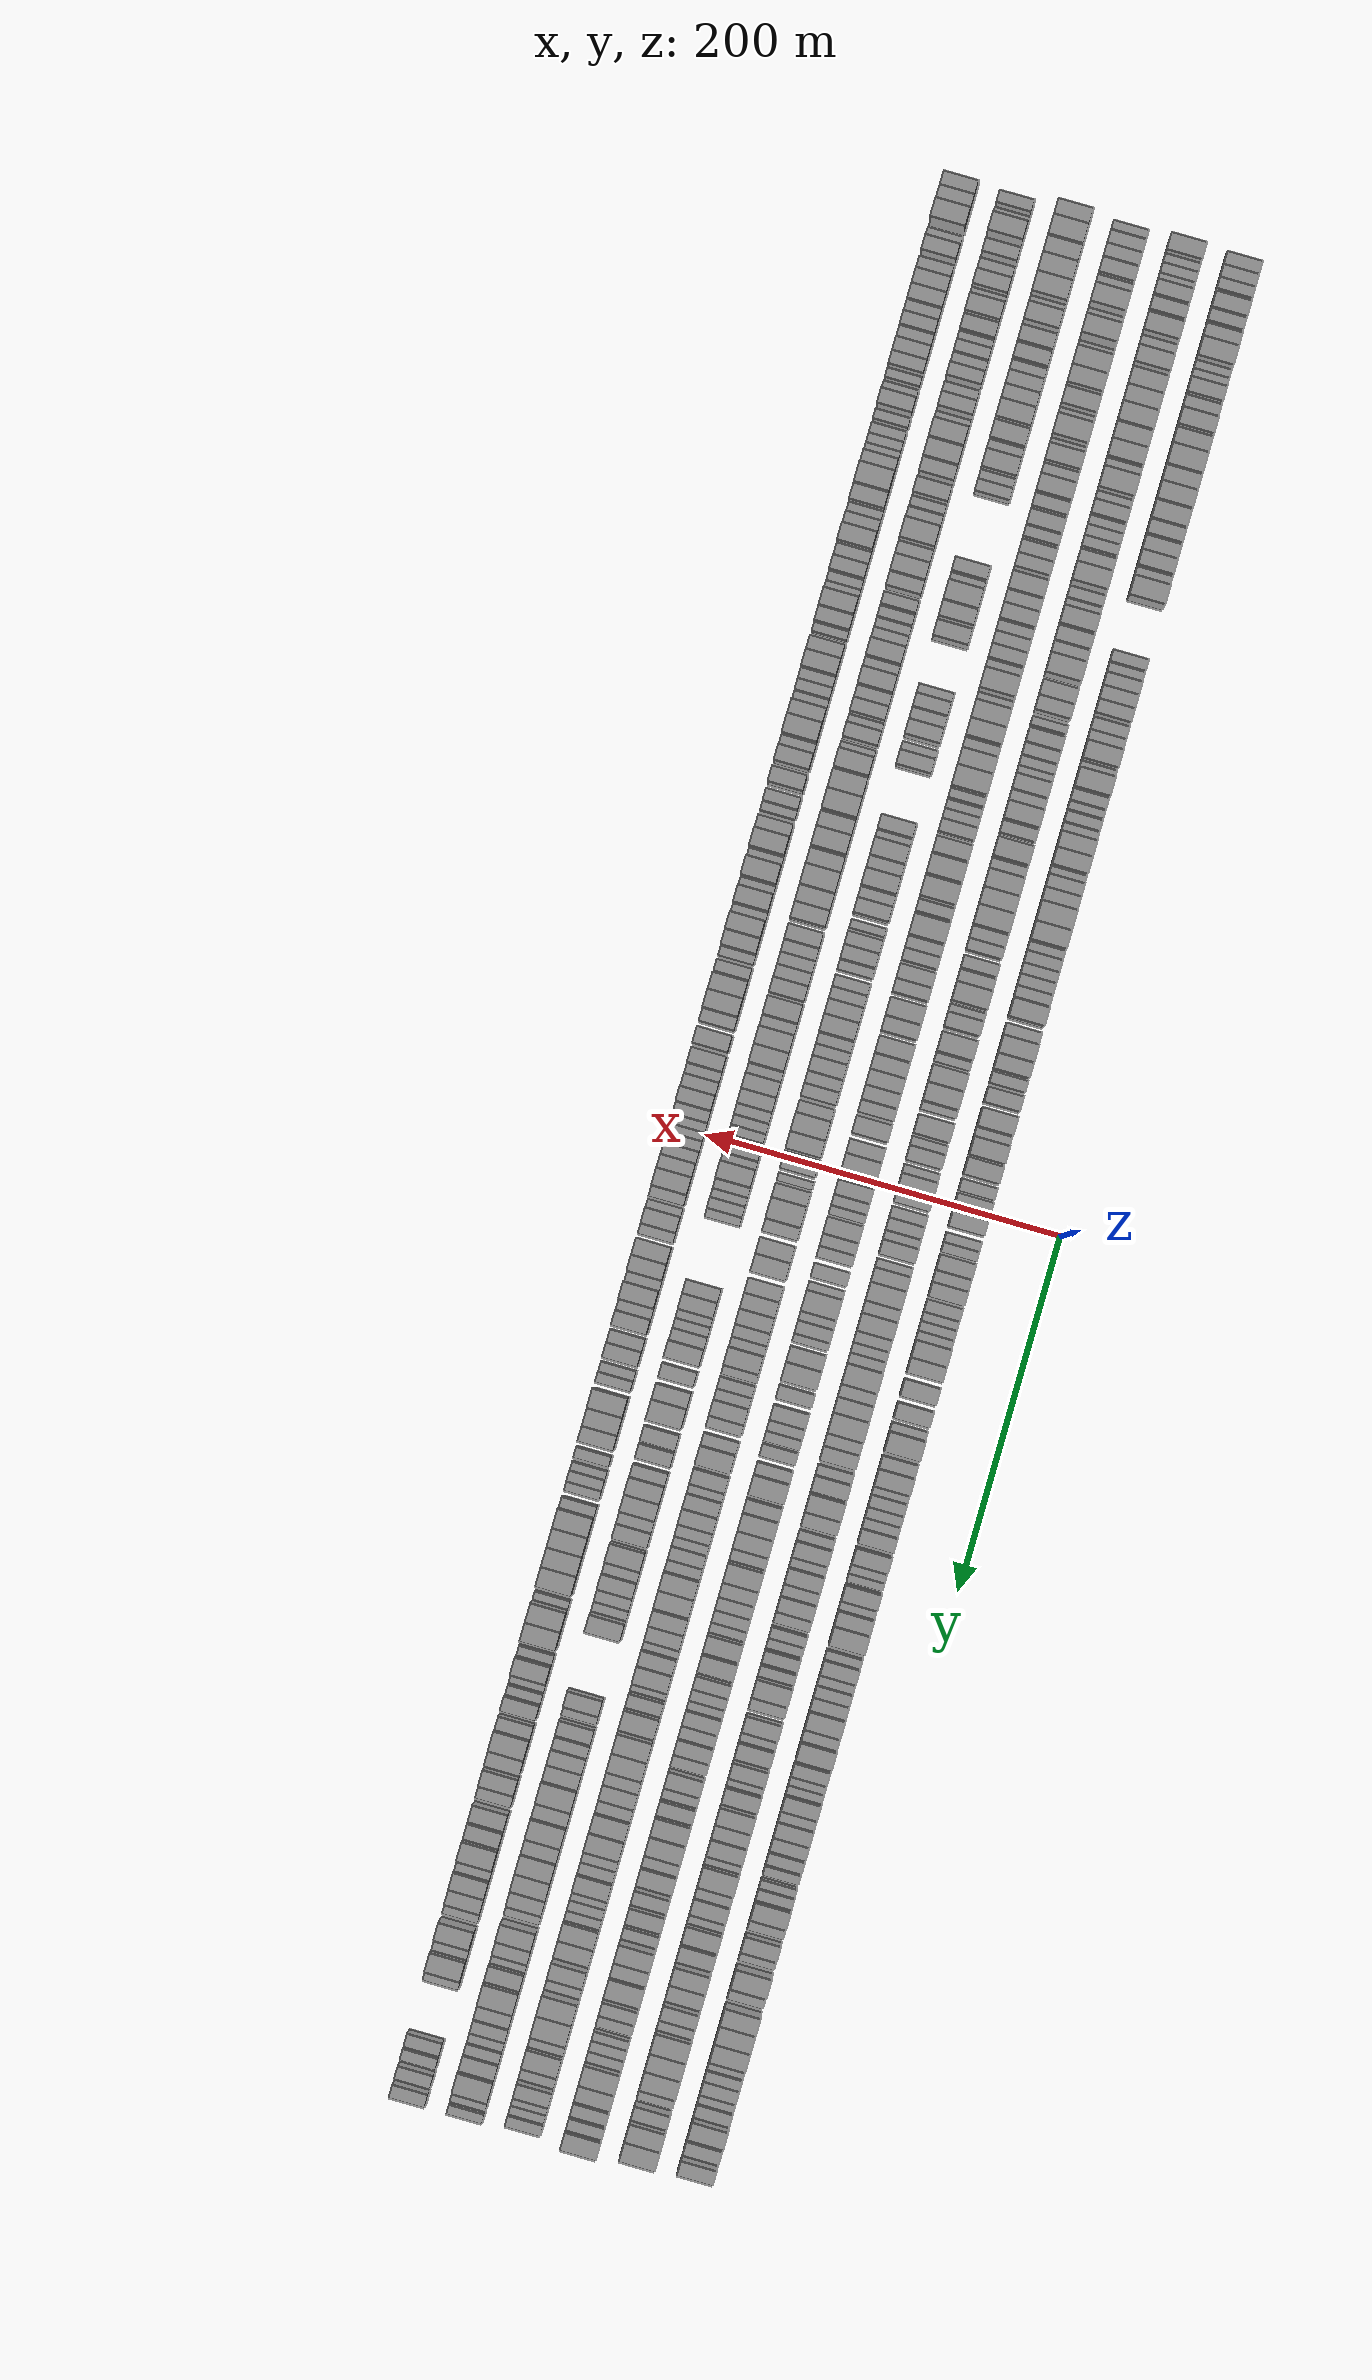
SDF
<sdf version="1.6">
 <world name="default">
  <scene>
   <sky><clouds><speed>12</speed></clouds></sky>
   <ambient>0.4 0.4 0.4 1</ambient>
   <background>0.7 0.7 0.7 1</background>
   <shadows>1</shadows>
  </scene>
  <gravity>0 0 -9.8066</gravity>
  <magnetic_field>6e-06 2.3e-05 -4.2e-05</magnetic_field>
  <physics default="0" name="default_physics" type="ode">
   <ode>
    <solver>
     <type>quick</type>
     <iters>10</iters>
     <sor>1.0</sor>
     <use_dynamic_moi_rescaling>0</use_dynamic_moi_rescaling>
    </solver>
    <constraints>
     <cfm>0</cfm>
     <erp>0.2</erp>
     <contact_max_correcting_vel>100</contact_max_correcting_vel>
     <contact_surface_layer>0.001</contact_surface_layer>
    </constraints>
   </ode>
   <max_step_size>0.004</max_step_size>
   <real_time_factor>1</real_time_factor>
   <real_time_update_rate>250</real_time_update_rate>
  </physics>
  <light name="sun" type="directional">
   <pose>0 0 10 0 0 0</pose>
   <diffuse>0.8 0.8 0.8 1</diffuse>
   <specular>0.2 0.2 0.2 1</specular>
   <attenuation>
    <range>1000</range>
    <constant>0.9</constant>
    <linear>0.01</linear>
    <quadratic>0.001</quadratic>
   </attenuation>
   <direction>-0.5 0.1 -0.9</direction>
  </light>
  <model name="building_1">
   <static>1</static>
   <pose>50.0000 -535.2608 0 0.000000 0.000000 0.000000</pose>
   <link name="link">
    <pose>0 0 7.50 0 0 0</pose>
    <collision name="collision"><geometry><box><size>20.0000 7.4783 15.0000</size></box></geometry></collision>
    <visual name="visual">
     <cast_shadows>0</cast_shadows>
     <geometry><box><size>20.0000 7.4783 15.0000</size></box></geometry>
     <material>
      <script>
       <uri>model://grey_wall/materials/scripts</uri>
       <uri>model://grey_wall/materials/textures</uri>
       <name>vrc/grey_wall</name>
      </script>
     </material>
    </visual>
   </link>
  </model>
  <model name="building_2">
   <static>1</static>
   <pose>50.0000 -527.9367 0 0.000000 0.000000 0.000000</pose>
   <link name="link">
    <pose>0 0 7.50 0 0 0</pose>
    <collision name="collision"><geometry><box><size>20.0000 7.1699 15.0000</size></box></geometry></collision>
    <visual name="visual">
     <cast_shadows>0</cast_shadows>
     <geometry><box><size>20.0000 7.1699 15.0000</size></box></geometry>
     <material>
      <script>
       <uri>model://grey_wall/materials/scripts</uri>
       <uri>model://grey_wall/materials/textures</uri>
       <name>vrc/grey_wall</name>
      </script>
     </material>
    </visual>
   </link>
  </model>
  <model name="building_3">
   <static>1</static>
   <pose>50.0000 -521.0979 0 0.000000 0.000000 0.000000</pose>
   <link name="link">
    <pose>0 0 7.50 0 0 0</pose>
    <collision name="collision"><geometry><box><size>20.0000 6.5079 15.0000</size></box></geometry></collision>
    <visual name="visual">
     <cast_shadows>0</cast_shadows>
     <geometry><box><size>20.0000 6.5079 15.0000</size></box></geometry>
     <material>
      <script>
       <uri>model://grey_wall/materials/scripts</uri>
       <uri>model://grey_wall/materials/textures</uri>
       <name>vrc/grey_wall</name>
      </script>
     </material>
    </visual>
   </link>
  </model>
  <model name="building_4">
   <static>1</static>
   <pose>50.0000 -511.3593 0 0.000000 0.000000 0.000000</pose>
   <link name="link">
    <pose>0 0 9.00 0 0 0</pose>
    <collision name="collision"><geometry><box><size>20.0000 8.9694 18.0000</size></box></geometry></collision>
    <visual name="visual">
     <cast_shadows>0</cast_shadows>
     <geometry><box><size>20.0000 8.9694 18.0000</size></box></geometry>
     <material>
      <script>
       <uri>model://grey_wall/materials/scripts</uri>
       <uri>model://grey_wall/materials/textures</uri>
       <name>vrc/grey_wall</name>
      </script>
     </material>
    </visual>
   </link>
  </model>
  <model name="building_5">
   <static>1</static>
   <pose>50.0000 -503.3232 0 0.000000 0.000000 0.000000</pose>
   <link name="link">
    <pose>0 0 7.50 0 0 0</pose>
    <collision name="collision"><geometry><box><size>20.0000 7.1027 15.0000</size></box></geometry></collision>
    <visual name="visual">
     <cast_shadows>0</cast_shadows>
     <geometry><box><size>20.0000 7.1027 15.0000</size></box></geometry>
     <material>
      <script>
       <uri>model://grey_wall/materials/scripts</uri>
       <uri>model://grey_wall/materials/textures</uri>
       <name>vrc/grey_wall</name>
      </script>
     </material>
    </visual>
   </link>
  </model>
  <model name="building_6">
   <static>1</static>
   <pose>50.0000 -493.3835 0 0.000000 0.000000 0.000000</pose>
   <link name="link">
    <pose>0 0 9.00 0 0 0</pose>
    <collision name="collision"><geometry><box><size>20.0000 8.7767 18.0000</size></box></geometry></collision>
    <visual name="visual">
     <cast_shadows>0</cast_shadows>
     <geometry><box><size>20.0000 8.7767 18.0000</size></box></geometry>
     <material>
      <script>
       <uri>model://grey_wall/materials/scripts</uri>
       <uri>model://grey_wall/materials/textures</uri>
       <name>vrc/grey_wall</name>
      </script>
     </material>
    </visual>
   </link>
  </model>
  <model name="building_7">
   <static>1</static>
   <pose>50.0000 -483.4961 0 0.000000 0.000000 0.000000</pose>
   <link name="link">
    <pose>0 0 12.00 0 0 0</pose>
    <collision name="collision"><geometry><box><size>20.0000 10.9980 24.0000</size></box></geometry></collision>
    <visual name="visual">
     <cast_shadows>0</cast_shadows>
     <geometry><box><size>20.0000 10.9980 24.0000</size></box></geometry>
     <material>
      <script>
       <uri>model://grey_wall/materials/scripts</uri>
       <uri>model://grey_wall/materials/textures</uri>
       <name>vrc/grey_wall</name>
      </script>
     </material>
    </visual>
   </link>
  </model>
  <model name="building_8">
   <static>1</static>
   <pose>50.0000 -475.5962 0 0.000000 0.000000 0.000000</pose>
   <link name="link">
    <pose>0 0 6.00 0 0 0</pose>
    <collision name="collision"><geometry><box><size>20.0000 4.8018 12.0000</size></box></geometry></collision>
    <visual name="visual">
     <cast_shadows>0</cast_shadows>
     <geometry><box><size>20.0000 4.8018 12.0000</size></box></geometry>
     <material>
      <script>
       <uri>model://grey_wall/materials/scripts</uri>
       <uri>model://grey_wall/materials/textures</uri>
       <name>vrc/grey_wall</name>
      </script>
     </material>
    </visual>
   </link>
  </model>
  <model name="building_9">
   <static>1</static>
   <pose>50.0000 -470.7642 0 0.000000 0.000000 0.000000</pose>
   <link name="link">
    <pose>0 0 6.00 0 0 0</pose>
    <collision name="collision"><geometry><box><size>20.0000 4.8622 12.0000</size></box></geometry></collision>
    <visual name="visual">
     <cast_shadows>0</cast_shadows>
     <geometry><box><size>20.0000 4.8622 12.0000</size></box></geometry>
     <material>
      <script>
       <uri>model://grey_wall/materials/scripts</uri>
       <uri>model://grey_wall/materials/textures</uri>
       <name>vrc/grey_wall</name>
      </script>
     </material>
    </visual>
   </link>
  </model>
  <model name="building_10">
   <static>1</static>
   <pose>50.0000 -463.0663 0 0.000000 0.000000 0.000000</pose>
   <link name="link">
    <pose>0 0 9.00 0 0 0</pose>
    <collision name="collision"><geometry><box><size>20.0000 8.5334 18.0000</size></box></geometry></collision>
    <visual name="visual">
     <cast_shadows>0</cast_shadows>
     <geometry><box><size>20.0000 8.5334 18.0000</size></box></geometry>
     <material>
      <script>
       <uri>model://grey_wall/materials/scripts</uri>
       <uri>model://grey_wall/materials/textures</uri>
       <name>vrc/grey_wall</name>
      </script>
     </material>
    </visual>
   </link>
  </model>
  <model name="building_11">
   <static>1</static>
   <pose>50.0000 -454.3824 0 0.000000 0.000000 0.000000</pose>
   <link name="link">
    <pose>0 0 7.50 0 0 0</pose>
    <collision name="collision"><geometry><box><size>20.0000 6.8344 15.0000</size></box></geometry></collision>
    <visual name="visual">
     <cast_shadows>0</cast_shadows>
     <geometry><box><size>20.0000 6.8344 15.0000</size></box></geometry>
     <material>
      <script>
       <uri>model://grey_wall/materials/scripts</uri>
       <uri>model://grey_wall/materials/textures</uri>
       <name>vrc/grey_wall</name>
      </script>
     </material>
    </visual>
   </link>
  </model>
  <model name="building_12">
   <static>1</static>
   <pose>50.0000 -444.1268 0 0.000000 0.000000 0.000000</pose>
   <link name="link">
    <pose>0 0 12.00 0 0 0</pose>
    <collision name="collision"><geometry><box><size>20.0000 9.6769 24.0000</size></box></geometry></collision>
    <visual name="visual">
     <cast_shadows>0</cast_shadows>
     <geometry><box><size>20.0000 9.6769 24.0000</size></box></geometry>
     <material>
      <script>
       <uri>model://grey_wall/materials/scripts</uri>
       <uri>model://grey_wall/materials/textures</uri>
       <name>vrc/grey_wall</name>
      </script>
     </material>
    </visual>
   </link>
  </model>
  <model name="building_13">
   <static>1</static>
   <pose>50.0000 -433.5658 0 0.000000 0.000000 0.000000</pose>
   <link name="link">
    <pose>0 0 10.50 0 0 0</pose>
    <collision name="collision"><geometry><box><size>20.0000 9.4451 21.0000</size></box></geometry></collision>
    <visual name="visual">
     <cast_shadows>0</cast_shadows>
     <geometry><box><size>20.0000 9.4451 21.0000</size></box></geometry>
     <material>
      <script>
       <uri>model://grey_wall/materials/scripts</uri>
       <uri>model://grey_wall/materials/textures</uri>
       <name>vrc/grey_wall</name>
      </script>
     </material>
    </visual>
   </link>
  </model>
  <model name="building_14">
   <static>1</static>
   <pose>50.0000 -422.9158 0 0.000000 0.000000 0.000000</pose>
   <link name="link">
    <pose>0 0 12.00 0 0 0</pose>
    <collision name="collision"><geometry><box><size>20.0000 11.8548 24.0000</size></box></geometry></collision>
    <visual name="visual">
     <cast_shadows>0</cast_shadows>
     <geometry><box><size>20.0000 11.8548 24.0000</size></box></geometry>
     <material>
      <script>
       <uri>model://grey_wall/materials/scripts</uri>
       <uri>model://grey_wall/materials/textures</uri>
       <name>vrc/grey_wall</name>
      </script>
     </material>
    </visual>
   </link>
  </model>
  <model name="building_15">
   <static>1</static>
   <pose>50.0000 -412.2645 0 0.000000 0.000000 0.000000</pose>
   <link name="link">
    <pose>0 0 10.50 0 0 0</pose>
    <collision name="collision"><geometry><box><size>20.0000 9.4478 21.0000</size></box></geometry></collision>
    <visual name="visual">
     <cast_shadows>0</cast_shadows>
     <geometry><box><size>20.0000 9.4478 21.0000</size></box></geometry>
     <material>
      <script>
       <uri>model://grey_wall/materials/scripts</uri>
       <uri>model://grey_wall/materials/textures</uri>
       <name>vrc/grey_wall</name>
      </script>
     </material>
    </visual>
   </link>
  </model>
  <model name="building_16">
   <static>1</static>
   <pose>50.0000 -402.4108 0 0.000000 0.000000 0.000000</pose>
   <link name="link">
    <pose>0 0 12.00 0 0 0</pose>
    <collision name="collision"><geometry><box><size>20.0000 10.2596 24.0000</size></box></geometry></collision>
    <visual name="visual">
     <cast_shadows>0</cast_shadows>
     <geometry><box><size>20.0000 10.2596 24.0000</size></box></geometry>
     <material>
      <script>
       <uri>model://grey_wall/materials/scripts</uri>
       <uri>model://grey_wall/materials/textures</uri>
       <name>vrc/grey_wall</name>
      </script>
     </material>
    </visual>
   </link>
  </model>
  <model name="building_17">
   <static>1</static>
   <pose>50.0000 -392.1484 0 0.000000 0.000000 0.000000</pose>
   <link name="link">
    <pose>0 0 10.50 0 0 0</pose>
    <collision name="collision"><geometry><box><size>20.0000 10.2651 21.0000</size></box></geometry></collision>
    <visual name="visual">
     <cast_shadows>0</cast_shadows>
     <geometry><box><size>20.0000 10.2651 21.0000</size></box></geometry>
     <material>
      <script>
       <uri>model://grey_wall/materials/scripts</uri>
       <uri>model://grey_wall/materials/textures</uri>
       <name>vrc/grey_wall</name>
      </script>
     </material>
    </visual>
   </link>
  </model>
  <model name="building_18">
   <static>1</static>
   <pose>50.0000 -382.9434 0 0.000000 0.000000 0.000000</pose>
   <link name="link">
    <pose>0 0 9.00 0 0 0</pose>
    <collision name="collision"><geometry><box><size>20.0000 8.1450 18.0000</size></box></geometry></collision>
    <visual name="visual">
     <cast_shadows>0</cast_shadows>
     <geometry><box><size>20.0000 8.1450 18.0000</size></box></geometry>
     <material>
      <script>
       <uri>model://grey_wall/materials/scripts</uri>
       <uri>model://grey_wall/materials/textures</uri>
       <name>vrc/grey_wall</name>
      </script>
     </material>
    </visual>
   </link>
  </model>
  <model name="building_19">
   <static>1</static>
   <pose>50.0000 -373.5247 0 0.000000 0.000000 0.000000</pose>
   <link name="link">
    <pose>0 0 9.00 0 0 0</pose>
    <collision name="collision"><geometry><box><size>20.0000 8.6924 18.0000</size></box></geometry></collision>
    <visual name="visual">
     <cast_shadows>0</cast_shadows>
     <geometry><box><size>20.0000 8.6924 18.0000</size></box></geometry>
     <material>
      <script>
       <uri>model://grey_wall/materials/scripts</uri>
       <uri>model://grey_wall/materials/textures</uri>
       <name>vrc/grey_wall</name>
      </script>
     </material>
    </visual>
   </link>
  </model>
  <model name="building_20">
   <static>1</static>
   <pose>50.0000 -364.7850 0 0.000000 0.000000 0.000000</pose>
   <link name="link">
    <pose>0 0 10.50 0 0 0</pose>
    <collision name="collision"><geometry><box><size>20.0000 8.7870 21.0000</size></box></geometry></collision>
    <visual name="visual">
     <cast_shadows>0</cast_shadows>
     <geometry><box><size>20.0000 8.7870 21.0000</size></box></geometry>
     <material>
      <script>
       <uri>model://grey_wall/materials/scripts</uri>
       <uri>model://grey_wall/materials/textures</uri>
       <name>vrc/grey_wall</name>
      </script>
     </material>
    </visual>
   </link>
  </model>
  <model name="building_21">
   <static>1</static>
   <pose>50.0000 -357.2429 0 0.000000 0.000000 0.000000</pose>
   <link name="link">
    <pose>0 0 7.50 0 0 0</pose>
    <collision name="collision"><geometry><box><size>20.0000 6.2971 15.0000</size></box></geometry></collision>
    <visual name="visual">
     <cast_shadows>0</cast_shadows>
     <geometry><box><size>20.0000 6.2971 15.0000</size></box></geometry>
     <material>
      <script>
       <uri>model://grey_wall/materials/scripts</uri>
       <uri>model://grey_wall/materials/textures</uri>
       <name>vrc/grey_wall</name>
      </script>
     </material>
    </visual>
   </link>
  </model>
  <model name="building_22">
   <static>1</static>
   <pose>50.0000 -348.5519 0 0.000000 0.000000 0.000000</pose>
   <link name="link">
    <pose>0 0 12.00 0 0 0</pose>
    <collision name="collision"><geometry><box><size>20.0000 11.0849 24.0000</size></box></geometry></collision>
    <visual name="visual">
     <cast_shadows>0</cast_shadows>
     <geometry><box><size>20.0000 11.0849 24.0000</size></box></geometry>
     <material>
      <script>
       <uri>model://grey_wall/materials/scripts</uri>
       <uri>model://grey_wall/materials/textures</uri>
       <name>vrc/grey_wall</name>
      </script>
     </material>
    </visual>
   </link>
  </model>
  <model name="building_23">
   <static>1</static>
   <pose>50.0000 -310.0398 0 0.000000 0.000000 0.000000</pose>
   <link name="link">
    <pose>0 0 7.50 0 0 0</pose>
    <collision name="collision"><geometry><box><size>20.0000 6.6464 15.0000</size></box></geometry></collision>
    <visual name="visual">
     <cast_shadows>0</cast_shadows>
     <geometry><box><size>20.0000 6.6464 15.0000</size></box></geometry>
     <material>
      <script>
       <uri>model://grey_wall/materials/scripts</uri>
       <uri>model://grey_wall/materials/textures</uri>
       <name>vrc/grey_wall</name>
      </script>
     </material>
    </visual>
   </link>
  </model>
  <model name="building_24">
   <static>1</static>
   <pose>50.0000 -304.0617 0 0.000000 0.000000 0.000000</pose>
   <link name="link">
    <pose>0 0 6.00 0 0 0</pose>
    <collision name="collision"><geometry><box><size>20.0000 5.3097 12.0000</size></box></geometry></collision>
    <visual name="visual">
     <cast_shadows>0</cast_shadows>
     <geometry><box><size>20.0000 5.3097 12.0000</size></box></geometry>
     <material>
      <script>
       <uri>model://grey_wall/materials/scripts</uri>
       <uri>model://grey_wall/materials/textures</uri>
       <name>vrc/grey_wall</name>
      </script>
     </material>
    </visual>
   </link>
  </model>
  <model name="building_25">
   <static>1</static>
   <pose>50.0000 -296.6965 0 0.000000 0.000000 0.000000</pose>
   <link name="link">
    <pose>0 0 9.00 0 0 0</pose>
    <collision name="collision"><geometry><box><size>20.0000 7.4208 18.0000</size></box></geometry></collision>
    <visual name="visual">
     <cast_shadows>0</cast_shadows>
     <geometry><box><size>20.0000 7.4208 18.0000</size></box></geometry>
     <material>
      <script>
       <uri>model://grey_wall/materials/scripts</uri>
       <uri>model://grey_wall/materials/textures</uri>
       <name>vrc/grey_wall</name>
      </script>
     </material>
    </visual>
   </link>
  </model>
  <model name="building_26">
   <static>1</static>
   <pose>50.0000 -289.1113 0 0.000000 0.000000 0.000000</pose>
   <link name="link">
    <pose>0 0 9.00 0 0 0</pose>
    <collision name="collision"><geometry><box><size>20.0000 7.7495 18.0000</size></box></geometry></collision>
    <visual name="visual">
     <cast_shadows>0</cast_shadows>
     <geometry><box><size>20.0000 7.7495 18.0000</size></box></geometry>
     <material>
      <script>
       <uri>model://grey_wall/materials/scripts</uri>
       <uri>model://grey_wall/materials/textures</uri>
       <name>vrc/grey_wall</name>
      </script>
     </material>
    </visual>
   </link>
  </model>
  <model name="building_27">
   <static>1</static>
   <pose>50.0000 -281.3216 0 0.000000 0.000000 0.000000</pose>
   <link name="link">
    <pose>0 0 9.00 0 0 0</pose>
    <collision name="collision"><geometry><box><size>20.0000 7.8299 18.0000</size></box></geometry></collision>
    <visual name="visual">
     <cast_shadows>0</cast_shadows>
     <geometry><box><size>20.0000 7.8299 18.0000</size></box></geometry>
     <material>
      <script>
       <uri>model://grey_wall/materials/scripts</uri>
       <uri>model://grey_wall/materials/textures</uri>
       <name>vrc/grey_wall</name>
      </script>
     </material>
    </visual>
   </link>
  </model>
  <model name="building_28">
   <static>1</static>
   <pose>50.0000 -271.8612 0 0.000000 0.000000 0.000000</pose>
   <link name="link">
    <pose>0 0 7.50 0 0 0</pose>
    <collision name="collision"><geometry><box><size>20.0000 7.0910 15.0000</size></box></geometry></collision>
    <visual name="visual">
     <cast_shadows>0</cast_shadows>
     <geometry><box><size>20.0000 7.0910 15.0000</size></box></geometry>
     <material>
      <script>
       <uri>model://grey_wall/materials/scripts</uri>
       <uri>model://grey_wall/materials/textures</uri>
       <name>vrc/grey_wall</name>
      </script>
     </material>
    </visual>
   </link>
  </model>
  <model name="building_29">
   <static>1</static>
   <pose>50.0000 -264.8515 0 0.000000 0.000000 0.000000</pose>
   <link name="link">
    <pose>0 0 7.50 0 0 0</pose>
    <collision name="collision"><geometry><box><size>20.0000 6.9283 15.0000</size></box></geometry></collision>
    <visual name="visual">
     <cast_shadows>0</cast_shadows>
     <geometry><box><size>20.0000 6.9283 15.0000</size></box></geometry>
     <material>
      <script>
       <uri>model://grey_wall/materials/scripts</uri>
       <uri>model://grey_wall/materials/textures</uri>
       <name>vrc/grey_wall</name>
      </script>
     </material>
    </visual>
   </link>
  </model>
  <model name="building_30">
   <static>1</static>
   <pose>50.0000 -256.2500 0 0.000000 0.000000 0.000000</pose>
   <link name="link">
    <pose>0 0 12.00 0 0 0</pose>
    <collision name="collision"><geometry><box><size>20.0000 10.2747 24.0000</size></box></geometry></collision>
    <visual name="visual">
     <cast_shadows>0</cast_shadows>
     <geometry><box><size>20.0000 10.2747 24.0000</size></box></geometry>
     <material>
      <script>
       <uri>model://grey_wall/materials/scripts</uri>
       <uri>model://grey_wall/materials/textures</uri>
       <name>vrc/grey_wall</name>
      </script>
     </material>
    </visual>
   </link>
  </model>
  <model name="building_31">
   <static>1</static>
   <pose>50.0000 -248.6402 0 0.000000 0.000000 0.000000</pose>
   <link name="link">
    <pose>0 0 6.00 0 0 0</pose>
    <collision name="collision"><geometry><box><size>20.0000 4.9449 12.0000</size></box></geometry></collision>
    <visual name="visual">
     <cast_shadows>0</cast_shadows>
     <geometry><box><size>20.0000 4.9449 12.0000</size></box></geometry>
     <material>
      <script>
       <uri>model://grey_wall/materials/scripts</uri>
       <uri>model://grey_wall/materials/textures</uri>
       <name>vrc/grey_wall</name>
      </script>
     </material>
    </visual>
   </link>
  </model>
  <model name="building_32">
   <static>1</static>
   <pose>50.0000 -240.6708 0 0.000000 0.000000 0.000000</pose>
   <link name="link">
    <pose>0 0 12.00 0 0 0</pose>
    <collision name="collision"><geometry><box><size>20.0000 10.9939 24.0000</size></box></geometry></collision>
    <visual name="visual">
     <cast_shadows>0</cast_shadows>
     <geometry><box><size>20.0000 10.9939 24.0000</size></box></geometry>
     <material>
      <script>
       <uri>model://grey_wall/materials/scripts</uri>
       <uri>model://grey_wall/materials/textures</uri>
       <name>vrc/grey_wall</name>
      </script>
     </material>
    </visual>
   </link>
  </model>
  <model name="building_33">
   <static>1</static>
   <pose>50.0000 -231.8314 0 0.000000 0.000000 0.000000</pose>
   <link name="link">
    <pose>0 0 7.50 0 0 0</pose>
    <collision name="collision"><geometry><box><size>20.0000 6.6849 15.0000</size></box></geometry></collision>
    <visual name="visual">
     <cast_shadows>0</cast_shadows>
     <geometry><box><size>20.0000 6.6849 15.0000</size></box></geometry>
     <material>
      <script>
       <uri>model://grey_wall/materials/scripts</uri>
       <uri>model://grey_wall/materials/textures</uri>
       <name>vrc/grey_wall</name>
      </script>
     </material>
    </visual>
   </link>
  </model>
  <model name="building_34">
   <static>1</static>
   <pose>50.0000 -226.0718 0 0.000000 0.000000 0.000000</pose>
   <link name="link">
    <pose>0 0 6.00 0 0 0</pose>
    <collision name="collision"><geometry><box><size>20.0000 4.8343 12.0000</size></box></geometry></collision>
    <visual name="visual">
     <cast_shadows>0</cast_shadows>
     <geometry><box><size>20.0000 4.8343 12.0000</size></box></geometry>
     <material>
      <script>
       <uri>model://grey_wall/materials/scripts</uri>
       <uri>model://grey_wall/materials/textures</uri>
       <name>vrc/grey_wall</name>
      </script>
     </material>
    </visual>
   </link>
  </model>
  <model name="building_35">
   <static>1</static>
   <pose>50.0000 -219.5047 0 0.000000 0.000000 0.000000</pose>
   <link name="link">
    <pose>0 0 7.50 0 0 0</pose>
    <collision name="collision"><geometry><box><size>20.0000 6.2999 15.0000</size></box></geometry></collision>
    <visual name="visual">
     <cast_shadows>0</cast_shadows>
     <geometry><box><size>20.0000 6.2999 15.0000</size></box></geometry>
     <material>
      <script>
       <uri>model://grey_wall/materials/scripts</uri>
       <uri>model://grey_wall/materials/textures</uri>
       <name>vrc/grey_wall</name>
      </script>
     </material>
    </visual>
   </link>
  </model>
  <model name="building_36">
   <static>1</static>
   <pose>50.0000 -213.4756 0 0.000000 0.000000 0.000000</pose>
   <link name="link">
    <pose>0 0 6.00 0 0 0</pose>
    <collision name="collision"><geometry><box><size>20.0000 5.7582 12.0000</size></box></geometry></collision>
    <visual name="visual">
     <cast_shadows>0</cast_shadows>
     <geometry><box><size>20.0000 5.7582 12.0000</size></box></geometry>
     <material>
      <script>
       <uri>model://grey_wall/materials/scripts</uri>
       <uri>model://grey_wall/materials/textures</uri>
       <name>vrc/grey_wall</name>
      </script>
     </material>
    </visual>
   </link>
  </model>
  <model name="building_37">
   <static>1</static>
   <pose>50.0000 -206.0291 0 0.000000 0.000000 0.000000</pose>
   <link name="link">
    <pose>0 0 10.50 0 0 0</pose>
    <collision name="collision"><geometry><box><size>20.0000 9.1349 21.0000</size></box></geometry></collision>
    <visual name="visual">
     <cast_shadows>0</cast_shadows>
     <geometry><box><size>20.0000 9.1349 21.0000</size></box></geometry>
     <material>
      <script>
       <uri>model://grey_wall/materials/scripts</uri>
       <uri>model://grey_wall/materials/textures</uri>
       <name>vrc/grey_wall</name>
      </script>
     </material>
    </visual>
   </link>
  </model>
  <model name="building_38">
   <static>1</static>
   <pose>50.0000 -196.5825 0 0.000000 0.000000 0.000000</pose>
   <link name="link">
    <pose>0 0 10.50 0 0 0</pose>
    <collision name="collision"><geometry><box><size>20.0000 9.7582 21.0000</size></box></geometry></collision>
    <visual name="visual">
     <cast_shadows>0</cast_shadows>
     <geometry><box><size>20.0000 9.7582 21.0000</size></box></geometry>
     <material>
      <script>
       <uri>model://grey_wall/materials/scripts</uri>
       <uri>model://grey_wall/materials/textures</uri>
       <name>vrc/grey_wall</name>
      </script>
     </material>
    </visual>
   </link>
  </model>
  <model name="building_39">
   <static>1</static>
   <pose>50.0000 -189.2171 0 0.000000 0.000000 0.000000</pose>
   <link name="link">
    <pose>0 0 6.00 0 0 0</pose>
    <collision name="collision"><geometry><box><size>20.0000 4.9726 12.0000</size></box></geometry></collision>
    <visual name="visual">
     <cast_shadows>0</cast_shadows>
     <geometry><box><size>20.0000 4.9726 12.0000</size></box></geometry>
     <material>
      <script>
       <uri>model://grey_wall/materials/scripts</uri>
       <uri>model://grey_wall/materials/textures</uri>
       <name>vrc/grey_wall</name>
      </script>
     </material>
    </visual>
   </link>
  </model>
  <model name="building_40">
   <static>1</static>
   <pose>50.0000 -183.0390 0 0.000000 0.000000 0.000000</pose>
   <link name="link">
    <pose>0 0 9.00 0 0 0</pose>
    <collision name="collision"><geometry><box><size>20.0000 7.3835 18.0000</size></box></geometry></collision>
    <visual name="visual">
     <cast_shadows>0</cast_shadows>
     <geometry><box><size>20.0000 7.3835 18.0000</size></box></geometry>
     <material>
      <script>
       <uri>model://grey_wall/materials/scripts</uri>
       <uri>model://grey_wall/materials/textures</uri>
       <name>vrc/grey_wall</name>
      </script>
     </material>
    </visual>
   </link>
  </model>
  <model name="building_41">
   <static>1</static>
   <pose>50.0000 -175.3002 0 0.000000 0.000000 0.000000</pose>
   <link name="link">
    <pose>0 0 9.00 0 0 0</pose>
    <collision name="collision"><geometry><box><size>20.0000 8.0942 18.0000</size></box></geometry></collision>
    <visual name="visual">
     <cast_shadows>0</cast_shadows>
     <geometry><box><size>20.0000 8.0942 18.0000</size></box></geometry>
     <material>
      <script>
       <uri>model://grey_wall/materials/scripts</uri>
       <uri>model://grey_wall/materials/textures</uri>
       <name>vrc/grey_wall</name>
      </script>
     </material>
    </visual>
   </link>
  </model>
  <model name="building_42">
   <static>1</static>
   <pose>50.0000 -165.5234 0 0.000000 0.000000 0.000000</pose>
   <link name="link">
    <pose>0 0 12.00 0 0 0</pose>
    <collision name="collision"><geometry><box><size>20.0000 11.4593 24.0000</size></box></geometry></collision>
    <visual name="visual">
     <cast_shadows>0</cast_shadows>
     <geometry><box><size>20.0000 11.4593 24.0000</size></box></geometry>
     <material>
      <script>
       <uri>model://grey_wall/materials/scripts</uri>
       <uri>model://grey_wall/materials/textures</uri>
       <name>vrc/grey_wall</name>
      </script>
     </material>
    </visual>
   </link>
  </model>
  <model name="building_43">
   <static>1</static>
   <pose>50.0000 -154.5439 0 0.000000 0.000000 0.000000</pose>
   <link name="link">
    <pose>0 0 12.00 0 0 0</pose>
    <collision name="collision"><geometry><box><size>20.0000 10.4997 24.0000</size></box></geometry></collision>
    <visual name="visual">
     <cast_shadows>0</cast_shadows>
     <geometry><box><size>20.0000 10.4997 24.0000</size></box></geometry>
     <material>
      <script>
       <uri>model://grey_wall/materials/scripts</uri>
       <uri>model://grey_wall/materials/textures</uri>
       <name>vrc/grey_wall</name>
      </script>
     </material>
    </visual>
   </link>
  </model>
  <model name="building_44">
   <static>1</static>
   <pose>50.0000 -146.5564 0 0.000000 0.000000 0.000000</pose>
   <link name="link">
    <pose>0 0 6.00 0 0 0</pose>
    <collision name="collision"><geometry><box><size>20.0000 5.4754 12.0000</size></box></geometry></collision>
    <visual name="visual">
     <cast_shadows>0</cast_shadows>
     <geometry><box><size>20.0000 5.4754 12.0000</size></box></geometry>
     <material>
      <script>
       <uri>model://grey_wall/materials/scripts</uri>
       <uri>model://grey_wall/materials/textures</uri>
       <name>vrc/grey_wall</name>
      </script>
     </material>
    </visual>
   </link>
  </model>
  <model name="building_45">
   <static>1</static>
   <pose>50.0000 -140.3631 0 0.000000 0.000000 0.000000</pose>
   <link name="link">
    <pose>0 0 7.50 0 0 0</pose>
    <collision name="collision"><geometry><box><size>20.0000 6.9111 15.0000</size></box></geometry></collision>
    <visual name="visual">
     <cast_shadows>0</cast_shadows>
     <geometry><box><size>20.0000 6.9111 15.0000</size></box></geometry>
     <material>
      <script>
       <uri>model://grey_wall/materials/scripts</uri>
       <uri>model://grey_wall/materials/textures</uri>
       <name>vrc/grey_wall</name>
      </script>
     </material>
    </visual>
   </link>
  </model>
  <model name="building_46">
   <static>1</static>
   <pose>50.0000 -133.8314 0 0.000000 0.000000 0.000000</pose>
   <link name="link">
    <pose>0 0 7.50 0 0 0</pose>
    <collision name="collision"><geometry><box><size>20.0000 6.1522 15.0000</size></box></geometry></collision>
    <visual name="visual">
     <cast_shadows>0</cast_shadows>
     <geometry><box><size>20.0000 6.1522 15.0000</size></box></geometry>
     <material>
      <script>
       <uri>model://grey_wall/materials/scripts</uri>
       <uri>model://grey_wall/materials/textures</uri>
       <name>vrc/grey_wall</name>
      </script>
     </material>
    </visual>
   </link>
  </model>
  <model name="building_47">
   <static>1</static>
   <pose>50.0000 -127.4547 0 0.000000 0.000000 0.000000</pose>
   <link name="link">
    <pose>0 0 7.50 0 0 0</pose>
    <collision name="collision"><geometry><box><size>20.0000 6.6014 15.0000</size></box></geometry></collision>
    <visual name="visual">
     <cast_shadows>0</cast_shadows>
     <geometry><box><size>20.0000 6.6014 15.0000</size></box></geometry>
     <material>
      <script>
       <uri>model://grey_wall/materials/scripts</uri>
       <uri>model://grey_wall/materials/textures</uri>
       <name>vrc/grey_wall</name>
      </script>
     </material>
    </visual>
   </link>
  </model>
  <model name="building_48">
   <static>1</static>
   <pose>50.0000 -120.9139 0 0.000000 0.000000 0.000000</pose>
   <link name="link">
    <pose>0 0 7.50 0 0 0</pose>
    <collision name="collision"><geometry><box><size>20.0000 6.4801 15.0000</size></box></geometry></collision>
    <visual name="visual">
     <cast_shadows>0</cast_shadows>
     <geometry><box><size>20.0000 6.4801 15.0000</size></box></geometry>
     <material>
      <script>
       <uri>model://grey_wall/materials/scripts</uri>
       <uri>model://grey_wall/materials/textures</uri>
       <name>vrc/grey_wall</name>
      </script>
     </material>
    </visual>
   </link>
  </model>
  <model name="building_49">
   <static>1</static>
   <pose>50.0000 -111.3536 0 0.000000 0.000000 0.000000</pose>
   <link name="link">
    <pose>0 0 12.00 0 0 0</pose>
    <collision name="collision"><geometry><box><size>20.0000 10.6406 24.0000</size></box></geometry></collision>
    <visual name="visual">
     <cast_shadows>0</cast_shadows>
     <geometry><box><size>20.0000 10.6406 24.0000</size></box></geometry>
     <material>
      <script>
       <uri>model://grey_wall/materials/scripts</uri>
       <uri>model://grey_wall/materials/textures</uri>
       <name>vrc/grey_wall</name>
      </script>
     </material>
    </visual>
   </link>
  </model>
  <model name="building_50">
   <static>1</static>
   <pose>50.0000 -99.4085 0 0.000000 0.000000 0.000000</pose>
   <link name="link">
    <pose>0 0 7.50 0 0 0</pose>
    <collision name="collision"><geometry><box><size>20.0000 7.2495 15.0000</size></box></geometry></collision>
    <visual name="visual">
     <cast_shadows>0</cast_shadows>
     <geometry><box><size>20.0000 7.2495 15.0000</size></box></geometry>
     <material>
      <script>
       <uri>model://grey_wall/materials/scripts</uri>
       <uri>model://grey_wall/materials/textures</uri>
       <name>vrc/grey_wall</name>
      </script>
     </material>
    </visual>
   </link>
  </model>
  <model name="building_51">
   <static>1</static>
   <pose>50.0000 -90.7654 0 0.000000 0.000000 0.000000</pose>
   <link name="link">
    <pose>0 0 12.00 0 0 0</pose>
    <collision name="collision"><geometry><box><size>20.0000 10.0367 24.0000</size></box></geometry></collision>
    <visual name="visual">
     <cast_shadows>0</cast_shadows>
     <geometry><box><size>20.0000 10.0367 24.0000</size></box></geometry>
     <material>
      <script>
       <uri>model://grey_wall/materials/scripts</uri>
       <uri>model://grey_wall/materials/textures</uri>
       <name>vrc/grey_wall</name>
      </script>
     </material>
    </visual>
   </link>
  </model>
  <model name="building_52">
   <static>1</static>
   <pose>50.0000 -81.3214 0 0.000000 0.000000 0.000000</pose>
   <link name="link">
    <pose>0 0 10.50 0 0 0</pose>
    <collision name="collision"><geometry><box><size>20.0000 8.8512 21.0000</size></box></geometry></collision>
    <visual name="visual">
     <cast_shadows>0</cast_shadows>
     <geometry><box><size>20.0000 8.8512 21.0000</size></box></geometry>
     <material>
      <script>
       <uri>model://grey_wall/materials/scripts</uri>
       <uri>model://grey_wall/materials/textures</uri>
       <name>vrc/grey_wall</name>
      </script>
     </material>
    </visual>
   </link>
  </model>
  <model name="building_53">
   <static>1</static>
   <pose>50.0000 -72.4730 0 0.000000 0.000000 0.000000</pose>
   <link name="link">
    <pose>0 0 7.50 0 0 0</pose>
    <collision name="collision"><geometry><box><size>20.0000 6.8455 15.0000</size></box></geometry></collision>
    <visual name="visual">
     <cast_shadows>0</cast_shadows>
     <geometry><box><size>20.0000 6.8455 15.0000</size></box></geometry>
     <material>
      <script>
       <uri>model://grey_wall/materials/scripts</uri>
       <uri>model://grey_wall/materials/textures</uri>
       <name>vrc/grey_wall</name>
      </script>
     </material>
    </visual>
   </link>
  </model>
  <model name="building_54">
   <static>1</static>
   <pose>50.0000 -62.6387 0 0.000000 0.000000 0.000000</pose>
   <link name="link">
    <pose>0 0 9.00 0 0 0</pose>
    <collision name="collision"><geometry><box><size>20.0000 8.8231 18.0000</size></box></geometry></collision>
    <visual name="visual">
     <cast_shadows>0</cast_shadows>
     <geometry><box><size>20.0000 8.8231 18.0000</size></box></geometry>
     <material>
      <script>
       <uri>model://grey_wall/materials/scripts</uri>
       <uri>model://grey_wall/materials/textures</uri>
       <name>vrc/grey_wall</name>
      </script>
     </material>
    </visual>
   </link>
  </model>
  <model name="building_55">
   <static>1</static>
   <pose>50.0000 -49.9104 0 0.000000 0.000000 0.000000</pose>
   <link name="link">
    <pose>0 0 12.00 0 0 0</pose>
    <collision name="collision"><geometry><box><size>20.0000 10.6335 24.0000</size></box></geometry></collision>
    <visual name="visual">
     <cast_shadows>0</cast_shadows>
     <geometry><box><size>20.0000 10.6335 24.0000</size></box></geometry>
     <material>
      <script>
       <uri>model://grey_wall/materials/scripts</uri>
       <uri>model://grey_wall/materials/textures</uri>
       <name>vrc/grey_wall</name>
      </script>
     </material>
    </visual>
   </link>
  </model>
  <model name="building_56">
   <static>1</static>
   <pose>50.0000 -41.7730 0 0.000000 0.000000 0.000000</pose>
   <link name="link">
    <pose>0 0 6.00 0 0 0</pose>
    <collision name="collision"><geometry><box><size>20.0000 5.6413 12.0000</size></box></geometry></collision>
    <visual name="visual">
     <cast_shadows>0</cast_shadows>
     <geometry><box><size>20.0000 5.6413 12.0000</size></box></geometry>
     <material>
      <script>
       <uri>model://grey_wall/materials/scripts</uri>
       <uri>model://grey_wall/materials/textures</uri>
       <name>vrc/grey_wall</name>
      </script>
     </material>
    </visual>
   </link>
  </model>
  <model name="building_57">
   <static>1</static>
   <pose>50.0000 -33.7671 0 0.000000 0.000000 0.000000</pose>
   <link name="link">
    <pose>0 0 12.00 0 0 0</pose>
    <collision name="collision"><geometry><box><size>20.0000 10.3705 24.0000</size></box></geometry></collision>
    <visual name="visual">
     <cast_shadows>0</cast_shadows>
     <geometry><box><size>20.0000 10.3705 24.0000</size></box></geometry>
     <material>
      <script>
       <uri>model://grey_wall/materials/scripts</uri>
       <uri>model://grey_wall/materials/textures</uri>
       <name>vrc/grey_wall</name>
      </script>
     </material>
    </visual>
   </link>
  </model>
  <model name="building_58">
   <static>1</static>
   <pose>50.0000 -22.5808 0 0.000000 0.000000 0.000000</pose>
   <link name="link">
    <pose>0 0 10.50 0 0 0</pose>
    <collision name="collision"><geometry><box><size>20.0000 10.0020 21.0000</size></box></geometry></collision>
    <visual name="visual">
     <cast_shadows>0</cast_shadows>
     <geometry><box><size>20.0000 10.0020 21.0000</size></box></geometry>
     <material>
      <script>
       <uri>model://grey_wall/materials/scripts</uri>
       <uri>model://grey_wall/materials/textures</uri>
       <name>vrc/grey_wall</name>
      </script>
     </material>
    </visual>
   </link>
  </model>
  <model name="building_59">
   <static>1</static>
   <pose>50.0000 -11.9805 0 0.000000 0.000000 0.000000</pose>
   <link name="link">
    <pose>0 0 7.50 0 0 0</pose>
    <collision name="collision"><geometry><box><size>20.0000 7.1987 15.0000</size></box></geometry></collision>
    <visual name="visual">
     <cast_shadows>0</cast_shadows>
     <geometry><box><size>20.0000 7.1987 15.0000</size></box></geometry>
     <material>
      <script>
       <uri>model://grey_wall/materials/scripts</uri>
       <uri>model://grey_wall/materials/textures</uri>
       <name>vrc/grey_wall</name>
      </script>
     </material>
    </visual>
   </link>
  </model>
  <model name="building_60">
   <static>1</static>
   <pose>50.0000 -2.3744 0 0.000000 0.000000 0.000000</pose>
   <link name="link">
    <pose>0 0 10.50 0 0 0</pose>
    <collision name="collision"><geometry><box><size>20.0000 10.0136 21.0000</size></box></geometry></collision>
    <visual name="visual">
     <cast_shadows>0</cast_shadows>
     <geometry><box><size>20.0000 10.0136 21.0000</size></box></geometry>
     <material>
      <script>
       <uri>model://grey_wall/materials/scripts</uri>
       <uri>model://grey_wall/materials/textures</uri>
       <name>vrc/grey_wall</name>
      </script>
     </material>
    </visual>
   </link>
  </model>
  <model name="building_61">
   <static>1</static>
   <pose>50.0000 7.1220 0 0.000000 0.000000 0.000000</pose>
   <link name="link">
    <pose>0 0 9.00 0 0 0</pose>
    <collision name="collision"><geometry><box><size>20.0000 8.9793 18.0000</size></box></geometry></collision>
    <visual name="visual">
     <cast_shadows>0</cast_shadows>
     <geometry><box><size>20.0000 8.9793 18.0000</size></box></geometry>
     <material>
      <script>
       <uri>model://grey_wall/materials/scripts</uri>
       <uri>model://grey_wall/materials/textures</uri>
       <name>vrc/grey_wall</name>
      </script>
     </material>
    </visual>
   </link>
  </model>
  <model name="building_62">
   <static>1</static>
   <pose>50.0000 17.3783 0 0.000000 0.000000 0.000000</pose>
   <link name="link">
    <pose>0 0 6.00 0 0 0</pose>
    <collision name="collision"><geometry><box><size>20.0000 5.5332 12.0000</size></box></geometry></collision>
    <visual name="visual">
     <cast_shadows>0</cast_shadows>
     <geometry><box><size>20.0000 5.5332 12.0000</size></box></geometry>
     <material>
      <script>
       <uri>model://grey_wall/materials/scripts</uri>
       <uri>model://grey_wall/materials/textures</uri>
       <name>vrc/grey_wall</name>
      </script>
     </material>
    </visual>
   </link>
  </model>
  <model name="building_63">
   <static>1</static>
   <pose>50.0000 23.1135 0 0.000000 0.000000 0.000000</pose>
   <link name="link">
    <pose>0 0 6.00 0 0 0</pose>
    <collision name="collision"><geometry><box><size>20.0000 5.9373 12.0000</size></box></geometry></collision>
    <visual name="visual">
     <cast_shadows>0</cast_shadows>
     <geometry><box><size>20.0000 5.9373 12.0000</size></box></geometry>
     <material>
      <script>
       <uri>model://grey_wall/materials/scripts</uri>
       <uri>model://grey_wall/materials/textures</uri>
       <name>vrc/grey_wall</name>
      </script>
     </material>
    </visual>
   </link>
  </model>
  <model name="building_64">
   <static>1</static>
   <pose>50.0000 31.4604 0 0.000000 0.000000 0.000000</pose>
   <link name="link">
    <pose>0 0 10.50 0 0 0</pose>
    <collision name="collision"><geometry><box><size>20.0000 8.7566 21.0000</size></box></geometry></collision>
    <visual name="visual">
     <cast_shadows>0</cast_shadows>
     <geometry><box><size>20.0000 8.7566 21.0000</size></box></geometry>
     <material>
      <script>
       <uri>model://grey_wall/materials/scripts</uri>
       <uri>model://grey_wall/materials/textures</uri>
       <name>vrc/grey_wall</name>
      </script>
     </material>
    </visual>
   </link>
  </model>
  <model name="building_65">
   <static>1</static>
   <pose>50.0000 39.1903 0 0.000000 0.000000 0.000000</pose>
   <link name="link">
    <pose>0 0 7.50 0 0 0</pose>
    <collision name="collision"><geometry><box><size>20.0000 6.7032 15.0000</size></box></geometry></collision>
    <visual name="visual">
     <cast_shadows>0</cast_shadows>
     <geometry><box><size>20.0000 6.7032 15.0000</size></box></geometry>
     <material>
      <script>
       <uri>model://grey_wall/materials/scripts</uri>
       <uri>model://grey_wall/materials/textures</uri>
       <name>vrc/grey_wall</name>
      </script>
     </material>
    </visual>
   </link>
  </model>
  <model name="building_66">
   <static>1</static>
   <pose>50.0000 46.8403 0 0.000000 0.000000 0.000000</pose>
   <link name="link">
    <pose>0 0 10.50 0 0 0</pose>
    <collision name="collision"><geometry><box><size>20.0000 8.5968 21.0000</size></box></geometry></collision>
    <visual name="visual">
     <cast_shadows>0</cast_shadows>
     <geometry><box><size>20.0000 8.5968 21.0000</size></box></geometry>
     <material>
      <script>
       <uri>model://grey_wall/materials/scripts</uri>
       <uri>model://grey_wall/materials/textures</uri>
       <name>vrc/grey_wall</name>
      </script>
     </material>
    </visual>
   </link>
  </model>
  <model name="building_67">
   <static>1</static>
   <pose>50.0000 55.7313 0 0.000000 0.000000 0.000000</pose>
   <link name="link">
    <pose>0 0 7.50 0 0 0</pose>
    <collision name="collision"><geometry><box><size>20.0000 7.1852 15.0000</size></box></geometry></collision>
    <visual name="visual">
     <cast_shadows>0</cast_shadows>
     <geometry><box><size>20.0000 7.1852 15.0000</size></box></geometry>
     <material>
      <script>
       <uri>model://grey_wall/materials/scripts</uri>
       <uri>model://grey_wall/materials/textures</uri>
       <name>vrc/grey_wall</name>
      </script>
     </material>
    </visual>
   </link>
  </model>
  <model name="building_68">
   <static>1</static>
   <pose>50.0000 61.8611 0 0.000000 0.000000 0.000000</pose>
   <link name="link">
    <pose>0 0 6.00 0 0 0</pose>
    <collision name="collision"><geometry><box><size>20.0000 5.0744 12.0000</size></box></geometry></collision>
    <visual name="visual">
     <cast_shadows>0</cast_shadows>
     <geometry><box><size>20.0000 5.0744 12.0000</size></box></geometry>
     <material>
      <script>
       <uri>model://grey_wall/materials/scripts</uri>
       <uri>model://grey_wall/materials/textures</uri>
       <name>vrc/grey_wall</name>
      </script>
     </material>
    </visual>
   </link>
  </model>
  <model name="building_69">
   <static>1</static>
   <pose>50.0000 67.1588 0 0.000000 0.000000 0.000000</pose>
   <link name="link">
    <pose>0 0 6.00 0 0 0</pose>
    <collision name="collision"><geometry><box><size>20.0000 5.5208 12.0000</size></box></geometry></collision>
    <visual name="visual">
     <cast_shadows>0</cast_shadows>
     <geometry><box><size>20.0000 5.5208 12.0000</size></box></geometry>
     <material>
      <script>
       <uri>model://grey_wall/materials/scripts</uri>
       <uri>model://grey_wall/materials/textures</uri>
       <name>vrc/grey_wall</name>
      </script>
     </material>
    </visual>
   </link>
  </model>
  <model name="building_70">
   <static>1</static>
   <pose>50.0000 72.4439 0 0.000000 0.000000 0.000000</pose>
   <link name="link">
    <pose>0 0 6.00 0 0 0</pose>
    <collision name="collision"><geometry><box><size>20.0000 5.0494 12.0000</size></box></geometry></collision>
    <visual name="visual">
     <cast_shadows>0</cast_shadows>
     <geometry><box><size>20.0000 5.0494 12.0000</size></box></geometry>
     <material>
      <script>
       <uri>model://grey_wall/materials/scripts</uri>
       <uri>model://grey_wall/materials/textures</uri>
       <name>vrc/grey_wall</name>
      </script>
     </material>
    </visual>
   </link>
  </model>
  <model name="building_71">
   <static>1</static>
   <pose>50.0000 79.8675 0 0.000000 0.000000 0.000000</pose>
   <link name="link">
    <pose>0 0 12.00 0 0 0</pose>
    <collision name="collision"><geometry><box><size>20.0000 9.7978 24.0000</size></box></geometry></collision>
    <visual name="visual">
     <cast_shadows>0</cast_shadows>
     <geometry><box><size>20.0000 9.7978 24.0000</size></box></geometry>
     <material>
      <script>
       <uri>model://grey_wall/materials/scripts</uri>
       <uri>model://grey_wall/materials/textures</uri>
       <name>vrc/grey_wall</name>
      </script>
     </material>
    </visual>
   </link>
  </model>
  <model name="building_72">
   <static>1</static>
   <pose>50.0000 89.2141 0 0.000000 0.000000 0.000000</pose>
   <link name="link">
    <pose>0 0 10.50 0 0 0</pose>
    <collision name="collision"><geometry><box><size>20.0000 8.8954 21.0000</size></box></geometry></collision>
    <visual name="visual">
     <cast_shadows>0</cast_shadows>
     <geometry><box><size>20.0000 8.8954 21.0000</size></box></geometry>
     <material>
      <script>
       <uri>model://grey_wall/materials/scripts</uri>
       <uri>model://grey_wall/materials/textures</uri>
       <name>vrc/grey_wall</name>
      </script>
     </material>
    </visual>
   </link>
  </model>
  <model name="building_73">
   <static>1</static>
   <pose>50.0000 101.7054 0 0.000000 0.000000 0.000000</pose>
   <link name="link">
    <pose>0 0 10.50 0 0 0</pose>
    <collision name="collision"><geometry><box><size>20.0000 10.0871 21.0000</size></box></geometry></collision>
    <visual name="visual">
     <cast_shadows>0</cast_shadows>
     <geometry><box><size>20.0000 10.0871 21.0000</size></box></geometry>
     <material>
      <script>
       <uri>model://grey_wall/materials/scripts</uri>
       <uri>model://grey_wall/materials/textures</uri>
       <name>vrc/grey_wall</name>
      </script>
     </material>
    </visual>
   </link>
  </model>
  <model name="building_74">
   <static>1</static>
   <pose>50.0000 114.4343 0 0.000000 0.000000 0.000000</pose>
   <link name="link">
    <pose>0 0 10.50 0 0 0</pose>
    <collision name="collision"><geometry><box><size>20.0000 9.3708 21.0000</size></box></geometry></collision>
    <visual name="visual">
     <cast_shadows>0</cast_shadows>
     <geometry><box><size>20.0000 9.3708 21.0000</size></box></geometry>
     <material>
      <script>
       <uri>model://grey_wall/materials/scripts</uri>
       <uri>model://grey_wall/materials/textures</uri>
       <name>vrc/grey_wall</name>
      </script>
     </material>
    </visual>
   </link>
  </model>
  <model name="building_75">
   <static>1</static>
   <pose>50.0000 123.6273 0 0.000000 0.000000 0.000000</pose>
   <link name="link">
    <pose>0 0 6.00 0 0 0</pose>
    <collision name="collision"><geometry><box><size>20.0000 5.0151 12.0000</size></box></geometry></collision>
    <visual name="visual">
     <cast_shadows>0</cast_shadows>
     <geometry><box><size>20.0000 5.0151 12.0000</size></box></geometry>
     <material>
      <script>
       <uri>model://grey_wall/materials/scripts</uri>
       <uri>model://grey_wall/materials/textures</uri>
       <name>vrc/grey_wall</name>
      </script>
     </material>
    </visual>
   </link>
  </model>
  <model name="building_76">
   <static>1</static>
   <pose>50.0000 131.9519 0 0.000000 0.000000 0.000000</pose>
   <link name="link">
    <pose>0 0 12.00 0 0 0</pose>
    <collision name="collision"><geometry><box><size>20.0000 11.6341 24.0000</size></box></geometry></collision>
    <visual name="visual">
     <cast_shadows>0</cast_shadows>
     <geometry><box><size>20.0000 11.6341 24.0000</size></box></geometry>
     <material>
      <script>
       <uri>model://grey_wall/materials/scripts</uri>
       <uri>model://grey_wall/materials/textures</uri>
       <name>vrc/grey_wall</name>
      </script>
     </material>
    </visual>
   </link>
  </model>
  <model name="building_77">
   <static>1</static>
   <pose>50.0000 143.4326 0 0.000000 0.000000 0.000000</pose>
   <link name="link">
    <pose>0 0 7.50 0 0 0</pose>
    <collision name="collision"><geometry><box><size>20.0000 7.3273 15.0000</size></box></geometry></collision>
    <visual name="visual">
     <cast_shadows>0</cast_shadows>
     <geometry><box><size>20.0000 7.3273 15.0000</size></box></geometry>
     <material>
      <script>
       <uri>model://grey_wall/materials/scripts</uri>
       <uri>model://grey_wall/materials/textures</uri>
       <name>vrc/grey_wall</name>
      </script>
     </material>
    </visual>
   </link>
  </model>
  <model name="building_78">
   <static>1</static>
   <pose>50.0000 151.9610 0 0.000000 0.000000 0.000000</pose>
   <link name="link">
    <pose>0 0 10.50 0 0 0</pose>
    <collision name="collision"><geometry><box><size>20.0000 9.7294 21.0000</size></box></geometry></collision>
    <visual name="visual">
     <cast_shadows>0</cast_shadows>
     <geometry><box><size>20.0000 9.7294 21.0000</size></box></geometry>
     <material>
      <script>
       <uri>model://grey_wall/materials/scripts</uri>
       <uri>model://grey_wall/materials/textures</uri>
       <name>vrc/grey_wall</name>
      </script>
     </material>
    </visual>
   </link>
  </model>
  <model name="building_79">
   <static>1</static>
   <pose>50.0000 159.2308 0 0.000000 0.000000 0.000000</pose>
   <link name="link">
    <pose>0 0 6.00 0 0 0</pose>
    <collision name="collision"><geometry><box><size>20.0000 4.8102 12.0000</size></box></geometry></collision>
    <visual name="visual">
     <cast_shadows>0</cast_shadows>
     <geometry><box><size>20.0000 4.8102 12.0000</size></box></geometry>
     <material>
      <script>
       <uri>model://grey_wall/materials/scripts</uri>
       <uri>model://grey_wall/materials/textures</uri>
       <name>vrc/grey_wall</name>
      </script>
     </material>
    </visual>
   </link>
  </model>
  <model name="building_80">
   <static>1</static>
   <pose>50.0000 165.0719 0 0.000000 0.000000 0.000000</pose>
   <link name="link">
    <pose>0 0 7.50 0 0 0</pose>
    <collision name="collision"><geometry><box><size>20.0000 6.8719 15.0000</size></box></geometry></collision>
    <visual name="visual">
     <cast_shadows>0</cast_shadows>
     <geometry><box><size>20.0000 6.8719 15.0000</size></box></geometry>
     <material>
      <script>
       <uri>model://grey_wall/materials/scripts</uri>
       <uri>model://grey_wall/materials/textures</uri>
       <name>vrc/grey_wall</name>
      </script>
     </material>
    </visual>
   </link>
  </model>
  <model name="building_81">
   <static>1</static>
   <pose>50.0000 171.5433 0 0.000000 0.000000 0.000000</pose>
   <link name="link">
    <pose>0 0 7.50 0 0 0</pose>
    <collision name="collision"><geometry><box><size>20.0000 6.0710 15.0000</size></box></geometry></collision>
    <visual name="visual">
     <cast_shadows>0</cast_shadows>
     <geometry><box><size>20.0000 6.0710 15.0000</size></box></geometry>
     <material>
      <script>
       <uri>model://grey_wall/materials/scripts</uri>
       <uri>model://grey_wall/materials/textures</uri>
       <name>vrc/grey_wall</name>
      </script>
     </material>
    </visual>
   </link>
  </model>
  <model name="building_82">
   <static>1</static>
   <pose>50.0000 177.5614 0 0.000000 0.000000 0.000000</pose>
   <link name="link">
    <pose>0 0 6.00 0 0 0</pose>
    <collision name="collision"><geometry><box><size>20.0000 5.9651 12.0000</size></box></geometry></collision>
    <visual name="visual">
     <cast_shadows>0</cast_shadows>
     <geometry><box><size>20.0000 5.9651 12.0000</size></box></geometry>
     <material>
      <script>
       <uri>model://grey_wall/materials/scripts</uri>
       <uri>model://grey_wall/materials/textures</uri>
       <name>vrc/grey_wall</name>
      </script>
     </material>
    </visual>
   </link>
  </model>
  <model name="building_83">
   <static>1</static>
   <pose>50.0000 184.8585 0 0.000000 0.000000 0.000000</pose>
   <link name="link">
    <pose>0 0 9.00 0 0 0</pose>
    <collision name="collision"><geometry><box><size>20.0000 8.6292 18.0000</size></box></geometry></collision>
    <visual name="visual">
     <cast_shadows>0</cast_shadows>
     <geometry><box><size>20.0000 8.6292 18.0000</size></box></geometry>
     <material>
      <script>
       <uri>model://grey_wall/materials/scripts</uri>
       <uri>model://grey_wall/materials/textures</uri>
       <name>vrc/grey_wall</name>
      </script>
     </material>
    </visual>
   </link>
  </model>
  <model name="building_84">
   <static>1</static>
   <pose>50.0000 195.7834 0 0.000000 0.000000 0.000000</pose>
   <link name="link">
    <pose>0 0 10.50 0 0 0</pose>
    <collision name="collision"><geometry><box><size>20.0000 9.2207 21.0000</size></box></geometry></collision>
    <visual name="visual">
     <cast_shadows>0</cast_shadows>
     <geometry><box><size>20.0000 9.2207 21.0000</size></box></geometry>
     <material>
      <script>
       <uri>model://grey_wall/materials/scripts</uri>
       <uri>model://grey_wall/materials/textures</uri>
       <name>vrc/grey_wall</name>
      </script>
     </material>
    </visual>
   </link>
  </model>
  <model name="building_85">
   <static>1</static>
   <pose>50.0000 203.1593 0 0.000000 0.000000 0.000000</pose>
   <link name="link">
    <pose>0 0 6.00 0 0 0</pose>
    <collision name="collision"><geometry><box><size>20.0000 5.5311 12.0000</size></box></geometry></collision>
    <visual name="visual">
     <cast_shadows>0</cast_shadows>
     <geometry><box><size>20.0000 5.5311 12.0000</size></box></geometry>
     <material>
      <script>
       <uri>model://grey_wall/materials/scripts</uri>
       <uri>model://grey_wall/materials/textures</uri>
       <name>vrc/grey_wall</name>
      </script>
     </material>
    </visual>
   </link>
  </model>
  <model name="building_86">
   <static>1</static>
   <pose>50.0000 208.3665 0 0.000000 0.000000 0.000000</pose>
   <link name="link">
    <pose>0 0 6.00 0 0 0</pose>
    <collision name="collision"><geometry><box><size>20.0000 4.8832 12.0000</size></box></geometry></collision>
    <visual name="visual">
     <cast_shadows>0</cast_shadows>
     <geometry><box><size>20.0000 4.8832 12.0000</size></box></geometry>
     <material>
      <script>
       <uri>model://grey_wall/materials/scripts</uri>
       <uri>model://grey_wall/materials/textures</uri>
       <name>vrc/grey_wall</name>
      </script>
     </material>
    </visual>
   </link>
  </model>
  <model name="building_87">
   <static>1</static>
   <pose>50.0000 216.3549 0 0.000000 0.000000 0.000000</pose>
   <link name="link">
    <pose>0 0 10.50 0 0 0</pose>
    <collision name="collision"><geometry><box><size>20.0000 9.0935 21.0000</size></box></geometry></collision>
    <visual name="visual">
     <cast_shadows>0</cast_shadows>
     <geometry><box><size>20.0000 9.0935 21.0000</size></box></geometry>
     <material>
      <script>
       <uri>model://grey_wall/materials/scripts</uri>
       <uri>model://grey_wall/materials/textures</uri>
       <name>vrc/grey_wall</name>
      </script>
     </material>
    </visual>
   </link>
  </model>
  <model name="building_88">
   <static>1</static>
   <pose>50.0000 223.5654 0 0.000000 0.000000 0.000000</pose>
   <link name="link">
    <pose>0 0 6.00 0 0 0</pose>
    <collision name="collision"><geometry><box><size>20.0000 5.3274 12.0000</size></box></geometry></collision>
    <visual name="visual">
     <cast_shadows>0</cast_shadows>
     <geometry><box><size>20.0000 5.3274 12.0000</size></box></geometry>
     <material>
      <script>
       <uri>model://grey_wall/materials/scripts</uri>
       <uri>model://grey_wall/materials/textures</uri>
       <name>vrc/grey_wall</name>
      </script>
     </material>
    </visual>
   </link>
  </model>
  <model name="building_89">
   <static>1</static>
   <pose>50.0000 230.4647 0 0.000000 0.000000 0.000000</pose>
   <link name="link">
    <pose>0 0 10.50 0 0 0</pose>
    <collision name="collision"><geometry><box><size>20.0000 8.4712 21.0000</size></box></geometry></collision>
    <visual name="visual">
     <cast_shadows>0</cast_shadows>
     <geometry><box><size>20.0000 8.4712 21.0000</size></box></geometry>
     <material>
      <script>
       <uri>model://grey_wall/materials/scripts</uri>
       <uri>model://grey_wall/materials/textures</uri>
       <name>vrc/grey_wall</name>
      </script>
     </material>
    </visual>
   </link>
  </model>
  <model name="building_90">
   <static>1</static>
   <pose>50.0000 240.1849 0 0.000000 0.000000 0.000000</pose>
   <link name="link">
    <pose>0 0 12.00 0 0 0</pose>
    <collision name="collision"><geometry><box><size>20.0000 10.9693 24.0000</size></box></geometry></collision>
    <visual name="visual">
     <cast_shadows>0</cast_shadows>
     <geometry><box><size>20.0000 10.9693 24.0000</size></box></geometry>
     <material>
      <script>
       <uri>model://grey_wall/materials/scripts</uri>
       <uri>model://grey_wall/materials/textures</uri>
       <name>vrc/grey_wall</name>
      </script>
     </material>
    </visual>
   </link>
  </model>
  <model name="building_91">
   <static>1</static>
   <pose>50.0000 251.3293 0 0.000000 0.000000 0.000000</pose>
   <link name="link">
    <pose>0 0 6.00 0 0 0</pose>
    <collision name="collision"><geometry><box><size>20.0000 5.3196 12.0000</size></box></geometry></collision>
    <visual name="visual">
     <cast_shadows>0</cast_shadows>
     <geometry><box><size>20.0000 5.3196 12.0000</size></box></geometry>
     <material>
      <script>
       <uri>model://grey_wall/materials/scripts</uri>
       <uri>model://grey_wall/materials/textures</uri>
       <name>vrc/grey_wall</name>
      </script>
     </material>
    </visual>
   </link>
  </model>
  <model name="building_92">
   <static>1</static>
   <pose>50.0000 258.2015 0 0.000000 0.000000 0.000000</pose>
   <link name="link">
    <pose>0 0 9.00 0 0 0</pose>
    <collision name="collision"><geometry><box><size>20.0000 8.4248 18.0000</size></box></geometry></collision>
    <visual name="visual">
     <cast_shadows>0</cast_shadows>
     <geometry><box><size>20.0000 8.4248 18.0000</size></box></geometry>
     <material>
      <script>
       <uri>model://grey_wall/materials/scripts</uri>
       <uri>model://grey_wall/materials/textures</uri>
       <name>vrc/grey_wall</name>
      </script>
     </material>
    </visual>
   </link>
  </model>
  <model name="building_93">
   <static>1</static>
   <pose>50.0000 265.3493 0 0.000000 0.000000 0.000000</pose>
   <link name="link">
    <pose>0 0 6.00 0 0 0</pose>
    <collision name="collision"><geometry><box><size>20.0000 5.8709 12.0000</size></box></geometry></collision>
    <visual name="visual">
     <cast_shadows>0</cast_shadows>
     <geometry><box><size>20.0000 5.8709 12.0000</size></box></geometry>
     <material>
      <script>
       <uri>model://grey_wall/materials/scripts</uri>
       <uri>model://grey_wall/materials/textures</uri>
       <name>vrc/grey_wall</name>
      </script>
     </material>
    </visual>
   </link>
  </model>
  <model name="building_94">
   <static>1</static>
   <pose>50.0000 271.6500 0 0.000000 0.000000 0.000000</pose>
   <link name="link">
    <pose>0 0 7.50 0 0 0</pose>
    <collision name="collision"><geometry><box><size>20.0000 6.7306 15.0000</size></box></geometry></collision>
    <visual name="visual">
     <cast_shadows>0</cast_shadows>
     <geometry><box><size>20.0000 6.7306 15.0000</size></box></geometry>
     <material>
      <script>
       <uri>model://grey_wall/materials/scripts</uri>
       <uri>model://grey_wall/materials/textures</uri>
       <name>vrc/grey_wall</name>
      </script>
     </material>
    </visual>
   </link>
  </model>
  <model name="building_95">
   <static>1</static>
   <pose>50.0000 278.6958 0 0.000000 0.000000 0.000000</pose>
   <link name="link">
    <pose>0 0 7.50 0 0 0</pose>
    <collision name="collision"><geometry><box><size>20.0000 7.3609 15.0000</size></box></geometry></collision>
    <visual name="visual">
     <cast_shadows>0</cast_shadows>
     <geometry><box><size>20.0000 7.3609 15.0000</size></box></geometry>
     <material>
      <script>
       <uri>model://grey_wall/materials/scripts</uri>
       <uri>model://grey_wall/materials/textures</uri>
       <name>vrc/grey_wall</name>
      </script>
     </material>
    </visual>
   </link>
  </model>
  <model name="building_96">
   <static>1</static>
   <pose>50.0000 287.3988 0 0.000000 0.000000 0.000000</pose>
   <link name="link">
    <pose>0 0 10.50 0 0 0</pose>
    <collision name="collision"><geometry><box><size>20.0000 10.0452 21.0000</size></box></geometry></collision>
    <visual name="visual">
     <cast_shadows>0</cast_shadows>
     <geometry><box><size>20.0000 10.0452 21.0000</size></box></geometry>
     <material>
      <script>
       <uri>model://grey_wall/materials/scripts</uri>
       <uri>model://grey_wall/materials/textures</uri>
       <name>vrc/grey_wall</name>
      </script>
     </material>
    </visual>
   </link>
  </model>
  <model name="building_97">
   <static>1</static>
   <pose>50.0000 295.8725 0 0.000000 0.000000 0.000000</pose>
   <link name="link">
    <pose>0 0 7.50 0 0 0</pose>
    <collision name="collision"><geometry><box><size>20.0000 6.9023 15.0000</size></box></geometry></collision>
    <visual name="visual">
     <cast_shadows>0</cast_shadows>
     <geometry><box><size>20.0000 6.9023 15.0000</size></box></geometry>
     <material>
      <script>
       <uri>model://grey_wall/materials/scripts</uri>
       <uri>model://grey_wall/materials/textures</uri>
       <name>vrc/grey_wall</name>
      </script>
     </material>
    </visual>
   </link>
  </model>
  <model name="building_98">
   <static>1</static>
   <pose>50.0000 304.4856 0 0.000000 0.000000 0.000000</pose>
   <link name="link">
    <pose>0 0 12.00 0 0 0</pose>
    <collision name="collision"><geometry><box><size>20.0000 10.3239 24.0000</size></box></geometry></collision>
    <visual name="visual">
     <cast_shadows>0</cast_shadows>
     <geometry><box><size>20.0000 10.3239 24.0000</size></box></geometry>
     <material>
      <script>
       <uri>model://grey_wall/materials/scripts</uri>
       <uri>model://grey_wall/materials/textures</uri>
       <name>vrc/grey_wall</name>
      </script>
     </material>
    </visual>
   </link>
  </model>
  <model name="building_99">
   <static>1</static>
   <pose>50.0000 315.3919 0 0.000000 0.000000 0.000000</pose>
   <link name="link">
    <pose>0 0 7.50 0 0 0</pose>
    <collision name="collision"><geometry><box><size>20.0000 7.4886 15.0000</size></box></geometry></collision>
    <visual name="visual">
     <cast_shadows>0</cast_shadows>
     <geometry><box><size>20.0000 7.4886 15.0000</size></box></geometry>
     <material>
      <script>
       <uri>model://grey_wall/materials/scripts</uri>
       <uri>model://grey_wall/materials/textures</uri>
       <name>vrc/grey_wall</name>
      </script>
     </material>
    </visual>
   </link>
  </model>
  <model name="building_100">
   <static>1</static>
   <pose>50.0000 321.6509 0 0.000000 0.000000 0.000000</pose>
   <link name="link">
    <pose>0 0 6.00 0 0 0</pose>
    <collision name="collision"><geometry><box><size>20.0000 5.0294 12.0000</size></box></geometry></collision>
    <visual name="visual">
     <cast_shadows>0</cast_shadows>
     <geometry><box><size>20.0000 5.0294 12.0000</size></box></geometry>
     <material>
      <script>
       <uri>model://grey_wall/materials/scripts</uri>
       <uri>model://grey_wall/materials/textures</uri>
       <name>vrc/grey_wall</name>
      </script>
     </material>
    </visual>
   </link>
  </model>
  <model name="building_101">
   <static>1</static>
   <pose>50.0000 326.7118 0 0.000000 0.000000 0.000000</pose>
   <link name="link">
    <pose>0 0 6.00 0 0 0</pose>
    <collision name="collision"><geometry><box><size>20.0000 5.0926 12.0000</size></box></geometry></collision>
    <visual name="visual">
     <cast_shadows>0</cast_shadows>
     <geometry><box><size>20.0000 5.0926 12.0000</size></box></geometry>
     <material>
      <script>
       <uri>model://grey_wall/materials/scripts</uri>
       <uri>model://grey_wall/materials/textures</uri>
       <name>vrc/grey_wall</name>
      </script>
     </material>
    </visual>
   </link>
  </model>
  <model name="building_102">
   <static>1</static>
   <pose>50.0000 333.5266 0 0.000000 0.000000 0.000000</pose>
   <link name="link">
    <pose>0 0 10.50 0 0 0</pose>
    <collision name="collision"><geometry><box><size>20.0000 8.5370 21.0000</size></box></geometry></collision>
    <visual name="visual">
     <cast_shadows>0</cast_shadows>
     <geometry><box><size>20.0000 8.5370 21.0000</size></box></geometry>
     <material>
      <script>
       <uri>model://grey_wall/materials/scripts</uri>
       <uri>model://grey_wall/materials/textures</uri>
       <name>vrc/grey_wall</name>
      </script>
     </material>
    </visual>
   </link>
  </model>
  <model name="building_103">
   <static>1</static>
   <pose>50.0000 340.9712 0 0.000000 0.000000 0.000000</pose>
   <link name="link">
    <pose>0 0 7.50 0 0 0</pose>
    <collision name="collision"><geometry><box><size>20.0000 6.3523 15.0000</size></box></geometry></collision>
    <visual name="visual">
     <cast_shadows>0</cast_shadows>
     <geometry><box><size>20.0000 6.3523 15.0000</size></box></geometry>
     <material>
      <script>
       <uri>model://grey_wall/materials/scripts</uri>
       <uri>model://grey_wall/materials/textures</uri>
       <name>vrc/grey_wall</name>
      </script>
     </material>
    </visual>
   </link>
  </model>
  <model name="building_104">
   <static>1</static>
   <pose>50.0000 348.4773 0 0.000000 0.000000 0.000000</pose>
   <link name="link">
    <pose>0 0 9.00 0 0 0</pose>
    <collision name="collision"><geometry><box><size>20.0000 8.6597 18.0000</size></box></geometry></collision>
    <visual name="visual">
     <cast_shadows>0</cast_shadows>
     <geometry><box><size>20.0000 8.6597 18.0000</size></box></geometry>
     <material>
      <script>
       <uri>model://grey_wall/materials/scripts</uri>
       <uri>model://grey_wall/materials/textures</uri>
       <name>vrc/grey_wall</name>
      </script>
     </material>
    </visual>
   </link>
  </model>
  <model name="building_105">
   <static>1</static>
   <pose>50.0000 356.5731 0 0.000000 0.000000 0.000000</pose>
   <link name="link">
    <pose>0 0 9.00 0 0 0</pose>
    <collision name="collision"><geometry><box><size>20.0000 7.5318 18.0000</size></box></geometry></collision>
    <visual name="visual">
     <cast_shadows>0</cast_shadows>
     <geometry><box><size>20.0000 7.5318 18.0000</size></box></geometry>
     <material>
      <script>
       <uri>model://grey_wall/materials/scripts</uri>
       <uri>model://grey_wall/materials/textures</uri>
       <name>vrc/grey_wall</name>
      </script>
     </material>
    </visual>
   </link>
  </model>
  <model name="building_106">
   <static>1</static>
   <pose>50.0000 364.7075 0 0.000000 0.000000 0.000000</pose>
   <link name="link">
    <pose>0 0 7.50 0 0 0</pose>
    <collision name="collision"><geometry><box><size>20.0000 6.7371 15.0000</size></box></geometry></collision>
    <visual name="visual">
     <cast_shadows>0</cast_shadows>
     <geometry><box><size>20.0000 6.7371 15.0000</size></box></geometry>
     <material>
      <script>
       <uri>model://grey_wall/materials/scripts</uri>
       <uri>model://grey_wall/materials/textures</uri>
       <name>vrc/grey_wall</name>
      </script>
     </material>
    </visual>
   </link>
  </model>
  <model name="building_107">
   <static>1</static>
   <pose>50.0000 371.9053 0 0.000000 0.000000 0.000000</pose>
   <link name="link">
    <pose>0 0 6.00 0 0 0</pose>
    <collision name="collision"><geometry><box><size>20.0000 5.6584 12.0000</size></box></geometry></collision>
    <visual name="visual">
     <cast_shadows>0</cast_shadows>
     <geometry><box><size>20.0000 5.6584 12.0000</size></box></geometry>
     <material>
      <script>
       <uri>model://grey_wall/materials/scripts</uri>
       <uri>model://grey_wall/materials/textures</uri>
       <name>vrc/grey_wall</name>
      </script>
     </material>
    </visual>
   </link>
  </model>
  <model name="building_108">
   <static>1</static>
   <pose>50.0000 379.2120 0 0.000000 0.000000 0.000000</pose>
   <link name="link">
    <pose>0 0 6.00 0 0 0</pose>
    <collision name="collision"><geometry><box><size>20.0000 4.9550 12.0000</size></box></geometry></collision>
    <visual name="visual">
     <cast_shadows>0</cast_shadows>
     <geometry><box><size>20.0000 4.9550 12.0000</size></box></geometry>
     <material>
      <script>
       <uri>model://grey_wall/materials/scripts</uri>
       <uri>model://grey_wall/materials/textures</uri>
       <name>vrc/grey_wall</name>
      </script>
     </material>
    </visual>
   </link>
  </model>
  <model name="building_109">
   <static>1</static>
   <pose>50.0000 384.7662 0 0.000000 0.000000 0.000000</pose>
   <link name="link">
    <pose>0 0 7.50 0 0 0</pose>
    <collision name="collision"><geometry><box><size>20.0000 6.1534 15.0000</size></box></geometry></collision>
    <visual name="visual">
     <cast_shadows>0</cast_shadows>
     <geometry><box><size>20.0000 6.1534 15.0000</size></box></geometry>
     <material>
      <script>
       <uri>model://grey_wall/materials/scripts</uri>
       <uri>model://grey_wall/materials/textures</uri>
       <name>vrc/grey_wall</name>
      </script>
     </material>
    </visual>
   </link>
  </model>
  <model name="building_110">
   <static>1</static>
   <pose>50.0000 392.8514 0 0.000000 0.000000 0.000000</pose>
   <link name="link">
    <pose>0 0 12.00 0 0 0</pose>
    <collision name="collision"><geometry><box><size>20.0000 10.0171 24.0000</size></box></geometry></collision>
    <visual name="visual">
     <cast_shadows>0</cast_shadows>
     <geometry><box><size>20.0000 10.0171 24.0000</size></box></geometry>
     <material>
      <script>
       <uri>model://grey_wall/materials/scripts</uri>
       <uri>model://grey_wall/materials/textures</uri>
       <name>vrc/grey_wall</name>
      </script>
     </material>
    </visual>
   </link>
  </model>
  <model name="building_111">
   <static>1</static>
   <pose>50.0000 401.2700 0 0.000000 0.000000 0.000000</pose>
   <link name="link">
    <pose>0 0 7.50 0 0 0</pose>
    <collision name="collision"><geometry><box><size>20.0000 6.8203 15.0000</size></box></geometry></collision>
    <visual name="visual">
     <cast_shadows>0</cast_shadows>
     <geometry><box><size>20.0000 6.8203 15.0000</size></box></geometry>
     <material>
      <script>
       <uri>model://grey_wall/materials/scripts</uri>
       <uri>model://grey_wall/materials/textures</uri>
       <name>vrc/grey_wall</name>
      </script>
     </material>
    </visual>
   </link>
  </model>
  <model name="building_112">
   <static>1</static>
   <pose>50.0000 412.1495 0 0.000000 0.000000 0.000000</pose>
   <link name="link">
    <pose>0 0 9.00 0 0 0</pose>
    <collision name="collision"><geometry><box><size>20.0000 8.9387 18.0000</size></box></geometry></collision>
    <visual name="visual">
     <cast_shadows>0</cast_shadows>
     <geometry><box><size>20.0000 8.9387 18.0000</size></box></geometry>
     <material>
      <script>
       <uri>model://grey_wall/materials/scripts</uri>
       <uri>model://grey_wall/materials/textures</uri>
       <name>vrc/grey_wall</name>
      </script>
     </material>
    </visual>
   </link>
  </model>
  <model name="building_113">
   <static>1</static>
   <pose>50.0000 419.3570 0 0.000000 0.000000 0.000000</pose>
   <link name="link">
    <pose>0 0 6.00 0 0 0</pose>
    <collision name="collision"><geometry><box><size>20.0000 5.4764 12.0000</size></box></geometry></collision>
    <visual name="visual">
     <cast_shadows>0</cast_shadows>
     <geometry><box><size>20.0000 5.4764 12.0000</size></box></geometry>
     <material>
      <script>
       <uri>model://grey_wall/materials/scripts</uri>
       <uri>model://grey_wall/materials/textures</uri>
       <name>vrc/grey_wall</name>
      </script>
     </material>
    </visual>
   </link>
  </model>
  <model name="building_114">
   <static>1</static>
   <pose>50.0000 430.5553 0 0.000000 0.000000 0.000000</pose>
   <link name="link">
    <pose>0 0 12.00 0 0 0</pose>
    <collision name="collision"><geometry><box><size>20.0000 10.9201 24.0000</size></box></geometry></collision>
    <visual name="visual">
     <cast_shadows>0</cast_shadows>
     <geometry><box><size>20.0000 10.9201 24.0000</size></box></geometry>
     <material>
      <script>
       <uri>model://grey_wall/materials/scripts</uri>
       <uri>model://grey_wall/materials/textures</uri>
       <name>vrc/grey_wall</name>
      </script>
     </material>
    </visual>
   </link>
  </model>
  <model name="building_115">
   <static>1</static>
   <pose>50.0000 440.8490 0 0.000000 0.000000 0.000000</pose>
   <link name="link">
    <pose>0 0 6.00 0 0 0</pose>
    <collision name="collision"><geometry><box><size>20.0000 5.6674 12.0000</size></box></geometry></collision>
    <visual name="visual">
     <cast_shadows>0</cast_shadows>
     <geometry><box><size>20.0000 5.6674 12.0000</size></box></geometry>
     <material>
      <script>
       <uri>model://grey_wall/materials/scripts</uri>
       <uri>model://grey_wall/materials/textures</uri>
       <name>vrc/grey_wall</name>
      </script>
     </material>
    </visual>
   </link>
  </model>
  <model name="building_116">
   <static>1</static>
   <pose>50.0000 451.6107 0 0.000000 0.000000 0.000000</pose>
   <link name="link">
    <pose>0 0 12.00 0 0 0</pose>
    <collision name="collision"><geometry><box><size>20.0000 9.8559 24.0000</size></box></geometry></collision>
    <visual name="visual">
     <cast_shadows>0</cast_shadows>
     <geometry><box><size>20.0000 9.8559 24.0000</size></box></geometry>
     <material>
      <script>
       <uri>model://grey_wall/materials/scripts</uri>
       <uri>model://grey_wall/materials/textures</uri>
       <name>vrc/grey_wall</name>
      </script>
     </material>
    </visual>
   </link>
  </model>
  <model name="building_117">
   <static>1</static>
   <pose>50.0000 461.7731 0 0.000000 0.000000 0.000000</pose>
   <link name="link">
    <pose>0 0 10.50 0 0 0</pose>
    <collision name="collision"><geometry><box><size>20.0000 10.4689 21.0000</size></box></geometry></collision>
    <visual name="visual">
     <cast_shadows>0</cast_shadows>
     <geometry><box><size>20.0000 10.4689 21.0000</size></box></geometry>
     <material>
      <script>
       <uri>model://grey_wall/materials/scripts</uri>
       <uri>model://grey_wall/materials/textures</uri>
       <name>vrc/grey_wall</name>
      </script>
     </material>
    </visual>
   </link>
  </model>
  <model name="building_118">
   <static>1</static>
   <pose>50.0000 472.0924 0 0.000000 0.000000 0.000000</pose>
   <link name="link">
    <pose>0 0 10.50 0 0 0</pose>
    <collision name="collision"><geometry><box><size>20.0000 10.1697 21.0000</size></box></geometry></collision>
    <visual name="visual">
     <cast_shadows>0</cast_shadows>
     <geometry><box><size>20.0000 10.1697 21.0000</size></box></geometry>
     <material>
      <script>
       <uri>model://grey_wall/materials/scripts</uri>
       <uri>model://grey_wall/materials/textures</uri>
       <name>vrc/grey_wall</name>
      </script>
     </material>
    </visual>
   </link>
  </model>
  <model name="building_119">
   <static>1</static>
   <pose>50.0000 479.8810 0 0.000000 0.000000 0.000000</pose>
   <link name="link">
    <pose>0 0 6.00 0 0 0</pose>
    <collision name="collision"><geometry><box><size>20.0000 5.4076 12.0000</size></box></geometry></collision>
    <visual name="visual">
     <cast_shadows>0</cast_shadows>
     <geometry><box><size>20.0000 5.4076 12.0000</size></box></geometry>
     <material>
      <script>
       <uri>model://grey_wall/materials/scripts</uri>
       <uri>model://grey_wall/materials/textures</uri>
       <name>vrc/grey_wall</name>
      </script>
     </material>
    </visual>
   </link>
  </model>
  <model name="building_120">
   <static>1</static>
   <pose>50.0000 485.6295 0 0.000000 0.000000 0.000000</pose>
   <link name="link">
    <pose>0 0 7.50 0 0 0</pose>
    <collision name="collision"><geometry><box><size>20.0000 6.0892 15.0000</size></box></geometry></collision>
    <visual name="visual">
     <cast_shadows>0</cast_shadows>
     <geometry><box><size>20.0000 6.0892 15.0000</size></box></geometry>
     <material>
      <script>
       <uri>model://grey_wall/materials/scripts</uri>
       <uri>model://grey_wall/materials/textures</uri>
       <name>vrc/grey_wall</name>
      </script>
     </material>
    </visual>
   </link>
  </model>
  <model name="building_121">
   <static>1</static>
   <pose>50.0000 492.4019 0 0.000000 0.000000 0.000000</pose>
   <link name="link">
    <pose>0 0 7.50 0 0 0</pose>
    <collision name="collision"><geometry><box><size>20.0000 7.4557 15.0000</size></box></geometry></collision>
    <visual name="visual">
     <cast_shadows>0</cast_shadows>
     <geometry><box><size>20.0000 7.4557 15.0000</size></box></geometry>
     <material>
      <script>
       <uri>model://grey_wall/materials/scripts</uri>
       <uri>model://grey_wall/materials/textures</uri>
       <name>vrc/grey_wall</name>
      </script>
     </material>
    </visual>
   </link>
  </model>
  <model name="building_122">
   <static>1</static>
   <pose>50.0000 498.7697 0 0.000000 0.000000 0.000000</pose>
   <link name="link">
    <pose>0 0 6.00 0 0 0</pose>
    <collision name="collision"><geometry><box><size>20.0000 5.2797 12.0000</size></box></geometry></collision>
    <visual name="visual">
     <cast_shadows>0</cast_shadows>
     <geometry><box><size>20.0000 5.2797 12.0000</size></box></geometry>
     <material>
      <script>
       <uri>model://grey_wall/materials/scripts</uri>
       <uri>model://grey_wall/materials/textures</uri>
       <name>vrc/grey_wall</name>
      </script>
     </material>
    </visual>
   </link>
  </model>
  <model name="building_123">
   <static>1</static>
   <pose>50.0000 505.0097 0 0.000000 0.000000 0.000000</pose>
   <link name="link">
    <pose>0 0 7.50 0 0 0</pose>
    <collision name="collision"><geometry><box><size>20.0000 7.2003 15.0000</size></box></geometry></collision>
    <visual name="visual">
     <cast_shadows>0</cast_shadows>
     <geometry><box><size>20.0000 7.2003 15.0000</size></box></geometry>
     <material>
      <script>
       <uri>model://grey_wall/materials/scripts</uri>
       <uri>model://grey_wall/materials/textures</uri>
       <name>vrc/grey_wall</name>
      </script>
     </material>
    </visual>
   </link>
  </model>
  <model name="building_124">
   <static>1</static>
   <pose>50.0000 514.4846 0 0.000000 0.000000 0.000000</pose>
   <link name="link">
    <pose>0 0 12.00 0 0 0</pose>
    <collision name="collision"><geometry><box><size>20.0000 9.7494 24.0000</size></box></geometry></collision>
    <visual name="visual">
     <cast_shadows>0</cast_shadows>
     <geometry><box><size>20.0000 9.7494 24.0000</size></box></geometry>
     <material>
      <script>
       <uri>model://grey_wall/materials/scripts</uri>
       <uri>model://grey_wall/materials/textures</uri>
       <name>vrc/grey_wall</name>
      </script>
     </material>
    </visual>
   </link>
  </model>
  <model name="building_125">
   <static>1</static>
   <pose>50.0000 525.2008 0 0.000000 0.000000 0.000000</pose>
   <link name="link">
    <pose>0 0 9.00 0 0 0</pose>
    <collision name="collision"><geometry><box><size>20.0000 7.6831 18.0000</size></box></geometry></collision>
    <visual name="visual">
     <cast_shadows>0</cast_shadows>
     <geometry><box><size>20.0000 7.6831 18.0000</size></box></geometry>
     <material>
      <script>
       <uri>model://grey_wall/materials/scripts</uri>
       <uri>model://grey_wall/materials/textures</uri>
       <name>vrc/grey_wall</name>
      </script>
     </material>
    </visual>
   </link>
  </model>
  <model name="building_126">
   <static>1</static>
   <pose>50.0000 536.2137 0 0.000000 0.000000 0.000000</pose>
   <link name="link">
    <pose>0 0 9.00 0 0 0</pose>
    <collision name="collision"><geometry><box><size>20.0000 8.3428 18.0000</size></box></geometry></collision>
    <visual name="visual">
     <cast_shadows>0</cast_shadows>
     <geometry><box><size>20.0000 8.3428 18.0000</size></box></geometry>
     <material>
      <script>
       <uri>model://grey_wall/materials/scripts</uri>
       <uri>model://grey_wall/materials/textures</uri>
       <name>vrc/grey_wall</name>
      </script>
     </material>
    </visual>
   </link>
  </model>
  <model name="building_127">
   <static>1</static>
   <pose>82.0000 -534.1198 0 0.000000 0.000000 0.000000</pose>
   <link name="link">
    <pose>0 0 10.50 0 0 0</pose>
    <collision name="collision"><geometry><box><size>20.0000 9.7603 21.0000</size></box></geometry></collision>
    <visual name="visual">
     <cast_shadows>0</cast_shadows>
     <geometry><box><size>20.0000 9.7603 21.0000</size></box></geometry>
     <material>
      <script>
       <uri>model://grey_wall/materials/scripts</uri>
       <uri>model://grey_wall/materials/textures</uri>
       <name>vrc/grey_wall</name>
      </script>
     </material>
    </visual>
   </link>
  </model>
  <model name="building_128">
   <static>1</static>
   <pose>82.0000 -526.7469 0 0.000000 0.000000 0.000000</pose>
   <link name="link">
    <pose>0 0 6.00 0 0 0</pose>
    <collision name="collision"><geometry><box><size>20.0000 4.9856 12.0000</size></box></geometry></collision>
    <visual name="visual">
     <cast_shadows>0</cast_shadows>
     <geometry><box><size>20.0000 4.9856 12.0000</size></box></geometry>
     <material>
      <script>
       <uri>model://grey_wall/materials/scripts</uri>
       <uri>model://grey_wall/materials/textures</uri>
       <name>vrc/grey_wall</name>
      </script>
     </material>
    </visual>
   </link>
  </model>
  <model name="building_129">
   <static>1</static>
   <pose>82.0000 -521.2752 0 0.000000 0.000000 0.000000</pose>
   <link name="link">
    <pose>0 0 6.00 0 0 0</pose>
    <collision name="collision"><geometry><box><size>20.0000 5.9579 12.0000</size></box></geometry></collision>
    <visual name="visual">
     <cast_shadows>0</cast_shadows>
     <geometry><box><size>20.0000 5.9579 12.0000</size></box></geometry>
     <material>
      <script>
       <uri>model://grey_wall/materials/scripts</uri>
       <uri>model://grey_wall/materials/textures</uri>
       <name>vrc/grey_wall</name>
      </script>
     </material>
    </visual>
   </link>
  </model>
  <model name="building_130">
   <static>1</static>
   <pose>82.0000 -515.8811 0 0.000000 0.000000 0.000000</pose>
   <link name="link">
    <pose>0 0 6.00 0 0 0</pose>
    <collision name="collision"><geometry><box><size>20.0000 4.8302 12.0000</size></box></geometry></collision>
    <visual name="visual">
     <cast_shadows>0</cast_shadows>
     <geometry><box><size>20.0000 4.8302 12.0000</size></box></geometry>
     <material>
      <script>
       <uri>model://grey_wall/materials/scripts</uri>
       <uri>model://grey_wall/materials/textures</uri>
       <name>vrc/grey_wall</name>
      </script>
     </material>
    </visual>
   </link>
  </model>
  <model name="building_131">
   <static>1</static>
   <pose>82.0000 -509.3199 0 0.000000 0.000000 0.000000</pose>
   <link name="link">
    <pose>0 0 9.00 0 0 0</pose>
    <collision name="collision"><geometry><box><size>20.0000 8.2923 18.0000</size></box></geometry></collision>
    <visual name="visual">
     <cast_shadows>0</cast_shadows>
     <geometry><box><size>20.0000 8.2923 18.0000</size></box></geometry>
     <material>
      <script>
       <uri>model://grey_wall/materials/scripts</uri>
       <uri>model://grey_wall/materials/textures</uri>
       <name>vrc/grey_wall</name>
      </script>
     </material>
    </visual>
   </link>
  </model>
  <model name="building_132">
   <static>1</static>
   <pose>82.0000 -500.2524 0 0.000000 0.000000 0.000000</pose>
   <link name="link">
    <pose>0 0 9.00 0 0 0</pose>
    <collision name="collision"><geometry><box><size>20.0000 7.8429 18.0000</size></box></geometry></collision>
    <visual name="visual">
     <cast_shadows>0</cast_shadows>
     <geometry><box><size>20.0000 7.8429 18.0000</size></box></geometry>
     <material>
      <script>
       <uri>model://grey_wall/materials/scripts</uri>
       <uri>model://grey_wall/materials/textures</uri>
       <name>vrc/grey_wall</name>
      </script>
     </material>
    </visual>
   </link>
  </model>
  <model name="building_133">
   <static>1</static>
   <pose>82.0000 -489.1864 0 0.000000 0.000000 0.000000</pose>
   <link name="link">
    <pose>0 0 10.50 0 0 0</pose>
    <collision name="collision"><geometry><box><size>20.0000 10.2890 21.0000</size></box></geometry></collision>
    <visual name="visual">
     <cast_shadows>0</cast_shadows>
     <geometry><box><size>20.0000 10.2890 21.0000</size></box></geometry>
     <material>
      <script>
       <uri>model://grey_wall/materials/scripts</uri>
       <uri>model://grey_wall/materials/textures</uri>
       <name>vrc/grey_wall</name>
      </script>
     </material>
    </visual>
   </link>
  </model>
  <model name="building_134">
   <static>1</static>
   <pose>82.0000 -480.0580 0 0.000000 0.000000 0.000000</pose>
   <link name="link">
    <pose>0 0 6.00 0 0 0</pose>
    <collision name="collision"><geometry><box><size>20.0000 5.9679 12.0000</size></box></geometry></collision>
    <visual name="visual">
     <cast_shadows>0</cast_shadows>
     <geometry><box><size>20.0000 5.9679 12.0000</size></box></geometry>
     <material>
      <script>
       <uri>model://grey_wall/materials/scripts</uri>
       <uri>model://grey_wall/materials/textures</uri>
       <name>vrc/grey_wall</name>
      </script>
     </material>
    </visual>
   </link>
  </model>
  <model name="building_135">
   <static>1</static>
   <pose>82.0000 -470.2388 0 0.000000 0.000000 0.000000</pose>
   <link name="link">
    <pose>0 0 12.00 0 0 0</pose>
    <collision name="collision"><geometry><box><size>20.0000 9.6707 24.0000</size></box></geometry></collision>
    <visual name="visual">
     <cast_shadows>0</cast_shadows>
     <geometry><box><size>20.0000 9.6707 24.0000</size></box></geometry>
     <material>
      <script>
       <uri>model://grey_wall/materials/scripts</uri>
       <uri>model://grey_wall/materials/textures</uri>
       <name>vrc/grey_wall</name>
      </script>
     </material>
    </visual>
   </link>
  </model>
  <model name="building_136">
   <static>1</static>
   <pose>82.0000 -458.4514 0 0.000000 0.000000 0.000000</pose>
   <link name="link">
    <pose>0 0 10.50 0 0 0</pose>
    <collision name="collision"><geometry><box><size>20.0000 9.9041 21.0000</size></box></geometry></collision>
    <visual name="visual">
     <cast_shadows>0</cast_shadows>
     <geometry><box><size>20.0000 9.9041 21.0000</size></box></geometry>
     <material>
      <script>
       <uri>model://grey_wall/materials/scripts</uri>
       <uri>model://grey_wall/materials/textures</uri>
       <name>vrc/grey_wall</name>
      </script>
     </material>
    </visual>
   </link>
  </model>
  <model name="building_137">
   <static>1</static>
   <pose>82.0000 -448.3901 0 0.000000 0.000000 0.000000</pose>
   <link name="link">
    <pose>0 0 10.50 0 0 0</pose>
    <collision name="collision"><geometry><box><size>20.0000 10.2185 21.0000</size></box></geometry></collision>
    <visual name="visual">
     <cast_shadows>0</cast_shadows>
     <geometry><box><size>20.0000 10.2185 21.0000</size></box></geometry>
     <material>
      <script>
       <uri>model://grey_wall/materials/scripts</uri>
       <uri>model://grey_wall/materials/textures</uri>
       <name>vrc/grey_wall</name>
      </script>
     </material>
    </visual>
   </link>
  </model>
  <model name="building_138">
   <static>1</static>
   <pose>82.0000 -437.8730 0 0.000000 0.000000 0.000000</pose>
   <link name="link">
    <pose>0 0 12.00 0 0 0</pose>
    <collision name="collision"><geometry><box><size>20.0000 10.8157 24.0000</size></box></geometry></collision>
    <visual name="visual">
     <cast_shadows>0</cast_shadows>
     <geometry><box><size>20.0000 10.8157 24.0000</size></box></geometry>
     <material>
      <script>
       <uri>model://grey_wall/materials/scripts</uri>
       <uri>model://grey_wall/materials/textures</uri>
       <name>vrc/grey_wall</name>
      </script>
     </material>
    </visual>
   </link>
  </model>
  <model name="building_139">
   <static>1</static>
   <pose>82.0000 -427.6786 0 0.000000 0.000000 0.000000</pose>
   <link name="link">
    <pose>0 0 10.50 0 0 0</pose>
    <collision name="collision"><geometry><box><size>20.0000 9.5732 21.0000</size></box></geometry></collision>
    <visual name="visual">
     <cast_shadows>0</cast_shadows>
     <geometry><box><size>20.0000 9.5732 21.0000</size></box></geometry>
     <material>
      <script>
       <uri>model://grey_wall/materials/scripts</uri>
       <uri>model://grey_wall/materials/textures</uri>
       <name>vrc/grey_wall</name>
      </script>
     </material>
    </visual>
   </link>
  </model>
  <model name="building_140">
   <static>1</static>
   <pose>82.0000 -417.8533 0 0.000000 0.000000 0.000000</pose>
   <link name="link">
    <pose>0 0 10.50 0 0 0</pose>
    <collision name="collision"><geometry><box><size>20.0000 10.0773 21.0000</size></box></geometry></collision>
    <visual name="visual">
     <cast_shadows>0</cast_shadows>
     <geometry><box><size>20.0000 10.0773 21.0000</size></box></geometry>
     <material>
      <script>
       <uri>model://grey_wall/materials/scripts</uri>
       <uri>model://grey_wall/materials/textures</uri>
       <name>vrc/grey_wall</name>
      </script>
     </material>
    </visual>
   </link>
  </model>
  <model name="building_141">
   <static>1</static>
   <pose>82.0000 -409.7149 0 0.000000 0.000000 0.000000</pose>
   <link name="link">
    <pose>0 0 7.50 0 0 0</pose>
    <collision name="collision"><geometry><box><size>20.0000 6.1996 15.0000</size></box></geometry></collision>
    <visual name="visual">
     <cast_shadows>0</cast_shadows>
     <geometry><box><size>20.0000 6.1996 15.0000</size></box></geometry>
     <material>
      <script>
       <uri>model://grey_wall/materials/scripts</uri>
       <uri>model://grey_wall/materials/textures</uri>
       <name>vrc/grey_wall</name>
      </script>
     </material>
    </visual>
   </link>
  </model>
  <model name="building_142">
   <static>1</static>
   <pose>82.0000 -400.6685 0 0.000000 0.000000 0.000000</pose>
   <link name="link">
    <pose>0 0 12.00 0 0 0</pose>
    <collision name="collision"><geometry><box><size>20.0000 11.8931 24.0000</size></box></geometry></collision>
    <visual name="visual">
     <cast_shadows>0</cast_shadows>
     <geometry><box><size>20.0000 11.8931 24.0000</size></box></geometry>
     <material>
      <script>
       <uri>model://grey_wall/materials/scripts</uri>
       <uri>model://grey_wall/materials/textures</uri>
       <name>vrc/grey_wall</name>
      </script>
     </material>
    </visual>
   </link>
  </model>
  <model name="building_143">
   <static>1</static>
   <pose>82.0000 -391.8557 0 0.000000 0.000000 0.000000</pose>
   <link name="link">
    <pose>0 0 6.00 0 0 0</pose>
    <collision name="collision"><geometry><box><size>20.0000 5.7325 12.0000</size></box></geometry></collision>
    <visual name="visual">
     <cast_shadows>0</cast_shadows>
     <geometry><box><size>20.0000 5.7325 12.0000</size></box></geometry>
     <material>
      <script>
       <uri>model://grey_wall/materials/scripts</uri>
       <uri>model://grey_wall/materials/textures</uri>
       <name>vrc/grey_wall</name>
      </script>
     </material>
    </visual>
   </link>
  </model>
  <model name="building_144">
   <static>1</static>
   <pose>82.0000 -384.9711 0 0.000000 0.000000 0.000000</pose>
   <link name="link">
    <pose>0 0 9.00 0 0 0</pose>
    <collision name="collision"><geometry><box><size>20.0000 8.0365 18.0000</size></box></geometry></collision>
    <visual name="visual">
     <cast_shadows>0</cast_shadows>
     <geometry><box><size>20.0000 8.0365 18.0000</size></box></geometry>
     <material>
      <script>
       <uri>model://grey_wall/materials/scripts</uri>
       <uri>model://grey_wall/materials/textures</uri>
       <name>vrc/grey_wall</name>
      </script>
     </material>
    </visual>
   </link>
  </model>
  <model name="building_145">
   <static>1</static>
   <pose>82.0000 -378.0727 0 0.000000 0.000000 0.000000</pose>
   <link name="link">
    <pose>0 0 6.00 0 0 0</pose>
    <collision name="collision"><geometry><box><size>20.0000 5.7603 12.0000</size></box></geometry></collision>
    <visual name="visual">
     <cast_shadows>0</cast_shadows>
     <geometry><box><size>20.0000 5.7603 12.0000</size></box></geometry>
     <material>
      <script>
       <uri>model://grey_wall/materials/scripts</uri>
       <uri>model://grey_wall/materials/textures</uri>
       <name>vrc/grey_wall</name>
      </script>
     </material>
    </visual>
   </link>
  </model>
  <model name="building_146">
   <static>1</static>
   <pose>82.0000 -372.0895 0 0.000000 0.000000 0.000000</pose>
   <link name="link">
    <pose>0 0 7.50 0 0 0</pose>
    <collision name="collision"><geometry><box><size>20.0000 6.2062 15.0000</size></box></geometry></collision>
    <visual name="visual">
     <cast_shadows>0</cast_shadows>
     <geometry><box><size>20.0000 6.2062 15.0000</size></box></geometry>
     <material>
      <script>
       <uri>model://grey_wall/materials/scripts</uri>
       <uri>model://grey_wall/materials/textures</uri>
       <name>vrc/grey_wall</name>
      </script>
     </material>
    </visual>
   </link>
  </model>
  <model name="building_147">
   <static>1</static>
   <pose>82.0000 -365.8481 0 0.000000 0.000000 0.000000</pose>
   <link name="link">
    <pose>0 0 7.50 0 0 0</pose>
    <collision name="collision"><geometry><box><size>20.0000 6.2765 15.0000</size></box></geometry></collision>
    <visual name="visual">
     <cast_shadows>0</cast_shadows>
     <geometry><box><size>20.0000 6.2765 15.0000</size></box></geometry>
     <material>
      <script>
       <uri>model://grey_wall/materials/scripts</uri>
       <uri>model://grey_wall/materials/textures</uri>
       <name>vrc/grey_wall</name>
      </script>
     </material>
    </visual>
   </link>
  </model>
  <model name="building_148">
   <static>1</static>
   <pose>82.0000 -356.7305 0 0.000000 0.000000 0.000000</pose>
   <link name="link">
    <pose>0 0 9.00 0 0 0</pose>
    <collision name="collision"><geometry><box><size>20.0000 7.9587 18.0000</size></box></geometry></collision>
    <visual name="visual">
     <cast_shadows>0</cast_shadows>
     <geometry><box><size>20.0000 7.9587 18.0000</size></box></geometry>
     <material>
      <script>
       <uri>model://grey_wall/materials/scripts</uri>
       <uri>model://grey_wall/materials/textures</uri>
       <name>vrc/grey_wall</name>
      </script>
     </material>
    </visual>
   </link>
  </model>
  <model name="building_149">
   <static>1</static>
   <pose>82.0000 -347.5216 0 0.000000 0.000000 0.000000</pose>
   <link name="link">
    <pose>0 0 12.00 0 0 0</pose>
    <collision name="collision"><geometry><box><size>20.0000 10.4590 24.0000</size></box></geometry></collision>
    <visual name="visual">
     <cast_shadows>0</cast_shadows>
     <geometry><box><size>20.0000 10.4590 24.0000</size></box></geometry>
     <material>
      <script>
       <uri>model://grey_wall/materials/scripts</uri>
       <uri>model://grey_wall/materials/textures</uri>
       <name>vrc/grey_wall</name>
      </script>
     </material>
    </visual>
   </link>
  </model>
  <model name="building_150">
   <static>1</static>
   <pose>82.0000 -337.1006 0 0.000000 0.000000 0.000000</pose>
   <link name="link">
    <pose>0 0 7.50 0 0 0</pose>
    <collision name="collision"><geometry><box><size>20.0000 6.3832 15.0000</size></box></geometry></collision>
    <visual name="visual">
     <cast_shadows>0</cast_shadows>
     <geometry><box><size>20.0000 6.3832 15.0000</size></box></geometry>
     <material>
      <script>
       <uri>model://grey_wall/materials/scripts</uri>
       <uri>model://grey_wall/materials/textures</uri>
       <name>vrc/grey_wall</name>
      </script>
     </material>
    </visual>
   </link>
  </model>
  <model name="building_151">
   <static>1</static>
   <pose>82.0000 -331.0130 0 0.000000 0.000000 0.000000</pose>
   <link name="link">
    <pose>0 0 6.00 0 0 0</pose>
    <collision name="collision"><geometry><box><size>20.0000 5.7919 12.0000</size></box></geometry></collision>
    <visual name="visual">
     <cast_shadows>0</cast_shadows>
     <geometry><box><size>20.0000 5.7919 12.0000</size></box></geometry>
     <material>
      <script>
       <uri>model://grey_wall/materials/scripts</uri>
       <uri>model://grey_wall/materials/textures</uri>
       <name>vrc/grey_wall</name>
      </script>
     </material>
    </visual>
   </link>
  </model>
  <model name="building_152">
   <static>1</static>
   <pose>82.0000 -323.0142 0 0.000000 0.000000 0.000000</pose>
   <link name="link">
    <pose>0 0 12.00 0 0 0</pose>
    <collision name="collision"><geometry><box><size>20.0000 10.2057 24.0000</size></box></geometry></collision>
    <visual name="visual">
     <cast_shadows>0</cast_shadows>
     <geometry><box><size>20.0000 10.2057 24.0000</size></box></geometry>
     <material>
      <script>
       <uri>model://grey_wall/materials/scripts</uri>
       <uri>model://grey_wall/materials/textures</uri>
       <name>vrc/grey_wall</name>
      </script>
     </material>
    </visual>
   </link>
  </model>
  <model name="building_153">
   <static>1</static>
   <pose>82.0000 -313.6675 0 0.000000 0.000000 0.000000</pose>
   <link name="link">
    <pose>0 0 9.00 0 0 0</pose>
    <collision name="collision"><geometry><box><size>20.0000 8.4877 18.0000</size></box></geometry></collision>
    <visual name="visual">
     <cast_shadows>0</cast_shadows>
     <geometry><box><size>20.0000 8.4877 18.0000</size></box></geometry>
     <material>
      <script>
       <uri>model://grey_wall/materials/scripts</uri>
       <uri>model://grey_wall/materials/textures</uri>
       <name>vrc/grey_wall</name>
      </script>
     </material>
    </visual>
   </link>
  </model>
  <model name="building_154">
   <static>1</static>
   <pose>82.0000 -305.9820 0 0.000000 0.000000 0.000000</pose>
   <link name="link">
    <pose>0 0 7.50 0 0 0</pose>
    <collision name="collision"><geometry><box><size>20.0000 6.8834 15.0000</size></box></geometry></collision>
    <visual name="visual">
     <cast_shadows>0</cast_shadows>
     <geometry><box><size>20.0000 6.8834 15.0000</size></box></geometry>
     <material>
      <script>
       <uri>model://grey_wall/materials/scripts</uri>
       <uri>model://grey_wall/materials/textures</uri>
       <name>vrc/grey_wall</name>
      </script>
     </material>
    </visual>
   </link>
  </model>
  <model name="building_155">
   <static>1</static>
   <pose>82.0000 -295.9151 0 0.000000 0.000000 0.000000</pose>
   <link name="link">
    <pose>0 0 12.00 0 0 0</pose>
    <collision name="collision"><geometry><box><size>20.0000 11.2505 24.0000</size></box></geometry></collision>
    <visual name="visual">
     <cast_shadows>0</cast_shadows>
     <geometry><box><size>20.0000 11.2505 24.0000</size></box></geometry>
     <material>
      <script>
       <uri>model://grey_wall/materials/scripts</uri>
       <uri>model://grey_wall/materials/textures</uri>
       <name>vrc/grey_wall</name>
      </script>
     </material>
    </visual>
   </link>
  </model>
  <model name="building_156">
   <static>1</static>
   <pose>82.0000 -282.8417 0 0.000000 0.000000 0.000000</pose>
   <link name="link">
    <pose>0 0 9.00 0 0 0</pose>
    <collision name="collision"><geometry><box><size>20.0000 8.8963 18.0000</size></box></geometry></collision>
    <visual name="visual">
     <cast_shadows>0</cast_shadows>
     <geometry><box><size>20.0000 8.8963 18.0000</size></box></geometry>
     <material>
      <script>
       <uri>model://grey_wall/materials/scripts</uri>
       <uri>model://grey_wall/materials/textures</uri>
       <name>vrc/grey_wall</name>
      </script>
     </material>
    </visual>
   </link>
  </model>
  <model name="building_157">
   <static>1</static>
   <pose>82.0000 -274.2463 0 0.000000 0.000000 0.000000</pose>
   <link name="link">
    <pose>0 0 9.00 0 0 0</pose>
    <collision name="collision"><geometry><box><size>20.0000 8.2944 18.0000</size></box></geometry></collision>
    <visual name="visual">
     <cast_shadows>0</cast_shadows>
     <geometry><box><size>20.0000 8.2944 18.0000</size></box></geometry>
     <material>
      <script>
       <uri>model://grey_wall/materials/scripts</uri>
       <uri>model://grey_wall/materials/textures</uri>
       <name>vrc/grey_wall</name>
      </script>
     </material>
    </visual>
   </link>
  </model>
  <model name="building_158">
   <static>1</static>
   <pose>82.0000 -264.6137 0 0.000000 0.000000 0.000000</pose>
   <link name="link">
    <pose>0 0 6.00 0 0 0</pose>
    <collision name="collision"><geometry><box><size>20.0000 4.9708 12.0000</size></box></geometry></collision>
    <visual name="visual">
     <cast_shadows>0</cast_shadows>
     <geometry><box><size>20.0000 4.9708 12.0000</size></box></geometry>
     <material>
      <script>
       <uri>model://grey_wall/materials/scripts</uri>
       <uri>model://grey_wall/materials/textures</uri>
       <name>vrc/grey_wall</name>
      </script>
     </material>
    </visual>
   </link>
  </model>
  <model name="building_159">
   <static>1</static>
   <pose>82.0000 -256.0670 0 0.000000 0.000000 0.000000</pose>
   <link name="link">
    <pose>0 0 9.00 0 0 0</pose>
    <collision name="collision"><geometry><box><size>20.0000 8.1225 18.0000</size></box></geometry></collision>
    <visual name="visual">
     <cast_shadows>0</cast_shadows>
     <geometry><box><size>20.0000 8.1225 18.0000</size></box></geometry>
     <material>
      <script>
       <uri>model://grey_wall/materials/scripts</uri>
       <uri>model://grey_wall/materials/textures</uri>
       <name>vrc/grey_wall</name>
      </script>
     </material>
    </visual>
   </link>
  </model>
  <model name="building_160">
   <static>1</static>
   <pose>82.0000 -248.5283 0 0.000000 0.000000 0.000000</pose>
   <link name="link">
    <pose>0 0 7.50 0 0 0</pose>
    <collision name="collision"><geometry><box><size>20.0000 6.9550 15.0000</size></box></geometry></collision>
    <visual name="visual">
     <cast_shadows>0</cast_shadows>
     <geometry><box><size>20.0000 6.9550 15.0000</size></box></geometry>
     <material>
      <script>
       <uri>model://grey_wall/materials/scripts</uri>
       <uri>model://grey_wall/materials/textures</uri>
       <name>vrc/grey_wall</name>
      </script>
     </material>
    </visual>
   </link>
  </model>
  <model name="building_161">
   <static>1</static>
   <pose>82.0000 -242.1600 0 0.000000 0.000000 0.000000</pose>
   <link name="link">
    <pose>0 0 6.00 0 0 0</pose>
    <collision name="collision"><geometry><box><size>20.0000 5.7816 12.0000</size></box></geometry></collision>
    <visual name="visual">
     <cast_shadows>0</cast_shadows>
     <geometry><box><size>20.0000 5.7816 12.0000</size></box></geometry>
     <material>
      <script>
       <uri>model://grey_wall/materials/scripts</uri>
       <uri>model://grey_wall/materials/textures</uri>
       <name>vrc/grey_wall</name>
      </script>
     </material>
    </visual>
   </link>
  </model>
  <model name="building_162">
   <static>1</static>
   <pose>82.0000 -236.7933 0 0.000000 0.000000 0.000000</pose>
   <link name="link">
    <pose>0 0 6.00 0 0 0</pose>
    <collision name="collision"><geometry><box><size>20.0000 4.9519 12.0000</size></box></geometry></collision>
    <visual name="visual">
     <cast_shadows>0</cast_shadows>
     <geometry><box><size>20.0000 4.9519 12.0000</size></box></geometry>
     <material>
      <script>
       <uri>model://grey_wall/materials/scripts</uri>
       <uri>model://grey_wall/materials/textures</uri>
       <name>vrc/grey_wall</name>
      </script>
     </material>
    </visual>
   </link>
  </model>
  <model name="building_163">
   <static>1</static>
   <pose>82.0000 -229.8908 0 0.000000 0.000000 0.000000</pose>
   <link name="link">
    <pose>0 0 9.00 0 0 0</pose>
    <collision name="collision"><geometry><box><size>20.0000 8.8531 18.0000</size></box></geometry></collision>
    <visual name="visual">
     <cast_shadows>0</cast_shadows>
     <geometry><box><size>20.0000 8.8531 18.0000</size></box></geometry>
     <material>
      <script>
       <uri>model://grey_wall/materials/scripts</uri>
       <uri>model://grey_wall/materials/textures</uri>
       <name>vrc/grey_wall</name>
      </script>
     </material>
    </visual>
   </link>
  </model>
  <model name="building_164">
   <static>1</static>
   <pose>82.0000 -221.8907 0 0.000000 0.000000 0.000000</pose>
   <link name="link">
    <pose>0 0 7.50 0 0 0</pose>
    <collision name="collision"><geometry><box><size>20.0000 7.1472 15.0000</size></box></geometry></collision>
    <visual name="visual">
     <cast_shadows>0</cast_shadows>
     <geometry><box><size>20.0000 7.1472 15.0000</size></box></geometry>
     <material>
      <script>
       <uri>model://grey_wall/materials/scripts</uri>
       <uri>model://grey_wall/materials/textures</uri>
       <name>vrc/grey_wall</name>
      </script>
     </material>
    </visual>
   </link>
  </model>
  <model name="building_165">
   <static>1</static>
   <pose>82.0000 -213.2278 0 0.000000 0.000000 0.000000</pose>
   <link name="link">
    <pose>0 0 12.00 0 0 0</pose>
    <collision name="collision"><geometry><box><size>20.0000 10.1787 24.0000</size></box></geometry></collision>
    <visual name="visual">
     <cast_shadows>0</cast_shadows>
     <geometry><box><size>20.0000 10.1787 24.0000</size></box></geometry>
     <material>
      <script>
       <uri>model://grey_wall/materials/scripts</uri>
       <uri>model://grey_wall/materials/textures</uri>
       <name>vrc/grey_wall</name>
      </script>
     </material>
    </visual>
   </link>
  </model>
  <model name="building_166">
   <static>1</static>
   <pose>82.0000 -204.5512 0 0.000000 0.000000 0.000000</pose>
   <link name="link">
    <pose>0 0 7.50 0 0 0</pose>
    <collision name="collision"><geometry><box><size>20.0000 7.1746 15.0000</size></box></geometry></collision>
    <visual name="visual">
     <cast_shadows>0</cast_shadows>
     <geometry><box><size>20.0000 7.1746 15.0000</size></box></geometry>
     <material>
      <script>
       <uri>model://grey_wall/materials/scripts</uri>
       <uri>model://grey_wall/materials/textures</uri>
       <name>vrc/grey_wall</name>
      </script>
     </material>
    </visual>
   </link>
  </model>
  <model name="building_167">
   <static>1</static>
   <pose>82.0000 -192.5271 0 0.000000 0.000000 0.000000</pose>
   <link name="link">
    <pose>0 0 12.00 0 0 0</pose>
    <collision name="collision"><geometry><box><size>20.0000 10.8735 24.0000</size></box></geometry></collision>
    <visual name="visual">
     <cast_shadows>0</cast_shadows>
     <geometry><box><size>20.0000 10.8735 24.0000</size></box></geometry>
     <material>
      <script>
       <uri>model://grey_wall/materials/scripts</uri>
       <uri>model://grey_wall/materials/textures</uri>
       <name>vrc/grey_wall</name>
      </script>
     </material>
    </visual>
   </link>
  </model>
  <model name="building_168">
   <static>1</static>
   <pose>82.0000 -184.2336 0 0.000000 0.000000 0.000000</pose>
   <link name="link">
    <pose>0 0 6.00 0 0 0</pose>
    <collision name="collision"><geometry><box><size>20.0000 5.7136 12.0000</size></box></geometry></collision>
    <visual name="visual">
     <cast_shadows>0</cast_shadows>
     <geometry><box><size>20.0000 5.7136 12.0000</size></box></geometry>
     <material>
      <script>
       <uri>model://grey_wall/materials/scripts</uri>
       <uri>model://grey_wall/materials/textures</uri>
       <name>vrc/grey_wall</name>
      </script>
     </material>
    </visual>
   </link>
  </model>
  <model name="building_169">
   <static>1</static>
   <pose>82.0000 -175.2098 0 0.000000 0.000000 0.000000</pose>
   <link name="link">
    <pose>0 0 10.50 0 0 0</pose>
    <collision name="collision"><geometry><box><size>20.0000 10.3340 21.0000</size></box></geometry></collision>
    <visual name="visual">
     <cast_shadows>0</cast_shadows>
     <geometry><box><size>20.0000 10.3340 21.0000</size></box></geometry>
     <material>
      <script>
       <uri>model://grey_wall/materials/scripts</uri>
       <uri>model://grey_wall/materials/textures</uri>
       <name>vrc/grey_wall</name>
      </script>
     </material>
    </visual>
   </link>
  </model>
  <model name="building_170">
   <static>1</static>
   <pose>82.0000 -165.0178 0 0.000000 0.000000 0.000000</pose>
   <link name="link">
    <pose>0 0 10.50 0 0 0</pose>
    <collision name="collision"><geometry><box><size>20.0000 10.0502 21.0000</size></box></geometry></collision>
    <visual name="visual">
     <cast_shadows>0</cast_shadows>
     <geometry><box><size>20.0000 10.0502 21.0000</size></box></geometry>
     <material>
      <script>
       <uri>model://grey_wall/materials/scripts</uri>
       <uri>model://grey_wall/materials/textures</uri>
       <name>vrc/grey_wall</name>
      </script>
     </material>
    </visual>
   </link>
  </model>
  <model name="building_171">
   <static>1</static>
   <pose>82.0000 -154.3665 0 0.000000 0.000000 0.000000</pose>
   <link name="link">
    <pose>0 0 12.00 0 0 0</pose>
    <collision name="collision"><geometry><box><size>20.0000 11.2523 24.0000</size></box></geometry></collision>
    <visual name="visual">
     <cast_shadows>0</cast_shadows>
     <geometry><box><size>20.0000 11.2523 24.0000</size></box></geometry>
     <material>
      <script>
       <uri>model://grey_wall/materials/scripts</uri>
       <uri>model://grey_wall/materials/textures</uri>
       <name>vrc/grey_wall</name>
      </script>
     </material>
    </visual>
   </link>
  </model>
  <model name="building_172">
   <static>1</static>
   <pose>82.0000 -145.1829 0 0.000000 0.000000 0.000000</pose>
   <link name="link">
    <pose>0 0 7.50 0 0 0</pose>
    <collision name="collision"><geometry><box><size>20.0000 7.1149 15.0000</size></box></geometry></collision>
    <visual name="visual">
     <cast_shadows>0</cast_shadows>
     <geometry><box><size>20.0000 7.1149 15.0000</size></box></geometry>
     <material>
      <script>
       <uri>model://grey_wall/materials/scripts</uri>
       <uri>model://grey_wall/materials/textures</uri>
       <name>vrc/grey_wall</name>
      </script>
     </material>
    </visual>
   </link>
  </model>
  <model name="building_173">
   <static>1</static>
   <pose>82.0000 -138.3194 0 0.000000 0.000000 0.000000</pose>
   <link name="link">
    <pose>0 0 7.50 0 0 0</pose>
    <collision name="collision"><geometry><box><size>20.0000 6.6121 15.0000</size></box></geometry></collision>
    <visual name="visual">
     <cast_shadows>0</cast_shadows>
     <geometry><box><size>20.0000 6.6121 15.0000</size></box></geometry>
     <material>
      <script>
       <uri>model://grey_wall/materials/scripts</uri>
       <uri>model://grey_wall/materials/textures</uri>
       <name>vrc/grey_wall</name>
      </script>
     </material>
    </visual>
   </link>
  </model>
  <model name="building_174">
   <static>1</static>
   <pose>82.0000 -128.4636 0 0.000000 0.000000 0.000000</pose>
   <link name="link">
    <pose>0 0 7.50 0 0 0</pose>
    <collision name="collision"><geometry><box><size>20.0000 7.0996 15.0000</size></box></geometry></collision>
    <visual name="visual">
     <cast_shadows>0</cast_shadows>
     <geometry><box><size>20.0000 7.0996 15.0000</size></box></geometry>
     <material>
      <script>
       <uri>model://grey_wall/materials/scripts</uri>
       <uri>model://grey_wall/materials/textures</uri>
       <name>vrc/grey_wall</name>
      </script>
     </material>
    </visual>
   </link>
  </model>
  <model name="building_175">
   <static>1</static>
   <pose>82.0000 -120.2692 0 0.000000 0.000000 0.000000</pose>
   <link name="link">
    <pose>0 0 9.00 0 0 0</pose>
    <collision name="collision"><geometry><box><size>20.0000 7.2894 18.0000</size></box></geometry></collision>
    <visual name="visual">
     <cast_shadows>0</cast_shadows>
     <geometry><box><size>20.0000 7.2894 18.0000</size></box></geometry>
     <material>
      <script>
       <uri>model://grey_wall/materials/scripts</uri>
       <uri>model://grey_wall/materials/textures</uri>
       <name>vrc/grey_wall</name>
      </script>
     </material>
    </visual>
   </link>
  </model>
  <model name="building_176">
   <static>1</static>
   <pose>82.0000 -111.2382 0 0.000000 0.000000 0.000000</pose>
   <link name="link">
    <pose>0 0 12.00 0 0 0</pose>
    <collision name="collision"><geometry><box><size>20.0000 10.7725 24.0000</size></box></geometry></collision>
    <visual name="visual">
     <cast_shadows>0</cast_shadows>
     <geometry><box><size>20.0000 10.7725 24.0000</size></box></geometry>
     <material>
      <script>
       <uri>model://grey_wall/materials/scripts</uri>
       <uri>model://grey_wall/materials/textures</uri>
       <name>vrc/grey_wall</name>
      </script>
     </material>
    </visual>
   </link>
  </model>
  <model name="building_177">
   <static>1</static>
   <pose>82.0000 -102.4024 0 0.000000 0.000000 0.000000</pose>
   <link name="link">
    <pose>0 0 6.00 0 0 0</pose>
    <collision name="collision"><geometry><box><size>20.0000 4.8992 12.0000</size></box></geometry></collision>
    <visual name="visual">
     <cast_shadows>0</cast_shadows>
     <geometry><box><size>20.0000 4.8992 12.0000</size></box></geometry>
     <material>
      <script>
       <uri>model://grey_wall/materials/scripts</uri>
       <uri>model://grey_wall/materials/textures</uri>
       <name>vrc/grey_wall</name>
      </script>
     </material>
    </visual>
   </link>
  </model>
  <model name="building_178">
   <static>1</static>
   <pose>82.0000 -95.7210 0 0.000000 0.000000 0.000000</pose>
   <link name="link">
    <pose>0 0 9.00 0 0 0</pose>
    <collision name="collision"><geometry><box><size>20.0000 8.4636 18.0000</size></box></geometry></collision>
    <visual name="visual">
     <cast_shadows>0</cast_shadows>
     <geometry><box><size>20.0000 8.4636 18.0000</size></box></geometry>
     <material>
      <script>
       <uri>model://grey_wall/materials/scripts</uri>
       <uri>model://grey_wall/materials/textures</uri>
       <name>vrc/grey_wall</name>
      </script>
     </material>
    </visual>
   </link>
  </model>
  <model name="building_179">
   <static>1</static>
   <pose>82.0000 -82.9380 0 0.000000 0.000000 0.000000</pose>
   <link name="link">
    <pose>0 0 12.00 0 0 0</pose>
    <collision name="collision"><geometry><box><size>20.0000 11.1023 24.0000</size></box></geometry></collision>
    <visual name="visual">
     <cast_shadows>0</cast_shadows>
     <geometry><box><size>20.0000 11.1023 24.0000</size></box></geometry>
     <material>
      <script>
       <uri>model://grey_wall/materials/scripts</uri>
       <uri>model://grey_wall/materials/textures</uri>
       <name>vrc/grey_wall</name>
      </script>
     </material>
    </visual>
   </link>
  </model>
  <model name="building_180">
   <static>1</static>
   <pose>82.0000 -74.7324 0 0.000000 0.000000 0.000000</pose>
   <link name="link">
    <pose>0 0 6.00 0 0 0</pose>
    <collision name="collision"><geometry><box><size>20.0000 5.3090 12.0000</size></box></geometry></collision>
    <visual name="visual">
     <cast_shadows>0</cast_shadows>
     <geometry><box><size>20.0000 5.3090 12.0000</size></box></geometry>
     <material>
      <script>
       <uri>model://grey_wall/materials/scripts</uri>
       <uri>model://grey_wall/materials/textures</uri>
       <name>vrc/grey_wall</name>
      </script>
     </material>
    </visual>
   </link>
  </model>
  <model name="building_181">
   <static>1</static>
   <pose>82.0000 -65.1785 0 0.000000 0.000000 0.000000</pose>
   <link name="link">
    <pose>0 0 12.00 0 0 0</pose>
    <collision name="collision"><geometry><box><size>20.0000 9.7988 24.0000</size></box></geometry></collision>
    <visual name="visual">
     <cast_shadows>0</cast_shadows>
     <geometry><box><size>20.0000 9.7988 24.0000</size></box></geometry>
     <material>
      <script>
       <uri>model://grey_wall/materials/scripts</uri>
       <uri>model://grey_wall/materials/textures</uri>
       <name>vrc/grey_wall</name>
      </script>
     </material>
    </visual>
   </link>
  </model>
  <model name="building_182">
   <static>1</static>
   <pose>82.0000 -55.1193 0 0.000000 0.000000 0.000000</pose>
   <link name="link">
    <pose>0 0 10.50 0 0 0</pose>
    <collision name="collision"><geometry><box><size>20.0000 10.3196 21.0000</size></box></geometry></collision>
    <visual name="visual">
     <cast_shadows>0</cast_shadows>
     <geometry><box><size>20.0000 10.3196 21.0000</size></box></geometry>
     <material>
      <script>
       <uri>model://grey_wall/materials/scripts</uri>
       <uri>model://grey_wall/materials/textures</uri>
       <name>vrc/grey_wall</name>
      </script>
     </material>
    </visual>
   </link>
  </model>
  <model name="building_183">
   <static>1</static>
   <pose>82.0000 -47.5341 0 0.000000 0.000000 0.000000</pose>
   <link name="link">
    <pose>0 0 6.00 0 0 0</pose>
    <collision name="collision"><geometry><box><size>20.0000 4.8509 12.0000</size></box></geometry></collision>
    <visual name="visual">
     <cast_shadows>0</cast_shadows>
     <geometry><box><size>20.0000 4.8509 12.0000</size></box></geometry>
     <material>
      <script>
       <uri>model://grey_wall/materials/scripts</uri>
       <uri>model://grey_wall/materials/textures</uri>
       <name>vrc/grey_wall</name>
      </script>
     </material>
    </visual>
   </link>
  </model>
  <model name="building_184">
   <static>1</static>
   <pose>82.0000 -36.7290 0 0.000000 0.000000 0.000000</pose>
   <link name="link">
    <pose>0 0 12.00 0 0 0</pose>
    <collision name="collision"><geometry><box><size>20.0000 10.7592 24.0000</size></box></geometry></collision>
    <visual name="visual">
     <cast_shadows>0</cast_shadows>
     <geometry><box><size>20.0000 10.7592 24.0000</size></box></geometry>
     <material>
      <script>
       <uri>model://grey_wall/materials/scripts</uri>
       <uri>model://grey_wall/materials/textures</uri>
       <name>vrc/grey_wall</name>
      </script>
     </material>
    </visual>
   </link>
  </model>
  <model name="building_185">
   <static>1</static>
   <pose>82.0000 -27.6430 0 0.000000 0.000000 0.000000</pose>
   <link name="link">
    <pose>0 0 6.00 0 0 0</pose>
    <collision name="collision"><geometry><box><size>20.0000 5.4128 12.0000</size></box></geometry></collision>
    <visual name="visual">
     <cast_shadows>0</cast_shadows>
     <geometry><box><size>20.0000 5.4128 12.0000</size></box></geometry>
     <material>
      <script>
       <uri>model://grey_wall/materials/scripts</uri>
       <uri>model://grey_wall/materials/textures</uri>
       <name>vrc/grey_wall</name>
      </script>
     </material>
    </visual>
   </link>
  </model>
  <model name="building_186">
   <static>1</static>
   <pose>82.0000 -20.7385 0 0.000000 0.000000 0.000000</pose>
   <link name="link">
    <pose>0 0 9.00 0 0 0</pose>
    <collision name="collision"><geometry><box><size>20.0000 8.3961 18.0000</size></box></geometry></collision>
    <visual name="visual">
     <cast_shadows>0</cast_shadows>
     <geometry><box><size>20.0000 8.3961 18.0000</size></box></geometry>
     <material>
      <script>
       <uri>model://grey_wall/materials/scripts</uri>
       <uri>model://grey_wall/materials/textures</uri>
       <name>vrc/grey_wall</name>
      </script>
     </material>
    </visual>
   </link>
  </model>
  <model name="building_187">
   <static>1</static>
   <pose>82.0000 -11.8810 0 0.000000 0.000000 0.000000</pose>
   <link name="link">
    <pose>0 0 6.00 0 0 0</pose>
    <collision name="collision"><geometry><box><size>20.0000 5.3189 12.0000</size></box></geometry></collision>
    <visual name="visual">
     <cast_shadows>0</cast_shadows>
     <geometry><box><size>20.0000 5.3189 12.0000</size></box></geometry>
     <material>
      <script>
       <uri>model://grey_wall/materials/scripts</uri>
       <uri>model://grey_wall/materials/textures</uri>
       <name>vrc/grey_wall</name>
      </script>
     </material>
    </visual>
   </link>
  </model>
  <model name="building_188">
   <static>1</static>
   <pose>82.0000 -3.6198 0 0.000000 0.000000 0.000000</pose>
   <link name="link">
    <pose>0 0 12.00 0 0 0</pose>
    <collision name="collision"><geometry><box><size>20.0000 11.2035 24.0000</size></box></geometry></collision>
    <visual name="visual">
     <cast_shadows>0</cast_shadows>
     <geometry><box><size>20.0000 11.2035 24.0000</size></box></geometry>
     <material>
      <script>
       <uri>model://grey_wall/materials/scripts</uri>
       <uri>model://grey_wall/materials/textures</uri>
       <name>vrc/grey_wall</name>
      </script>
     </material>
    </visual>
   </link>
  </model>
  <model name="building_189">
   <static>1</static>
   <pose>82.0000 4.5270 0 0.000000 0.000000 0.000000</pose>
   <link name="link">
    <pose>0 0 6.00 0 0 0</pose>
    <collision name="collision"><geometry><box><size>20.0000 5.0901 12.0000</size></box></geometry></collision>
    <visual name="visual">
     <cast_shadows>0</cast_shadows>
     <geometry><box><size>20.0000 5.0901 12.0000</size></box></geometry>
     <material>
      <script>
       <uri>model://grey_wall/materials/scripts</uri>
       <uri>model://grey_wall/materials/textures</uri>
       <name>vrc/grey_wall</name>
      </script>
     </material>
    </visual>
   </link>
  </model>
  <model name="building_190">
   <static>1</static>
   <pose>82.0000 12.3116 0 0.000000 0.000000 0.000000</pose>
   <link name="link">
    <pose>0 0 7.50 0 0 0</pose>
    <collision name="collision"><geometry><box><size>20.0000 6.4791 15.0000</size></box></geometry></collision>
    <visual name="visual">
     <cast_shadows>0</cast_shadows>
     <geometry><box><size>20.0000 6.4791 15.0000</size></box></geometry>
     <material>
      <script>
       <uri>model://grey_wall/materials/scripts</uri>
       <uri>model://grey_wall/materials/textures</uri>
       <name>vrc/grey_wall</name>
      </script>
     </material>
    </visual>
   </link>
  </model>
  <model name="building_191">
   <static>1</static>
   <pose>82.0000 19.0576 0 0.000000 0.000000 0.000000</pose>
   <link name="link">
    <pose>0 0 7.50 0 0 0</pose>
    <collision name="collision"><geometry><box><size>20.0000 7.0130 15.0000</size></box></geometry></collision>
    <visual name="visual">
     <cast_shadows>0</cast_shadows>
     <geometry><box><size>20.0000 7.0130 15.0000</size></box></geometry>
     <material>
      <script>
       <uri>model://grey_wall/materials/scripts</uri>
       <uri>model://grey_wall/materials/textures</uri>
       <name>vrc/grey_wall</name>
      </script>
     </material>
    </visual>
   </link>
  </model>
  <model name="building_192">
   <static>1</static>
   <pose>82.0000 25.1872 0 0.000000 0.000000 0.000000</pose>
   <link name="link">
    <pose>0 0 6.00 0 0 0</pose>
    <collision name="collision"><geometry><box><size>20.0000 5.2461 12.0000</size></box></geometry></collision>
    <visual name="visual">
     <cast_shadows>0</cast_shadows>
     <geometry><box><size>20.0000 5.2461 12.0000</size></box></geometry>
     <material>
      <script>
       <uri>model://grey_wall/materials/scripts</uri>
       <uri>model://grey_wall/materials/textures</uri>
       <name>vrc/grey_wall</name>
      </script>
     </material>
    </visual>
   </link>
  </model>
  <model name="building_193">
   <static>1</static>
   <pose>82.0000 32.0961 0 0.000000 0.000000 0.000000</pose>
   <link name="link">
    <pose>0 0 10.50 0 0 0</pose>
    <collision name="collision"><geometry><box><size>20.0000 8.5717 21.0000</size></box></geometry></collision>
    <visual name="visual">
     <cast_shadows>0</cast_shadows>
     <geometry><box><size>20.0000 8.5717 21.0000</size></box></geometry>
     <material>
      <script>
       <uri>model://grey_wall/materials/scripts</uri>
       <uri>model://grey_wall/materials/textures</uri>
       <name>vrc/grey_wall</name>
      </script>
     </material>
    </visual>
   </link>
  </model>
  <model name="building_194">
   <static>1</static>
   <pose>82.0000 40.9113 0 0.000000 0.000000 0.000000</pose>
   <link name="link">
    <pose>0 0 6.00 0 0 0</pose>
    <collision name="collision"><geometry><box><size>20.0000 5.0586 12.0000</size></box></geometry></collision>
    <visual name="visual">
     <cast_shadows>0</cast_shadows>
     <geometry><box><size>20.0000 5.0586 12.0000</size></box></geometry>
     <material>
      <script>
       <uri>model://grey_wall/materials/scripts</uri>
       <uri>model://grey_wall/materials/textures</uri>
       <name>vrc/grey_wall</name>
      </script>
     </material>
    </visual>
   </link>
  </model>
  <model name="building_195">
   <static>1</static>
   <pose>82.0000 47.5440 0 0.000000 0.000000 0.000000</pose>
   <link name="link">
    <pose>0 0 9.00 0 0 0</pose>
    <collision name="collision"><geometry><box><size>20.0000 8.2069 18.0000</size></box></geometry></collision>
    <visual name="visual">
     <cast_shadows>0</cast_shadows>
     <geometry><box><size>20.0000 8.2069 18.0000</size></box></geometry>
     <material>
      <script>
       <uri>model://grey_wall/materials/scripts</uri>
       <uri>model://grey_wall/materials/textures</uri>
       <name>vrc/grey_wall</name>
      </script>
     </material>
    </visual>
   </link>
  </model>
  <model name="building_196">
   <static>1</static>
   <pose>82.0000 56.8818 0 0.000000 0.000000 0.000000</pose>
   <link name="link">
    <pose>0 0 10.50 0 0 0</pose>
    <collision name="collision"><geometry><box><size>20.0000 10.4686 21.0000</size></box></geometry></collision>
    <visual name="visual">
     <cast_shadows>0</cast_shadows>
     <geometry><box><size>20.0000 10.4686 21.0000</size></box></geometry>
     <material>
      <script>
       <uri>model://grey_wall/materials/scripts</uri>
       <uri>model://grey_wall/materials/textures</uri>
       <name>vrc/grey_wall</name>
      </script>
     </material>
    </visual>
   </link>
  </model>
  <model name="building_197">
   <static>1</static>
   <pose>82.0000 65.5435 0 0.000000 0.000000 0.000000</pose>
   <link name="link">
    <pose>0 0 7.50 0 0 0</pose>
    <collision name="collision"><geometry><box><size>20.0000 6.8547 15.0000</size></box></geometry></collision>
    <visual name="visual">
     <cast_shadows>0</cast_shadows>
     <geometry><box><size>20.0000 6.8547 15.0000</size></box></geometry>
     <material>
      <script>
       <uri>model://grey_wall/materials/scripts</uri>
       <uri>model://grey_wall/materials/textures</uri>
       <name>vrc/grey_wall</name>
      </script>
     </material>
    </visual>
   </link>
  </model>
  <model name="building_198">
   <static>1</static>
   <pose>82.0000 74.0062 0 0.000000 0.000000 0.000000</pose>
   <link name="link">
    <pose>0 0 12.00 0 0 0</pose>
    <collision name="collision"><geometry><box><size>20.0000 10.0708 24.0000</size></box></geometry></collision>
    <visual name="visual">
     <cast_shadows>0</cast_shadows>
     <geometry><box><size>20.0000 10.0708 24.0000</size></box></geometry>
     <material>
      <script>
       <uri>model://grey_wall/materials/scripts</uri>
       <uri>model://grey_wall/materials/textures</uri>
       <name>vrc/grey_wall</name>
      </script>
     </material>
    </visual>
   </link>
  </model>
  <model name="building_199">
   <static>1</static>
   <pose>82.0000 82.3226 0 0.000000 0.000000 0.000000</pose>
   <link name="link">
    <pose>0 0 7.50 0 0 0</pose>
    <collision name="collision"><geometry><box><size>20.0000 6.5620 15.0000</size></box></geometry></collision>
    <visual name="visual">
     <cast_shadows>0</cast_shadows>
     <geometry><box><size>20.0000 6.5620 15.0000</size></box></geometry>
     <material>
      <script>
       <uri>model://grey_wall/materials/scripts</uri>
       <uri>model://grey_wall/materials/textures</uri>
       <name>vrc/grey_wall</name>
      </script>
     </material>
    </visual>
   </link>
  </model>
  <model name="building_200">
   <static>1</static>
   <pose>82.0000 88.4710 0 0.000000 0.000000 0.000000</pose>
   <link name="link">
    <pose>0 0 6.00 0 0 0</pose>
    <collision name="collision"><geometry><box><size>20.0000 5.7347 12.0000</size></box></geometry></collision>
    <visual name="visual">
     <cast_shadows>0</cast_shadows>
     <geometry><box><size>20.0000 5.7347 12.0000</size></box></geometry>
     <material>
      <script>
       <uri>model://grey_wall/materials/scripts</uri>
       <uri>model://grey_wall/materials/textures</uri>
       <name>vrc/grey_wall</name>
      </script>
     </material>
    </visual>
   </link>
  </model>
  <model name="building_201">
   <static>1</static>
   <pose>82.0000 94.2968 0 0.000000 0.000000 0.000000</pose>
   <link name="link">
    <pose>0 0 6.00 0 0 0</pose>
    <collision name="collision"><geometry><box><size>20.0000 5.9169 12.0000</size></box></geometry></collision>
    <visual name="visual">
     <cast_shadows>0</cast_shadows>
     <geometry><box><size>20.0000 5.9169 12.0000</size></box></geometry>
     <material>
      <script>
       <uri>model://grey_wall/materials/scripts</uri>
       <uri>model://grey_wall/materials/textures</uri>
       <name>vrc/grey_wall</name>
      </script>
     </material>
    </visual>
   </link>
  </model>
  <model name="building_202">
   <static>1</static>
   <pose>82.0000 103.0330 0 0.000000 0.000000 0.000000</pose>
   <link name="link">
    <pose>0 0 12.00 0 0 0</pose>
    <collision name="collision"><geometry><box><size>20.0000 11.5555 24.0000</size></box></geometry></collision>
    <visual name="visual">
     <cast_shadows>0</cast_shadows>
     <geometry><box><size>20.0000 11.5555 24.0000</size></box></geometry>
     <material>
      <script>
       <uri>model://grey_wall/materials/scripts</uri>
       <uri>model://grey_wall/materials/textures</uri>
       <name>vrc/grey_wall</name>
      </script>
     </material>
    </visual>
   </link>
  </model>
  <model name="building_203">
   <static>1</static>
   <pose>82.0000 112.3784 0 0.000000 0.000000 0.000000</pose>
   <link name="link">
    <pose>0 0 7.50 0 0 0</pose>
    <collision name="collision"><geometry><box><size>20.0000 7.1352 15.0000</size></box></geometry></collision>
    <visual name="visual">
     <cast_shadows>0</cast_shadows>
     <geometry><box><size>20.0000 7.1352 15.0000</size></box></geometry>
     <material>
      <script>
       <uri>model://grey_wall/materials/scripts</uri>
       <uri>model://grey_wall/materials/textures</uri>
       <name>vrc/grey_wall</name>
      </script>
     </material>
    </visual>
   </link>
  </model>
  <model name="building_204">
   <static>1</static>
   <pose>82.0000 120.3311 0 0.000000 0.000000 0.000000</pose>
   <link name="link">
    <pose>0 0 10.50 0 0 0</pose>
    <collision name="collision"><geometry><box><size>20.0000 8.7703 21.0000</size></box></geometry></collision>
    <visual name="visual">
     <cast_shadows>0</cast_shadows>
     <geometry><box><size>20.0000 8.7703 21.0000</size></box></geometry>
     <material>
      <script>
       <uri>model://grey_wall/materials/scripts</uri>
       <uri>model://grey_wall/materials/textures</uri>
       <name>vrc/grey_wall</name>
      </script>
     </material>
    </visual>
   </link>
  </model>
  <model name="building_205">
   <static>1</static>
   <pose>82.0000 130.4901 0 0.000000 0.000000 0.000000</pose>
   <link name="link">
    <pose>0 0 12.00 0 0 0</pose>
    <collision name="collision"><geometry><box><size>20.0000 11.5477 24.0000</size></box></geometry></collision>
    <visual name="visual">
     <cast_shadows>0</cast_shadows>
     <geometry><box><size>20.0000 11.5477 24.0000</size></box></geometry>
     <material>
      <script>
       <uri>model://grey_wall/materials/scripts</uri>
       <uri>model://grey_wall/materials/textures</uri>
       <name>vrc/grey_wall</name>
      </script>
     </material>
    </visual>
   </link>
  </model>
  <model name="building_206">
   <static>1</static>
   <pose>82.0000 139.8477 0 0.000000 0.000000 0.000000</pose>
   <link name="link">
    <pose>0 0 7.50 0 0 0</pose>
    <collision name="collision"><geometry><box><size>20.0000 7.1675 15.0000</size></box></geometry></collision>
    <visual name="visual">
     <cast_shadows>0</cast_shadows>
     <geometry><box><size>20.0000 7.1675 15.0000</size></box></geometry>
     <material>
      <script>
       <uri>model://grey_wall/materials/scripts</uri>
       <uri>model://grey_wall/materials/textures</uri>
       <name>vrc/grey_wall</name>
      </script>
     </material>
    </visual>
   </link>
  </model>
  <model name="building_207">
   <static>1</static>
   <pose>82.0000 147.6959 0 0.000000 0.000000 0.000000</pose>
   <link name="link">
    <pose>0 0 9.00 0 0 0</pose>
    <collision name="collision"><geometry><box><size>20.0000 8.5288 18.0000</size></box></geometry></collision>
    <visual name="visual">
     <cast_shadows>0</cast_shadows>
     <geometry><box><size>20.0000 8.5288 18.0000</size></box></geometry>
     <material>
      <script>
       <uri>model://grey_wall/materials/scripts</uri>
       <uri>model://grey_wall/materials/textures</uri>
       <name>vrc/grey_wall</name>
      </script>
     </material>
    </visual>
   </link>
  </model>
  <model name="building_208">
   <static>1</static>
   <pose>82.0000 156.9105 0 0.000000 0.000000 0.000000</pose>
   <link name="link">
    <pose>0 0 6.00 0 0 0</pose>
    <collision name="collision"><geometry><box><size>20.0000 5.9004 12.0000</size></box></geometry></collision>
    <visual name="visual">
     <cast_shadows>0</cast_shadows>
     <geometry><box><size>20.0000 5.9004 12.0000</size></box></geometry>
     <material>
      <script>
       <uri>model://grey_wall/materials/scripts</uri>
       <uri>model://grey_wall/materials/textures</uri>
       <name>vrc/grey_wall</name>
      </script>
     </material>
    </visual>
   </link>
  </model>
  <model name="building_209">
   <static>1</static>
   <pose>82.0000 164.3973 0 0.000000 0.000000 0.000000</pose>
   <link name="link">
    <pose>0 0 10.50 0 0 0</pose>
    <collision name="collision"><geometry><box><size>20.0000 9.0733 21.0000</size></box></geometry></collision>
    <visual name="visual">
     <cast_shadows>0</cast_shadows>
     <geometry><box><size>20.0000 9.0733 21.0000</size></box></geometry>
     <material>
      <script>
       <uri>model://grey_wall/materials/scripts</uri>
       <uri>model://grey_wall/materials/textures</uri>
       <name>vrc/grey_wall</name>
      </script>
     </material>
    </visual>
   </link>
  </model>
  <model name="building_210">
   <static>1</static>
   <pose>82.0000 175.0590 0 0.000000 0.000000 0.000000</pose>
   <link name="link">
    <pose>0 0 12.00 0 0 0</pose>
    <collision name="collision"><geometry><box><size>20.0000 10.2500 24.0000</size></box></geometry></collision>
    <visual name="visual">
     <cast_shadows>0</cast_shadows>
     <geometry><box><size>20.0000 10.2500 24.0000</size></box></geometry>
     <material>
      <script>
       <uri>model://grey_wall/materials/scripts</uri>
       <uri>model://grey_wall/materials/textures</uri>
       <name>vrc/grey_wall</name>
      </script>
     </material>
    </visual>
   </link>
  </model>
  <model name="building_211">
   <static>1</static>
   <pose>82.0000 184.3878 0 0.000000 0.000000 0.000000</pose>
   <link name="link">
    <pose>0 0 10.50 0 0 0</pose>
    <collision name="collision"><geometry><box><size>20.0000 8.4077 21.0000</size></box></geometry></collision>
    <visual name="visual">
     <cast_shadows>0</cast_shadows>
     <geometry><box><size>20.0000 8.4077 21.0000</size></box></geometry>
     <material>
      <script>
       <uri>model://grey_wall/materials/scripts</uri>
       <uri>model://grey_wall/materials/textures</uri>
       <name>vrc/grey_wall</name>
      </script>
     </material>
    </visual>
   </link>
  </model>
  <model name="building_212">
   <static>1</static>
   <pose>82.0000 193.5447 0 0.000000 0.000000 0.000000</pose>
   <link name="link">
    <pose>0 0 6.00 0 0 0</pose>
    <collision name="collision"><geometry><box><size>20.0000 5.9061 12.0000</size></box></geometry></collision>
    <visual name="visual">
     <cast_shadows>0</cast_shadows>
     <geometry><box><size>20.0000 5.9061 12.0000</size></box></geometry>
     <material>
      <script>
       <uri>model://grey_wall/materials/scripts</uri>
       <uri>model://grey_wall/materials/textures</uri>
       <name>vrc/grey_wall</name>
      </script>
     </material>
    </visual>
   </link>
  </model>
  <model name="building_213">
   <static>1</static>
   <pose>82.0000 201.0121 0 0.000000 0.000000 0.000000</pose>
   <link name="link">
    <pose>0 0 10.50 0 0 0</pose>
    <collision name="collision"><geometry><box><size>20.0000 9.0286 21.0000</size></box></geometry></collision>
    <visual name="visual">
     <cast_shadows>0</cast_shadows>
     <geometry><box><size>20.0000 9.0286 21.0000</size></box></geometry>
     <material>
      <script>
       <uri>model://grey_wall/materials/scripts</uri>
       <uri>model://grey_wall/materials/textures</uri>
       <name>vrc/grey_wall</name>
      </script>
     </material>
    </visual>
   </link>
  </model>
  <model name="building_214">
   <static>1</static>
   <pose>82.0000 208.4658 0 0.000000 0.000000 0.000000</pose>
   <link name="link">
    <pose>0 0 6.00 0 0 0</pose>
    <collision name="collision"><geometry><box><size>20.0000 5.8788 12.0000</size></box></geometry></collision>
    <visual name="visual">
     <cast_shadows>0</cast_shadows>
     <geometry><box><size>20.0000 5.8788 12.0000</size></box></geometry>
     <material>
      <script>
       <uri>model://grey_wall/materials/scripts</uri>
       <uri>model://grey_wall/materials/textures</uri>
       <name>vrc/grey_wall</name>
      </script>
     </material>
    </visual>
   </link>
  </model>
  <model name="building_215">
   <static>1</static>
   <pose>82.0000 215.9079 0 0.000000 0.000000 0.000000</pose>
   <link name="link">
    <pose>0 0 10.50 0 0 0</pose>
    <collision name="collision"><geometry><box><size>20.0000 9.0055 21.0000</size></box></geometry></collision>
    <visual name="visual">
     <cast_shadows>0</cast_shadows>
     <geometry><box><size>20.0000 9.0055 21.0000</size></box></geometry>
     <material>
      <script>
       <uri>model://grey_wall/materials/scripts</uri>
       <uri>model://grey_wall/materials/textures</uri>
       <name>vrc/grey_wall</name>
      </script>
     </material>
    </visual>
   </link>
  </model>
  <model name="building_216">
   <static>1</static>
   <pose>82.0000 223.8811 0 0.000000 0.000000 0.000000</pose>
   <link name="link">
    <pose>0 0 7.50 0 0 0</pose>
    <collision name="collision"><geometry><box><size>20.0000 6.9409 15.0000</size></box></geometry></collision>
    <visual name="visual">
     <cast_shadows>0</cast_shadows>
     <geometry><box><size>20.0000 6.9409 15.0000</size></box></geometry>
     <material>
      <script>
       <uri>model://grey_wall/materials/scripts</uri>
       <uri>model://grey_wall/materials/textures</uri>
       <name>vrc/grey_wall</name>
      </script>
     </material>
    </visual>
   </link>
  </model>
  <model name="building_217">
   <static>1</static>
   <pose>82.0000 231.6393 0 0.000000 0.000000 0.000000</pose>
   <link name="link">
    <pose>0 0 10.50 0 0 0</pose>
    <collision name="collision"><geometry><box><size>20.0000 8.5755 21.0000</size></box></geometry></collision>
    <visual name="visual">
     <cast_shadows>0</cast_shadows>
     <geometry><box><size>20.0000 8.5755 21.0000</size></box></geometry>
     <material>
      <script>
       <uri>model://grey_wall/materials/scripts</uri>
       <uri>model://grey_wall/materials/textures</uri>
       <name>vrc/grey_wall</name>
      </script>
     </material>
    </visual>
   </link>
  </model>
  <model name="building_218">
   <static>1</static>
   <pose>82.0000 239.3026 0 0.000000 0.000000 0.000000</pose>
   <link name="link">
    <pose>0 0 7.50 0 0 0</pose>
    <collision name="collision"><geometry><box><size>20.0000 6.7512 15.0000</size></box></geometry></collision>
    <visual name="visual">
     <cast_shadows>0</cast_shadows>
     <geometry><box><size>20.0000 6.7512 15.0000</size></box></geometry>
     <material>
      <script>
       <uri>model://grey_wall/materials/scripts</uri>
       <uri>model://grey_wall/materials/textures</uri>
       <name>vrc/grey_wall</name>
      </script>
     </material>
    </visual>
   </link>
  </model>
  <model name="building_219">
   <static>1</static>
   <pose>82.0000 247.8361 0 0.000000 0.000000 0.000000</pose>
   <link name="link">
    <pose>0 0 7.50 0 0 0</pose>
    <collision name="collision"><geometry><box><size>20.0000 6.3158 15.0000</size></box></geometry></collision>
    <visual name="visual">
     <cast_shadows>0</cast_shadows>
     <geometry><box><size>20.0000 6.3158 15.0000</size></box></geometry>
     <material>
      <script>
       <uri>model://grey_wall/materials/scripts</uri>
       <uri>model://grey_wall/materials/textures</uri>
       <name>vrc/grey_wall</name>
      </script>
     </material>
    </visual>
   </link>
  </model>
  <model name="building_220">
   <static>1</static>
   <pose>82.0000 253.8731 0 0.000000 0.000000 0.000000</pose>
   <link name="link">
    <pose>0 0 6.00 0 0 0</pose>
    <collision name="collision"><geometry><box><size>20.0000 5.7582 12.0000</size></box></geometry></collision>
    <visual name="visual">
     <cast_shadows>0</cast_shadows>
     <geometry><box><size>20.0000 5.7582 12.0000</size></box></geometry>
     <material>
      <script>
       <uri>model://grey_wall/materials/scripts</uri>
       <uri>model://grey_wall/materials/textures</uri>
       <name>vrc/grey_wall</name>
      </script>
     </material>
    </visual>
   </link>
  </model>
  <model name="building_221">
   <static>1</static>
   <pose>82.0000 261.4055 0 0.000000 0.000000 0.000000</pose>
   <link name="link">
    <pose>0 0 7.50 0 0 0</pose>
    <collision name="collision"><geometry><box><size>20.0000 7.3066 15.0000</size></box></geometry></collision>
    <visual name="visual">
     <cast_shadows>0</cast_shadows>
     <geometry><box><size>20.0000 7.3066 15.0000</size></box></geometry>
     <material>
      <script>
       <uri>model://grey_wall/materials/scripts</uri>
       <uri>model://grey_wall/materials/textures</uri>
       <name>vrc/grey_wall</name>
      </script>
     </material>
    </visual>
   </link>
  </model>
  <model name="building_222">
   <static>1</static>
   <pose>82.0000 269.1686 0 0.000000 0.000000 0.000000</pose>
   <link name="link">
    <pose>0 0 7.50 0 0 0</pose>
    <collision name="collision"><geometry><box><size>20.0000 6.2196 15.0000</size></box></geometry></collision>
    <visual name="visual">
     <cast_shadows>0</cast_shadows>
     <geometry><box><size>20.0000 6.2196 15.0000</size></box></geometry>
     <material>
      <script>
       <uri>model://grey_wall/materials/scripts</uri>
       <uri>model://grey_wall/materials/textures</uri>
       <name>vrc/grey_wall</name>
      </script>
     </material>
    </visual>
   </link>
  </model>
  <model name="building_223">
   <static>1</static>
   <pose>82.0000 278.3743 0 0.000000 0.000000 0.000000</pose>
   <link name="link">
    <pose>0 0 12.00 0 0 0</pose>
    <collision name="collision"><geometry><box><size>20.0000 10.1920 24.0000</size></box></geometry></collision>
    <visual name="visual">
     <cast_shadows>0</cast_shadows>
     <geometry><box><size>20.0000 10.1920 24.0000</size></box></geometry>
     <material>
      <script>
       <uri>model://grey_wall/materials/scripts</uri>
       <uri>model://grey_wall/materials/textures</uri>
       <name>vrc/grey_wall</name>
      </script>
     </material>
    </visual>
   </link>
  </model>
  <model name="building_224">
   <static>1</static>
   <pose>82.0000 287.2166 0 0.000000 0.000000 0.000000</pose>
   <link name="link">
    <pose>0 0 7.50 0 0 0</pose>
    <collision name="collision"><geometry><box><size>20.0000 7.4926 15.0000</size></box></geometry></collision>
    <visual name="visual">
     <cast_shadows>0</cast_shadows>
     <geometry><box><size>20.0000 7.4926 15.0000</size></box></geometry>
     <material>
      <script>
       <uri>model://grey_wall/materials/scripts</uri>
       <uri>model://grey_wall/materials/textures</uri>
       <name>vrc/grey_wall</name>
      </script>
     </material>
    </visual>
   </link>
  </model>
  <model name="building_225">
   <static>1</static>
   <pose>82.0000 298.5455 0 0.000000 0.000000 0.000000</pose>
   <link name="link">
    <pose>0 0 10.50 0 0 0</pose>
    <collision name="collision"><geometry><box><size>20.0000 9.1652 21.0000</size></box></geometry></collision>
    <visual name="visual">
     <cast_shadows>0</cast_shadows>
     <geometry><box><size>20.0000 9.1652 21.0000</size></box></geometry>
     <material>
      <script>
       <uri>model://grey_wall/materials/scripts</uri>
       <uri>model://grey_wall/materials/textures</uri>
       <name>vrc/grey_wall</name>
      </script>
     </material>
    </visual>
   </link>
  </model>
  <model name="building_226">
   <static>1</static>
   <pose>82.0000 305.9645 0 0.000000 0.000000 0.000000</pose>
   <link name="link">
    <pose>0 0 6.00 0 0 0</pose>
    <collision name="collision"><geometry><box><size>20.0000 5.6727 12.0000</size></box></geometry></collision>
    <visual name="visual">
     <cast_shadows>0</cast_shadows>
     <geometry><box><size>20.0000 5.6727 12.0000</size></box></geometry>
     <material>
      <script>
       <uri>model://grey_wall/materials/scripts</uri>
       <uri>model://grey_wall/materials/textures</uri>
       <name>vrc/grey_wall</name>
      </script>
     </material>
    </visual>
   </link>
  </model>
  <model name="building_227">
   <static>1</static>
   <pose>82.0000 313.4200 0 0.000000 0.000000 0.000000</pose>
   <link name="link">
    <pose>0 0 10.50 0 0 0</pose>
    <collision name="collision"><geometry><box><size>20.0000 9.2383 21.0000</size></box></geometry></collision>
    <visual name="visual">
     <cast_shadows>0</cast_shadows>
     <geometry><box><size>20.0000 9.2383 21.0000</size></box></geometry>
     <material>
      <script>
       <uri>model://grey_wall/materials/scripts</uri>
       <uri>model://grey_wall/materials/textures</uri>
       <name>vrc/grey_wall</name>
      </script>
     </material>
    </visual>
   </link>
  </model>
  <model name="building_228">
   <static>1</static>
   <pose>82.0000 324.3658 0 0.000000 0.000000 0.000000</pose>
   <link name="link">
    <pose>0 0 10.50 0 0 0</pose>
    <collision name="collision"><geometry><box><size>20.0000 8.6534 21.0000</size></box></geometry></collision>
    <visual name="visual">
     <cast_shadows>0</cast_shadows>
     <geometry><box><size>20.0000 8.6534 21.0000</size></box></geometry>
     <material>
      <script>
       <uri>model://grey_wall/materials/scripts</uri>
       <uri>model://grey_wall/materials/textures</uri>
       <name>vrc/grey_wall</name>
      </script>
     </material>
    </visual>
   </link>
  </model>
  <model name="building_229">
   <static>1</static>
   <pose>82.0000 331.2103 0 0.000000 0.000000 0.000000</pose>
   <link name="link">
    <pose>0 0 6.00 0 0 0</pose>
    <collision name="collision"><geometry><box><size>20.0000 5.0355 12.0000</size></box></geometry></collision>
    <visual name="visual">
     <cast_shadows>0</cast_shadows>
     <geometry><box><size>20.0000 5.0355 12.0000</size></box></geometry>
     <material>
      <script>
       <uri>model://grey_wall/materials/scripts</uri>
       <uri>model://grey_wall/materials/textures</uri>
       <name>vrc/grey_wall</name>
      </script>
     </material>
    </visual>
   </link>
  </model>
  <model name="building_230">
   <static>1</static>
   <pose>82.0000 338.3405 0 0.000000 0.000000 0.000000</pose>
   <link name="link">
    <pose>0 0 10.50 0 0 0</pose>
    <collision name="collision"><geometry><box><size>20.0000 9.2250 21.0000</size></box></geometry></collision>
    <visual name="visual">
     <cast_shadows>0</cast_shadows>
     <geometry><box><size>20.0000 9.2250 21.0000</size></box></geometry>
     <material>
      <script>
       <uri>model://grey_wall/materials/scripts</uri>
       <uri>model://grey_wall/materials/textures</uri>
       <name>vrc/grey_wall</name>
      </script>
     </material>
    </visual>
   </link>
  </model>
  <model name="building_231">
   <static>1</static>
   <pose>82.0000 349.7212 0 0.000000 0.000000 0.000000</pose>
   <link name="link">
    <pose>0 0 10.50 0 0 0</pose>
    <collision name="collision"><geometry><box><size>20.0000 9.5364 21.0000</size></box></geometry></collision>
    <visual name="visual">
     <cast_shadows>0</cast_shadows>
     <geometry><box><size>20.0000 9.5364 21.0000</size></box></geometry>
     <material>
      <script>
       <uri>model://grey_wall/materials/scripts</uri>
       <uri>model://grey_wall/materials/textures</uri>
       <name>vrc/grey_wall</name>
      </script>
     </material>
    </visual>
   </link>
  </model>
  <model name="building_232">
   <static>1</static>
   <pose>82.0000 358.5926 0 0.000000 0.000000 0.000000</pose>
   <link name="link">
    <pose>0 0 9.00 0 0 0</pose>
    <collision name="collision"><geometry><box><size>20.0000 8.2064 18.0000</size></box></geometry></collision>
    <visual name="visual">
     <cast_shadows>0</cast_shadows>
     <geometry><box><size>20.0000 8.2064 18.0000</size></box></geometry>
     <material>
      <script>
       <uri>model://grey_wall/materials/scripts</uri>
       <uri>model://grey_wall/materials/textures</uri>
       <name>vrc/grey_wall</name>
      </script>
     </material>
    </visual>
   </link>
  </model>
  <model name="building_233">
   <static>1</static>
   <pose>82.0000 367.3221 0 0.000000 0.000000 0.000000</pose>
   <link name="link">
    <pose>0 0 10.50 0 0 0</pose>
    <collision name="collision"><geometry><box><size>20.0000 9.2527 21.0000</size></box></geometry></collision>
    <visual name="visual">
     <cast_shadows>0</cast_shadows>
     <geometry><box><size>20.0000 9.2527 21.0000</size></box></geometry>
     <material>
      <script>
       <uri>model://grey_wall/materials/scripts</uri>
       <uri>model://grey_wall/materials/textures</uri>
       <name>vrc/grey_wall</name>
      </script>
     </material>
    </visual>
   </link>
  </model>
  <model name="building_234">
   <static>1</static>
   <pose>82.0000 374.6230 0 0.000000 0.000000 0.000000</pose>
   <link name="link">
    <pose>0 0 6.00 0 0 0</pose>
    <collision name="collision"><geometry><box><size>20.0000 5.3490 12.0000</size></box></geometry></collision>
    <visual name="visual">
     <cast_shadows>0</cast_shadows>
     <geometry><box><size>20.0000 5.3490 12.0000</size></box></geometry>
     <material>
      <script>
       <uri>model://grey_wall/materials/scripts</uri>
       <uri>model://grey_wall/materials/textures</uri>
       <name>vrc/grey_wall</name>
      </script>
     </material>
    </visual>
   </link>
  </model>
  <model name="building_235">
   <static>1</static>
   <pose>82.0000 383.0818 0 0.000000 0.000000 0.000000</pose>
   <link name="link">
    <pose>0 0 12.00 0 0 0</pose>
    <collision name="collision"><geometry><box><size>20.0000 11.5686 24.0000</size></box></geometry></collision>
    <visual name="visual">
     <cast_shadows>0</cast_shadows>
     <geometry><box><size>20.0000 11.5686 24.0000</size></box></geometry>
     <material>
      <script>
       <uri>model://grey_wall/materials/scripts</uri>
       <uri>model://grey_wall/materials/textures</uri>
       <name>vrc/grey_wall</name>
      </script>
     </material>
    </visual>
   </link>
  </model>
  <model name="building_236">
   <static>1</static>
   <pose>82.0000 392.3862 0 0.000000 0.000000 0.000000</pose>
   <link name="link">
    <pose>0 0 7.50 0 0 0</pose>
    <collision name="collision"><geometry><box><size>20.0000 7.0402 15.0000</size></box></geometry></collision>
    <visual name="visual">
     <cast_shadows>0</cast_shadows>
     <geometry><box><size>20.0000 7.0402 15.0000</size></box></geometry>
     <material>
      <script>
       <uri>model://grey_wall/materials/scripts</uri>
       <uri>model://grey_wall/materials/textures</uri>
       <name>vrc/grey_wall</name>
      </script>
     </material>
    </visual>
   </link>
  </model>
  <model name="building_237">
   <static>1</static>
   <pose>82.0000 400.3535 0 0.000000 0.000000 0.000000</pose>
   <link name="link">
    <pose>0 0 9.00 0 0 0</pose>
    <collision name="collision"><geometry><box><size>20.0000 8.8945 18.0000</size></box></geometry></collision>
    <visual name="visual">
     <cast_shadows>0</cast_shadows>
     <geometry><box><size>20.0000 8.8945 18.0000</size></box></geometry>
     <material>
      <script>
       <uri>model://grey_wall/materials/scripts</uri>
       <uri>model://grey_wall/materials/textures</uri>
       <name>vrc/grey_wall</name>
      </script>
     </material>
    </visual>
   </link>
  </model>
  <model name="building_238">
   <static>1</static>
   <pose>82.0000 407.5473 0 0.000000 0.000000 0.000000</pose>
   <link name="link">
    <pose>0 0 6.00 0 0 0</pose>
    <collision name="collision"><geometry><box><size>20.0000 5.4932 12.0000</size></box></geometry></collision>
    <visual name="visual">
     <cast_shadows>0</cast_shadows>
     <geometry><box><size>20.0000 5.4932 12.0000</size></box></geometry>
     <material>
      <script>
       <uri>model://grey_wall/materials/scripts</uri>
       <uri>model://grey_wall/materials/textures</uri>
       <name>vrc/grey_wall</name>
      </script>
     </material>
    </visual>
   </link>
  </model>
  <model name="building_239">
   <static>1</static>
   <pose>82.0000 415.1849 0 0.000000 0.000000 0.000000</pose>
   <link name="link">
    <pose>0 0 12.00 0 0 0</pose>
    <collision name="collision"><geometry><box><size>20.0000 9.7820 24.0000</size></box></geometry></collision>
    <visual name="visual">
     <cast_shadows>0</cast_shadows>
     <geometry><box><size>20.0000 9.7820 24.0000</size></box></geometry>
     <material>
      <script>
       <uri>model://grey_wall/materials/scripts</uri>
       <uri>model://grey_wall/materials/textures</uri>
       <name>vrc/grey_wall</name>
      </script>
     </material>
    </visual>
   </link>
  </model>
  <model name="building_240">
   <static>1</static>
   <pose>82.0000 426.5666 0 0.000000 0.000000 0.000000</pose>
   <link name="link">
    <pose>0 0 9.00 0 0 0</pose>
    <collision name="collision"><geometry><box><size>20.0000 8.9813 18.0000</size></box></geometry></collision>
    <visual name="visual">
     <cast_shadows>0</cast_shadows>
     <geometry><box><size>20.0000 8.9813 18.0000</size></box></geometry>
     <material>
      <script>
       <uri>model://grey_wall/materials/scripts</uri>
       <uri>model://grey_wall/materials/textures</uri>
       <name>vrc/grey_wall</name>
      </script>
     </material>
    </visual>
   </link>
  </model>
  <model name="building_241">
   <static>1</static>
   <pose>82.0000 438.0088 0 0.000000 0.000000 0.000000</pose>
   <link name="link">
    <pose>0 0 12.00 0 0 0</pose>
    <collision name="collision"><geometry><box><size>20.0000 9.9031 24.0000</size></box></geometry></collision>
    <visual name="visual">
     <cast_shadows>0</cast_shadows>
     <geometry><box><size>20.0000 9.9031 24.0000</size></box></geometry>
     <material>
      <script>
       <uri>model://grey_wall/materials/scripts</uri>
       <uri>model://grey_wall/materials/textures</uri>
       <name>vrc/grey_wall</name>
      </script>
     </material>
    </visual>
   </link>
  </model>
  <model name="building_242">
   <static>1</static>
   <pose>82.0000 447.6206 0 0.000000 0.000000 0.000000</pose>
   <link name="link">
    <pose>0 0 10.50 0 0 0</pose>
    <collision name="collision"><geometry><box><size>20.0000 9.3204 21.0000</size></box></geometry></collision>
    <visual name="visual">
     <cast_shadows>0</cast_shadows>
     <geometry><box><size>20.0000 9.3204 21.0000</size></box></geometry>
     <material>
      <script>
       <uri>model://grey_wall/materials/scripts</uri>
       <uri>model://grey_wall/materials/textures</uri>
       <name>vrc/grey_wall</name>
      </script>
     </material>
    </visual>
   </link>
  </model>
  <model name="building_243">
   <static>1</static>
   <pose>82.0000 459.3253 0 0.000000 0.000000 0.000000</pose>
   <link name="link">
    <pose>0 0 9.00 0 0 0</pose>
    <collision name="collision"><geometry><box><size>20.0000 8.0890 18.0000</size></box></geometry></collision>
    <visual name="visual">
     <cast_shadows>0</cast_shadows>
     <geometry><box><size>20.0000 8.0890 18.0000</size></box></geometry>
     <material>
      <script>
       <uri>model://grey_wall/materials/scripts</uri>
       <uri>model://grey_wall/materials/textures</uri>
       <name>vrc/grey_wall</name>
      </script>
     </material>
    </visual>
   </link>
  </model>
  <model name="building_244">
   <static>1</static>
   <pose>82.0000 467.0407 0 0.000000 0.000000 0.000000</pose>
   <link name="link">
    <pose>0 0 6.00 0 0 0</pose>
    <collision name="collision"><geometry><box><size>20.0000 5.3417 12.0000</size></box></geometry></collision>
    <visual name="visual">
     <cast_shadows>0</cast_shadows>
     <geometry><box><size>20.0000 5.3417 12.0000</size></box></geometry>
     <material>
      <script>
       <uri>model://grey_wall/materials/scripts</uri>
       <uri>model://grey_wall/materials/textures</uri>
       <name>vrc/grey_wall</name>
      </script>
     </material>
    </visual>
   </link>
  </model>
  <model name="building_245">
   <static>1</static>
   <pose>82.0000 475.2869 0 0.000000 0.000000 0.000000</pose>
   <link name="link">
    <pose>0 0 12.00 0 0 0</pose>
    <collision name="collision"><geometry><box><size>20.0000 11.1506 24.0000</size></box></geometry></collision>
    <visual name="visual">
     <cast_shadows>0</cast_shadows>
     <geometry><box><size>20.0000 11.1506 24.0000</size></box></geometry>
     <material>
      <script>
       <uri>model://grey_wall/materials/scripts</uri>
       <uri>model://grey_wall/materials/textures</uri>
       <name>vrc/grey_wall</name>
      </script>
     </material>
    </visual>
   </link>
  </model>
  <model name="building_246">
   <static>1</static>
   <pose>82.0000 485.7920 0 0.000000 0.000000 0.000000</pose>
   <link name="link">
    <pose>0 0 12.00 0 0 0</pose>
    <collision name="collision"><geometry><box><size>20.0000 9.8596 24.0000</size></box></geometry></collision>
    <visual name="visual">
     <cast_shadows>0</cast_shadows>
     <geometry><box><size>20.0000 9.8596 24.0000</size></box></geometry>
     <material>
      <script>
       <uri>model://grey_wall/materials/scripts</uri>
       <uri>model://grey_wall/materials/textures</uri>
       <name>vrc/grey_wall</name>
      </script>
     </material>
    </visual>
   </link>
  </model>
  <model name="building_247">
   <static>1</static>
   <pose>82.0000 495.9526 0 0.000000 0.000000 0.000000</pose>
   <link name="link">
    <pose>0 0 12.00 0 0 0</pose>
    <collision name="collision"><geometry><box><size>20.0000 10.4616 24.0000</size></box></geometry></collision>
    <visual name="visual">
     <cast_shadows>0</cast_shadows>
     <geometry><box><size>20.0000 10.4616 24.0000</size></box></geometry>
     <material>
      <script>
       <uri>model://grey_wall/materials/scripts</uri>
       <uri>model://grey_wall/materials/textures</uri>
       <name>vrc/grey_wall</name>
      </script>
     </material>
    </visual>
   </link>
  </model>
  <model name="building_248">
   <static>1</static>
   <pose>82.0000 504.6095 0 0.000000 0.000000 0.000000</pose>
   <link name="link">
    <pose>0 0 7.50 0 0 0</pose>
    <collision name="collision"><geometry><box><size>20.0000 6.8522 15.0000</size></box></geometry></collision>
    <visual name="visual">
     <cast_shadows>0</cast_shadows>
     <geometry><box><size>20.0000 6.8522 15.0000</size></box></geometry>
     <material>
      <script>
       <uri>model://grey_wall/materials/scripts</uri>
       <uri>model://grey_wall/materials/textures</uri>
       <name>vrc/grey_wall</name>
      </script>
     </material>
    </visual>
   </link>
  </model>
  <model name="building_249">
   <static>1</static>
   <pose>82.0000 514.8905 0 0.000000 0.000000 0.000000</pose>
   <link name="link">
    <pose>0 0 9.00 0 0 0</pose>
    <collision name="collision"><geometry><box><size>20.0000 7.7097 18.0000</size></box></geometry></collision>
    <visual name="visual">
     <cast_shadows>0</cast_shadows>
     <geometry><box><size>20.0000 7.7097 18.0000</size></box></geometry>
     <material>
      <script>
       <uri>model://grey_wall/materials/scripts</uri>
       <uri>model://grey_wall/materials/textures</uri>
       <name>vrc/grey_wall</name>
      </script>
     </material>
    </visual>
   </link>
  </model>
  <model name="building_250">
   <static>1</static>
   <pose>82.0000 524.7805 0 0.000000 0.000000 0.000000</pose>
   <link name="link">
    <pose>0 0 12.00 0 0 0</pose>
    <collision name="collision"><geometry><box><size>20.0000 10.0704 24.0000</size></box></geometry></collision>
    <visual name="visual">
     <cast_shadows>0</cast_shadows>
     <geometry><box><size>20.0000 10.0704 24.0000</size></box></geometry>
     <material>
      <script>
       <uri>model://grey_wall/materials/scripts</uri>
       <uri>model://grey_wall/materials/textures</uri>
       <name>vrc/grey_wall</name>
      </script>
     </material>
    </visual>
   </link>
  </model>
  <model name="building_251">
   <static>1</static>
   <pose>82.0000 535.2192 0 0.000000 0.000000 0.000000</pose>
   <link name="link">
    <pose>0 0 12.00 0 0 0</pose>
    <collision name="collision"><geometry><box><size>20.0000 10.8071 24.0000</size></box></geometry></collision>
    <visual name="visual">
     <cast_shadows>0</cast_shadows>
     <geometry><box><size>20.0000 10.8071 24.0000</size></box></geometry>
     <material>
      <script>
       <uri>model://grey_wall/materials/scripts</uri>
       <uri>model://grey_wall/materials/textures</uri>
       <name>vrc/grey_wall</name>
      </script>
     </material>
    </visual>
   </link>
  </model>
  <model name="building_252">
   <static>1</static>
   <pose>114.0000 -536.4174 0 0.000000 0.000000 0.000000</pose>
   <link name="link">
    <pose>0 0 6.00 0 0 0</pose>
    <collision name="collision"><geometry><box><size>20.0000 5.1651 12.0000</size></box></geometry></collision>
    <visual name="visual">
     <cast_shadows>0</cast_shadows>
     <geometry><box><size>20.0000 5.1651 12.0000</size></box></geometry>
     <material>
      <script>
       <uri>model://grey_wall/materials/scripts</uri>
       <uri>model://grey_wall/materials/textures</uri>
       <name>vrc/grey_wall</name>
      </script>
     </material>
    </visual>
   </link>
  </model>
  <model name="building_253">
   <static>1</static>
   <pose>114.0000 -529.1294 0 0.000000 0.000000 0.000000</pose>
   <link name="link">
    <pose>0 0 7.50 0 0 0</pose>
    <collision name="collision"><geometry><box><size>20.0000 7.4110 15.0000</size></box></geometry></collision>
    <visual name="visual">
     <cast_shadows>0</cast_shadows>
     <geometry><box><size>20.0000 7.4110 15.0000</size></box></geometry>
     <material>
      <script>
       <uri>model://grey_wall/materials/scripts</uri>
       <uri>model://grey_wall/materials/textures</uri>
       <name>vrc/grey_wall</name>
      </script>
     </material>
    </visual>
   </link>
  </model>
  <model name="building_254">
   <static>1</static>
   <pose>114.0000 -521.6762 0 0.000000 0.000000 0.000000</pose>
   <link name="link">
    <pose>0 0 7.50 0 0 0</pose>
    <collision name="collision"><geometry><box><size>20.0000 7.4954 15.0000</size></box></geometry></collision>
    <visual name="visual">
     <cast_shadows>0</cast_shadows>
     <geometry><box><size>20.0000 7.4954 15.0000</size></box></geometry>
     <material>
      <script>
       <uri>model://grey_wall/materials/scripts</uri>
       <uri>model://grey_wall/materials/textures</uri>
       <name>vrc/grey_wall</name>
      </script>
     </material>
    </visual>
   </link>
  </model>
  <model name="building_255">
   <static>1</static>
   <pose>114.0000 -512.6109 0 0.000000 0.000000 0.000000</pose>
   <link name="link">
    <pose>0 0 9.00 0 0 0</pose>
    <collision name="collision"><geometry><box><size>20.0000 8.6351 18.0000</size></box></geometry></collision>
    <visual name="visual">
     <cast_shadows>0</cast_shadows>
     <geometry><box><size>20.0000 8.6351 18.0000</size></box></geometry>
     <material>
      <script>
       <uri>model://grey_wall/materials/scripts</uri>
       <uri>model://grey_wall/materials/textures</uri>
       <name>vrc/grey_wall</name>
      </script>
     </material>
    </visual>
   </link>
  </model>
  <model name="building_256">
   <static>1</static>
   <pose>114.0000 -505.6422 0 0.000000 0.000000 0.000000</pose>
   <link name="link">
    <pose>0 0 6.00 0 0 0</pose>
    <collision name="collision"><geometry><box><size>20.0000 5.3022 12.0000</size></box></geometry></collision>
    <visual name="visual">
     <cast_shadows>0</cast_shadows>
     <geometry><box><size>20.0000 5.3022 12.0000</size></box></geometry>
     <material>
      <script>
       <uri>model://grey_wall/materials/scripts</uri>
       <uri>model://grey_wall/materials/textures</uri>
       <name>vrc/grey_wall</name>
      </script>
     </material>
    </visual>
   </link>
  </model>
  <model name="building_257">
   <static>1</static>
   <pose>114.0000 -495.6509 0 0.000000 0.000000 0.000000</pose>
   <link name="link">
    <pose>0 0 12.00 0 0 0</pose>
    <collision name="collision"><geometry><box><size>20.0000 10.6805 24.0000</size></box></geometry></collision>
    <visual name="visual">
     <cast_shadows>0</cast_shadows>
     <geometry><box><size>20.0000 10.6805 24.0000</size></box></geometry>
     <material>
      <script>
       <uri>model://grey_wall/materials/scripts</uri>
       <uri>model://grey_wall/materials/textures</uri>
       <name>vrc/grey_wall</name>
      </script>
     </material>
    </visual>
   </link>
  </model>
  <model name="building_258">
   <static>1</static>
   <pose>114.0000 -486.4150 0 0.000000 0.000000 0.000000</pose>
   <link name="link">
    <pose>0 0 6.00 0 0 0</pose>
    <collision name="collision"><geometry><box><size>20.0000 5.7912 12.0000</size></box></geometry></collision>
    <visual name="visual">
     <cast_shadows>0</cast_shadows>
     <geometry><box><size>20.0000 5.7912 12.0000</size></box></geometry>
     <material>
      <script>
       <uri>model://grey_wall/materials/scripts</uri>
       <uri>model://grey_wall/materials/textures</uri>
       <name>vrc/grey_wall</name>
      </script>
     </material>
    </visual>
   </link>
  </model>
  <model name="building_259">
   <static>1</static>
   <pose>114.0000 -478.1163 0 0.000000 0.000000 0.000000</pose>
   <link name="link">
    <pose>0 0 12.00 0 0 0</pose>
    <collision name="collision"><geometry><box><size>20.0000 10.8062 24.0000</size></box></geometry></collision>
    <visual name="visual">
     <cast_shadows>0</cast_shadows>
     <geometry><box><size>20.0000 10.8062 24.0000</size></box></geometry>
     <material>
      <script>
       <uri>model://grey_wall/materials/scripts</uri>
       <uri>model://grey_wall/materials/textures</uri>
       <name>vrc/grey_wall</name>
      </script>
     </material>
    </visual>
   </link>
  </model>
  <model name="building_260">
   <static>1</static>
   <pose>114.0000 -468.1643 0 0.000000 0.000000 0.000000</pose>
   <link name="link">
    <pose>0 0 6.00 0 0 0</pose>
    <collision name="collision"><geometry><box><size>20.0000 5.0977 12.0000</size></box></geometry></collision>
    <visual name="visual">
     <cast_shadows>0</cast_shadows>
     <geometry><box><size>20.0000 5.0977 12.0000</size></box></geometry>
     <material>
      <script>
       <uri>model://grey_wall/materials/scripts</uri>
       <uri>model://grey_wall/materials/textures</uri>
       <name>vrc/grey_wall</name>
      </script>
     </material>
    </visual>
   </link>
  </model>
  <model name="building_261">
   <static>1</static>
   <pose>114.0000 -460.2305 0 0.000000 0.000000 0.000000</pose>
   <link name="link">
    <pose>0 0 12.00 0 0 0</pose>
    <collision name="collision"><geometry><box><size>20.0000 10.7701 24.0000</size></box></geometry></collision>
    <visual name="visual">
     <cast_shadows>0</cast_shadows>
     <geometry><box><size>20.0000 10.7701 24.0000</size></box></geometry>
     <material>
      <script>
       <uri>model://grey_wall/materials/scripts</uri>
       <uri>model://grey_wall/materials/textures</uri>
       <name>vrc/grey_wall</name>
      </script>
     </material>
    </visual>
   </link>
  </model>
  <model name="building_262">
   <static>1</static>
   <pose>114.0000 -449.7230 0 0.000000 0.000000 0.000000</pose>
   <link name="link">
    <pose>0 0 12.00 0 0 0</pose>
    <collision name="collision"><geometry><box><size>20.0000 10.2449 24.0000</size></box></geometry></collision>
    <visual name="visual">
     <cast_shadows>0</cast_shadows>
     <geometry><box><size>20.0000 10.2449 24.0000</size></box></geometry>
     <material>
      <script>
       <uri>model://grey_wall/materials/scripts</uri>
       <uri>model://grey_wall/materials/textures</uri>
       <name>vrc/grey_wall</name>
      </script>
     </material>
    </visual>
   </link>
  </model>
  <model name="building_263">
   <static>1</static>
   <pose>114.0000 -437.6771 0 0.000000 0.000000 0.000000</pose>
   <link name="link">
    <pose>0 0 12.00 0 0 0</pose>
    <collision name="collision"><geometry><box><size>20.0000 9.8470 24.0000</size></box></geometry></collision>
    <visual name="visual">
     <cast_shadows>0</cast_shadows>
     <geometry><box><size>20.0000 9.8470 24.0000</size></box></geometry>
     <material>
      <script>
       <uri>model://grey_wall/materials/scripts</uri>
       <uri>model://grey_wall/materials/textures</uri>
       <name>vrc/grey_wall</name>
      </script>
     </material>
    </visual>
   </link>
  </model>
  <model name="building_264">
   <static>1</static>
   <pose>114.0000 -430.0590 0 0.000000 0.000000 0.000000</pose>
   <link name="link">
    <pose>0 0 6.00 0 0 0</pose>
    <collision name="collision"><geometry><box><size>20.0000 5.3892 12.0000</size></box></geometry></collision>
    <visual name="visual">
     <cast_shadows>0</cast_shadows>
     <geometry><box><size>20.0000 5.3892 12.0000</size></box></geometry>
     <material>
      <script>
       <uri>model://grey_wall/materials/scripts</uri>
       <uri>model://grey_wall/materials/textures</uri>
       <name>vrc/grey_wall</name>
      </script>
     </material>
    </visual>
   </link>
  </model>
  <model name="building_265">
   <static>1</static>
   <pose>114.0000 -421.4353 0 0.000000 0.000000 0.000000</pose>
   <link name="link">
    <pose>0 0 12.00 0 0 0</pose>
    <collision name="collision"><geometry><box><size>20.0000 11.8583 24.0000</size></box></geometry></collision>
    <visual name="visual">
     <cast_shadows>0</cast_shadows>
     <geometry><box><size>20.0000 11.8583 24.0000</size></box></geometry>
     <material>
      <script>
       <uri>model://grey_wall/materials/scripts</uri>
       <uri>model://grey_wall/materials/textures</uri>
       <name>vrc/grey_wall</name>
      </script>
     </material>
    </visual>
   </link>
  </model>
  <model name="building_266">
   <static>1</static>
   <pose>114.0000 -412.9885 0 0.000000 0.000000 0.000000</pose>
   <link name="link">
    <pose>0 0 6.00 0 0 0</pose>
    <collision name="collision"><geometry><box><size>20.0000 5.0353 12.0000</size></box></geometry></collision>
    <visual name="visual">
     <cast_shadows>0</cast_shadows>
     <geometry><box><size>20.0000 5.0353 12.0000</size></box></geometry>
     <material>
      <script>
       <uri>model://grey_wall/materials/scripts</uri>
       <uri>model://grey_wall/materials/textures</uri>
       <name>vrc/grey_wall</name>
      </script>
     </material>
    </visual>
   </link>
  </model>
  <model name="building_267">
   <static>1</static>
   <pose>114.0000 -405.5920 0 0.000000 0.000000 0.000000</pose>
   <link name="link">
    <pose>0 0 12.00 0 0 0</pose>
    <collision name="collision"><geometry><box><size>20.0000 9.7577 24.0000</size></box></geometry></collision>
    <visual name="visual">
     <cast_shadows>0</cast_shadows>
     <geometry><box><size>20.0000 9.7577 24.0000</size></box></geometry>
     <material>
      <script>
       <uri>model://grey_wall/materials/scripts</uri>
       <uri>model://grey_wall/materials/textures</uri>
       <name>vrc/grey_wall</name>
      </script>
     </material>
    </visual>
   </link>
  </model>
  <model name="building_268">
   <static>1</static>
   <pose>114.0000 -397.2604 0 0.000000 0.000000 0.000000</pose>
   <link name="link">
    <pose>0 0 7.50 0 0 0</pose>
    <collision name="collision"><geometry><box><size>20.0000 6.9055 15.0000</size></box></geometry></collision>
    <visual name="visual">
     <cast_shadows>0</cast_shadows>
     <geometry><box><size>20.0000 6.9055 15.0000</size></box></geometry>
     <material>
      <script>
       <uri>model://grey_wall/materials/scripts</uri>
       <uri>model://grey_wall/materials/textures</uri>
       <name>vrc/grey_wall</name>
      </script>
     </material>
    </visual>
   </link>
  </model>
  <model name="building_269">
   <static>1</static>
   <pose>114.0000 -388.8640 0 0.000000 0.000000 0.000000</pose>
   <link name="link">
    <pose>0 0 10.50 0 0 0</pose>
    <collision name="collision"><geometry><box><size>20.0000 9.8874 21.0000</size></box></geometry></collision>
    <visual name="visual">
     <cast_shadows>0</cast_shadows>
     <geometry><box><size>20.0000 9.8874 21.0000</size></box></geometry>
     <material>
      <script>
       <uri>model://grey_wall/materials/scripts</uri>
       <uri>model://grey_wall/materials/textures</uri>
       <name>vrc/grey_wall</name>
      </script>
     </material>
    </visual>
   </link>
  </model>
  <model name="building_270">
   <static>1</static>
   <pose>114.0000 -380.1747 0 0.000000 0.000000 0.000000</pose>
   <link name="link">
    <pose>0 0 7.50 0 0 0</pose>
    <collision name="collision"><geometry><box><size>20.0000 7.4911 15.0000</size></box></geometry></collision>
    <visual name="visual">
     <cast_shadows>0</cast_shadows>
     <geometry><box><size>20.0000 7.4911 15.0000</size></box></geometry>
     <material>
      <script>
       <uri>model://grey_wall/materials/scripts</uri>
       <uri>model://grey_wall/materials/textures</uri>
       <name>vrc/grey_wall</name>
      </script>
     </material>
    </visual>
   </link>
  </model>
  <model name="building_271">
   <static>1</static>
   <pose>114.0000 -370.0031 0 0.000000 0.000000 0.000000</pose>
   <link name="link">
    <pose>0 0 9.00 0 0 0</pose>
    <collision name="collision"><geometry><box><size>20.0000 8.8523 18.0000</size></box></geometry></collision>
    <visual name="visual">
     <cast_shadows>0</cast_shadows>
     <geometry><box><size>20.0000 8.8523 18.0000</size></box></geometry>
     <material>
      <script>
       <uri>model://grey_wall/materials/scripts</uri>
       <uri>model://grey_wall/materials/textures</uri>
       <name>vrc/grey_wall</name>
      </script>
     </material>
    </visual>
   </link>
  </model>
  <model name="building_272">
   <static>1</static>
   <pose>114.0000 -362.3859 0 0.000000 0.000000 0.000000</pose>
   <link name="link">
    <pose>0 0 7.50 0 0 0</pose>
    <collision name="collision"><geometry><box><size>20.0000 6.3821 15.0000</size></box></geometry></collision>
    <visual name="visual">
     <cast_shadows>0</cast_shadows>
     <geometry><box><size>20.0000 6.3821 15.0000</size></box></geometry>
     <material>
      <script>
       <uri>model://grey_wall/materials/scripts</uri>
       <uri>model://grey_wall/materials/textures</uri>
       <name>vrc/grey_wall</name>
      </script>
     </material>
    </visual>
   </link>
  </model>
  <model name="building_273">
   <static>1</static>
   <pose>114.0000 -353.3860 0 0.000000 0.000000 0.000000</pose>
   <link name="link">
    <pose>0 0 9.00 0 0 0</pose>
    <collision name="collision"><geometry><box><size>20.0000 7.6176 18.0000</size></box></geometry></collision>
    <visual name="visual">
     <cast_shadows>0</cast_shadows>
     <geometry><box><size>20.0000 7.6176 18.0000</size></box></geometry>
     <material>
      <script>
       <uri>model://grey_wall/materials/scripts</uri>
       <uri>model://grey_wall/materials/textures</uri>
       <name>vrc/grey_wall</name>
      </script>
     </material>
    </visual>
   </link>
  </model>
  <model name="building_274">
   <static>1</static>
   <pose>114.0000 -345.6929 0 0.000000 0.000000 0.000000</pose>
   <link name="link">
    <pose>0 0 9.00 0 0 0</pose>
    <collision name="collision"><geometry><box><size>20.0000 7.7685 18.0000</size></box></geometry></collision>
    <visual name="visual">
     <cast_shadows>0</cast_shadows>
     <geometry><box><size>20.0000 7.7685 18.0000</size></box></geometry>
     <material>
      <script>
       <uri>model://grey_wall/materials/scripts</uri>
       <uri>model://grey_wall/materials/textures</uri>
       <name>vrc/grey_wall</name>
      </script>
     </material>
    </visual>
   </link>
  </model>
  <model name="building_275">
   <static>1</static>
   <pose>114.0000 -333.7902 0 0.000000 0.000000 0.000000</pose>
   <link name="link">
    <pose>0 0 10.50 0 0 0</pose>
    <collision name="collision"><geometry><box><size>20.0000 10.0369 21.0000</size></box></geometry></collision>
    <visual name="visual">
     <cast_shadows>0</cast_shadows>
     <geometry><box><size>20.0000 10.0369 21.0000</size></box></geometry>
     <material>
      <script>
       <uri>model://grey_wall/materials/scripts</uri>
       <uri>model://grey_wall/materials/textures</uri>
       <name>vrc/grey_wall</name>
      </script>
     </material>
    </visual>
   </link>
  </model>
  <model name="building_276">
   <static>1</static>
   <pose>114.0000 -324.8728 0 0.000000 0.000000 0.000000</pose>
   <link name="link">
    <pose>0 0 9.00 0 0 0</pose>
    <collision name="collision"><geometry><box><size>20.0000 7.7980 18.0000</size></box></geometry></collision>
    <visual name="visual">
     <cast_shadows>0</cast_shadows>
     <geometry><box><size>20.0000 7.7980 18.0000</size></box></geometry>
     <material>
      <script>
       <uri>model://grey_wall/materials/scripts</uri>
       <uri>model://grey_wall/materials/textures</uri>
       <name>vrc/grey_wall</name>
      </script>
     </material>
    </visual>
   </link>
  </model>
  <model name="building_277">
   <static>1</static>
   <pose>114.0000 -316.5362 0 0.000000 0.000000 0.000000</pose>
   <link name="link">
    <pose>0 0 10.50 0 0 0</pose>
    <collision name="collision"><geometry><box><size>20.0000 8.8751 21.0000</size></box></geometry></collision>
    <visual name="visual">
     <cast_shadows>0</cast_shadows>
     <geometry><box><size>20.0000 8.8751 21.0000</size></box></geometry>
     <material>
      <script>
       <uri>model://grey_wall/materials/scripts</uri>
       <uri>model://grey_wall/materials/textures</uri>
       <name>vrc/grey_wall</name>
      </script>
     </material>
    </visual>
   </link>
  </model>
  <model name="building_278">
   <static>1</static>
   <pose>114.0000 -308.7785 0 0.000000 0.000000 0.000000</pose>
   <link name="link">
    <pose>0 0 7.50 0 0 0</pose>
    <collision name="collision"><geometry><box><size>20.0000 6.6402 15.0000</size></box></geometry></collision>
    <visual name="visual">
     <cast_shadows>0</cast_shadows>
     <geometry><box><size>20.0000 6.6402 15.0000</size></box></geometry>
     <material>
      <script>
       <uri>model://grey_wall/materials/scripts</uri>
       <uri>model://grey_wall/materials/textures</uri>
       <name>vrc/grey_wall</name>
      </script>
     </material>
    </visual>
   </link>
  </model>
  <model name="building_279">
   <static>1</static>
   <pose>114.0000 -301.8537 0 0.000000 0.000000 0.000000</pose>
   <link name="link">
    <pose>0 0 9.00 0 0 0</pose>
    <collision name="collision"><geometry><box><size>20.0000 7.2094 18.0000</size></box></geometry></collision>
    <visual name="visual">
     <cast_shadows>0</cast_shadows>
     <geometry><box><size>20.0000 7.2094 18.0000</size></box></geometry>
     <material>
      <script>
       <uri>model://grey_wall/materials/scripts</uri>
       <uri>model://grey_wall/materials/textures</uri>
       <name>vrc/grey_wall</name>
      </script>
     </material>
    </visual>
   </link>
  </model>
  <model name="building_280">
   <static>1</static>
   <pose>114.0000 -294.3262 0 0.000000 0.000000 0.000000</pose>
   <link name="link">
    <pose>0 0 9.00 0 0 0</pose>
    <collision name="collision"><geometry><box><size>20.0000 7.8455 18.0000</size></box></geometry></collision>
    <visual name="visual">
     <cast_shadows>0</cast_shadows>
     <geometry><box><size>20.0000 7.8455 18.0000</size></box></geometry>
     <material>
      <script>
       <uri>model://grey_wall/materials/scripts</uri>
       <uri>model://grey_wall/materials/textures</uri>
       <name>vrc/grey_wall</name>
      </script>
     </material>
    </visual>
   </link>
  </model>
  <model name="building_281">
   <static>1</static>
   <pose>114.0000 -287.7288 0 0.000000 0.000000 0.000000</pose>
   <link name="link">
    <pose>0 0 6.00 0 0 0</pose>
    <collision name="collision"><geometry><box><size>20.0000 5.3493 12.0000</size></box></geometry></collision>
    <visual name="visual">
     <cast_shadows>0</cast_shadows>
     <geometry><box><size>20.0000 5.3493 12.0000</size></box></geometry>
     <material>
      <script>
       <uri>model://grey_wall/materials/scripts</uri>
       <uri>model://grey_wall/materials/textures</uri>
       <name>vrc/grey_wall</name>
      </script>
     </material>
    </visual>
   </link>
  </model>
  <model name="building_282">
   <static>1</static>
   <pose>114.0000 -278.2724 0 0.000000 0.000000 0.000000</pose>
   <link name="link">
    <pose>0 0 12.00 0 0 0</pose>
    <collision name="collision"><geometry><box><size>20.0000 11.5635 24.0000</size></box></geometry></collision>
    <visual name="visual">
     <cast_shadows>0</cast_shadows>
     <geometry><box><size>20.0000 11.5635 24.0000</size></box></geometry>
     <material>
      <script>
       <uri>model://grey_wall/materials/scripts</uri>
       <uri>model://grey_wall/materials/textures</uri>
       <name>vrc/grey_wall</name>
      </script>
     </material>
    </visual>
   </link>
  </model>
  <model name="building_283">
   <static>1</static>
   <pose>114.0000 -268.6815 0 0.000000 0.000000 0.000000</pose>
   <link name="link">
    <pose>0 0 6.00 0 0 0</pose>
    <collision name="collision"><geometry><box><size>20.0000 5.6183 12.0000</size></box></geometry></collision>
    <visual name="visual">
     <cast_shadows>0</cast_shadows>
     <geometry><box><size>20.0000 5.6183 12.0000</size></box></geometry>
     <material>
      <script>
       <uri>model://grey_wall/materials/scripts</uri>
       <uri>model://grey_wall/materials/textures</uri>
       <name>vrc/grey_wall</name>
      </script>
     </material>
    </visual>
   </link>
  </model>
  <model name="building_284">
   <static>1</static>
   <pose>114.0000 -260.6667 0 0.000000 0.000000 0.000000</pose>
   <link name="link">
    <pose>0 0 12.00 0 0 0</pose>
    <collision name="collision"><geometry><box><size>20.0000 10.4114 24.0000</size></box></geometry></collision>
    <visual name="visual">
     <cast_shadows>0</cast_shadows>
     <geometry><box><size>20.0000 10.4114 24.0000</size></box></geometry>
     <material>
      <script>
       <uri>model://grey_wall/materials/scripts</uri>
       <uri>model://grey_wall/materials/textures</uri>
       <name>vrc/grey_wall</name>
      </script>
     </material>
    </visual>
   </link>
  </model>
  <model name="building_285">
   <static>1</static>
   <pose>114.0000 -250.5567 0 0.000000 0.000000 0.000000</pose>
   <link name="link">
    <pose>0 0 12.00 0 0 0</pose>
    <collision name="collision"><geometry><box><size>20.0000 9.8084 24.0000</size></box></geometry></collision>
    <visual name="visual">
     <cast_shadows>0</cast_shadows>
     <geometry><box><size>20.0000 9.8084 24.0000</size></box></geometry>
     <material>
      <script>
       <uri>model://grey_wall/materials/scripts</uri>
       <uri>model://grey_wall/materials/textures</uri>
       <name>vrc/grey_wall</name>
      </script>
     </material>
    </visual>
   </link>
  </model>
  <model name="building_286">
   <static>1</static>
   <pose>114.0000 -242.4136 0 0.000000 0.000000 0.000000</pose>
   <link name="link">
    <pose>0 0 7.50 0 0 0</pose>
    <collision name="collision"><geometry><box><size>20.0000 6.4779 15.0000</size></box></geometry></collision>
    <visual name="visual">
     <cast_shadows>0</cast_shadows>
     <geometry><box><size>20.0000 6.4779 15.0000</size></box></geometry>
     <material>
      <script>
       <uri>model://grey_wall/materials/scripts</uri>
       <uri>model://grey_wall/materials/textures</uri>
       <name>vrc/grey_wall</name>
      </script>
     </material>
    </visual>
   </link>
  </model>
  <model name="building_287">
   <static>1</static>
   <pose>114.0000 -234.2398 0 0.000000 0.000000 0.000000</pose>
   <link name="link">
    <pose>0 0 10.50 0 0 0</pose>
    <collision name="collision"><geometry><box><size>20.0000 9.8696 21.0000</size></box></geometry></collision>
    <visual name="visual">
     <cast_shadows>0</cast_shadows>
     <geometry><box><size>20.0000 9.8696 21.0000</size></box></geometry>
     <material>
      <script>
       <uri>model://grey_wall/materials/scripts</uri>
       <uri>model://grey_wall/materials/textures</uri>
       <name>vrc/grey_wall</name>
      </script>
     </material>
    </visual>
   </link>
  </model>
  <model name="building_288">
   <static>1</static>
   <pose>114.0000 -223.3568 0 0.000000 0.000000 0.000000</pose>
   <link name="link">
    <pose>0 0 12.00 0 0 0</pose>
    <collision name="collision"><geometry><box><size>20.0000 11.8964 24.0000</size></box></geometry></collision>
    <visual name="visual">
     <cast_shadows>0</cast_shadows>
     <geometry><box><size>20.0000 11.8964 24.0000</size></box></geometry>
     <material>
      <script>
       <uri>model://grey_wall/materials/scripts</uri>
       <uri>model://grey_wall/materials/textures</uri>
       <name>vrc/grey_wall</name>
      </script>
     </material>
    </visual>
   </link>
  </model>
  <model name="building_289">
   <static>1</static>
   <pose>114.0000 -214.7127 0 0.000000 0.000000 0.000000</pose>
   <link name="link">
    <pose>0 0 6.00 0 0 0</pose>
    <collision name="collision"><geometry><box><size>20.0000 5.3920 12.0000</size></box></geometry></collision>
    <visual name="visual">
     <cast_shadows>0</cast_shadows>
     <geometry><box><size>20.0000 5.3920 12.0000</size></box></geometry>
     <material>
      <script>
       <uri>model://grey_wall/materials/scripts</uri>
       <uri>model://grey_wall/materials/textures</uri>
       <name>vrc/grey_wall</name>
      </script>
     </material>
    </visual>
   </link>
  </model>
  <model name="building_290">
   <static>1</static>
   <pose>114.0000 -208.4666 0 0.000000 0.000000 0.000000</pose>
   <link name="link">
    <pose>0 0 6.00 0 0 0</pose>
    <collision name="collision"><geometry><box><size>20.0000 5.1001 12.0000</size></box></geometry></collision>
    <visual name="visual">
     <cast_shadows>0</cast_shadows>
     <geometry><box><size>20.0000 5.1001 12.0000</size></box></geometry>
     <material>
      <script>
       <uri>model://grey_wall/materials/scripts</uri>
       <uri>model://grey_wall/materials/textures</uri>
       <name>vrc/grey_wall</name>
      </script>
     </material>
    </visual>
   </link>
  </model>
  <model name="building_291">
   <static>1</static>
   <pose>114.0000 -202.9513 0 0.000000 0.000000 0.000000</pose>
   <link name="link">
    <pose>0 0 6.00 0 0 0</pose>
    <collision name="collision"><geometry><box><size>20.0000 5.9306 12.0000</size></box></geometry></collision>
    <visual name="visual">
     <cast_shadows>0</cast_shadows>
     <geometry><box><size>20.0000 5.9306 12.0000</size></box></geometry>
     <material>
      <script>
       <uri>model://grey_wall/materials/scripts</uri>
       <uri>model://grey_wall/materials/textures</uri>
       <name>vrc/grey_wall</name>
      </script>
     </material>
    </visual>
   </link>
  </model>
  <model name="building_292">
   <static>1</static>
   <pose>114.0000 -196.2373 0 0.000000 0.000000 0.000000</pose>
   <link name="link">
    <pose>0 0 7.50 0 0 0</pose>
    <collision name="collision"><geometry><box><size>20.0000 7.4974 15.0000</size></box></geometry></collision>
    <visual name="visual">
     <cast_shadows>0</cast_shadows>
     <geometry><box><size>20.0000 7.4974 15.0000</size></box></geometry>
     <material>
      <script>
       <uri>model://grey_wall/materials/scripts</uri>
       <uri>model://grey_wall/materials/textures</uri>
       <name>vrc/grey_wall</name>
      </script>
     </material>
    </visual>
   </link>
  </model>
  <model name="building_293">
   <static>1</static>
   <pose>114.0000 -184.9169 0 0.000000 0.000000 0.000000</pose>
   <link name="link">
    <pose>0 0 10.50 0 0 0</pose>
    <collision name="collision"><geometry><box><size>20.0000 9.1435 21.0000</size></box></geometry></collision>
    <visual name="visual">
     <cast_shadows>0</cast_shadows>
     <geometry><box><size>20.0000 9.1435 21.0000</size></box></geometry>
     <material>
      <script>
       <uri>model://grey_wall/materials/scripts</uri>
       <uri>model://grey_wall/materials/textures</uri>
       <name>vrc/grey_wall</name>
      </script>
     </material>
    </visual>
   </link>
  </model>
  <model name="building_294">
   <static>1</static>
   <pose>114.0000 -173.7468 0 0.000000 0.000000 0.000000</pose>
   <link name="link">
    <pose>0 0 12.00 0 0 0</pose>
    <collision name="collision"><geometry><box><size>20.0000 11.1966 24.0000</size></box></geometry></collision>
    <visual name="visual">
     <cast_shadows>0</cast_shadows>
     <geometry><box><size>20.0000 11.1966 24.0000</size></box></geometry>
     <material>
      <script>
       <uri>model://grey_wall/materials/scripts</uri>
       <uri>model://grey_wall/materials/textures</uri>
       <name>vrc/grey_wall</name>
      </script>
     </material>
    </visual>
   </link>
  </model>
  <model name="building_295">
   <static>1</static>
   <pose>114.0000 -161.3422 0 0.000000 0.000000 0.000000</pose>
   <link name="link">
    <pose>0 0 12.00 0 0 0</pose>
    <collision name="collision"><geometry><box><size>20.0000 11.6127 24.0000</size></box></geometry></collision>
    <visual name="visual">
     <cast_shadows>0</cast_shadows>
     <geometry><box><size>20.0000 11.6127 24.0000</size></box></geometry>
     <material>
      <script>
       <uri>model://grey_wall/materials/scripts</uri>
       <uri>model://grey_wall/materials/textures</uri>
       <name>vrc/grey_wall</name>
      </script>
     </material>
    </visual>
   </link>
  </model>
  <model name="building_296">
   <static>1</static>
   <pose>114.0000 -151.1063 0 0.000000 0.000000 0.000000</pose>
   <link name="link">
    <pose>0 0 7.50 0 0 0</pose>
    <collision name="collision"><geometry><box><size>20.0000 6.8592 15.0000</size></box></geometry></collision>
    <visual name="visual">
     <cast_shadows>0</cast_shadows>
     <geometry><box><size>20.0000 6.8592 15.0000</size></box></geometry>
     <material>
      <script>
       <uri>model://grey_wall/materials/scripts</uri>
       <uri>model://grey_wall/materials/textures</uri>
       <name>vrc/grey_wall</name>
      </script>
     </material>
    </visual>
   </link>
  </model>
  <model name="building_297">
   <static>1</static>
   <pose>114.0000 -139.7687 0 0.000000 0.000000 0.000000</pose>
   <link name="link">
    <pose>0 0 12.00 0 0 0</pose>
    <collision name="collision"><geometry><box><size>20.0000 11.8159 24.0000</size></box></geometry></collision>
    <visual name="visual">
     <cast_shadows>0</cast_shadows>
     <geometry><box><size>20.0000 11.8159 24.0000</size></box></geometry>
     <material>
      <script>
       <uri>model://grey_wall/materials/scripts</uri>
       <uri>model://grey_wall/materials/textures</uri>
       <name>vrc/grey_wall</name>
      </script>
     </material>
    </visual>
   </link>
  </model>
  <model name="building_298">
   <static>1</static>
   <pose>114.0000 -130.4417 0 0.000000 0.000000 0.000000</pose>
   <link name="link">
    <pose>0 0 7.50 0 0 0</pose>
    <collision name="collision"><geometry><box><size>20.0000 6.8381 15.0000</size></box></geometry></collision>
    <visual name="visual">
     <cast_shadows>0</cast_shadows>
     <geometry><box><size>20.0000 6.8381 15.0000</size></box></geometry>
     <material>
      <script>
       <uri>model://grey_wall/materials/scripts</uri>
       <uri>model://grey_wall/materials/textures</uri>
       <name>vrc/grey_wall</name>
      </script>
     </material>
    </visual>
   </link>
  </model>
  <model name="building_299">
   <static>1</static>
   <pose>114.0000 -123.5285 0 0.000000 0.000000 0.000000</pose>
   <link name="link">
    <pose>0 0 7.50 0 0 0</pose>
    <collision name="collision"><geometry><box><size>20.0000 6.9883 15.0000</size></box></geometry></collision>
    <visual name="visual">
     <cast_shadows>0</cast_shadows>
     <geometry><box><size>20.0000 6.9883 15.0000</size></box></geometry>
     <material>
      <script>
       <uri>model://grey_wall/materials/scripts</uri>
       <uri>model://grey_wall/materials/textures</uri>
       <name>vrc/grey_wall</name>
      </script>
     </material>
    </visual>
   </link>
  </model>
  <model name="building_300">
   <static>1</static>
   <pose>114.0000 -113.8081 0 0.000000 0.000000 0.000000</pose>
   <link name="link">
    <pose>0 0 9.00 0 0 0</pose>
    <collision name="collision"><geometry><box><size>20.0000 8.4526 18.0000</size></box></geometry></collision>
    <visual name="visual">
     <cast_shadows>0</cast_shadows>
     <geometry><box><size>20.0000 8.4526 18.0000</size></box></geometry>
     <material>
      <script>
       <uri>model://grey_wall/materials/scripts</uri>
       <uri>model://grey_wall/materials/textures</uri>
       <name>vrc/grey_wall</name>
      </script>
     </material>
    </visual>
   </link>
  </model>
  <model name="building_301">
   <static>1</static>
   <pose>114.0000 -105.7337 0 0.000000 0.000000 0.000000</pose>
   <link name="link">
    <pose>0 0 9.00 0 0 0</pose>
    <collision name="collision"><geometry><box><size>20.0000 7.6961 18.0000</size></box></geometry></collision>
    <visual name="visual">
     <cast_shadows>0</cast_shadows>
     <geometry><box><size>20.0000 7.6961 18.0000</size></box></geometry>
     <material>
      <script>
       <uri>model://grey_wall/materials/scripts</uri>
       <uri>model://grey_wall/materials/textures</uri>
       <name>vrc/grey_wall</name>
      </script>
     </material>
    </visual>
   </link>
  </model>
  <model name="building_302">
   <static>1</static>
   <pose>114.0000 -93.7261 0 0.000000 0.000000 0.000000</pose>
   <link name="link">
    <pose>0 0 10.50 0 0 0</pose>
    <collision name="collision"><geometry><box><size>20.0000 10.3192 21.0000</size></box></geometry></collision>
    <visual name="visual">
     <cast_shadows>0</cast_shadows>
     <geometry><box><size>20.0000 10.3192 21.0000</size></box></geometry>
     <material>
      <script>
       <uri>model://grey_wall/materials/scripts</uri>
       <uri>model://grey_wall/materials/textures</uri>
       <name>vrc/grey_wall</name>
      </script>
     </material>
    </visual>
   </link>
  </model>
  <model name="building_303">
   <static>1</static>
   <pose>114.0000 -84.3029 0 0.000000 0.000000 0.000000</pose>
   <link name="link">
    <pose>0 0 9.00 0 0 0</pose>
    <collision name="collision"><geometry><box><size>20.0000 8.5273 18.0000</size></box></geometry></collision>
    <visual name="visual">
     <cast_shadows>0</cast_shadows>
     <geometry><box><size>20.0000 8.5273 18.0000</size></box></geometry>
     <material>
      <script>
       <uri>model://grey_wall/materials/scripts</uri>
       <uri>model://grey_wall/materials/textures</uri>
       <name>vrc/grey_wall</name>
      </script>
     </material>
    </visual>
   </link>
  </model>
  <model name="building_304">
   <static>1</static>
   <pose>114.0000 -72.2288 0 0.000000 0.000000 0.000000</pose>
   <link name="link">
    <pose>0 0 12.00 0 0 0</pose>
    <collision name="collision"><geometry><box><size>20.0000 9.6209 24.0000</size></box></geometry></collision>
    <visual name="visual">
     <cast_shadows>0</cast_shadows>
     <geometry><box><size>20.0000 9.6209 24.0000</size></box></geometry>
     <material>
      <script>
       <uri>model://grey_wall/materials/scripts</uri>
       <uri>model://grey_wall/materials/textures</uri>
       <name>vrc/grey_wall</name>
      </script>
     </material>
    </visual>
   </link>
  </model>
  <model name="building_305">
   <static>1</static>
   <pose>114.0000 -63.0106 0 0.000000 0.000000 0.000000</pose>
   <link name="link">
    <pose>0 0 9.00 0 0 0</pose>
    <collision name="collision"><geometry><box><size>20.0000 8.8154 18.0000</size></box></geometry></collision>
    <visual name="visual">
     <cast_shadows>0</cast_shadows>
     <geometry><box><size>20.0000 8.8154 18.0000</size></box></geometry>
     <material>
      <script>
       <uri>model://grey_wall/materials/scripts</uri>
       <uri>model://grey_wall/materials/textures</uri>
       <name>vrc/grey_wall</name>
      </script>
     </material>
    </visual>
   </link>
  </model>
  <model name="building_306">
   <static>1</static>
   <pose>114.0000 -54.1677 0 0.000000 0.000000 0.000000</pose>
   <link name="link">
    <pose>0 0 9.00 0 0 0</pose>
    <collision name="collision"><geometry><box><size>20.0000 8.8706 18.0000</size></box></geometry></collision>
    <visual name="visual">
     <cast_shadows>0</cast_shadows>
     <geometry><box><size>20.0000 8.8706 18.0000</size></box></geometry>
     <material>
      <script>
       <uri>model://grey_wall/materials/scripts</uri>
       <uri>model://grey_wall/materials/textures</uri>
       <name>vrc/grey_wall</name>
      </script>
     </material>
    </visual>
   </link>
  </model>
  <model name="building_307">
   <static>1</static>
   <pose>114.0000 -45.6502 0 0.000000 0.000000 0.000000</pose>
   <link name="link">
    <pose>0 0 9.00 0 0 0</pose>
    <collision name="collision"><geometry><box><size>20.0000 8.1643 18.0000</size></box></geometry></collision>
    <visual name="visual">
     <cast_shadows>0</cast_shadows>
     <geometry><box><size>20.0000 8.1643 18.0000</size></box></geometry>
     <material>
      <script>
       <uri>model://grey_wall/materials/scripts</uri>
       <uri>model://grey_wall/materials/textures</uri>
       <name>vrc/grey_wall</name>
      </script>
     </material>
    </visual>
   </link>
  </model>
  <model name="building_308">
   <static>1</static>
   <pose>114.0000 -37.9941 0 0.000000 0.000000 0.000000</pose>
   <link name="link">
    <pose>0 0 7.50 0 0 0</pose>
    <collision name="collision"><geometry><box><size>20.0000 7.1481 15.0000</size></box></geometry></collision>
    <visual name="visual">
     <cast_shadows>0</cast_shadows>
     <geometry><box><size>20.0000 7.1481 15.0000</size></box></geometry>
     <material>
      <script>
       <uri>model://grey_wall/materials/scripts</uri>
       <uri>model://grey_wall/materials/textures</uri>
       <name>vrc/grey_wall</name>
      </script>
     </material>
    </visual>
   </link>
  </model>
  <model name="building_309">
   <static>1</static>
   <pose>114.0000 -27.4370 0 0.000000 0.000000 0.000000</pose>
   <link name="link">
    <pose>0 0 10.50 0 0 0</pose>
    <collision name="collision"><geometry><box><size>20.0000 9.9662 21.0000</size></box></geometry></collision>
    <visual name="visual">
     <cast_shadows>0</cast_shadows>
     <geometry><box><size>20.0000 9.9662 21.0000</size></box></geometry>
     <material>
      <script>
       <uri>model://grey_wall/materials/scripts</uri>
       <uri>model://grey_wall/materials/textures</uri>
       <name>vrc/grey_wall</name>
      </script>
     </material>
    </visual>
   </link>
  </model>
  <model name="building_310">
   <static>1</static>
   <pose>114.0000 -15.3526 0 0.000000 0.000000 0.000000</pose>
   <link name="link">
    <pose>0 0 9.00 0 0 0</pose>
    <collision name="collision"><geometry><box><size>20.0000 8.2026 18.0000</size></box></geometry></collision>
    <visual name="visual">
     <cast_shadows>0</cast_shadows>
     <geometry><box><size>20.0000 8.2026 18.0000</size></box></geometry>
     <material>
      <script>
       <uri>model://grey_wall/materials/scripts</uri>
       <uri>model://grey_wall/materials/textures</uri>
       <name>vrc/grey_wall</name>
      </script>
     </material>
    </visual>
   </link>
  </model>
  <model name="building_311">
   <static>1</static>
   <pose>114.0000 -6.7382 0 0.000000 0.000000 0.000000</pose>
   <link name="link">
    <pose>0 0 10.50 0 0 0</pose>
    <collision name="collision"><geometry><box><size>20.0000 9.0262 21.0000</size></box></geometry></collision>
    <visual name="visual">
     <cast_shadows>0</cast_shadows>
     <geometry><box><size>20.0000 9.0262 21.0000</size></box></geometry>
     <material>
      <script>
       <uri>model://grey_wall/materials/scripts</uri>
       <uri>model://grey_wall/materials/textures</uri>
       <name>vrc/grey_wall</name>
      </script>
     </material>
    </visual>
   </link>
  </model>
  <model name="building_312">
   <static>1</static>
   <pose>114.0000 0.5414 0 0.000000 0.000000 0.000000</pose>
   <link name="link">
    <pose>0 0 6.00 0 0 0</pose>
    <collision name="collision"><geometry><box><size>20.0000 5.5328 12.0000</size></box></geometry></collision>
    <visual name="visual">
     <cast_shadows>0</cast_shadows>
     <geometry><box><size>20.0000 5.5328 12.0000</size></box></geometry>
     <material>
      <script>
       <uri>model://grey_wall/materials/scripts</uri>
       <uri>model://grey_wall/materials/textures</uri>
       <name>vrc/grey_wall</name>
      </script>
     </material>
    </visual>
   </link>
  </model>
  <model name="building_313">
   <static>1</static>
   <pose>114.0000 7.5327 0 0.000000 0.000000 0.000000</pose>
   <link name="link">
    <pose>0 0 9.00 0 0 0</pose>
    <collision name="collision"><geometry><box><size>20.0000 8.4498 18.0000</size></box></geometry></collision>
    <visual name="visual">
     <cast_shadows>0</cast_shadows>
     <geometry><box><size>20.0000 8.4498 18.0000</size></box></geometry>
     <material>
      <script>
       <uri>model://grey_wall/materials/scripts</uri>
       <uri>model://grey_wall/materials/textures</uri>
       <name>vrc/grey_wall</name>
      </script>
     </material>
    </visual>
   </link>
  </model>
  <model name="building_314">
   <static>1</static>
   <pose>114.0000 14.8176 0 0.000000 0.000000 0.000000</pose>
   <link name="link">
    <pose>0 0 7.50 0 0 0</pose>
    <collision name="collision"><geometry><box><size>20.0000 6.1200 15.0000</size></box></geometry></collision>
    <visual name="visual">
     <cast_shadows>0</cast_shadows>
     <geometry><box><size>20.0000 6.1200 15.0000</size></box></geometry>
     <material>
      <script>
       <uri>model://grey_wall/materials/scripts</uri>
       <uri>model://grey_wall/materials/textures</uri>
       <name>vrc/grey_wall</name>
      </script>
     </material>
    </visual>
   </link>
  </model>
  <model name="building_315">
   <static>1</static>
   <pose>114.0000 20.5576 0 0.000000 0.000000 0.000000</pose>
   <link name="link">
    <pose>0 0 6.00 0 0 0</pose>
    <collision name="collision"><geometry><box><size>20.0000 5.3600 12.0000</size></box></geometry></collision>
    <visual name="visual">
     <cast_shadows>0</cast_shadows>
     <geometry><box><size>20.0000 5.3600 12.0000</size></box></geometry>
     <material>
      <script>
       <uri>model://grey_wall/materials/scripts</uri>
       <uri>model://grey_wall/materials/textures</uri>
       <name>vrc/grey_wall</name>
      </script>
     </material>
    </visual>
   </link>
  </model>
  <model name="building_316">
   <static>1</static>
   <pose>114.0000 29.0070 0 0.000000 0.000000 0.000000</pose>
   <link name="link">
    <pose>0 0 10.50 0 0 0</pose>
    <collision name="collision"><geometry><box><size>20.0000 9.5388 21.0000</size></box></geometry></collision>
    <visual name="visual">
     <cast_shadows>0</cast_shadows>
     <geometry><box><size>20.0000 9.5388 21.0000</size></box></geometry>
     <material>
      <script>
       <uri>model://grey_wall/materials/scripts</uri>
       <uri>model://grey_wall/materials/textures</uri>
       <name>vrc/grey_wall</name>
      </script>
     </material>
    </visual>
   </link>
  </model>
  <model name="building_317">
   <static>1</static>
   <pose>114.0000 37.2018 0 0.000000 0.000000 0.000000</pose>
   <link name="link">
    <pose>0 0 7.50 0 0 0</pose>
    <collision name="collision"><geometry><box><size>20.0000 6.8510 15.0000</size></box></geometry></collision>
    <visual name="visual">
     <cast_shadows>0</cast_shadows>
     <geometry><box><size>20.0000 6.8510 15.0000</size></box></geometry>
     <material>
      <script>
       <uri>model://grey_wall/materials/scripts</uri>
       <uri>model://grey_wall/materials/textures</uri>
       <name>vrc/grey_wall</name>
      </script>
     </material>
    </visual>
   </link>
  </model>
  <model name="building_318">
   <static>1</static>
   <pose>114.0000 43.8944 0 0.000000 0.000000 0.000000</pose>
   <link name="link">
    <pose>0 0 7.50 0 0 0</pose>
    <collision name="collision"><geometry><box><size>20.0000 6.5343 15.0000</size></box></geometry></collision>
    <visual name="visual">
     <cast_shadows>0</cast_shadows>
     <geometry><box><size>20.0000 6.5343 15.0000</size></box></geometry>
     <material>
      <script>
       <uri>model://grey_wall/materials/scripts</uri>
       <uri>model://grey_wall/materials/textures</uri>
       <name>vrc/grey_wall</name>
      </script>
     </material>
    </visual>
   </link>
  </model>
  <model name="building_319">
   <static>1</static>
   <pose>114.0000 54.3062 0 0.000000 0.000000 0.000000</pose>
   <link name="link">
    <pose>0 0 9.00 0 0 0</pose>
    <collision name="collision"><geometry><box><size>20.0000 8.2892 18.0000</size></box></geometry></collision>
    <visual name="visual">
     <cast_shadows>0</cast_shadows>
     <geometry><box><size>20.0000 8.2892 18.0000</size></box></geometry>
     <material>
      <script>
       <uri>model://grey_wall/materials/scripts</uri>
       <uri>model://grey_wall/materials/textures</uri>
       <name>vrc/grey_wall</name>
      </script>
     </material>
    </visual>
   </link>
  </model>
  <model name="building_320">
   <static>1</static>
   <pose>114.0000 62.9069 0 0.000000 0.000000 0.000000</pose>
   <link name="link">
    <pose>0 0 6.00 0 0 0</pose>
    <collision name="collision"><geometry><box><size>20.0000 4.9121 12.0000</size></box></geometry></collision>
    <visual name="visual">
     <cast_shadows>0</cast_shadows>
     <geometry><box><size>20.0000 4.9121 12.0000</size></box></geometry>
     <material>
      <script>
       <uri>model://grey_wall/materials/scripts</uri>
       <uri>model://grey_wall/materials/textures</uri>
       <name>vrc/grey_wall</name>
      </script>
     </material>
    </visual>
   </link>
  </model>
  <model name="building_321">
   <static>1</static>
   <pose>114.0000 71.2560 0 0.000000 0.000000 0.000000</pose>
   <link name="link">
    <pose>0 0 12.00 0 0 0</pose>
    <collision name="collision"><geometry><box><size>20.0000 11.7862 24.0000</size></box></geometry></collision>
    <visual name="visual">
     <cast_shadows>0</cast_shadows>
     <geometry><box><size>20.0000 11.7862 24.0000</size></box></geometry>
     <material>
      <script>
       <uri>model://grey_wall/materials/scripts</uri>
       <uri>model://grey_wall/materials/textures</uri>
       <name>vrc/grey_wall</name>
      </script>
     </material>
    </visual>
   </link>
  </model>
  <model name="building_322">
   <static>1</static>
   <pose>114.0000 79.7480 0 0.000000 0.000000 0.000000</pose>
   <link name="link">
    <pose>0 0 6.00 0 0 0</pose>
    <collision name="collision"><geometry><box><size>20.0000 5.1977 12.0000</size></box></geometry></collision>
    <visual name="visual">
     <cast_shadows>0</cast_shadows>
     <geometry><box><size>20.0000 5.1977 12.0000</size></box></geometry>
     <material>
      <script>
       <uri>model://grey_wall/materials/scripts</uri>
       <uri>model://grey_wall/materials/textures</uri>
       <name>vrc/grey_wall</name>
      </script>
     </material>
    </visual>
   </link>
  </model>
  <model name="building_323">
   <static>1</static>
   <pose>114.0000 86.0454 0 0.000000 0.000000 0.000000</pose>
   <link name="link">
    <pose>0 0 9.00 0 0 0</pose>
    <collision name="collision"><geometry><box><size>20.0000 7.3970 18.0000</size></box></geometry></collision>
    <visual name="visual">
     <cast_shadows>0</cast_shadows>
     <geometry><box><size>20.0000 7.3970 18.0000</size></box></geometry>
     <material>
      <script>
       <uri>model://grey_wall/materials/scripts</uri>
       <uri>model://grey_wall/materials/textures</uri>
       <name>vrc/grey_wall</name>
      </script>
     </material>
    </visual>
   </link>
  </model>
  <model name="building_324">
   <static>1</static>
   <pose>114.0000 92.2025 0 0.000000 0.000000 0.000000</pose>
   <link name="link">
    <pose>0 0 6.00 0 0 0</pose>
    <collision name="collision"><geometry><box><size>20.0000 4.9174 12.0000</size></box></geometry></collision>
    <visual name="visual">
     <cast_shadows>0</cast_shadows>
     <geometry><box><size>20.0000 4.9174 12.0000</size></box></geometry>
     <material>
      <script>
       <uri>model://grey_wall/materials/scripts</uri>
       <uri>model://grey_wall/materials/textures</uri>
       <name>vrc/grey_wall</name>
      </script>
     </material>
    </visual>
   </link>
  </model>
  <model name="building_325">
   <static>1</static>
   <pose>114.0000 101.1547 0 0.000000 0.000000 0.000000</pose>
   <link name="link">
    <pose>0 0 9.00 0 0 0</pose>
    <collision name="collision"><geometry><box><size>20.0000 8.9869 18.0000</size></box></geometry></collision>
    <visual name="visual">
     <cast_shadows>0</cast_shadows>
     <geometry><box><size>20.0000 8.9869 18.0000</size></box></geometry>
     <material>
      <script>
       <uri>model://grey_wall/materials/scripts</uri>
       <uri>model://grey_wall/materials/textures</uri>
       <name>vrc/grey_wall</name>
      </script>
     </material>
    </visual>
   </link>
  </model>
  <model name="building_326">
   <static>1</static>
   <pose>114.0000 111.0343 0 0.000000 0.000000 0.000000</pose>
   <link name="link">
    <pose>0 0 12.00 0 0 0</pose>
    <collision name="collision"><geometry><box><size>20.0000 10.7725 24.0000</size></box></geometry></collision>
    <visual name="visual">
     <cast_shadows>0</cast_shadows>
     <geometry><box><size>20.0000 10.7725 24.0000</size></box></geometry>
     <material>
      <script>
       <uri>model://grey_wall/materials/scripts</uri>
       <uri>model://grey_wall/materials/textures</uri>
       <name>vrc/grey_wall</name>
      </script>
     </material>
    </visual>
   </link>
  </model>
  <model name="building_327">
   <static>1</static>
   <pose>114.0000 122.4308 0 0.000000 0.000000 0.000000</pose>
   <link name="link">
    <pose>0 0 9.00 0 0 0</pose>
    <collision name="collision"><geometry><box><size>20.0000 8.0205 18.0000</size></box></geometry></collision>
    <visual name="visual">
     <cast_shadows>0</cast_shadows>
     <geometry><box><size>20.0000 8.0205 18.0000</size></box></geometry>
     <material>
      <script>
       <uri>model://grey_wall/materials/scripts</uri>
       <uri>model://grey_wall/materials/textures</uri>
       <name>vrc/grey_wall</name>
      </script>
     </material>
    </visual>
   </link>
  </model>
  <model name="building_328">
   <static>1</static>
   <pose>114.0000 133.7514 0 0.000000 0.000000 0.000000</pose>
   <link name="link">
    <pose>0 0 10.50 0 0 0</pose>
    <collision name="collision"><geometry><box><size>20.0000 8.6206 21.0000</size></box></geometry></collision>
    <visual name="visual">
     <cast_shadows>0</cast_shadows>
     <geometry><box><size>20.0000 8.6206 21.0000</size></box></geometry>
     <material>
      <script>
       <uri>model://grey_wall/materials/scripts</uri>
       <uri>model://grey_wall/materials/textures</uri>
       <name>vrc/grey_wall</name>
      </script>
     </material>
    </visual>
   </link>
  </model>
  <model name="building_329">
   <static>1</static>
   <pose>114.0000 141.1978 0 0.000000 0.000000 0.000000</pose>
   <link name="link">
    <pose>0 0 7.50 0 0 0</pose>
    <collision name="collision"><geometry><box><size>20.0000 6.2722 15.0000</size></box></geometry></collision>
    <visual name="visual">
     <cast_shadows>0</cast_shadows>
     <geometry><box><size>20.0000 6.2722 15.0000</size></box></geometry>
     <material>
      <script>
       <uri>model://grey_wall/materials/scripts</uri>
       <uri>model://grey_wall/materials/textures</uri>
       <name>vrc/grey_wall</name>
      </script>
     </material>
    </visual>
   </link>
  </model>
  <model name="building_330">
   <static>1</static>
   <pose>114.0000 147.3377 0 0.000000 0.000000 0.000000</pose>
   <link name="link">
    <pose>0 0 7.50 0 0 0</pose>
    <collision name="collision"><geometry><box><size>20.0000 6.0078 15.0000</size></box></geometry></collision>
    <visual name="visual">
     <cast_shadows>0</cast_shadows>
     <geometry><box><size>20.0000 6.0078 15.0000</size></box></geometry>
     <material>
      <script>
       <uri>model://grey_wall/materials/scripts</uri>
       <uri>model://grey_wall/materials/textures</uri>
       <name>vrc/grey_wall</name>
      </script>
     </material>
    </visual>
   </link>
  </model>
  <model name="building_331">
   <static>1</static>
   <pose>114.0000 154.9751 0 0.000000 0.000000 0.000000</pose>
   <link name="link">
    <pose>0 0 7.50 0 0 0</pose>
    <collision name="collision"><geometry><box><size>20.0000 7.2668 15.0000</size></box></geometry></collision>
    <visual name="visual">
     <cast_shadows>0</cast_shadows>
     <geometry><box><size>20.0000 7.2668 15.0000</size></box></geometry>
     <material>
      <script>
       <uri>model://grey_wall/materials/scripts</uri>
       <uri>model://grey_wall/materials/textures</uri>
       <name>vrc/grey_wall</name>
      </script>
     </material>
    </visual>
   </link>
  </model>
  <model name="building_332">
   <static>1</static>
   <pose>114.0000 165.1051 0 0.000000 0.000000 0.000000</pose>
   <link name="link">
    <pose>0 0 7.50 0 0 0</pose>
    <collision name="collision"><geometry><box><size>20.0000 6.9933 15.0000</size></box></geometry></collision>
    <visual name="visual">
     <cast_shadows>0</cast_shadows>
     <geometry><box><size>20.0000 6.9933 15.0000</size></box></geometry>
     <material>
      <script>
       <uri>model://grey_wall/materials/scripts</uri>
       <uri>model://grey_wall/materials/textures</uri>
       <name>vrc/grey_wall</name>
      </script>
     </material>
    </visual>
   </link>
  </model>
  <model name="building_333">
   <static>1</static>
   <pose>114.0000 174.3739 0 0.000000 0.000000 0.000000</pose>
   <link name="link">
    <pose>0 0 12.00 0 0 0</pose>
    <collision name="collision"><geometry><box><size>20.0000 11.5442 24.0000</size></box></geometry></collision>
    <visual name="visual">
     <cast_shadows>0</cast_shadows>
     <geometry><box><size>20.0000 11.5442 24.0000</size></box></geometry>
     <material>
      <script>
       <uri>model://grey_wall/materials/scripts</uri>
       <uri>model://grey_wall/materials/textures</uri>
       <name>vrc/grey_wall</name>
      </script>
     </material>
    </visual>
   </link>
  </model>
  <model name="building_334">
   <static>1</static>
   <pose>114.0000 186.0173 0 0.000000 0.000000 0.000000</pose>
   <link name="link">
    <pose>0 0 9.00 0 0 0</pose>
    <collision name="collision"><geometry><box><size>20.0000 7.7428 18.0000</size></box></geometry></collision>
    <visual name="visual">
     <cast_shadows>0</cast_shadows>
     <geometry><box><size>20.0000 7.7428 18.0000</size></box></geometry>
     <material>
      <script>
       <uri>model://grey_wall/materials/scripts</uri>
       <uri>model://grey_wall/materials/textures</uri>
       <name>vrc/grey_wall</name>
      </script>
     </material>
    </visual>
   </link>
  </model>
  <model name="building_335">
   <static>1</static>
   <pose>114.0000 194.9077 0 0.000000 0.000000 0.000000</pose>
   <link name="link">
    <pose>0 0 12.00 0 0 0</pose>
    <collision name="collision"><geometry><box><size>20.0000 10.0380 24.0000</size></box></geometry></collision>
    <visual name="visual">
     <cast_shadows>0</cast_shadows>
     <geometry><box><size>20.0000 10.0380 24.0000</size></box></geometry>
     <material>
      <script>
       <uri>model://grey_wall/materials/scripts</uri>
       <uri>model://grey_wall/materials/textures</uri>
       <name>vrc/grey_wall</name>
      </script>
     </material>
    </visual>
   </link>
  </model>
  <model name="building_336">
   <static>1</static>
   <pose>114.0000 204.7825 0 0.000000 0.000000 0.000000</pose>
   <link name="link">
    <pose>0 0 12.00 0 0 0</pose>
    <collision name="collision"><geometry><box><size>20.0000 9.7116 24.0000</size></box></geometry></collision>
    <visual name="visual">
     <cast_shadows>0</cast_shadows>
     <geometry><box><size>20.0000 9.7116 24.0000</size></box></geometry>
     <material>
      <script>
       <uri>model://grey_wall/materials/scripts</uri>
       <uri>model://grey_wall/materials/textures</uri>
       <name>vrc/grey_wall</name>
      </script>
     </material>
    </visual>
   </link>
  </model>
  <model name="building_337">
   <static>1</static>
   <pose>114.0000 213.1651 0 0.000000 0.000000 0.000000</pose>
   <link name="link">
    <pose>0 0 7.50 0 0 0</pose>
    <collision name="collision"><geometry><box><size>20.0000 7.0536 15.0000</size></box></geometry></collision>
    <visual name="visual">
     <cast_shadows>0</cast_shadows>
     <geometry><box><size>20.0000 7.0536 15.0000</size></box></geometry>
     <material>
      <script>
       <uri>model://grey_wall/materials/scripts</uri>
       <uri>model://grey_wall/materials/textures</uri>
       <name>vrc/grey_wall</name>
      </script>
     </material>
    </visual>
   </link>
  </model>
  <model name="building_338">
   <static>1</static>
   <pose>114.0000 223.1370 0 0.000000 0.000000 0.000000</pose>
   <link name="link">
    <pose>0 0 12.00 0 0 0</pose>
    <collision name="collision"><geometry><box><size>20.0000 10.8902 24.0000</size></box></geometry></collision>
    <visual name="visual">
     <cast_shadows>0</cast_shadows>
     <geometry><box><size>20.0000 10.8902 24.0000</size></box></geometry>
     <material>
      <script>
       <uri>model://grey_wall/materials/scripts</uri>
       <uri>model://grey_wall/materials/textures</uri>
       <name>vrc/grey_wall</name>
      </script>
     </material>
    </visual>
   </link>
  </model>
  <model name="building_339">
   <static>1</static>
   <pose>114.0000 232.8138 0 0.000000 0.000000 0.000000</pose>
   <link name="link">
    <pose>0 0 9.00 0 0 0</pose>
    <collision name="collision"><geometry><box><size>20.0000 8.4633 18.0000</size></box></geometry></collision>
    <visual name="visual">
     <cast_shadows>0</cast_shadows>
     <geometry><box><size>20.0000 8.4633 18.0000</size></box></geometry>
     <material>
      <script>
       <uri>model://grey_wall/materials/scripts</uri>
       <uri>model://grey_wall/materials/textures</uri>
       <name>vrc/grey_wall</name>
      </script>
     </material>
    </visual>
   </link>
  </model>
  <model name="building_340">
   <static>1</static>
   <pose>114.0000 240.6525 0 0.000000 0.000000 0.000000</pose>
   <link name="link">
    <pose>0 0 9.00 0 0 0</pose>
    <collision name="collision"><geometry><box><size>20.0000 7.2143 18.0000</size></box></geometry></collision>
    <visual name="visual">
     <cast_shadows>0</cast_shadows>
     <geometry><box><size>20.0000 7.2143 18.0000</size></box></geometry>
     <material>
      <script>
       <uri>model://grey_wall/materials/scripts</uri>
       <uri>model://grey_wall/materials/textures</uri>
       <name>vrc/grey_wall</name>
      </script>
     </material>
    </visual>
   </link>
  </model>
  <model name="building_341">
   <static>1</static>
   <pose>114.0000 247.8487 0 0.000000 0.000000 0.000000</pose>
   <link name="link">
    <pose>0 0 7.50 0 0 0</pose>
    <collision name="collision"><geometry><box><size>20.0000 7.1780 15.0000</size></box></geometry></collision>
    <visual name="visual">
     <cast_shadows>0</cast_shadows>
     <geometry><box><size>20.0000 7.1780 15.0000</size></box></geometry>
     <material>
      <script>
       <uri>model://grey_wall/materials/scripts</uri>
       <uri>model://grey_wall/materials/textures</uri>
       <name>vrc/grey_wall</name>
      </script>
     </material>
    </visual>
   </link>
  </model>
  <model name="building_342">
   <static>1</static>
   <pose>114.0000 254.2826 0 0.000000 0.000000 0.000000</pose>
   <link name="link">
    <pose>0 0 6.00 0 0 0</pose>
    <collision name="collision"><geometry><box><size>20.0000 5.6898 12.0000</size></box></geometry></collision>
    <visual name="visual">
     <cast_shadows>0</cast_shadows>
     <geometry><box><size>20.0000 5.6898 12.0000</size></box></geometry>
     <material>
      <script>
       <uri>model://grey_wall/materials/scripts</uri>
       <uri>model://grey_wall/materials/textures</uri>
       <name>vrc/grey_wall</name>
      </script>
     </material>
    </visual>
   </link>
  </model>
  <model name="building_343">
   <static>1</static>
   <pose>114.0000 263.0938 0 0.000000 0.000000 0.000000</pose>
   <link name="link">
    <pose>0 0 10.50 0 0 0</pose>
    <collision name="collision"><geometry><box><size>20.0000 9.9326 21.0000</size></box></geometry></collision>
    <visual name="visual">
     <cast_shadows>0</cast_shadows>
     <geometry><box><size>20.0000 9.9326 21.0000</size></box></geometry>
     <material>
      <script>
       <uri>model://grey_wall/materials/scripts</uri>
       <uri>model://grey_wall/materials/textures</uri>
       <name>vrc/grey_wall</name>
      </script>
     </material>
    </visual>
   </link>
  </model>
  <model name="building_344">
   <static>1</static>
   <pose>114.0000 274.0446 0 0.000000 0.000000 0.000000</pose>
   <link name="link">
    <pose>0 0 10.50 0 0 0</pose>
    <collision name="collision"><geometry><box><size>20.0000 9.9690 21.0000</size></box></geometry></collision>
    <visual name="visual">
     <cast_shadows>0</cast_shadows>
     <geometry><box><size>20.0000 9.9690 21.0000</size></box></geometry>
     <material>
      <script>
       <uri>model://grey_wall/materials/scripts</uri>
       <uri>model://grey_wall/materials/textures</uri>
       <name>vrc/grey_wall</name>
      </script>
     </material>
    </visual>
   </link>
  </model>
  <model name="building_345">
   <static>1</static>
   <pose>114.0000 284.7476 0 0.000000 0.000000 0.000000</pose>
   <link name="link">
    <pose>0 0 9.00 0 0 0</pose>
    <collision name="collision"><geometry><box><size>20.0000 7.4371 18.0000</size></box></geometry></collision>
    <visual name="visual">
     <cast_shadows>0</cast_shadows>
     <geometry><box><size>20.0000 7.4371 18.0000</size></box></geometry>
     <material>
      <script>
       <uri>model://grey_wall/materials/scripts</uri>
       <uri>model://grey_wall/materials/textures</uri>
       <name>vrc/grey_wall</name>
      </script>
     </material>
    </visual>
   </link>
  </model>
  <model name="building_346">
   <static>1</static>
   <pose>114.0000 291.7757 0 0.000000 0.000000 0.000000</pose>
   <link name="link">
    <pose>0 0 7.50 0 0 0</pose>
    <collision name="collision"><geometry><box><size>20.0000 6.6192 15.0000</size></box></geometry></collision>
    <visual name="visual">
     <cast_shadows>0</cast_shadows>
     <geometry><box><size>20.0000 6.6192 15.0000</size></box></geometry>
     <material>
      <script>
       <uri>model://grey_wall/materials/scripts</uri>
       <uri>model://grey_wall/materials/textures</uri>
       <name>vrc/grey_wall</name>
      </script>
     </material>
    </visual>
   </link>
  </model>
  <model name="building_347">
   <static>1</static>
   <pose>114.0000 297.7409 0 0.000000 0.000000 0.000000</pose>
   <link name="link">
    <pose>0 0 6.00 0 0 0</pose>
    <collision name="collision"><geometry><box><size>20.0000 5.3111 12.0000</size></box></geometry></collision>
    <visual name="visual">
     <cast_shadows>0</cast_shadows>
     <geometry><box><size>20.0000 5.3111 12.0000</size></box></geometry>
     <material>
      <script>
       <uri>model://grey_wall/materials/scripts</uri>
       <uri>model://grey_wall/materials/textures</uri>
       <name>vrc/grey_wall</name>
      </script>
     </material>
    </visual>
   </link>
  </model>
  <model name="building_348">
   <static>1</static>
   <pose>114.0000 304.6243 0 0.000000 0.000000 0.000000</pose>
   <link name="link">
    <pose>0 0 9.00 0 0 0</pose>
    <collision name="collision"><geometry><box><size>20.0000 8.4557 18.0000</size></box></geometry></collision>
    <visual name="visual">
     <cast_shadows>0</cast_shadows>
     <geometry><box><size>20.0000 8.4557 18.0000</size></box></geometry>
     <material>
      <script>
       <uri>model://grey_wall/materials/scripts</uri>
       <uri>model://grey_wall/materials/textures</uri>
       <name>vrc/grey_wall</name>
      </script>
     </material>
    </visual>
   </link>
  </model>
  <model name="building_349">
   <static>1</static>
   <pose>114.0000 312.5036 0 0.000000 0.000000 0.000000</pose>
   <link name="link">
    <pose>0 0 7.50 0 0 0</pose>
    <collision name="collision"><geometry><box><size>20.0000 7.3030 15.0000</size></box></geometry></collision>
    <visual name="visual">
     <cast_shadows>0</cast_shadows>
     <geometry><box><size>20.0000 7.3030 15.0000</size></box></geometry>
     <material>
      <script>
       <uri>model://grey_wall/materials/scripts</uri>
       <uri>model://grey_wall/materials/textures</uri>
       <name>vrc/grey_wall</name>
      </script>
     </material>
    </visual>
   </link>
  </model>
  <model name="building_350">
   <static>1</static>
   <pose>114.0000 320.4050 0 0.000000 0.000000 0.000000</pose>
   <link name="link">
    <pose>0 0 10.50 0 0 0</pose>
    <collision name="collision"><geometry><box><size>20.0000 8.4999 21.0000</size></box></geometry></collision>
    <visual name="visual">
     <cast_shadows>0</cast_shadows>
     <geometry><box><size>20.0000 8.4999 21.0000</size></box></geometry>
     <material>
      <script>
       <uri>model://grey_wall/materials/scripts</uri>
       <uri>model://grey_wall/materials/textures</uri>
       <name>vrc/grey_wall</name>
      </script>
     </material>
    </visual>
   </link>
  </model>
  <model name="building_351">
   <static>1</static>
   <pose>114.0000 328.3634 0 0.000000 0.000000 0.000000</pose>
   <link name="link">
    <pose>0 0 7.50 0 0 0</pose>
    <collision name="collision"><geometry><box><size>20.0000 7.4168 15.0000</size></box></geometry></collision>
    <visual name="visual">
     <cast_shadows>0</cast_shadows>
     <geometry><box><size>20.0000 7.4168 15.0000</size></box></geometry>
     <material>
      <script>
       <uri>model://grey_wall/materials/scripts</uri>
       <uri>model://grey_wall/materials/textures</uri>
       <name>vrc/grey_wall</name>
      </script>
     </material>
    </visual>
   </link>
  </model>
  <model name="building_352">
   <static>1</static>
   <pose>114.0000 338.6299 0 0.000000 0.000000 0.000000</pose>
   <link name="link">
    <pose>0 0 10.50 0 0 0</pose>
    <collision name="collision"><geometry><box><size>20.0000 9.1162 21.0000</size></box></geometry></collision>
    <visual name="visual">
     <cast_shadows>0</cast_shadows>
     <geometry><box><size>20.0000 9.1162 21.0000</size></box></geometry>
     <material>
      <script>
       <uri>model://grey_wall/materials/scripts</uri>
       <uri>model://grey_wall/materials/textures</uri>
       <name>vrc/grey_wall</name>
      </script>
     </material>
    </visual>
   </link>
  </model>
  <model name="building_353">
   <static>1</static>
   <pose>114.0000 346.3882 0 0.000000 0.000000 0.000000</pose>
   <link name="link">
    <pose>0 0 7.50 0 0 0</pose>
    <collision name="collision"><geometry><box><size>20.0000 6.4004 15.0000</size></box></geometry></collision>
    <visual name="visual">
     <cast_shadows>0</cast_shadows>
     <geometry><box><size>20.0000 6.4004 15.0000</size></box></geometry>
     <material>
      <script>
       <uri>model://grey_wall/materials/scripts</uri>
       <uri>model://grey_wall/materials/textures</uri>
       <name>vrc/grey_wall</name>
      </script>
     </material>
    </visual>
   </link>
  </model>
  <model name="building_354">
   <static>1</static>
   <pose>114.0000 354.6718 0 0.000000 0.000000 0.000000</pose>
   <link name="link">
    <pose>0 0 9.00 0 0 0</pose>
    <collision name="collision"><geometry><box><size>20.0000 8.1669 18.0000</size></box></geometry></collision>
    <visual name="visual">
     <cast_shadows>0</cast_shadows>
     <geometry><box><size>20.0000 8.1669 18.0000</size></box></geometry>
     <material>
      <script>
       <uri>model://grey_wall/materials/scripts</uri>
       <uri>model://grey_wall/materials/textures</uri>
       <name>vrc/grey_wall</name>
      </script>
     </material>
    </visual>
   </link>
  </model>
  <model name="building_355">
   <static>1</static>
   <pose>114.0000 364.9164 0 0.000000 0.000000 0.000000</pose>
   <link name="link">
    <pose>0 0 10.50 0 0 0</pose>
    <collision name="collision"><geometry><box><size>20.0000 10.3223 21.0000</size></box></geometry></collision>
    <visual name="visual">
     <cast_shadows>0</cast_shadows>
     <geometry><box><size>20.0000 10.3223 21.0000</size></box></geometry>
     <material>
      <script>
       <uri>model://grey_wall/materials/scripts</uri>
       <uri>model://grey_wall/materials/textures</uri>
       <name>vrc/grey_wall</name>
      </script>
     </material>
    </visual>
   </link>
  </model>
  <model name="building_356">
   <static>1</static>
   <pose>114.0000 375.2199 0 0.000000 0.000000 0.000000</pose>
   <link name="link">
    <pose>0 0 12.00 0 0 0</pose>
    <collision name="collision"><geometry><box><size>20.0000 10.2846 24.0000</size></box></geometry></collision>
    <visual name="visual">
     <cast_shadows>0</cast_shadows>
     <geometry><box><size>20.0000 10.2846 24.0000</size></box></geometry>
     <material>
      <script>
       <uri>model://grey_wall/materials/scripts</uri>
       <uri>model://grey_wall/materials/textures</uri>
       <name>vrc/grey_wall</name>
      </script>
     </material>
    </visual>
   </link>
  </model>
  <model name="building_357">
   <static>1</static>
   <pose>114.0000 384.0573 0 0.000000 0.000000 0.000000</pose>
   <link name="link">
    <pose>0 0 7.50 0 0 0</pose>
    <collision name="collision"><geometry><box><size>20.0000 7.3901 15.0000</size></box></geometry></collision>
    <visual name="visual">
     <cast_shadows>0</cast_shadows>
     <geometry><box><size>20.0000 7.3901 15.0000</size></box></geometry>
     <material>
      <script>
       <uri>model://grey_wall/materials/scripts</uri>
       <uri>model://grey_wall/materials/textures</uri>
       <name>vrc/grey_wall</name>
      </script>
     </material>
    </visual>
   </link>
  </model>
  <model name="building_358">
   <static>1</static>
   <pose>114.0000 392.6836 0 0.000000 0.000000 0.000000</pose>
   <link name="link">
    <pose>0 0 10.50 0 0 0</pose>
    <collision name="collision"><geometry><box><size>20.0000 9.8625 21.0000</size></box></geometry></collision>
    <visual name="visual">
     <cast_shadows>0</cast_shadows>
     <geometry><box><size>20.0000 9.8625 21.0000</size></box></geometry>
     <material>
      <script>
       <uri>model://grey_wall/materials/scripts</uri>
       <uri>model://grey_wall/materials/textures</uri>
       <name>vrc/grey_wall</name>
      </script>
     </material>
    </visual>
   </link>
  </model>
  <model name="building_359">
   <static>1</static>
   <pose>114.0000 404.4769 0 0.000000 0.000000 0.000000</pose>
   <link name="link">
    <pose>0 0 9.00 0 0 0</pose>
    <collision name="collision"><geometry><box><size>20.0000 7.7241 18.0000</size></box></geometry></collision>
    <visual name="visual">
     <cast_shadows>0</cast_shadows>
     <geometry><box><size>20.0000 7.7241 18.0000</size></box></geometry>
     <material>
      <script>
       <uri>model://grey_wall/materials/scripts</uri>
       <uri>model://grey_wall/materials/textures</uri>
       <name>vrc/grey_wall</name>
      </script>
     </material>
    </visual>
   </link>
  </model>
  <model name="building_360">
   <static>1</static>
   <pose>114.0000 414.8120 0 0.000000 0.000000 0.000000</pose>
   <link name="link">
    <pose>0 0 9.00 0 0 0</pose>
    <collision name="collision"><geometry><box><size>20.0000 8.9459 18.0000</size></box></geometry></collision>
    <visual name="visual">
     <cast_shadows>0</cast_shadows>
     <geometry><box><size>20.0000 8.9459 18.0000</size></box></geometry>
     <material>
      <script>
       <uri>model://grey_wall/materials/scripts</uri>
       <uri>model://grey_wall/materials/textures</uri>
       <name>vrc/grey_wall</name>
      </script>
     </material>
    </visual>
   </link>
  </model>
  <model name="building_361">
   <static>1</static>
   <pose>114.0000 424.5074 0 0.000000 0.000000 0.000000</pose>
   <link name="link">
    <pose>0 0 7.50 0 0 0</pose>
    <collision name="collision"><geometry><box><size>20.0000 6.4450 15.0000</size></box></geometry></collision>
    <visual name="visual">
     <cast_shadows>0</cast_shadows>
     <geometry><box><size>20.0000 6.4450 15.0000</size></box></geometry>
     <material>
      <script>
       <uri>model://grey_wall/materials/scripts</uri>
       <uri>model://grey_wall/materials/textures</uri>
       <name>vrc/grey_wall</name>
      </script>
     </material>
    </visual>
   </link>
  </model>
  <model name="building_362">
   <static>1</static>
   <pose>114.0000 434.7817 0 0.000000 0.000000 0.000000</pose>
   <link name="link">
    <pose>0 0 12.00 0 0 0</pose>
    <collision name="collision"><geometry><box><size>20.0000 10.1036 24.0000</size></box></geometry></collision>
    <visual name="visual">
     <cast_shadows>0</cast_shadows>
     <geometry><box><size>20.0000 10.1036 24.0000</size></box></geometry>
     <material>
      <script>
       <uri>model://grey_wall/materials/scripts</uri>
       <uri>model://grey_wall/materials/textures</uri>
       <name>vrc/grey_wall</name>
      </script>
     </material>
    </visual>
   </link>
  </model>
  <model name="building_363">
   <static>1</static>
   <pose>114.0000 444.2483 0 0.000000 0.000000 0.000000</pose>
   <link name="link">
    <pose>0 0 9.00 0 0 0</pose>
    <collision name="collision"><geometry><box><size>20.0000 8.8295 18.0000</size></box></geometry></collision>
    <visual name="visual">
     <cast_shadows>0</cast_shadows>
     <geometry><box><size>20.0000 8.8295 18.0000</size></box></geometry>
     <material>
      <script>
       <uri>model://grey_wall/materials/scripts</uri>
       <uri>model://grey_wall/materials/textures</uri>
       <name>vrc/grey_wall</name>
      </script>
     </material>
    </visual>
   </link>
  </model>
  <model name="building_364">
   <static>1</static>
   <pose>114.0000 454.1646 0 0.000000 0.000000 0.000000</pose>
   <link name="link">
    <pose>0 0 12.00 0 0 0</pose>
    <collision name="collision"><geometry><box><size>20.0000 11.0031 24.0000</size></box></geometry></collision>
    <visual name="visual">
     <cast_shadows>0</cast_shadows>
     <geometry><box><size>20.0000 11.0031 24.0000</size></box></geometry>
     <material>
      <script>
       <uri>model://grey_wall/materials/scripts</uri>
       <uri>model://grey_wall/materials/textures</uri>
       <name>vrc/grey_wall</name>
      </script>
     </material>
    </visual>
   </link>
  </model>
  <model name="building_365">
   <static>1</static>
   <pose>114.0000 466.3253 0 0.000000 0.000000 0.000000</pose>
   <link name="link">
    <pose>0 0 9.00 0 0 0</pose>
    <collision name="collision"><geometry><box><size>20.0000 7.3182 18.0000</size></box></geometry></collision>
    <visual name="visual">
     <cast_shadows>0</cast_shadows>
     <geometry><box><size>20.0000 7.3182 18.0000</size></box></geometry>
     <material>
      <script>
       <uri>model://grey_wall/materials/scripts</uri>
       <uri>model://grey_wall/materials/textures</uri>
       <name>vrc/grey_wall</name>
      </script>
     </material>
    </visual>
   </link>
  </model>
  <model name="building_366">
   <static>1</static>
   <pose>114.0000 473.3398 0 0.000000 0.000000 0.000000</pose>
   <link name="link">
    <pose>0 0 7.50 0 0 0</pose>
    <collision name="collision"><geometry><box><size>20.0000 6.7108 15.0000</size></box></geometry></collision>
    <visual name="visual">
     <cast_shadows>0</cast_shadows>
     <geometry><box><size>20.0000 6.7108 15.0000</size></box></geometry>
     <material>
      <script>
       <uri>model://grey_wall/materials/scripts</uri>
       <uri>model://grey_wall/materials/textures</uri>
       <name>vrc/grey_wall</name>
      </script>
     </material>
    </visual>
   </link>
  </model>
  <model name="building_367">
   <static>1</static>
   <pose>114.0000 482.2503 0 0.000000 0.000000 0.000000</pose>
   <link name="link">
    <pose>0 0 6.00 0 0 0</pose>
    <collision name="collision"><geometry><box><size>20.0000 5.1102 12.0000</size></box></geometry></collision>
    <visual name="visual">
     <cast_shadows>0</cast_shadows>
     <geometry><box><size>20.0000 5.1102 12.0000</size></box></geometry>
     <material>
      <script>
       <uri>model://grey_wall/materials/scripts</uri>
       <uri>model://grey_wall/materials/textures</uri>
       <name>vrc/grey_wall</name>
      </script>
     </material>
    </visual>
   </link>
  </model>
  <model name="building_368">
   <static>1</static>
   <pose>114.0000 487.7991 0 0.000000 0.000000 0.000000</pose>
   <link name="link">
    <pose>0 0 6.00 0 0 0</pose>
    <collision name="collision"><geometry><box><size>20.0000 5.9874 12.0000</size></box></geometry></collision>
    <visual name="visual">
     <cast_shadows>0</cast_shadows>
     <geometry><box><size>20.0000 5.9874 12.0000</size></box></geometry>
     <material>
      <script>
       <uri>model://grey_wall/materials/scripts</uri>
       <uri>model://grey_wall/materials/textures</uri>
       <name>vrc/grey_wall</name>
      </script>
     </material>
    </visual>
   </link>
  </model>
  <model name="building_369">
   <static>1</static>
   <pose>114.0000 493.6747 0 0.000000 0.000000 0.000000</pose>
   <link name="link">
    <pose>0 0 6.00 0 0 0</pose>
    <collision name="collision"><geometry><box><size>20.0000 5.7638 12.0000</size></box></geometry></collision>
    <visual name="visual">
     <cast_shadows>0</cast_shadows>
     <geometry><box><size>20.0000 5.7638 12.0000</size></box></geometry>
     <material>
      <script>
       <uri>model://grey_wall/materials/scripts</uri>
       <uri>model://grey_wall/materials/textures</uri>
       <name>vrc/grey_wall</name>
      </script>
     </material>
    </visual>
   </link>
  </model>
  <model name="building_370">
   <static>1</static>
   <pose>114.0000 502.1155 0 0.000000 0.000000 0.000000</pose>
   <link name="link">
    <pose>0 0 12.00 0 0 0</pose>
    <collision name="collision"><geometry><box><size>20.0000 11.1179 24.0000</size></box></geometry></collision>
    <visual name="visual">
     <cast_shadows>0</cast_shadows>
     <geometry><box><size>20.0000 11.1179 24.0000</size></box></geometry>
     <material>
      <script>
       <uri>model://grey_wall/materials/scripts</uri>
       <uri>model://grey_wall/materials/textures</uri>
       <name>vrc/grey_wall</name>
      </script>
     </material>
    </visual>
   </link>
  </model>
  <model name="building_371">
   <static>1</static>
   <pose>114.0000 512.4070 0 0.000000 0.000000 0.000000</pose>
   <link name="link">
    <pose>0 0 10.50 0 0 0</pose>
    <collision name="collision"><geometry><box><size>20.0000 9.4650 21.0000</size></box></geometry></collision>
    <visual name="visual">
     <cast_shadows>0</cast_shadows>
     <geometry><box><size>20.0000 9.4650 21.0000</size></box></geometry>
     <material>
      <script>
       <uri>model://grey_wall/materials/scripts</uri>
       <uri>model://grey_wall/materials/textures</uri>
       <name>vrc/grey_wall</name>
      </script>
     </material>
    </visual>
   </link>
  </model>
  <model name="building_372">
   <static>1</static>
   <pose>114.0000 522.7609 0 0.000000 0.000000 0.000000</pose>
   <link name="link">
    <pose>0 0 7.50 0 0 0</pose>
    <collision name="collision"><geometry><box><size>20.0000 7.2428 15.0000</size></box></geometry></collision>
    <visual name="visual">
     <cast_shadows>0</cast_shadows>
     <geometry><box><size>20.0000 7.2428 15.0000</size></box></geometry>
     <material>
      <script>
       <uri>model://grey_wall/materials/scripts</uri>
       <uri>model://grey_wall/materials/textures</uri>
       <name>vrc/grey_wall</name>
      </script>
     </material>
    </visual>
   </link>
  </model>
  <model name="building_373">
   <static>1</static>
   <pose>114.0000 530.6936 0 0.000000 0.000000 0.000000</pose>
   <link name="link">
    <pose>0 0 7.50 0 0 0</pose>
    <collision name="collision"><geometry><box><size>20.0000 6.6227 15.0000</size></box></geometry></collision>
    <visual name="visual">
     <cast_shadows>0</cast_shadows>
     <geometry><box><size>20.0000 6.6227 15.0000</size></box></geometry>
     <material>
      <script>
       <uri>model://grey_wall/materials/scripts</uri>
       <uri>model://grey_wall/materials/textures</uri>
       <name>vrc/grey_wall</name>
      </script>
     </material>
    </visual>
   </link>
  </model>
  <model name="building_374">
   <static>1</static>
   <pose>114.0000 539.1175 0 0.000000 0.000000 0.000000</pose>
   <link name="link">
    <pose>0 0 10.50 0 0 0</pose>
    <collision name="collision"><geometry><box><size>20.0000 10.2252 21.0000</size></box></geometry></collision>
    <visual name="visual">
     <cast_shadows>0</cast_shadows>
     <geometry><box><size>20.0000 10.2252 21.0000</size></box></geometry>
     <material>
      <script>
       <uri>model://grey_wall/materials/scripts</uri>
       <uri>model://grey_wall/materials/textures</uri>
       <name>vrc/grey_wall</name>
      </script>
     </material>
    </visual>
   </link>
  </model>
  <model name="building_375">
   <static>1</static>
   <pose>146.0000 -535.1988 0 0.000000 0.000000 0.000000</pose>
   <link name="link">
    <pose>0 0 10.50 0 0 0</pose>
    <collision name="collision"><geometry><box><size>20.0000 9.6025 21.0000</size></box></geometry></collision>
    <visual name="visual">
     <cast_shadows>0</cast_shadows>
     <geometry><box><size>20.0000 9.6025 21.0000</size></box></geometry>
     <material>
      <script>
       <uri>model://grey_wall/materials/scripts</uri>
       <uri>model://grey_wall/materials/textures</uri>
       <name>vrc/grey_wall</name>
      </script>
     </material>
    </visual>
   </link>
  </model>
  <model name="building_376">
   <static>1</static>
   <pose>146.0000 -524.7533 0 0.000000 0.000000 0.000000</pose>
   <link name="link">
    <pose>0 0 12.00 0 0 0</pose>
    <collision name="collision"><geometry><box><size>20.0000 11.2885 24.0000</size></box></geometry></collision>
    <visual name="visual">
     <cast_shadows>0</cast_shadows>
     <geometry><box><size>20.0000 11.2885 24.0000</size></box></geometry>
     <material>
      <script>
       <uri>model://grey_wall/materials/scripts</uri>
       <uri>model://grey_wall/materials/textures</uri>
       <name>vrc/grey_wall</name>
      </script>
     </material>
    </visual>
   </link>
  </model>
  <model name="building_377">
   <static>1</static>
   <pose>146.0000 -514.0977 0 0.000000 0.000000 0.000000</pose>
   <link name="link">
    <pose>0 0 10.50 0 0 0</pose>
    <collision name="collision"><geometry><box><size>20.0000 10.0226 21.0000</size></box></geometry></collision>
    <visual name="visual">
     <cast_shadows>0</cast_shadows>
     <geometry><box><size>20.0000 10.0226 21.0000</size></box></geometry>
     <material>
      <script>
       <uri>model://grey_wall/materials/scripts</uri>
       <uri>model://grey_wall/materials/textures</uri>
       <name>vrc/grey_wall</name>
      </script>
     </material>
    </visual>
   </link>
  </model>
  <model name="building_378">
   <static>1</static>
   <pose>146.0000 -503.7047 0 0.000000 0.000000 0.000000</pose>
   <link name="link">
    <pose>0 0 12.00 0 0 0</pose>
    <collision name="collision"><geometry><box><size>20.0000 10.7633 24.0000</size></box></geometry></collision>
    <visual name="visual">
     <cast_shadows>0</cast_shadows>
     <geometry><box><size>20.0000 10.7633 24.0000</size></box></geometry>
     <material>
      <script>
       <uri>model://grey_wall/materials/scripts</uri>
       <uri>model://grey_wall/materials/textures</uri>
       <name>vrc/grey_wall</name>
      </script>
     </material>
    </visual>
   </link>
  </model>
  <model name="building_379">
   <static>1</static>
   <pose>146.0000 -492.6381 0 0.000000 0.000000 0.000000</pose>
   <link name="link">
    <pose>0 0 12.00 0 0 0</pose>
    <collision name="collision"><geometry><box><size>20.0000 11.3700 24.0000</size></box></geometry></collision>
    <visual name="visual">
     <cast_shadows>0</cast_shadows>
     <geometry><box><size>20.0000 11.3700 24.0000</size></box></geometry>
     <material>
      <script>
       <uri>model://grey_wall/materials/scripts</uri>
       <uri>model://grey_wall/materials/textures</uri>
       <name>vrc/grey_wall</name>
      </script>
     </material>
    </visual>
   </link>
  </model>
  <model name="building_380">
   <static>1</static>
   <pose>146.0000 -484.4740 0 0.000000 0.000000 0.000000</pose>
   <link name="link">
    <pose>0 0 6.00 0 0 0</pose>
    <collision name="collision"><geometry><box><size>20.0000 4.9581 12.0000</size></box></geometry></collision>
    <visual name="visual">
     <cast_shadows>0</cast_shadows>
     <geometry><box><size>20.0000 4.9581 12.0000</size></box></geometry>
     <material>
      <script>
       <uri>model://grey_wall/materials/scripts</uri>
       <uri>model://grey_wall/materials/textures</uri>
       <name>vrc/grey_wall</name>
      </script>
     </material>
    </visual>
   </link>
  </model>
  <model name="building_381">
   <static>1</static>
   <pose>146.0000 -476.8470 0 0.000000 0.000000 0.000000</pose>
   <link name="link">
    <pose>0 0 10.50 0 0 0</pose>
    <collision name="collision"><geometry><box><size>20.0000 10.2960 21.0000</size></box></geometry></collision>
    <visual name="visual">
     <cast_shadows>0</cast_shadows>
     <geometry><box><size>20.0000 10.2960 21.0000</size></box></geometry>
     <material>
      <script>
       <uri>model://grey_wall/materials/scripts</uri>
       <uri>model://grey_wall/materials/textures</uri>
       <name>vrc/grey_wall</name>
      </script>
     </material>
    </visual>
   </link>
  </model>
  <model name="building_382">
   <static>1</static>
   <pose>146.0000 -464.2639 0 0.000000 0.000000 0.000000</pose>
   <link name="link">
    <pose>0 0 10.50 0 0 0</pose>
    <collision name="collision"><geometry><box><size>20.0000 8.8702 21.0000</size></box></geometry></collision>
    <visual name="visual">
     <cast_shadows>0</cast_shadows>
     <geometry><box><size>20.0000 8.8702 21.0000</size></box></geometry>
     <material>
      <script>
       <uri>model://grey_wall/materials/scripts</uri>
       <uri>model://grey_wall/materials/textures</uri>
       <name>vrc/grey_wall</name>
      </script>
     </material>
    </visual>
   </link>
  </model>
  <model name="building_383">
   <static>1</static>
   <pose>146.0000 -454.5128 0 0.000000 0.000000 0.000000</pose>
   <link name="link">
    <pose>0 0 10.50 0 0 0</pose>
    <collision name="collision"><geometry><box><size>20.0000 8.6319 21.0000</size></box></geometry></collision>
    <visual name="visual">
     <cast_shadows>0</cast_shadows>
     <geometry><box><size>20.0000 8.6319 21.0000</size></box></geometry>
     <material>
      <script>
       <uri>model://grey_wall/materials/scripts</uri>
       <uri>model://grey_wall/materials/textures</uri>
       <name>vrc/grey_wall</name>
      </script>
     </material>
    </visual>
   </link>
  </model>
  <model name="building_384">
   <static>1</static>
   <pose>146.0000 -447.0395 0 0.000000 0.000000 0.000000</pose>
   <link name="link">
    <pose>0 0 7.50 0 0 0</pose>
    <collision name="collision"><geometry><box><size>20.0000 6.3147 15.0000</size></box></geometry></collision>
    <visual name="visual">
     <cast_shadows>0</cast_shadows>
     <geometry><box><size>20.0000 6.3147 15.0000</size></box></geometry>
     <material>
      <script>
       <uri>model://grey_wall/materials/scripts</uri>
       <uri>model://grey_wall/materials/textures</uri>
       <name>vrc/grey_wall</name>
      </script>
     </material>
    </visual>
   </link>
  </model>
  <model name="building_385">
   <static>1</static>
   <pose>146.0000 -439.8746 0 0.000000 0.000000 0.000000</pose>
   <link name="link">
    <pose>0 0 9.00 0 0 0</pose>
    <collision name="collision"><geometry><box><size>20.0000 8.0152 18.0000</size></box></geometry></collision>
    <visual name="visual">
     <cast_shadows>0</cast_shadows>
     <geometry><box><size>20.0000 8.0152 18.0000</size></box></geometry>
     <material>
      <script>
       <uri>model://grey_wall/materials/scripts</uri>
       <uri>model://grey_wall/materials/textures</uri>
       <name>vrc/grey_wall</name>
      </script>
     </material>
    </visual>
   </link>
  </model>
  <model name="building_386">
   <static>1</static>
   <pose>146.0000 -431.6997 0 0.000000 0.000000 0.000000</pose>
   <link name="link">
    <pose>0 0 9.00 0 0 0</pose>
    <collision name="collision"><geometry><box><size>20.0000 8.3345 18.0000</size></box></geometry></collision>
    <visual name="visual">
     <cast_shadows>0</cast_shadows>
     <geometry><box><size>20.0000 8.3345 18.0000</size></box></geometry>
     <material>
      <script>
       <uri>model://grey_wall/materials/scripts</uri>
       <uri>model://grey_wall/materials/textures</uri>
       <name>vrc/grey_wall</name>
      </script>
     </material>
    </visual>
   </link>
  </model>
  <model name="building_387">
   <static>1</static>
   <pose>146.0000 -421.3138 0 0.000000 0.000000 0.000000</pose>
   <link name="link">
    <pose>0 0 12.00 0 0 0</pose>
    <collision name="collision"><geometry><box><size>20.0000 10.4374 24.0000</size></box></geometry></collision>
    <visual name="visual">
     <cast_shadows>0</cast_shadows>
     <geometry><box><size>20.0000 10.4374 24.0000</size></box></geometry>
     <material>
      <script>
       <uri>model://grey_wall/materials/scripts</uri>
       <uri>model://grey_wall/materials/textures</uri>
       <name>vrc/grey_wall</name>
      </script>
     </material>
    </visual>
   </link>
  </model>
  <model name="building_388">
   <static>1</static>
   <pose>146.0000 -410.0131 0 0.000000 0.000000 0.000000</pose>
   <link name="link">
    <pose>0 0 10.50 0 0 0</pose>
    <collision name="collision"><geometry><box><size>20.0000 10.1641 21.0000</size></box></geometry></collision>
    <visual name="visual">
     <cast_shadows>0</cast_shadows>
     <geometry><box><size>20.0000 10.1641 21.0000</size></box></geometry>
     <material>
      <script>
       <uri>model://grey_wall/materials/scripts</uri>
       <uri>model://grey_wall/materials/textures</uri>
       <name>vrc/grey_wall</name>
      </script>
     </material>
    </visual>
   </link>
  </model>
  <model name="building_389">
   <static>1</static>
   <pose>146.0000 -401.7469 0 0.000000 0.000000 0.000000</pose>
   <link name="link">
    <pose>0 0 7.50 0 0 0</pose>
    <collision name="collision"><geometry><box><size>20.0000 6.3684 15.0000</size></box></geometry></collision>
    <visual name="visual">
     <cast_shadows>0</cast_shadows>
     <geometry><box><size>20.0000 6.3684 15.0000</size></box></geometry>
     <material>
      <script>
       <uri>model://grey_wall/materials/scripts</uri>
       <uri>model://grey_wall/materials/textures</uri>
       <name>vrc/grey_wall</name>
      </script>
     </material>
    </visual>
   </link>
  </model>
  <model name="building_390">
   <static>1</static>
   <pose>146.0000 -393.4507 0 0.000000 0.000000 0.000000</pose>
   <link name="link">
    <pose>0 0 10.50 0 0 0</pose>
    <collision name="collision"><geometry><box><size>20.0000 10.2239 21.0000</size></box></geometry></collision>
    <visual name="visual">
     <cast_shadows>0</cast_shadows>
     <geometry><box><size>20.0000 10.2239 21.0000</size></box></geometry>
     <material>
      <script>
       <uri>model://grey_wall/materials/scripts</uri>
       <uri>model://grey_wall/materials/textures</uri>
       <name>vrc/grey_wall</name>
      </script>
     </material>
    </visual>
   </link>
  </model>
  <model name="building_391">
   <static>1</static>
   <pose>146.0000 -385.4068 0 0.000000 0.000000 0.000000</pose>
   <link name="link">
    <pose>0 0 6.00 0 0 0</pose>
    <collision name="collision"><geometry><box><size>20.0000 5.8638 12.0000</size></box></geometry></collision>
    <visual name="visual">
     <cast_shadows>0</cast_shadows>
     <geometry><box><size>20.0000 5.8638 12.0000</size></box></geometry>
     <material>
      <script>
       <uri>model://grey_wall/materials/scripts</uri>
       <uri>model://grey_wall/materials/textures</uri>
       <name>vrc/grey_wall</name>
      </script>
     </material>
    </visual>
   </link>
  </model>
  <model name="building_392">
   <static>1</static>
   <pose>146.0000 -379.0821 0 0.000000 0.000000 0.000000</pose>
   <link name="link">
    <pose>0 0 7.50 0 0 0</pose>
    <collision name="collision"><geometry><box><size>20.0000 6.7856 15.0000</size></box></geometry></collision>
    <visual name="visual">
     <cast_shadows>0</cast_shadows>
     <geometry><box><size>20.0000 6.7856 15.0000</size></box></geometry>
     <material>
      <script>
       <uri>model://grey_wall/materials/scripts</uri>
       <uri>model://grey_wall/materials/textures</uri>
       <name>vrc/grey_wall</name>
      </script>
     </material>
    </visual>
   </link>
  </model>
  <model name="building_393">
   <static>1</static>
   <pose>146.0000 -333.9875 0 0.000000 0.000000 0.000000</pose>
   <link name="link">
    <pose>0 0 9.00 0 0 0</pose>
    <collision name="collision"><geometry><box><size>20.0000 7.8011 18.0000</size></box></geometry></collision>
    <visual name="visual">
     <cast_shadows>0</cast_shadows>
     <geometry><box><size>20.0000 7.8011 18.0000</size></box></geometry>
     <material>
      <script>
       <uri>model://grey_wall/materials/scripts</uri>
       <uri>model://grey_wall/materials/textures</uri>
       <name>vrc/grey_wall</name>
      </script>
     </material>
    </visual>
   </link>
  </model>
  <model name="building_394">
   <static>1</static>
   <pose>146.0000 -327.1172 0 0.000000 0.000000 0.000000</pose>
   <link name="link">
    <pose>0 0 6.00 0 0 0</pose>
    <collision name="collision"><geometry><box><size>20.0000 5.9395 12.0000</size></box></geometry></collision>
    <visual name="visual">
     <cast_shadows>0</cast_shadows>
     <geometry><box><size>20.0000 5.9395 12.0000</size></box></geometry>
     <material>
      <script>
       <uri>model://grey_wall/materials/scripts</uri>
       <uri>model://grey_wall/materials/textures</uri>
       <name>vrc/grey_wall</name>
      </script>
     </material>
    </visual>
   </link>
  </model>
  <model name="building_395">
   <static>1</static>
   <pose>146.0000 -318.5993 0 0.000000 0.000000 0.000000</pose>
   <link name="link">
    <pose>0 0 12.00 0 0 0</pose>
    <collision name="collision"><geometry><box><size>20.0000 11.0964 24.0000</size></box></geometry></collision>
    <visual name="visual">
     <cast_shadows>0</cast_shadows>
     <geometry><box><size>20.0000 11.0964 24.0000</size></box></geometry>
     <material>
      <script>
       <uri>model://grey_wall/materials/scripts</uri>
       <uri>model://grey_wall/materials/textures</uri>
       <name>vrc/grey_wall</name>
      </script>
     </material>
    </visual>
   </link>
  </model>
  <model name="building_396">
   <static>1</static>
   <pose>146.0000 -308.5719 0 0.000000 0.000000 0.000000</pose>
   <link name="link">
    <pose>0 0 10.50 0 0 0</pose>
    <collision name="collision"><geometry><box><size>20.0000 8.9583 21.0000</size></box></geometry></collision>
    <visual name="visual">
     <cast_shadows>0</cast_shadows>
     <geometry><box><size>20.0000 8.9583 21.0000</size></box></geometry>
     <material>
      <script>
       <uri>model://grey_wall/materials/scripts</uri>
       <uri>model://grey_wall/materials/textures</uri>
       <name>vrc/grey_wall</name>
      </script>
     </material>
    </visual>
   </link>
  </model>
  <model name="building_397">
   <static>1</static>
   <pose>146.0000 -297.5527 0 0.000000 0.000000 0.000000</pose>
   <link name="link">
    <pose>0 0 10.50 0 0 0</pose>
    <collision name="collision"><geometry><box><size>20.0000 9.0800 21.0000</size></box></geometry></collision>
    <visual name="visual">
     <cast_shadows>0</cast_shadows>
     <geometry><box><size>20.0000 9.0800 21.0000</size></box></geometry>
     <material>
      <script>
       <uri>model://grey_wall/materials/scripts</uri>
       <uri>model://grey_wall/materials/textures</uri>
       <name>vrc/grey_wall</name>
      </script>
     </material>
    </visual>
   </link>
  </model>
  <model name="building_398">
   <static>1</static>
   <pose>146.0000 -264.1134 0 0.000000 0.000000 0.000000</pose>
   <link name="link">
    <pose>0 0 6.00 0 0 0</pose>
    <collision name="collision"><geometry><box><size>20.0000 5.9329 12.0000</size></box></geometry></collision>
    <visual name="visual">
     <cast_shadows>0</cast_shadows>
     <geometry><box><size>20.0000 5.9329 12.0000</size></box></geometry>
     <material>
      <script>
       <uri>model://grey_wall/materials/scripts</uri>
       <uri>model://grey_wall/materials/textures</uri>
       <name>vrc/grey_wall</name>
      </script>
     </material>
    </visual>
   </link>
  </model>
  <model name="building_399">
   <static>1</static>
   <pose>146.0000 -257.3158 0 0.000000 0.000000 0.000000</pose>
   <link name="link">
    <pose>0 0 9.00 0 0 0</pose>
    <collision name="collision"><geometry><box><size>20.0000 7.6623 18.0000</size></box></geometry></collision>
    <visual name="visual">
     <cast_shadows>0</cast_shadows>
     <geometry><box><size>20.0000 7.6623 18.0000</size></box></geometry>
     <material>
      <script>
       <uri>model://grey_wall/materials/scripts</uri>
       <uri>model://grey_wall/materials/textures</uri>
       <name>vrc/grey_wall</name>
      </script>
     </material>
    </visual>
   </link>
  </model>
  <model name="building_400">
   <static>1</static>
   <pose>146.0000 -249.8062 0 0.000000 0.000000 0.000000</pose>
   <link name="link">
    <pose>0 0 7.50 0 0 0</pose>
    <collision name="collision"><geometry><box><size>20.0000 7.3569 15.0000</size></box></geometry></collision>
    <visual name="visual">
     <cast_shadows>0</cast_shadows>
     <geometry><box><size>20.0000 7.3569 15.0000</size></box></geometry>
     <material>
      <script>
       <uri>model://grey_wall/materials/scripts</uri>
       <uri>model://grey_wall/materials/textures</uri>
       <name>vrc/grey_wall</name>
      </script>
     </material>
    </visual>
   </link>
  </model>
  <model name="building_401">
   <static>1</static>
   <pose>146.0000 -241.8168 0 0.000000 0.000000 0.000000</pose>
   <link name="link">
    <pose>0 0 10.50 0 0 0</pose>
    <collision name="collision"><geometry><box><size>20.0000 8.6219 21.0000</size></box></geometry></collision>
    <visual name="visual">
     <cast_shadows>0</cast_shadows>
     <geometry><box><size>20.0000 8.6219 21.0000</size></box></geometry>
     <material>
      <script>
       <uri>model://grey_wall/materials/scripts</uri>
       <uri>model://grey_wall/materials/textures</uri>
       <name>vrc/grey_wall</name>
      </script>
     </material>
    </visual>
   </link>
  </model>
  <model name="building_402">
   <static>1</static>
   <pose>146.0000 -231.8122 0 0.000000 0.000000 0.000000</pose>
   <link name="link">
    <pose>0 0 6.00 0 0 0</pose>
    <collision name="collision"><geometry><box><size>20.0000 5.3873 12.0000</size></box></geometry></collision>
    <visual name="visual">
     <cast_shadows>0</cast_shadows>
     <geometry><box><size>20.0000 5.3873 12.0000</size></box></geometry>
     <material>
      <script>
       <uri>model://grey_wall/materials/scripts</uri>
       <uri>model://grey_wall/materials/textures</uri>
       <name>vrc/grey_wall</name>
      </script>
     </material>
    </visual>
   </link>
  </model>
  <model name="building_403">
   <static>1</static>
   <pose>146.0000 -225.0114 0 0.000000 0.000000 0.000000</pose>
   <link name="link">
    <pose>0 0 9.00 0 0 0</pose>
    <collision name="collision"><geometry><box><size>20.0000 8.2143 18.0000</size></box></geometry></collision>
    <visual name="visual">
     <cast_shadows>0</cast_shadows>
     <geometry><box><size>20.0000 8.2143 18.0000</size></box></geometry>
     <material>
      <script>
       <uri>model://grey_wall/materials/scripts</uri>
       <uri>model://grey_wall/materials/textures</uri>
       <name>vrc/grey_wall</name>
      </script>
     </material>
    </visual>
   </link>
  </model>
  <model name="building_404">
   <static>1</static>
   <pose>146.0000 -188.6310 0 0.000000 0.000000 0.000000</pose>
   <link name="link">
    <pose>0 0 9.00 0 0 0</pose>
    <collision name="collision"><geometry><box><size>20.0000 8.1822 18.0000</size></box></geometry></collision>
    <visual name="visual">
     <cast_shadows>0</cast_shadows>
     <geometry><box><size>20.0000 8.1822 18.0000</size></box></geometry>
     <material>
      <script>
       <uri>model://grey_wall/materials/scripts</uri>
       <uri>model://grey_wall/materials/textures</uri>
       <name>vrc/grey_wall</name>
      </script>
     </material>
    </visual>
   </link>
  </model>
  <model name="building_405">
   <static>1</static>
   <pose>146.0000 -182.0834 0 0.000000 0.000000 0.000000</pose>
   <link name="link">
    <pose>0 0 6.00 0 0 0</pose>
    <collision name="collision"><geometry><box><size>20.0000 4.9129 12.0000</size></box></geometry></collision>
    <visual name="visual">
     <cast_shadows>0</cast_shadows>
     <geometry><box><size>20.0000 4.9129 12.0000</size></box></geometry>
     <material>
      <script>
       <uri>model://grey_wall/materials/scripts</uri>
       <uri>model://grey_wall/materials/textures</uri>
       <name>vrc/grey_wall</name>
      </script>
     </material>
    </visual>
   </link>
  </model>
  <model name="building_406">
   <static>1</static>
   <pose>146.0000 -174.6200 0 0.000000 0.000000 0.000000</pose>
   <link name="link">
    <pose>0 0 10.50 0 0 0</pose>
    <collision name="collision"><geometry><box><size>20.0000 10.0140 21.0000</size></box></geometry></collision>
    <visual name="visual">
     <cast_shadows>0</cast_shadows>
     <geometry><box><size>20.0000 10.0140 21.0000</size></box></geometry>
     <material>
      <script>
       <uri>model://grey_wall/materials/scripts</uri>
       <uri>model://grey_wall/materials/textures</uri>
       <name>vrc/grey_wall</name>
      </script>
     </material>
    </visual>
   </link>
  </model>
  <model name="building_407">
   <static>1</static>
   <pose>146.0000 -165.8591 0 0.000000 0.000000 0.000000</pose>
   <link name="link">
    <pose>0 0 9.00 0 0 0</pose>
    <collision name="collision"><geometry><box><size>20.0000 7.5078 18.0000</size></box></geometry></collision>
    <visual name="visual">
     <cast_shadows>0</cast_shadows>
     <geometry><box><size>20.0000 7.5078 18.0000</size></box></geometry>
     <material>
      <script>
       <uri>model://grey_wall/materials/scripts</uri>
       <uri>model://grey_wall/materials/textures</uri>
       <name>vrc/grey_wall</name>
      </script>
     </material>
    </visual>
   </link>
  </model>
  <model name="building_408">
   <static>1</static>
   <pose>146.0000 -157.2145 0 0.000000 0.000000 0.000000</pose>
   <link name="link">
    <pose>0 0 12.00 0 0 0</pose>
    <collision name="collision"><geometry><box><size>20.0000 9.7814 24.0000</size></box></geometry></collision>
    <visual name="visual">
     <cast_shadows>0</cast_shadows>
     <geometry><box><size>20.0000 9.7814 24.0000</size></box></geometry>
     <material>
      <script>
       <uri>model://grey_wall/materials/scripts</uri>
       <uri>model://grey_wall/materials/textures</uri>
       <name>vrc/grey_wall</name>
      </script>
     </material>
    </visual>
   </link>
  </model>
  <model name="building_409">
   <static>1</static>
   <pose>146.0000 -148.9905 0 0.000000 0.000000 0.000000</pose>
   <link name="link">
    <pose>0 0 7.50 0 0 0</pose>
    <collision name="collision"><geometry><box><size>20.0000 6.6666 15.0000</size></box></geometry></collision>
    <visual name="visual">
     <cast_shadows>0</cast_shadows>
     <geometry><box><size>20.0000 6.6666 15.0000</size></box></geometry>
     <material>
      <script>
       <uri>model://grey_wall/materials/scripts</uri>
       <uri>model://grey_wall/materials/textures</uri>
       <name>vrc/grey_wall</name>
      </script>
     </material>
    </visual>
   </link>
  </model>
  <model name="building_410">
   <static>1</static>
   <pose>146.0000 -141.3815 0 0.000000 0.000000 0.000000</pose>
   <link name="link">
    <pose>0 0 10.50 0 0 0</pose>
    <collision name="collision"><geometry><box><size>20.0000 8.5515 21.0000</size></box></geometry></collision>
    <visual name="visual">
     <cast_shadows>0</cast_shadows>
     <geometry><box><size>20.0000 8.5515 21.0000</size></box></geometry>
     <material>
      <script>
       <uri>model://grey_wall/materials/scripts</uri>
       <uri>model://grey_wall/materials/textures</uri>
       <name>vrc/grey_wall</name>
      </script>
     </material>
    </visual>
   </link>
  </model>
  <model name="building_411">
   <static>1</static>
   <pose>146.0000 -131.5933 0 0.000000 0.000000 0.000000</pose>
   <link name="link">
    <pose>0 0 6.00 0 0 0</pose>
    <collision name="collision"><geometry><box><size>20.0000 5.0251 12.0000</size></box></geometry></collision>
    <visual name="visual">
     <cast_shadows>0</cast_shadows>
     <geometry><box><size>20.0000 5.0251 12.0000</size></box></geometry>
     <material>
      <script>
       <uri>model://grey_wall/materials/scripts</uri>
       <uri>model://grey_wall/materials/textures</uri>
       <name>vrc/grey_wall</name>
      </script>
     </material>
    </visual>
   </link>
  </model>
  <model name="building_412">
   <static>1</static>
   <pose>146.0000 -123.2937 0 0.000000 0.000000 0.000000</pose>
   <link name="link">
    <pose>0 0 9.00 0 0 0</pose>
    <collision name="collision"><geometry><box><size>20.0000 7.5740 18.0000</size></box></geometry></collision>
    <visual name="visual">
     <cast_shadows>0</cast_shadows>
     <geometry><box><size>20.0000 7.5740 18.0000</size></box></geometry>
     <material>
      <script>
       <uri>model://grey_wall/materials/scripts</uri>
       <uri>model://grey_wall/materials/textures</uri>
       <name>vrc/grey_wall</name>
      </script>
     </material>
    </visual>
   </link>
  </model>
  <model name="building_413">
   <static>1</static>
   <pose>146.0000 -115.4598 0 0.000000 0.000000 0.000000</pose>
   <link name="link">
    <pose>0 0 9.00 0 0 0</pose>
    <collision name="collision"><geometry><box><size>20.0000 8.0939 18.0000</size></box></geometry></collision>
    <visual name="visual">
     <cast_shadows>0</cast_shadows>
     <geometry><box><size>20.0000 8.0939 18.0000</size></box></geometry>
     <material>
      <script>
       <uri>model://grey_wall/materials/scripts</uri>
       <uri>model://grey_wall/materials/textures</uri>
       <name>vrc/grey_wall</name>
      </script>
     </material>
    </visual>
   </link>
  </model>
  <model name="building_414">
   <static>1</static>
   <pose>146.0000 -108.5123 0 0.000000 0.000000 0.000000</pose>
   <link name="link">
    <pose>0 0 6.00 0 0 0</pose>
    <collision name="collision"><geometry><box><size>20.0000 5.8012 12.0000</size></box></geometry></collision>
    <visual name="visual">
     <cast_shadows>0</cast_shadows>
     <geometry><box><size>20.0000 5.8012 12.0000</size></box></geometry>
     <material>
      <script>
       <uri>model://grey_wall/materials/scripts</uri>
       <uri>model://grey_wall/materials/textures</uri>
       <name>vrc/grey_wall</name>
      </script>
     </material>
    </visual>
   </link>
  </model>
  <model name="building_415">
   <static>1</static>
   <pose>146.0000 -99.3203 0 0.000000 0.000000 0.000000</pose>
   <link name="link">
    <pose>0 0 7.50 0 0 0</pose>
    <collision name="collision"><geometry><box><size>20.0000 6.5827 15.0000</size></box></geometry></collision>
    <visual name="visual">
     <cast_shadows>0</cast_shadows>
     <geometry><box><size>20.0000 6.5827 15.0000</size></box></geometry>
     <material>
      <script>
       <uri>model://grey_wall/materials/scripts</uri>
       <uri>model://grey_wall/materials/textures</uri>
       <name>vrc/grey_wall</name>
      </script>
     </material>
    </visual>
   </link>
  </model>
  <model name="building_416">
   <static>1</static>
   <pose>146.0000 -92.5564 0 0.000000 0.000000 0.000000</pose>
   <link name="link">
    <pose>0 0 7.50 0 0 0</pose>
    <collision name="collision"><geometry><box><size>20.0000 6.9451 15.0000</size></box></geometry></collision>
    <visual name="visual">
     <cast_shadows>0</cast_shadows>
     <geometry><box><size>20.0000 6.9451 15.0000</size></box></geometry>
     <material>
      <script>
       <uri>model://grey_wall/materials/scripts</uri>
       <uri>model://grey_wall/materials/textures</uri>
       <name>vrc/grey_wall</name>
      </script>
     </material>
    </visual>
   </link>
  </model>
  <model name="building_417">
   <static>1</static>
   <pose>146.0000 -84.5841 0 0.000000 0.000000 0.000000</pose>
   <link name="link">
    <pose>0 0 9.00 0 0 0</pose>
    <collision name="collision"><geometry><box><size>20.0000 8.9996 18.0000</size></box></geometry></collision>
    <visual name="visual">
     <cast_shadows>0</cast_shadows>
     <geometry><box><size>20.0000 8.9996 18.0000</size></box></geometry>
     <material>
      <script>
       <uri>model://grey_wall/materials/scripts</uri>
       <uri>model://grey_wall/materials/textures</uri>
       <name>vrc/grey_wall</name>
      </script>
     </material>
    </visual>
   </link>
  </model>
  <model name="building_418">
   <static>1</static>
   <pose>146.0000 -75.1028 0 0.000000 0.000000 0.000000</pose>
   <link name="link">
    <pose>0 0 12.00 0 0 0</pose>
    <collision name="collision"><geometry><box><size>20.0000 9.9630 24.0000</size></box></geometry></collision>
    <visual name="visual">
     <cast_shadows>0</cast_shadows>
     <geometry><box><size>20.0000 9.9630 24.0000</size></box></geometry>
     <material>
      <script>
       <uri>model://grey_wall/materials/scripts</uri>
       <uri>model://grey_wall/materials/textures</uri>
       <name>vrc/grey_wall</name>
      </script>
     </material>
    </visual>
   </link>
  </model>
  <model name="building_419">
   <static>1</static>
   <pose>146.0000 -66.9551 0 0.000000 0.000000 0.000000</pose>
   <link name="link">
    <pose>0 0 7.50 0 0 0</pose>
    <collision name="collision"><geometry><box><size>20.0000 6.3325 15.0000</size></box></geometry></collision>
    <visual name="visual">
     <cast_shadows>0</cast_shadows>
     <geometry><box><size>20.0000 6.3325 15.0000</size></box></geometry>
     <material>
      <script>
       <uri>model://grey_wall/materials/scripts</uri>
       <uri>model://grey_wall/materials/textures</uri>
       <name>vrc/grey_wall</name>
      </script>
     </material>
    </visual>
   </link>
  </model>
  <model name="building_420">
   <static>1</static>
   <pose>146.0000 -60.4178 0 0.000000 0.000000 0.000000</pose>
   <link name="link">
    <pose>0 0 7.50 0 0 0</pose>
    <collision name="collision"><geometry><box><size>20.0000 6.7422 15.0000</size></box></geometry></collision>
    <visual name="visual">
     <cast_shadows>0</cast_shadows>
     <geometry><box><size>20.0000 6.7422 15.0000</size></box></geometry>
     <material>
      <script>
       <uri>model://grey_wall/materials/scripts</uri>
       <uri>model://grey_wall/materials/textures</uri>
       <name>vrc/grey_wall</name>
      </script>
     </material>
    </visual>
   </link>
  </model>
  <model name="building_421">
   <static>1</static>
   <pose>146.0000 -52.7703 0 0.000000 0.000000 0.000000</pose>
   <link name="link">
    <pose>0 0 9.00 0 0 0</pose>
    <collision name="collision"><geometry><box><size>20.0000 8.5527 18.0000</size></box></geometry></collision>
    <visual name="visual">
     <cast_shadows>0</cast_shadows>
     <geometry><box><size>20.0000 8.5527 18.0000</size></box></geometry>
     <material>
      <script>
       <uri>model://grey_wall/materials/scripts</uri>
       <uri>model://grey_wall/materials/textures</uri>
       <name>vrc/grey_wall</name>
      </script>
     </material>
    </visual>
   </link>
  </model>
  <model name="building_422">
   <static>1</static>
   <pose>146.0000 -44.9862 0 0.000000 0.000000 0.000000</pose>
   <link name="link">
    <pose>0 0 7.50 0 0 0</pose>
    <collision name="collision"><geometry><box><size>20.0000 7.0156 15.0000</size></box></geometry></collision>
    <visual name="visual">
     <cast_shadows>0</cast_shadows>
     <geometry><box><size>20.0000 7.0156 15.0000</size></box></geometry>
     <material>
      <script>
       <uri>model://grey_wall/materials/scripts</uri>
       <uri>model://grey_wall/materials/textures</uri>
       <name>vrc/grey_wall</name>
      </script>
     </material>
    </visual>
   </link>
  </model>
  <model name="building_423">
   <static>1</static>
   <pose>146.0000 -37.7949 0 0.000000 0.000000 0.000000</pose>
   <link name="link">
    <pose>0 0 9.00 0 0 0</pose>
    <collision name="collision"><geometry><box><size>20.0000 7.3670 18.0000</size></box></geometry></collision>
    <visual name="visual">
     <cast_shadows>0</cast_shadows>
     <geometry><box><size>20.0000 7.3670 18.0000</size></box></geometry>
     <material>
      <script>
       <uri>model://grey_wall/materials/scripts</uri>
       <uri>model://grey_wall/materials/textures</uri>
       <name>vrc/grey_wall</name>
      </script>
     </material>
    </visual>
   </link>
  </model>
  <model name="building_424">
   <static>1</static>
   <pose>146.0000 -28.5038 0 0.000000 0.000000 0.000000</pose>
   <link name="link">
    <pose>0 0 7.50 0 0 0</pose>
    <collision name="collision"><geometry><box><size>20.0000 7.2151 15.0000</size></box></geometry></collision>
    <visual name="visual">
     <cast_shadows>0</cast_shadows>
     <geometry><box><size>20.0000 7.2151 15.0000</size></box></geometry>
     <material>
      <script>
       <uri>model://grey_wall/materials/scripts</uri>
       <uri>model://grey_wall/materials/textures</uri>
       <name>vrc/grey_wall</name>
      </script>
     </material>
    </visual>
   </link>
  </model>
  <model name="building_425">
   <static>1</static>
   <pose>146.0000 -19.5504 0 0.000000 0.000000 0.000000</pose>
   <link name="link">
    <pose>0 0 12.00 0 0 0</pose>
    <collision name="collision"><geometry><box><size>20.0000 10.6918 24.0000</size></box></geometry></collision>
    <visual name="visual">
     <cast_shadows>0</cast_shadows>
     <geometry><box><size>20.0000 10.6918 24.0000</size></box></geometry>
     <material>
      <script>
       <uri>model://grey_wall/materials/scripts</uri>
       <uri>model://grey_wall/materials/textures</uri>
       <name>vrc/grey_wall</name>
      </script>
     </material>
    </visual>
   </link>
  </model>
  <model name="building_426">
   <static>1</static>
   <pose>146.0000 -9.3372 0 0.000000 0.000000 0.000000</pose>
   <link name="link">
    <pose>0 0 12.00 0 0 0</pose>
    <collision name="collision"><geometry><box><size>20.0000 9.7345 24.0000</size></box></geometry></collision>
    <visual name="visual">
     <cast_shadows>0</cast_shadows>
     <geometry><box><size>20.0000 9.7345 24.0000</size></box></geometry>
     <material>
      <script>
       <uri>model://grey_wall/materials/scripts</uri>
       <uri>model://grey_wall/materials/textures</uri>
       <name>vrc/grey_wall</name>
      </script>
     </material>
    </visual>
   </link>
  </model>
  <model name="building_427">
   <static>1</static>
   <pose>146.0000 1.5293 0 0.000000 0.000000 0.000000</pose>
   <link name="link">
    <pose>0 0 10.50 0 0 0</pose>
    <collision name="collision"><geometry><box><size>20.0000 9.9984 21.0000</size></box></geometry></collision>
    <visual name="visual">
     <cast_shadows>0</cast_shadows>
     <geometry><box><size>20.0000 9.9984 21.0000</size></box></geometry>
     <material>
      <script>
       <uri>model://grey_wall/materials/scripts</uri>
       <uri>model://grey_wall/materials/textures</uri>
       <name>vrc/grey_wall</name>
      </script>
     </material>
    </visual>
   </link>
  </model>
  <model name="building_428">
   <static>1</static>
   <pose>146.0000 10.9830 0 0.000000 0.000000 0.000000</pose>
   <link name="link">
    <pose>0 0 6.00 0 0 0</pose>
    <collision name="collision"><geometry><box><size>20.0000 4.9091 12.0000</size></box></geometry></collision>
    <visual name="visual">
     <cast_shadows>0</cast_shadows>
     <geometry><box><size>20.0000 4.9091 12.0000</size></box></geometry>
     <material>
      <script>
       <uri>model://grey_wall/materials/scripts</uri>
       <uri>model://grey_wall/materials/textures</uri>
       <name>vrc/grey_wall</name>
      </script>
     </material>
    </visual>
   </link>
  </model>
  <model name="building_429">
   <static>1</static>
   <pose>146.0000 18.5628 0 0.000000 0.000000 0.000000</pose>
   <link name="link">
    <pose>0 0 9.00 0 0 0</pose>
    <collision name="collision"><geometry><box><size>20.0000 8.2505 18.0000</size></box></geometry></collision>
    <visual name="visual">
     <cast_shadows>0</cast_shadows>
     <geometry><box><size>20.0000 8.2505 18.0000</size></box></geometry>
     <material>
      <script>
       <uri>model://grey_wall/materials/scripts</uri>
       <uri>model://grey_wall/materials/textures</uri>
       <name>vrc/grey_wall</name>
      </script>
     </material>
    </visual>
   </link>
  </model>
  <model name="building_430">
   <static>1</static>
   <pose>146.0000 28.5990 0 0.000000 0.000000 0.000000</pose>
   <link name="link">
    <pose>0 0 12.00 0 0 0</pose>
    <collision name="collision"><geometry><box><size>20.0000 11.8220 24.0000</size></box></geometry></collision>
    <visual name="visual">
     <cast_shadows>0</cast_shadows>
     <geometry><box><size>20.0000 11.8220 24.0000</size></box></geometry>
     <material>
      <script>
       <uri>model://grey_wall/materials/scripts</uri>
       <uri>model://grey_wall/materials/textures</uri>
       <name>vrc/grey_wall</name>
      </script>
     </material>
    </visual>
   </link>
  </model>
  <model name="building_431">
   <static>1</static>
   <pose>146.0000 38.1991 0 0.000000 0.000000 0.000000</pose>
   <link name="link">
    <pose>0 0 7.50 0 0 0</pose>
    <collision name="collision"><geometry><box><size>20.0000 7.3780 15.0000</size></box></geometry></collision>
    <visual name="visual">
     <cast_shadows>0</cast_shadows>
     <geometry><box><size>20.0000 7.3780 15.0000</size></box></geometry>
     <material>
      <script>
       <uri>model://grey_wall/materials/scripts</uri>
       <uri>model://grey_wall/materials/textures</uri>
       <name>vrc/grey_wall</name>
      </script>
     </material>
    </visual>
   </link>
  </model>
  <model name="building_432">
   <static>1</static>
   <pose>146.0000 49.5521 0 0.000000 0.000000 0.000000</pose>
   <link name="link">
    <pose>0 0 10.50 0 0 0</pose>
    <collision name="collision"><geometry><box><size>20.0000 9.3280 21.0000</size></box></geometry></collision>
    <visual name="visual">
     <cast_shadows>0</cast_shadows>
     <geometry><box><size>20.0000 9.3280 21.0000</size></box></geometry>
     <material>
      <script>
       <uri>model://grey_wall/materials/scripts</uri>
       <uri>model://grey_wall/materials/textures</uri>
       <name>vrc/grey_wall</name>
      </script>
     </material>
    </visual>
   </link>
  </model>
  <model name="building_433">
   <static>1</static>
   <pose>146.0000 59.3874 0 0.000000 0.000000 0.000000</pose>
   <link name="link">
    <pose>0 0 10.50 0 0 0</pose>
    <collision name="collision"><geometry><box><size>20.0000 10.3426 21.0000</size></box></geometry></collision>
    <visual name="visual">
     <cast_shadows>0</cast_shadows>
     <geometry><box><size>20.0000 10.3426 21.0000</size></box></geometry>
     <material>
      <script>
       <uri>model://grey_wall/materials/scripts</uri>
       <uri>model://grey_wall/materials/textures</uri>
       <name>vrc/grey_wall</name>
      </script>
     </material>
    </visual>
   </link>
  </model>
  <model name="building_434">
   <static>1</static>
   <pose>146.0000 71.8490 0 0.000000 0.000000 0.000000</pose>
   <link name="link">
    <pose>0 0 9.00 0 0 0</pose>
    <collision name="collision"><geometry><box><size>20.0000 8.5806 18.0000</size></box></geometry></collision>
    <visual name="visual">
     <cast_shadows>0</cast_shadows>
     <geometry><box><size>20.0000 8.5806 18.0000</size></box></geometry>
     <material>
      <script>
       <uri>model://grey_wall/materials/scripts</uri>
       <uri>model://grey_wall/materials/textures</uri>
       <name>vrc/grey_wall</name>
      </script>
     </material>
    </visual>
   </link>
  </model>
  <model name="building_435">
   <static>1</static>
   <pose>146.0000 80.5757 0 0.000000 0.000000 0.000000</pose>
   <link name="link">
    <pose>0 0 9.00 0 0 0</pose>
    <collision name="collision"><geometry><box><size>20.0000 8.8727 18.0000</size></box></geometry></collision>
    <visual name="visual">
     <cast_shadows>0</cast_shadows>
     <geometry><box><size>20.0000 8.8727 18.0000</size></box></geometry>
     <material>
      <script>
       <uri>model://grey_wall/materials/scripts</uri>
       <uri>model://grey_wall/materials/textures</uri>
       <name>vrc/grey_wall</name>
      </script>
     </material>
    </visual>
   </link>
  </model>
  <model name="building_436">
   <static>1</static>
   <pose>146.0000 89.3455 0 0.000000 0.000000 0.000000</pose>
   <link name="link">
    <pose>0 0 10.50 0 0 0</pose>
    <collision name="collision"><geometry><box><size>20.0000 8.6671 21.0000</size></box></geometry></collision>
    <visual name="visual">
     <cast_shadows>0</cast_shadows>
     <geometry><box><size>20.0000 8.6671 21.0000</size></box></geometry>
     <material>
      <script>
       <uri>model://grey_wall/materials/scripts</uri>
       <uri>model://grey_wall/materials/textures</uri>
       <name>vrc/grey_wall</name>
      </script>
     </material>
    </visual>
   </link>
  </model>
  <model name="building_437">
   <static>1</static>
   <pose>146.0000 97.2025 0 0.000000 0.000000 0.000000</pose>
   <link name="link">
    <pose>0 0 7.50 0 0 0</pose>
    <collision name="collision"><geometry><box><size>20.0000 7.0468 15.0000</size></box></geometry></collision>
    <visual name="visual">
     <cast_shadows>0</cast_shadows>
     <geometry><box><size>20.0000 7.0468 15.0000</size></box></geometry>
     <material>
      <script>
       <uri>model://grey_wall/materials/scripts</uri>
       <uri>model://grey_wall/materials/textures</uri>
       <name>vrc/grey_wall</name>
      </script>
     </material>
    </visual>
   </link>
  </model>
  <model name="building_438">
   <static>1</static>
   <pose>146.0000 103.5293 0 0.000000 0.000000 0.000000</pose>
   <link name="link">
    <pose>0 0 6.00 0 0 0</pose>
    <collision name="collision"><geometry><box><size>20.0000 5.6067 12.0000</size></box></geometry></collision>
    <visual name="visual">
     <cast_shadows>0</cast_shadows>
     <geometry><box><size>20.0000 5.6067 12.0000</size></box></geometry>
     <material>
      <script>
       <uri>model://grey_wall/materials/scripts</uri>
       <uri>model://grey_wall/materials/textures</uri>
       <name>vrc/grey_wall</name>
      </script>
     </material>
    </visual>
   </link>
  </model>
  <model name="building_439">
   <static>1</static>
   <pose>146.0000 111.4189 0 0.000000 0.000000 0.000000</pose>
   <link name="link">
    <pose>0 0 12.00 0 0 0</pose>
    <collision name="collision"><geometry><box><size>20.0000 10.1725 24.0000</size></box></geometry></collision>
    <visual name="visual">
     <cast_shadows>0</cast_shadows>
     <geometry><box><size>20.0000 10.1725 24.0000</size></box></geometry>
     <material>
      <script>
       <uri>model://grey_wall/materials/scripts</uri>
       <uri>model://grey_wall/materials/textures</uri>
       <name>vrc/grey_wall</name>
      </script>
     </material>
    </visual>
   </link>
  </model>
  <model name="building_440">
   <static>1</static>
   <pose>146.0000 119.3166 0 0.000000 0.000000 0.000000</pose>
   <link name="link">
    <pose>0 0 6.00 0 0 0</pose>
    <collision name="collision"><geometry><box><size>20.0000 5.6229 12.0000</size></box></geometry></collision>
    <visual name="visual">
     <cast_shadows>0</cast_shadows>
     <geometry><box><size>20.0000 5.6229 12.0000</size></box></geometry>
     <material>
      <script>
       <uri>model://grey_wall/materials/scripts</uri>
       <uri>model://grey_wall/materials/textures</uri>
       <name>vrc/grey_wall</name>
      </script>
     </material>
    </visual>
   </link>
  </model>
  <model name="building_441">
   <static>1</static>
   <pose>146.0000 126.4567 0 0.000000 0.000000 0.000000</pose>
   <link name="link">
    <pose>0 0 7.50 0 0 0</pose>
    <collision name="collision"><geometry><box><size>20.0000 6.6573 15.0000</size></box></geometry></collision>
    <visual name="visual">
     <cast_shadows>0</cast_shadows>
     <geometry><box><size>20.0000 6.6573 15.0000</size></box></geometry>
     <material>
      <script>
       <uri>model://grey_wall/materials/scripts</uri>
       <uri>model://grey_wall/materials/textures</uri>
       <name>vrc/grey_wall</name>
      </script>
     </material>
    </visual>
   </link>
  </model>
  <model name="building_442">
   <static>1</static>
   <pose>146.0000 132.8491 0 0.000000 0.000000 0.000000</pose>
   <link name="link">
    <pose>0 0 7.50 0 0 0</pose>
    <collision name="collision"><geometry><box><size>20.0000 6.1276 15.0000</size></box></geometry></collision>
    <visual name="visual">
     <cast_shadows>0</cast_shadows>
     <geometry><box><size>20.0000 6.1276 15.0000</size></box></geometry>
     <material>
      <script>
       <uri>model://grey_wall/materials/scripts</uri>
       <uri>model://grey_wall/materials/textures</uri>
       <name>vrc/grey_wall</name>
      </script>
     </material>
    </visual>
   </link>
  </model>
  <model name="building_443">
   <static>1</static>
   <pose>146.0000 140.3836 0 0.000000 0.000000 0.000000</pose>
   <link name="link">
    <pose>0 0 10.50 0 0 0</pose>
    <collision name="collision"><geometry><box><size>20.0000 8.9413 21.0000</size></box></geometry></collision>
    <visual name="visual">
     <cast_shadows>0</cast_shadows>
     <geometry><box><size>20.0000 8.9413 21.0000</size></box></geometry>
     <material>
      <script>
       <uri>model://grey_wall/materials/scripts</uri>
       <uri>model://grey_wall/materials/textures</uri>
       <name>vrc/grey_wall</name>
      </script>
     </material>
    </visual>
   </link>
  </model>
  <model name="building_444">
   <static>1</static>
   <pose>146.0000 148.2083 0 0.000000 0.000000 0.000000</pose>
   <link name="link">
    <pose>0 0 7.50 0 0 0</pose>
    <collision name="collision"><geometry><box><size>20.0000 6.7083 15.0000</size></box></geometry></collision>
    <visual name="visual">
     <cast_shadows>0</cast_shadows>
     <geometry><box><size>20.0000 6.7083 15.0000</size></box></geometry>
     <material>
      <script>
       <uri>model://grey_wall/materials/scripts</uri>
       <uri>model://grey_wall/materials/textures</uri>
       <name>vrc/grey_wall</name>
      </script>
     </material>
    </visual>
   </link>
  </model>
  <model name="building_445">
   <static>1</static>
   <pose>146.0000 158.0632 0 0.000000 0.000000 0.000000</pose>
   <link name="link">
    <pose>0 0 7.50 0 0 0</pose>
    <collision name="collision"><geometry><box><size>20.0000 7.0015 15.0000</size></box></geometry></collision>
    <visual name="visual">
     <cast_shadows>0</cast_shadows>
     <geometry><box><size>20.0000 7.0015 15.0000</size></box></geometry>
     <material>
      <script>
       <uri>model://grey_wall/materials/scripts</uri>
       <uri>model://grey_wall/materials/textures</uri>
       <name>vrc/grey_wall</name>
      </script>
     </material>
    </visual>
   </link>
  </model>
  <model name="building_446">
   <static>1</static>
   <pose>146.0000 166.9856 0 0.000000 0.000000 0.000000</pose>
   <link name="link">
    <pose>0 0 12.00 0 0 0</pose>
    <collision name="collision"><geometry><box><size>20.0000 10.8433 24.0000</size></box></geometry></collision>
    <visual name="visual">
     <cast_shadows>0</cast_shadows>
     <geometry><box><size>20.0000 10.8433 24.0000</size></box></geometry>
     <material>
      <script>
       <uri>model://grey_wall/materials/scripts</uri>
       <uri>model://grey_wall/materials/textures</uri>
       <name>vrc/grey_wall</name>
      </script>
     </material>
    </visual>
   </link>
  </model>
  <model name="building_447">
   <static>1</static>
   <pose>146.0000 178.7801 0 0.000000 0.000000 0.000000</pose>
   <link name="link">
    <pose>0 0 9.00 0 0 0</pose>
    <collision name="collision"><geometry><box><size>20.0000 8.7458 18.0000</size></box></geometry></collision>
    <visual name="visual">
     <cast_shadows>0</cast_shadows>
     <geometry><box><size>20.0000 8.7458 18.0000</size></box></geometry>
     <material>
      <script>
       <uri>model://grey_wall/materials/scripts</uri>
       <uri>model://grey_wall/materials/textures</uri>
       <name>vrc/grey_wall</name>
      </script>
     </material>
    </visual>
   </link>
  </model>
  <model name="building_448">
   <static>1</static>
   <pose>146.0000 185.8013 0 0.000000 0.000000 0.000000</pose>
   <link name="link">
    <pose>0 0 6.00 0 0 0</pose>
    <collision name="collision"><geometry><box><size>20.0000 5.2965 12.0000</size></box></geometry></collision>
    <visual name="visual">
     <cast_shadows>0</cast_shadows>
     <geometry><box><size>20.0000 5.2965 12.0000</size></box></geometry>
     <material>
      <script>
       <uri>model://grey_wall/materials/scripts</uri>
       <uri>model://grey_wall/materials/textures</uri>
       <name>vrc/grey_wall</name>
      </script>
     </material>
    </visual>
   </link>
  </model>
  <model name="building_449">
   <static>1</static>
   <pose>146.0000 192.6516 0 0.000000 0.000000 0.000000</pose>
   <link name="link">
    <pose>0 0 9.00 0 0 0</pose>
    <collision name="collision"><geometry><box><size>20.0000 8.4042 18.0000</size></box></geometry></collision>
    <visual name="visual">
     <cast_shadows>0</cast_shadows>
     <geometry><box><size>20.0000 8.4042 18.0000</size></box></geometry>
     <material>
      <script>
       <uri>model://grey_wall/materials/scripts</uri>
       <uri>model://grey_wall/materials/textures</uri>
       <name>vrc/grey_wall</name>
      </script>
     </material>
    </visual>
   </link>
  </model>
  <model name="building_450">
   <static>1</static>
   <pose>146.0000 201.1872 0 0.000000 0.000000 0.000000</pose>
   <link name="link">
    <pose>0 0 10.50 0 0 0</pose>
    <collision name="collision"><geometry><box><size>20.0000 8.6670 21.0000</size></box></geometry></collision>
    <visual name="visual">
     <cast_shadows>0</cast_shadows>
     <geometry><box><size>20.0000 8.6670 21.0000</size></box></geometry>
     <material>
      <script>
       <uri>model://grey_wall/materials/scripts</uri>
       <uri>model://grey_wall/materials/textures</uri>
       <name>vrc/grey_wall</name>
      </script>
     </material>
    </visual>
   </link>
  </model>
  <model name="building_451">
   <static>1</static>
   <pose>146.0000 209.0044 0 0.000000 0.000000 0.000000</pose>
   <link name="link">
    <pose>0 0 7.50 0 0 0</pose>
    <collision name="collision"><geometry><box><size>20.0000 6.9672 15.0000</size></box></geometry></collision>
    <visual name="visual">
     <cast_shadows>0</cast_shadows>
     <geometry><box><size>20.0000 6.9672 15.0000</size></box></geometry>
     <material>
      <script>
       <uri>model://grey_wall/materials/scripts</uri>
       <uri>model://grey_wall/materials/textures</uri>
       <name>vrc/grey_wall</name>
      </script>
     </material>
    </visual>
   </link>
  </model>
  <model name="building_452">
   <static>1</static>
   <pose>146.0000 215.2975 0 0.000000 0.000000 0.000000</pose>
   <link name="link">
    <pose>0 0 6.00 0 0 0</pose>
    <collision name="collision"><geometry><box><size>20.0000 5.6191 12.0000</size></box></geometry></collision>
    <visual name="visual">
     <cast_shadows>0</cast_shadows>
     <geometry><box><size>20.0000 5.6191 12.0000</size></box></geometry>
     <material>
      <script>
       <uri>model://grey_wall/materials/scripts</uri>
       <uri>model://grey_wall/materials/textures</uri>
       <name>vrc/grey_wall</name>
      </script>
     </material>
    </visual>
   </link>
  </model>
  <model name="building_453">
   <static>1</static>
   <pose>146.0000 221.8192 0 0.000000 0.000000 0.000000</pose>
   <link name="link">
    <pose>0 0 7.50 0 0 0</pose>
    <collision name="collision"><geometry><box><size>20.0000 7.4244 15.0000</size></box></geometry></collision>
    <visual name="visual">
     <cast_shadows>0</cast_shadows>
     <geometry><box><size>20.0000 7.4244 15.0000</size></box></geometry>
     <material>
      <script>
       <uri>model://grey_wall/materials/scripts</uri>
       <uri>model://grey_wall/materials/textures</uri>
       <name>vrc/grey_wall</name>
      </script>
     </material>
    </visual>
   </link>
  </model>
  <model name="building_454">
   <static>1</static>
   <pose>146.0000 228.6865 0 0.000000 0.000000 0.000000</pose>
   <link name="link">
    <pose>0 0 7.50 0 0 0</pose>
    <collision name="collision"><geometry><box><size>20.0000 6.3102 15.0000</size></box></geometry></collision>
    <visual name="visual">
     <cast_shadows>0</cast_shadows>
     <geometry><box><size>20.0000 6.3102 15.0000</size></box></geometry>
     <material>
      <script>
       <uri>model://grey_wall/materials/scripts</uri>
       <uri>model://grey_wall/materials/textures</uri>
       <name>vrc/grey_wall</name>
      </script>
     </material>
    </visual>
   </link>
  </model>
  <model name="building_455">
   <static>1</static>
   <pose>146.0000 237.0497 0 0.000000 0.000000 0.000000</pose>
   <link name="link">
    <pose>0 0 12.00 0 0 0</pose>
    <collision name="collision"><geometry><box><size>20.0000 10.4162 24.0000</size></box></geometry></collision>
    <visual name="visual">
     <cast_shadows>0</cast_shadows>
     <geometry><box><size>20.0000 10.4162 24.0000</size></box></geometry>
     <material>
      <script>
       <uri>model://grey_wall/materials/scripts</uri>
       <uri>model://grey_wall/materials/textures</uri>
       <name>vrc/grey_wall</name>
      </script>
     </material>
    </visual>
   </link>
  </model>
  <model name="building_456">
   <static>1</static>
   <pose>146.0000 247.2807 0 0.000000 0.000000 0.000000</pose>
   <link name="link">
    <pose>0 0 12.00 0 0 0</pose>
    <collision name="collision"><geometry><box><size>20.0000 10.0458 24.0000</size></box></geometry></collision>
    <visual name="visual">
     <cast_shadows>0</cast_shadows>
     <geometry><box><size>20.0000 10.0458 24.0000</size></box></geometry>
     <material>
      <script>
       <uri>model://grey_wall/materials/scripts</uri>
       <uri>model://grey_wall/materials/textures</uri>
       <name>vrc/grey_wall</name>
      </script>
     </material>
    </visual>
   </link>
  </model>
  <model name="building_457">
   <static>1</static>
   <pose>146.0000 257.7965 0 0.000000 0.000000 0.000000</pose>
   <link name="link">
    <pose>0 0 10.50 0 0 0</pose>
    <collision name="collision"><geometry><box><size>20.0000 8.9857 21.0000</size></box></geometry></collision>
    <visual name="visual">
     <cast_shadows>0</cast_shadows>
     <geometry><box><size>20.0000 8.9857 21.0000</size></box></geometry>
     <material>
      <script>
       <uri>model://grey_wall/materials/scripts</uri>
       <uri>model://grey_wall/materials/textures</uri>
       <name>vrc/grey_wall</name>
      </script>
     </material>
    </visual>
   </link>
  </model>
  <model name="building_458">
   <static>1</static>
   <pose>146.0000 266.5924 0 0.000000 0.000000 0.000000</pose>
   <link name="link">
    <pose>0 0 9.00 0 0 0</pose>
    <collision name="collision"><geometry><box><size>20.0000 8.6062 18.0000</size></box></geometry></collision>
    <visual name="visual">
     <cast_shadows>0</cast_shadows>
     <geometry><box><size>20.0000 8.6062 18.0000</size></box></geometry>
     <material>
      <script>
       <uri>model://grey_wall/materials/scripts</uri>
       <uri>model://grey_wall/materials/textures</uri>
       <name>vrc/grey_wall</name>
      </script>
     </material>
    </visual>
   </link>
  </model>
  <model name="building_459">
   <static>1</static>
   <pose>146.0000 273.3758 0 0.000000 0.000000 0.000000</pose>
   <link name="link">
    <pose>0 0 6.00 0 0 0</pose>
    <collision name="collision"><geometry><box><size>20.0000 4.9606 12.0000</size></box></geometry></collision>
    <visual name="visual">
     <cast_shadows>0</cast_shadows>
     <geometry><box><size>20.0000 4.9606 12.0000</size></box></geometry>
     <material>
      <script>
       <uri>model://grey_wall/materials/scripts</uri>
       <uri>model://grey_wall/materials/textures</uri>
       <name>vrc/grey_wall</name>
      </script>
     </material>
    </visual>
   </link>
  </model>
  <model name="building_460">
   <static>1</static>
   <pose>146.0000 280.1520 0 0.000000 0.000000 0.000000</pose>
   <link name="link">
    <pose>0 0 10.50 0 0 0</pose>
    <collision name="collision"><geometry><box><size>20.0000 8.5919 21.0000</size></box></geometry></collision>
    <visual name="visual">
     <cast_shadows>0</cast_shadows>
     <geometry><box><size>20.0000 8.5919 21.0000</size></box></geometry>
     <material>
      <script>
       <uri>model://grey_wall/materials/scripts</uri>
       <uri>model://grey_wall/materials/textures</uri>
       <name>vrc/grey_wall</name>
      </script>
     </material>
    </visual>
   </link>
  </model>
  <model name="building_461">
   <static>1</static>
   <pose>146.0000 289.3242 0 0.000000 0.000000 0.000000</pose>
   <link name="link">
    <pose>0 0 12.00 0 0 0</pose>
    <collision name="collision"><geometry><box><size>20.0000 9.7524 24.0000</size></box></geometry></collision>
    <visual name="visual">
     <cast_shadows>0</cast_shadows>
     <geometry><box><size>20.0000 9.7524 24.0000</size></box></geometry>
     <material>
      <script>
       <uri>model://grey_wall/materials/scripts</uri>
       <uri>model://grey_wall/materials/textures</uri>
       <name>vrc/grey_wall</name>
      </script>
     </material>
    </visual>
   </link>
  </model>
  <model name="building_462">
   <static>1</static>
   <pose>146.0000 296.6710 0 0.000000 0.000000 0.000000</pose>
   <link name="link">
    <pose>0 0 6.00 0 0 0</pose>
    <collision name="collision"><geometry><box><size>20.0000 4.9412 12.0000</size></box></geometry></collision>
    <visual name="visual">
     <cast_shadows>0</cast_shadows>
     <geometry><box><size>20.0000 4.9412 12.0000</size></box></geometry>
     <material>
      <script>
       <uri>model://grey_wall/materials/scripts</uri>
       <uri>model://grey_wall/materials/textures</uri>
       <name>vrc/grey_wall</name>
      </script>
     </material>
    </visual>
   </link>
  </model>
  <model name="building_463">
   <static>1</static>
   <pose>146.0000 304.0058 0 0.000000 0.000000 0.000000</pose>
   <link name="link">
    <pose>0 0 9.00 0 0 0</pose>
    <collision name="collision"><geometry><box><size>20.0000 7.7285 18.0000</size></box></geometry></collision>
    <visual name="visual">
     <cast_shadows>0</cast_shadows>
     <geometry><box><size>20.0000 7.7285 18.0000</size></box></geometry>
     <material>
      <script>
       <uri>model://grey_wall/materials/scripts</uri>
       <uri>model://grey_wall/materials/textures</uri>
       <name>vrc/grey_wall</name>
      </script>
     </material>
    </visual>
   </link>
  </model>
  <model name="building_464">
   <static>1</static>
   <pose>146.0000 314.4130 0 0.000000 0.000000 0.000000</pose>
   <link name="link">
    <pose>0 0 12.00 0 0 0</pose>
    <collision name="collision"><geometry><box><size>20.0000 11.0859 24.0000</size></box></geometry></collision>
    <visual name="visual">
     <cast_shadows>0</cast_shadows>
     <geometry><box><size>20.0000 11.0859 24.0000</size></box></geometry>
     <material>
      <script>
       <uri>model://grey_wall/materials/scripts</uri>
       <uri>model://grey_wall/materials/textures</uri>
       <name>vrc/grey_wall</name>
      </script>
     </material>
    </visual>
   </link>
  </model>
  <model name="building_465">
   <static>1</static>
   <pose>146.0000 327.3567 0 0.000000 0.000000 0.000000</pose>
   <link name="link">
    <pose>0 0 12.00 0 0 0</pose>
    <collision name="collision"><geometry><box><size>20.0000 10.8014 24.0000</size></box></geometry></collision>
    <visual name="visual">
     <cast_shadows>0</cast_shadows>
     <geometry><box><size>20.0000 10.8014 24.0000</size></box></geometry>
     <material>
      <script>
       <uri>model://grey_wall/materials/scripts</uri>
       <uri>model://grey_wall/materials/textures</uri>
       <name>vrc/grey_wall</name>
      </script>
     </material>
    </visual>
   </link>
  </model>
  <model name="building_466">
   <static>1</static>
   <pose>146.0000 338.0148 0 0.000000 0.000000 0.000000</pose>
   <link name="link">
    <pose>0 0 12.00 0 0 0</pose>
    <collision name="collision"><geometry><box><size>20.0000 10.5149 24.0000</size></box></geometry></collision>
    <visual name="visual">
     <cast_shadows>0</cast_shadows>
     <geometry><box><size>20.0000 10.5149 24.0000</size></box></geometry>
     <material>
      <script>
       <uri>model://grey_wall/materials/scripts</uri>
       <uri>model://grey_wall/materials/textures</uri>
       <name>vrc/grey_wall</name>
      </script>
     </material>
    </visual>
   </link>
  </model>
  <model name="building_467">
   <static>1</static>
   <pose>146.0000 347.0986 0 0.000000 0.000000 0.000000</pose>
   <link name="link">
    <pose>0 0 9.00 0 0 0</pose>
    <collision name="collision"><geometry><box><size>20.0000 7.6526 18.0000</size></box></geometry></collision>
    <visual name="visual">
     <cast_shadows>0</cast_shadows>
     <geometry><box><size>20.0000 7.6526 18.0000</size></box></geometry>
     <material>
      <script>
       <uri>model://grey_wall/materials/scripts</uri>
       <uri>model://grey_wall/materials/textures</uri>
       <name>vrc/grey_wall</name>
      </script>
     </material>
    </visual>
   </link>
  </model>
  <model name="building_468">
   <static>1</static>
   <pose>146.0000 355.2636 0 0.000000 0.000000 0.000000</pose>
   <link name="link">
    <pose>0 0 9.00 0 0 0</pose>
    <collision name="collision"><geometry><box><size>20.0000 8.6773 18.0000</size></box></geometry></collision>
    <visual name="visual">
     <cast_shadows>0</cast_shadows>
     <geometry><box><size>20.0000 8.6773 18.0000</size></box></geometry>
     <material>
      <script>
       <uri>model://grey_wall/materials/scripts</uri>
       <uri>model://grey_wall/materials/textures</uri>
       <name>vrc/grey_wall</name>
      </script>
     </material>
    </visual>
   </link>
  </model>
  <model name="building_469">
   <static>1</static>
   <pose>146.0000 363.1673 0 0.000000 0.000000 0.000000</pose>
   <link name="link">
    <pose>0 0 7.50 0 0 0</pose>
    <collision name="collision"><geometry><box><size>20.0000 7.1301 15.0000</size></box></geometry></collision>
    <visual name="visual">
     <cast_shadows>0</cast_shadows>
     <geometry><box><size>20.0000 7.1301 15.0000</size></box></geometry>
     <material>
      <script>
       <uri>model://grey_wall/materials/scripts</uri>
       <uri>model://grey_wall/materials/textures</uri>
       <name>vrc/grey_wall</name>
      </script>
     </material>
    </visual>
   </link>
  </model>
  <model name="building_470">
   <static>1</static>
   <pose>146.0000 371.8957 0 0.000000 0.000000 0.000000</pose>
   <link name="link">
    <pose>0 0 10.50 0 0 0</pose>
    <collision name="collision"><geometry><box><size>20.0000 10.3267 21.0000</size></box></geometry></collision>
    <visual name="visual">
     <cast_shadows>0</cast_shadows>
     <geometry><box><size>20.0000 10.3267 21.0000</size></box></geometry>
     <material>
      <script>
       <uri>model://grey_wall/materials/scripts</uri>
       <uri>model://grey_wall/materials/textures</uri>
       <name>vrc/grey_wall</name>
      </script>
     </material>
    </visual>
   </link>
  </model>
  <model name="building_471">
   <static>1</static>
   <pose>146.0000 382.3166 0 0.000000 0.000000 0.000000</pose>
   <link name="link">
    <pose>0 0 12.00 0 0 0</pose>
    <collision name="collision"><geometry><box><size>20.0000 10.5152 24.0000</size></box></geometry></collision>
    <visual name="visual">
     <cast_shadows>0</cast_shadows>
     <geometry><box><size>20.0000 10.5152 24.0000</size></box></geometry>
     <material>
      <script>
       <uri>model://grey_wall/materials/scripts</uri>
       <uri>model://grey_wall/materials/textures</uri>
       <name>vrc/grey_wall</name>
      </script>
     </material>
    </visual>
   </link>
  </model>
  <model name="building_472">
   <static>1</static>
   <pose>146.0000 390.9191 0 0.000000 0.000000 0.000000</pose>
   <link name="link">
    <pose>0 0 7.50 0 0 0</pose>
    <collision name="collision"><geometry><box><size>20.0000 6.6898 15.0000</size></box></geometry></collision>
    <visual name="visual">
     <cast_shadows>0</cast_shadows>
     <geometry><box><size>20.0000 6.6898 15.0000</size></box></geometry>
     <material>
      <script>
       <uri>model://grey_wall/materials/scripts</uri>
       <uri>model://grey_wall/materials/textures</uri>
       <name>vrc/grey_wall</name>
      </script>
     </material>
    </visual>
   </link>
  </model>
  <model name="building_473">
   <static>1</static>
   <pose>146.0000 397.5116 0 0.000000 0.000000 0.000000</pose>
   <link name="link">
    <pose>0 0 7.50 0 0 0</pose>
    <collision name="collision"><geometry><box><size>20.0000 6.4951 15.0000</size></box></geometry></collision>
    <visual name="visual">
     <cast_shadows>0</cast_shadows>
     <geometry><box><size>20.0000 6.4951 15.0000</size></box></geometry>
     <material>
      <script>
       <uri>model://grey_wall/materials/scripts</uri>
       <uri>model://grey_wall/materials/textures</uri>
       <name>vrc/grey_wall</name>
      </script>
     </material>
    </visual>
   </link>
  </model>
  <model name="building_474">
   <static>1</static>
   <pose>146.0000 405.5140 0 0.000000 0.000000 0.000000</pose>
   <link name="link">
    <pose>0 0 10.50 0 0 0</pose>
    <collision name="collision"><geometry><box><size>20.0000 9.5097 21.0000</size></box></geometry></collision>
    <visual name="visual">
     <cast_shadows>0</cast_shadows>
     <geometry><box><size>20.0000 9.5097 21.0000</size></box></geometry>
     <material>
      <script>
       <uri>model://grey_wall/materials/scripts</uri>
       <uri>model://grey_wall/materials/textures</uri>
       <name>vrc/grey_wall</name>
      </script>
     </material>
    </visual>
   </link>
  </model>
  <model name="building_475">
   <static>1</static>
   <pose>146.0000 413.0152 0 0.000000 0.000000 0.000000</pose>
   <link name="link">
    <pose>0 0 6.00 0 0 0</pose>
    <collision name="collision"><geometry><box><size>20.0000 5.4927 12.0000</size></box></geometry></collision>
    <visual name="visual">
     <cast_shadows>0</cast_shadows>
     <geometry><box><size>20.0000 5.4927 12.0000</size></box></geometry>
     <material>
      <script>
       <uri>model://grey_wall/materials/scripts</uri>
       <uri>model://grey_wall/materials/textures</uri>
       <name>vrc/grey_wall</name>
      </script>
     </material>
    </visual>
   </link>
  </model>
  <model name="building_476">
   <static>1</static>
   <pose>146.0000 418.6632 0 0.000000 0.000000 0.000000</pose>
   <link name="link">
    <pose>0 0 6.00 0 0 0</pose>
    <collision name="collision"><geometry><box><size>20.0000 5.8032 12.0000</size></box></geometry></collision>
    <visual name="visual">
     <cast_shadows>0</cast_shadows>
     <geometry><box><size>20.0000 5.8032 12.0000</size></box></geometry>
     <material>
      <script>
       <uri>model://grey_wall/materials/scripts</uri>
       <uri>model://grey_wall/materials/textures</uri>
       <name>vrc/grey_wall</name>
      </script>
     </material>
    </visual>
   </link>
  </model>
  <model name="building_477">
   <static>1</static>
   <pose>146.0000 424.2823 0 0.000000 0.000000 0.000000</pose>
   <link name="link">
    <pose>0 0 6.00 0 0 0</pose>
    <collision name="collision"><geometry><box><size>20.0000 5.4350 12.0000</size></box></geometry></collision>
    <visual name="visual">
     <cast_shadows>0</cast_shadows>
     <geometry><box><size>20.0000 5.4350 12.0000</size></box></geometry>
     <material>
      <script>
       <uri>model://grey_wall/materials/scripts</uri>
       <uri>model://grey_wall/materials/textures</uri>
       <name>vrc/grey_wall</name>
      </script>
     </material>
    </visual>
   </link>
  </model>
  <model name="building_478">
   <static>1</static>
   <pose>146.0000 432.0566 0 0.000000 0.000000 0.000000</pose>
   <link name="link">
    <pose>0 0 10.50 0 0 0</pose>
    <collision name="collision"><geometry><box><size>20.0000 10.1136 21.0000</size></box></geometry></collision>
    <visual name="visual">
     <cast_shadows>0</cast_shadows>
     <geometry><box><size>20.0000 10.1136 21.0000</size></box></geometry>
     <material>
      <script>
       <uri>model://grey_wall/materials/scripts</uri>
       <uri>model://grey_wall/materials/textures</uri>
       <name>vrc/grey_wall</name>
      </script>
     </material>
    </visual>
   </link>
  </model>
  <model name="building_479">
   <static>1</static>
   <pose>146.0000 441.8264 0 0.000000 0.000000 0.000000</pose>
   <link name="link">
    <pose>0 0 10.50 0 0 0</pose>
    <collision name="collision"><geometry><box><size>20.0000 9.4258 21.0000</size></box></geometry></collision>
    <visual name="visual">
     <cast_shadows>0</cast_shadows>
     <geometry><box><size>20.0000 9.4258 21.0000</size></box></geometry>
     <material>
      <script>
       <uri>model://grey_wall/materials/scripts</uri>
       <uri>model://grey_wall/materials/textures</uri>
       <name>vrc/grey_wall</name>
      </script>
     </material>
    </visual>
   </link>
  </model>
  <model name="building_480">
   <static>1</static>
   <pose>146.0000 454.0785 0 0.000000 0.000000 0.000000</pose>
   <link name="link">
    <pose>0 0 10.50 0 0 0</pose>
    <collision name="collision"><geometry><box><size>20.0000 9.0784 21.0000</size></box></geometry></collision>
    <visual name="visual">
     <cast_shadows>0</cast_shadows>
     <geometry><box><size>20.0000 9.0784 21.0000</size></box></geometry>
     <material>
      <script>
       <uri>model://grey_wall/materials/scripts</uri>
       <uri>model://grey_wall/materials/textures</uri>
       <name>vrc/grey_wall</name>
      </script>
     </material>
    </visual>
   </link>
  </model>
  <model name="building_481">
   <static>1</static>
   <pose>146.0000 461.8183 0 0.000000 0.000000 0.000000</pose>
   <link name="link">
    <pose>0 0 7.50 0 0 0</pose>
    <collision name="collision"><geometry><box><size>20.0000 6.4013 15.0000</size></box></geometry></collision>
    <visual name="visual">
     <cast_shadows>0</cast_shadows>
     <geometry><box><size>20.0000 6.4013 15.0000</size></box></geometry>
     <material>
      <script>
       <uri>model://grey_wall/materials/scripts</uri>
       <uri>model://grey_wall/materials/textures</uri>
       <name>vrc/grey_wall</name>
      </script>
     </material>
    </visual>
   </link>
  </model>
  <model name="building_482">
   <static>1</static>
   <pose>146.0000 472.6911 0 0.000000 0.000000 0.000000</pose>
   <link name="link">
    <pose>0 0 12.00 0 0 0</pose>
    <collision name="collision"><geometry><box><size>20.0000 11.3442 24.0000</size></box></geometry></collision>
    <visual name="visual">
     <cast_shadows>0</cast_shadows>
     <geometry><box><size>20.0000 11.3442 24.0000</size></box></geometry>
     <material>
      <script>
       <uri>model://grey_wall/materials/scripts</uri>
       <uri>model://grey_wall/materials/textures</uri>
       <name>vrc/grey_wall</name>
      </script>
     </material>
    </visual>
   </link>
  </model>
  <model name="building_483">
   <static>1</static>
   <pose>146.0000 484.3176 0 0.000000 0.000000 0.000000</pose>
   <link name="link">
    <pose>0 0 12.00 0 0 0</pose>
    <collision name="collision"><geometry><box><size>20.0000 11.9088 24.0000</size></box></geometry></collision>
    <visual name="visual">
     <cast_shadows>0</cast_shadows>
     <geometry><box><size>20.0000 11.9088 24.0000</size></box></geometry>
     <material>
      <script>
       <uri>model://grey_wall/materials/scripts</uri>
       <uri>model://grey_wall/materials/textures</uri>
       <name>vrc/grey_wall</name>
      </script>
     </material>
    </visual>
   </link>
  </model>
  <model name="building_484">
   <static>1</static>
   <pose>146.0000 493.5984 0 0.000000 0.000000 0.000000</pose>
   <link name="link">
    <pose>0 0 7.50 0 0 0</pose>
    <collision name="collision"><geometry><box><size>20.0000 6.6528 15.0000</size></box></geometry></collision>
    <visual name="visual">
     <cast_shadows>0</cast_shadows>
     <geometry><box><size>20.0000 6.6528 15.0000</size></box></geometry>
     <material>
      <script>
       <uri>model://grey_wall/materials/scripts</uri>
       <uri>model://grey_wall/materials/textures</uri>
       <name>vrc/grey_wall</name>
      </script>
     </material>
    </visual>
   </link>
  </model>
  <model name="building_485">
   <static>1</static>
   <pose>146.0000 502.2058 0 0.000000 0.000000 0.000000</pose>
   <link name="link">
    <pose>0 0 12.00 0 0 0</pose>
    <collision name="collision"><geometry><box><size>20.0000 10.5621 24.0000</size></box></geometry></collision>
    <visual name="visual">
     <cast_shadows>0</cast_shadows>
     <geometry><box><size>20.0000 10.5621 24.0000</size></box></geometry>
     <material>
      <script>
       <uri>model://grey_wall/materials/scripts</uri>
       <uri>model://grey_wall/materials/textures</uri>
       <name>vrc/grey_wall</name>
      </script>
     </material>
    </visual>
   </link>
  </model>
  <model name="building_486">
   <static>1</static>
   <pose>146.0000 511.1826 0 0.000000 0.000000 0.000000</pose>
   <link name="link">
    <pose>0 0 7.50 0 0 0</pose>
    <collision name="collision"><geometry><box><size>20.0000 7.3914 15.0000</size></box></geometry></collision>
    <visual name="visual">
     <cast_shadows>0</cast_shadows>
     <geometry><box><size>20.0000 7.3914 15.0000</size></box></geometry>
     <material>
      <script>
       <uri>model://grey_wall/materials/scripts</uri>
       <uri>model://grey_wall/materials/textures</uri>
       <name>vrc/grey_wall</name>
      </script>
     </material>
    </visual>
   </link>
  </model>
  <model name="building_487">
   <static>1</static>
   <pose>146.0000 520.8997 0 0.000000 0.000000 0.000000</pose>
   <link name="link">
    <pose>0 0 9.00 0 0 0</pose>
    <collision name="collision"><geometry><box><size>20.0000 8.0429 18.0000</size></box></geometry></collision>
    <visual name="visual">
     <cast_shadows>0</cast_shadows>
     <geometry><box><size>20.0000 8.0429 18.0000</size></box></geometry>
     <material>
      <script>
       <uri>model://grey_wall/materials/scripts</uri>
       <uri>model://grey_wall/materials/textures</uri>
       <name>vrc/grey_wall</name>
      </script>
     </material>
    </visual>
   </link>
  </model>
  <model name="building_488">
   <static>1</static>
   <pose>146.0000 527.4588 0 0.000000 0.000000 0.000000</pose>
   <link name="link">
    <pose>0 0 6.00 0 0 0</pose>
    <collision name="collision"><geometry><box><size>20.0000 5.0753 12.0000</size></box></geometry></collision>
    <visual name="visual">
     <cast_shadows>0</cast_shadows>
     <geometry><box><size>20.0000 5.0753 12.0000</size></box></geometry>
     <material>
      <script>
       <uri>model://grey_wall/materials/scripts</uri>
       <uri>model://grey_wall/materials/textures</uri>
       <name>vrc/grey_wall</name>
      </script>
     </material>
    </visual>
   </link>
  </model>
  <model name="building_489">
   <static>1</static>
   <pose>146.0000 532.4767 0 0.000000 0.000000 0.000000</pose>
   <link name="link">
    <pose>0 0 6.00 0 0 0</pose>
    <collision name="collision"><geometry><box><size>20.0000 4.9603 12.0000</size></box></geometry></collision>
    <visual name="visual">
     <cast_shadows>0</cast_shadows>
     <geometry><box><size>20.0000 4.9603 12.0000</size></box></geometry>
     <material>
      <script>
       <uri>model://grey_wall/materials/scripts</uri>
       <uri>model://grey_wall/materials/textures</uri>
       <name>vrc/grey_wall</name>
      </script>
     </material>
    </visual>
   </link>
  </model>
  <model name="building_490">
   <static>1</static>
   <pose>146.0000 538.1422 0 0.000000 0.000000 0.000000</pose>
   <link name="link">
    <pose>0 0 7.50 0 0 0</pose>
    <collision name="collision"><geometry><box><size>20.0000 6.3708 15.0000</size></box></geometry></collision>
    <visual name="visual">
     <cast_shadows>0</cast_shadows>
     <geometry><box><size>20.0000 6.3708 15.0000</size></box></geometry>
     <material>
      <script>
       <uri>model://grey_wall/materials/scripts</uri>
       <uri>model://grey_wall/materials/textures</uri>
       <name>vrc/grey_wall</name>
      </script>
     </material>
    </visual>
   </link>
  </model>
  <model name="building_491">
   <static>1</static>
   <pose>178.0000 -533.5242 0 0.000000 0.000000 0.000000</pose>
   <link name="link">
    <pose>0 0 7.50 0 0 0</pose>
    <collision name="collision"><geometry><box><size>20.0000 6.9517 15.0000</size></box></geometry></collision>
    <visual name="visual">
     <cast_shadows>0</cast_shadows>
     <geometry><box><size>20.0000 6.9517 15.0000</size></box></geometry>
     <material>
      <script>
       <uri>model://grey_wall/materials/scripts</uri>
       <uri>model://grey_wall/materials/textures</uri>
       <name>vrc/grey_wall</name>
      </script>
     </material>
    </visual>
   </link>
  </model>
  <model name="building_492">
   <static>1</static>
   <pose>178.0000 -525.3289 0 0.000000 0.000000 0.000000</pose>
   <link name="link">
    <pose>0 0 6.00 0 0 0</pose>
    <collision name="collision"><geometry><box><size>20.0000 5.4388 12.0000</size></box></geometry></collision>
    <visual name="visual">
     <cast_shadows>0</cast_shadows>
     <geometry><box><size>20.0000 5.4388 12.0000</size></box></geometry>
     <material>
      <script>
       <uri>model://grey_wall/materials/scripts</uri>
       <uri>model://grey_wall/materials/textures</uri>
       <name>vrc/grey_wall</name>
      </script>
     </material>
    </visual>
   </link>
  </model>
  <model name="building_493">
   <static>1</static>
   <pose>178.0000 -517.4006 0 0.000000 0.000000 0.000000</pose>
   <link name="link">
    <pose>0 0 12.00 0 0 0</pose>
    <collision name="collision"><geometry><box><size>20.0000 10.4180 24.0000</size></box></geometry></collision>
    <visual name="visual">
     <cast_shadows>0</cast_shadows>
     <geometry><box><size>20.0000 10.4180 24.0000</size></box></geometry>
     <material>
      <script>
       <uri>model://grey_wall/materials/scripts</uri>
       <uri>model://grey_wall/materials/textures</uri>
       <name>vrc/grey_wall</name>
      </script>
     </material>
    </visual>
   </link>
  </model>
  <model name="building_494">
   <static>1</static>
   <pose>178.0000 -505.4072 0 0.000000 0.000000 0.000000</pose>
   <link name="link">
    <pose>0 0 9.00 0 0 0</pose>
    <collision name="collision"><geometry><box><size>20.0000 7.5688 18.0000</size></box></geometry></collision>
    <visual name="visual">
     <cast_shadows>0</cast_shadows>
     <geometry><box><size>20.0000 7.5688 18.0000</size></box></geometry>
     <material>
      <script>
       <uri>model://grey_wall/materials/scripts</uri>
       <uri>model://grey_wall/materials/textures</uri>
       <name>vrc/grey_wall</name>
      </script>
     </material>
    </visual>
   </link>
  </model>
  <model name="building_495">
   <static>1</static>
   <pose>178.0000 -494.9598 0 0.000000 0.000000 0.000000</pose>
   <link name="link">
    <pose>0 0 7.50 0 0 0</pose>
    <collision name="collision"><geometry><box><size>20.0000 7.3258 15.0000</size></box></geometry></collision>
    <visual name="visual">
     <cast_shadows>0</cast_shadows>
     <geometry><box><size>20.0000 7.3258 15.0000</size></box></geometry>
     <material>
      <script>
       <uri>model://grey_wall/materials/scripts</uri>
       <uri>model://grey_wall/materials/textures</uri>
       <name>vrc/grey_wall</name>
      </script>
     </material>
    </visual>
   </link>
  </model>
  <model name="building_496">
   <static>1</static>
   <pose>178.0000 -486.9450 0 0.000000 0.000000 0.000000</pose>
   <link name="link">
    <pose>0 0 10.50 0 0 0</pose>
    <collision name="collision"><geometry><box><size>20.0000 8.7039 21.0000</size></box></geometry></collision>
    <visual name="visual">
     <cast_shadows>0</cast_shadows>
     <geometry><box><size>20.0000 8.7039 21.0000</size></box></geometry>
     <material>
      <script>
       <uri>model://grey_wall/materials/scripts</uri>
       <uri>model://grey_wall/materials/textures</uri>
       <name>vrc/grey_wall</name>
      </script>
     </material>
    </visual>
   </link>
  </model>
  <model name="building_497">
   <static>1</static>
   <pose>178.0000 -480.0641 0 0.000000 0.000000 0.000000</pose>
   <link name="link">
    <pose>0 0 6.00 0 0 0</pose>
    <collision name="collision"><geometry><box><size>20.0000 5.0579 12.0000</size></box></geometry></collision>
    <visual name="visual">
     <cast_shadows>0</cast_shadows>
     <geometry><box><size>20.0000 5.0579 12.0000</size></box></geometry>
     <material>
      <script>
       <uri>model://grey_wall/materials/scripts</uri>
       <uri>model://grey_wall/materials/textures</uri>
       <name>vrc/grey_wall</name>
      </script>
     </material>
    </visual>
   </link>
  </model>
  <model name="building_498">
   <static>1</static>
   <pose>178.0000 -472.5082 0 0.000000 0.000000 0.000000</pose>
   <link name="link">
    <pose>0 0 10.50 0 0 0</pose>
    <collision name="collision"><geometry><box><size>20.0000 10.0537 21.0000</size></box></geometry></collision>
    <visual name="visual">
     <cast_shadows>0</cast_shadows>
     <geometry><box><size>20.0000 10.0537 21.0000</size></box></geometry>
     <material>
      <script>
       <uri>model://grey_wall/materials/scripts</uri>
       <uri>model://grey_wall/materials/textures</uri>
       <name>vrc/grey_wall</name>
      </script>
     </material>
    </visual>
   </link>
  </model>
  <model name="building_499">
   <static>1</static>
   <pose>178.0000 -462.1496 0 0.000000 0.000000 0.000000</pose>
   <link name="link">
    <pose>0 0 9.00 0 0 0</pose>
    <collision name="collision"><geometry><box><size>20.0000 8.6636 18.0000</size></box></geometry></collision>
    <visual name="visual">
     <cast_shadows>0</cast_shadows>
     <geometry><box><size>20.0000 8.6636 18.0000</size></box></geometry>
     <material>
      <script>
       <uri>model://grey_wall/materials/scripts</uri>
       <uri>model://grey_wall/materials/textures</uri>
       <name>vrc/grey_wall</name>
      </script>
     </material>
    </visual>
   </link>
  </model>
  <model name="building_500">
   <static>1</static>
   <pose>178.0000 -455.2352 0 0.000000 0.000000 0.000000</pose>
   <link name="link">
    <pose>0 0 6.00 0 0 0</pose>
    <collision name="collision"><geometry><box><size>20.0000 5.1652 12.0000</size></box></geometry></collision>
    <visual name="visual">
     <cast_shadows>0</cast_shadows>
     <geometry><box><size>20.0000 5.1652 12.0000</size></box></geometry>
     <material>
      <script>
       <uri>model://grey_wall/materials/scripts</uri>
       <uri>model://grey_wall/materials/textures</uri>
       <name>vrc/grey_wall</name>
      </script>
     </material>
    </visual>
   </link>
  </model>
  <model name="building_501">
   <static>1</static>
   <pose>178.0000 -449.2725 0 0.000000 0.000000 0.000000</pose>
   <link name="link">
    <pose>0 0 7.50 0 0 0</pose>
    <collision name="collision"><geometry><box><size>20.0000 6.7602 15.0000</size></box></geometry></collision>
    <visual name="visual">
     <cast_shadows>0</cast_shadows>
     <geometry><box><size>20.0000 6.7602 15.0000</size></box></geometry>
     <material>
      <script>
       <uri>model://grey_wall/materials/scripts</uri>
       <uri>model://grey_wall/materials/textures</uri>
       <name>vrc/grey_wall</name>
      </script>
     </material>
    </visual>
   </link>
  </model>
  <model name="building_502">
   <static>1</static>
   <pose>178.0000 -442.9675 0 0.000000 0.000000 0.000000</pose>
   <link name="link">
    <pose>0 0 6.00 0 0 0</pose>
    <collision name="collision"><geometry><box><size>20.0000 5.8499 12.0000</size></box></geometry></collision>
    <visual name="visual">
     <cast_shadows>0</cast_shadows>
     <geometry><box><size>20.0000 5.8499 12.0000</size></box></geometry>
     <material>
      <script>
       <uri>model://grey_wall/materials/scripts</uri>
       <uri>model://grey_wall/materials/textures</uri>
       <name>vrc/grey_wall</name>
      </script>
     </material>
    </visual>
   </link>
  </model>
  <model name="building_503">
   <static>1</static>
   <pose>178.0000 -435.2626 0 0.000000 0.000000 0.000000</pose>
   <link name="link">
    <pose>0 0 9.00 0 0 0</pose>
    <collision name="collision"><geometry><box><size>20.0000 7.5598 18.0000</size></box></geometry></collision>
    <visual name="visual">
     <cast_shadows>0</cast_shadows>
     <geometry><box><size>20.0000 7.5598 18.0000</size></box></geometry>
     <material>
      <script>
       <uri>model://grey_wall/materials/scripts</uri>
       <uri>model://grey_wall/materials/textures</uri>
       <name>vrc/grey_wall</name>
      </script>
     </material>
    </visual>
   </link>
  </model>
  <model name="building_504">
   <static>1</static>
   <pose>178.0000 -425.4535 0 0.000000 0.000000 0.000000</pose>
   <link name="link">
    <pose>0 0 7.50 0 0 0</pose>
    <collision name="collision"><geometry><box><size>20.0000 6.0584 15.0000</size></box></geometry></collision>
    <visual name="visual">
     <cast_shadows>0</cast_shadows>
     <geometry><box><size>20.0000 6.0584 15.0000</size></box></geometry>
     <material>
      <script>
       <uri>model://grey_wall/materials/scripts</uri>
       <uri>model://grey_wall/materials/textures</uri>
       <name>vrc/grey_wall</name>
      </script>
     </material>
    </visual>
   </link>
  </model>
  <model name="building_505">
   <static>1</static>
   <pose>178.0000 -418.3644 0 0.000000 0.000000 0.000000</pose>
   <link name="link">
    <pose>0 0 9.00 0 0 0</pose>
    <collision name="collision"><geometry><box><size>20.0000 8.1198 18.0000</size></box></geometry></collision>
    <visual name="visual">
     <cast_shadows>0</cast_shadows>
     <geometry><box><size>20.0000 8.1198 18.0000</size></box></geometry>
     <material>
      <script>
       <uri>model://grey_wall/materials/scripts</uri>
       <uri>model://grey_wall/materials/textures</uri>
       <name>vrc/grey_wall</name>
      </script>
     </material>
    </visual>
   </link>
  </model>
  <model name="building_506">
   <static>1</static>
   <pose>178.0000 -409.3611 0 0.000000 0.000000 0.000000</pose>
   <link name="link">
    <pose>0 0 6.00 0 0 0</pose>
    <collision name="collision"><geometry><box><size>20.0000 5.8869 12.0000</size></box></geometry></collision>
    <visual name="visual">
     <cast_shadows>0</cast_shadows>
     <geometry><box><size>20.0000 5.8869 12.0000</size></box></geometry>
     <material>
      <script>
       <uri>model://grey_wall/materials/scripts</uri>
       <uri>model://grey_wall/materials/textures</uri>
       <name>vrc/grey_wall</name>
      </script>
     </material>
    </visual>
   </link>
  </model>
  <model name="building_507">
   <static>1</static>
   <pose>178.0000 -401.1393 0 0.000000 0.000000 0.000000</pose>
   <link name="link">
    <pose>0 0 12.00 0 0 0</pose>
    <collision name="collision"><geometry><box><size>20.0000 10.5566 24.0000</size></box></geometry></collision>
    <visual name="visual">
     <cast_shadows>0</cast_shadows>
     <geometry><box><size>20.0000 10.5566 24.0000</size></box></geometry>
     <material>
      <script>
       <uri>model://grey_wall/materials/scripts</uri>
       <uri>model://grey_wall/materials/textures</uri>
       <name>vrc/grey_wall</name>
      </script>
     </material>
    </visual>
   </link>
  </model>
  <model name="building_508">
   <static>1</static>
   <pose>178.0000 -390.6744 0 0.000000 0.000000 0.000000</pose>
   <link name="link">
    <pose>0 0 10.50 0 0 0</pose>
    <collision name="collision"><geometry><box><size>20.0000 10.3732 21.0000</size></box></geometry></collision>
    <visual name="visual">
     <cast_shadows>0</cast_shadows>
     <geometry><box><size>20.0000 10.3732 21.0000</size></box></geometry>
     <material>
      <script>
       <uri>model://grey_wall/materials/scripts</uri>
       <uri>model://grey_wall/materials/textures</uri>
       <name>vrc/grey_wall</name>
      </script>
     </material>
    </visual>
   </link>
  </model>
  <model name="building_509">
   <static>1</static>
   <pose>178.0000 -381.3459 0 0.000000 0.000000 0.000000</pose>
   <link name="link">
    <pose>0 0 9.00 0 0 0</pose>
    <collision name="collision"><geometry><box><size>20.0000 8.2838 18.0000</size></box></geometry></collision>
    <visual name="visual">
     <cast_shadows>0</cast_shadows>
     <geometry><box><size>20.0000 8.2838 18.0000</size></box></geometry>
     <material>
      <script>
       <uri>model://grey_wall/materials/scripts</uri>
       <uri>model://grey_wall/materials/textures</uri>
       <name>vrc/grey_wall</name>
      </script>
     </material>
    </visual>
   </link>
  </model>
  <model name="building_510">
   <static>1</static>
   <pose>178.0000 -369.7418 0 0.000000 0.000000 0.000000</pose>
   <link name="link">
    <pose>0 0 9.00 0 0 0</pose>
    <collision name="collision"><geometry><box><size>20.0000 8.9245 18.0000</size></box></geometry></collision>
    <visual name="visual">
     <cast_shadows>0</cast_shadows>
     <geometry><box><size>20.0000 8.9245 18.0000</size></box></geometry>
     <material>
      <script>
       <uri>model://grey_wall/materials/scripts</uri>
       <uri>model://grey_wall/materials/textures</uri>
       <name>vrc/grey_wall</name>
      </script>
     </material>
    </visual>
   </link>
  </model>
  <model name="building_511">
   <static>1</static>
   <pose>178.0000 -361.4951 0 0.000000 0.000000 0.000000</pose>
   <link name="link">
    <pose>0 0 6.00 0 0 0</pose>
    <collision name="collision"><geometry><box><size>20.0000 5.5688 12.0000</size></box></geometry></collision>
    <visual name="visual">
     <cast_shadows>0</cast_shadows>
     <geometry><box><size>20.0000 5.5688 12.0000</size></box></geometry>
     <material>
      <script>
       <uri>model://grey_wall/materials/scripts</uri>
       <uri>model://grey_wall/materials/textures</uri>
       <name>vrc/grey_wall</name>
      </script>
     </material>
    </visual>
   </link>
  </model>
  <model name="building_512">
   <static>1</static>
   <pose>178.0000 -354.0313 0 0.000000 0.000000 0.000000</pose>
   <link name="link">
    <pose>0 0 7.50 0 0 0</pose>
    <collision name="collision"><geometry><box><size>20.0000 7.3588 15.0000</size></box></geometry></collision>
    <visual name="visual">
     <cast_shadows>0</cast_shadows>
     <geometry><box><size>20.0000 7.3588 15.0000</size></box></geometry>
     <material>
      <script>
       <uri>model://grey_wall/materials/scripts</uri>
       <uri>model://grey_wall/materials/textures</uri>
       <name>vrc/grey_wall</name>
      </script>
     </material>
    </visual>
   </link>
  </model>
  <model name="building_513">
   <static>1</static>
   <pose>178.0000 -344.5603 0 0.000000 0.000000 0.000000</pose>
   <link name="link">
    <pose>0 0 12.00 0 0 0</pose>
    <collision name="collision"><geometry><box><size>20.0000 11.5831 24.0000</size></box></geometry></collision>
    <visual name="visual">
     <cast_shadows>0</cast_shadows>
     <geometry><box><size>20.0000 11.5831 24.0000</size></box></geometry>
     <material>
      <script>
       <uri>model://grey_wall/materials/scripts</uri>
       <uri>model://grey_wall/materials/textures</uri>
       <name>vrc/grey_wall</name>
      </script>
     </material>
    </visual>
   </link>
  </model>
  <model name="building_514">
   <static>1</static>
   <pose>178.0000 -333.9810 0 0.000000 0.000000 0.000000</pose>
   <link name="link">
    <pose>0 0 9.00 0 0 0</pose>
    <collision name="collision"><geometry><box><size>20.0000 7.5756 18.0000</size></box></geometry></collision>
    <visual name="visual">
     <cast_shadows>0</cast_shadows>
     <geometry><box><size>20.0000 7.5756 18.0000</size></box></geometry>
     <material>
      <script>
       <uri>model://grey_wall/materials/scripts</uri>
       <uri>model://grey_wall/materials/textures</uri>
       <name>vrc/grey_wall</name>
      </script>
     </material>
    </visual>
   </link>
  </model>
  <model name="building_515">
   <static>1</static>
   <pose>178.0000 -325.3810 0 0.000000 0.000000 0.000000</pose>
   <link name="link">
    <pose>0 0 10.50 0 0 0</pose>
    <collision name="collision"><geometry><box><size>20.0000 9.6243 21.0000</size></box></geometry></collision>
    <visual name="visual">
     <cast_shadows>0</cast_shadows>
     <geometry><box><size>20.0000 9.6243 21.0000</size></box></geometry>
     <material>
      <script>
       <uri>model://grey_wall/materials/scripts</uri>
       <uri>model://grey_wall/materials/textures</uri>
       <name>vrc/grey_wall</name>
      </script>
     </material>
    </visual>
   </link>
  </model>
  <model name="building_516">
   <static>1</static>
   <pose>178.0000 -316.5632 0 0.000000 0.000000 0.000000</pose>
   <link name="link">
    <pose>0 0 9.00 0 0 0</pose>
    <collision name="collision"><geometry><box><size>20.0000 8.0112 18.0000</size></box></geometry></collision>
    <visual name="visual">
     <cast_shadows>0</cast_shadows>
     <geometry><box><size>20.0000 8.0112 18.0000</size></box></geometry>
     <material>
      <script>
       <uri>model://grey_wall/materials/scripts</uri>
       <uri>model://grey_wall/materials/textures</uri>
       <name>vrc/grey_wall</name>
      </script>
     </material>
    </visual>
   </link>
  </model>
  <model name="building_517">
   <static>1</static>
   <pose>178.0000 -306.1087 0 0.000000 0.000000 0.000000</pose>
   <link name="link">
    <pose>0 0 7.50 0 0 0</pose>
    <collision name="collision"><geometry><box><size>20.0000 6.8980 15.0000</size></box></geometry></collision>
    <visual name="visual">
     <cast_shadows>0</cast_shadows>
     <geometry><box><size>20.0000 6.8980 15.0000</size></box></geometry>
     <material>
      <script>
       <uri>model://grey_wall/materials/scripts</uri>
       <uri>model://grey_wall/materials/textures</uri>
       <name>vrc/grey_wall</name>
      </script>
     </material>
    </visual>
   </link>
  </model>
  <model name="building_518">
   <static>1</static>
   <pose>178.0000 -298.5788 0 0.000000 0.000000 0.000000</pose>
   <link name="link">
    <pose>0 0 7.50 0 0 0</pose>
    <collision name="collision"><geometry><box><size>20.0000 6.1617 15.0000</size></box></geometry></collision>
    <visual name="visual">
     <cast_shadows>0</cast_shadows>
     <geometry><box><size>20.0000 6.1617 15.0000</size></box></geometry>
     <material>
      <script>
       <uri>model://grey_wall/materials/scripts</uri>
       <uri>model://grey_wall/materials/textures</uri>
       <name>vrc/grey_wall</name>
      </script>
     </material>
    </visual>
   </link>
  </model>
  <model name="building_519">
   <static>1</static>
   <pose>178.0000 -292.5360 0 0.000000 0.000000 0.000000</pose>
   <link name="link">
    <pose>0 0 6.00 0 0 0</pose>
    <collision name="collision"><geometry><box><size>20.0000 5.9240 12.0000</size></box></geometry></collision>
    <visual name="visual">
     <cast_shadows>0</cast_shadows>
     <geometry><box><size>20.0000 5.9240 12.0000</size></box></geometry>
     <material>
      <script>
       <uri>model://grey_wall/materials/scripts</uri>
       <uri>model://grey_wall/materials/textures</uri>
       <name>vrc/grey_wall</name>
      </script>
     </material>
    </visual>
   </link>
  </model>
  <model name="building_520">
   <static>1</static>
   <pose>178.0000 -286.1888 0 0.000000 0.000000 0.000000</pose>
   <link name="link">
    <pose>0 0 7.50 0 0 0</pose>
    <collision name="collision"><geometry><box><size>20.0000 6.7704 15.0000</size></box></geometry></collision>
    <visual name="visual">
     <cast_shadows>0</cast_shadows>
     <geometry><box><size>20.0000 6.7704 15.0000</size></box></geometry>
     <material>
      <script>
       <uri>model://grey_wall/materials/scripts</uri>
       <uri>model://grey_wall/materials/textures</uri>
       <name>vrc/grey_wall</name>
      </script>
     </material>
    </visual>
   </link>
  </model>
  <model name="building_521">
   <static>1</static>
   <pose>178.0000 -277.8372 0 0.000000 0.000000 0.000000</pose>
   <link name="link">
    <pose>0 0 10.50 0 0 0</pose>
    <collision name="collision"><geometry><box><size>20.0000 9.9327 21.0000</size></box></geometry></collision>
    <visual name="visual">
     <cast_shadows>0</cast_shadows>
     <geometry><box><size>20.0000 9.9327 21.0000</size></box></geometry>
     <material>
      <script>
       <uri>model://grey_wall/materials/scripts</uri>
       <uri>model://grey_wall/materials/textures</uri>
       <name>vrc/grey_wall</name>
      </script>
     </material>
    </visual>
   </link>
  </model>
  <model name="building_522">
   <static>1</static>
   <pose>178.0000 -269.7893 0 0.000000 0.000000 0.000000</pose>
   <link name="link">
    <pose>0 0 7.50 0 0 0</pose>
    <collision name="collision"><geometry><box><size>20.0000 6.1631 15.0000</size></box></geometry></collision>
    <visual name="visual">
     <cast_shadows>0</cast_shadows>
     <geometry><box><size>20.0000 6.1631 15.0000</size></box></geometry>
     <material>
      <script>
       <uri>model://grey_wall/materials/scripts</uri>
       <uri>model://grey_wall/materials/textures</uri>
       <name>vrc/grey_wall</name>
      </script>
     </material>
    </visual>
   </link>
  </model>
  <model name="building_523">
   <static>1</static>
   <pose>178.0000 -261.7959 0 0.000000 0.000000 0.000000</pose>
   <link name="link">
    <pose>0 0 10.50 0 0 0</pose>
    <collision name="collision"><geometry><box><size>20.0000 9.8237 21.0000</size></box></geometry></collision>
    <visual name="visual">
     <cast_shadows>0</cast_shadows>
     <geometry><box><size>20.0000 9.8237 21.0000</size></box></geometry>
     <material>
      <script>
       <uri>model://grey_wall/materials/scripts</uri>
       <uri>model://grey_wall/materials/textures</uri>
       <name>vrc/grey_wall</name>
      </script>
     </material>
    </visual>
   </link>
  </model>
  <model name="building_524">
   <static>1</static>
   <pose>178.0000 -253.2418 0 0.000000 0.000000 0.000000</pose>
   <link name="link">
    <pose>0 0 7.50 0 0 0</pose>
    <collision name="collision"><geometry><box><size>20.0000 7.2844 15.0000</size></box></geometry></collision>
    <visual name="visual">
     <cast_shadows>0</cast_shadows>
     <geometry><box><size>20.0000 7.2844 15.0000</size></box></geometry>
     <material>
      <script>
       <uri>model://grey_wall/materials/scripts</uri>
       <uri>model://grey_wall/materials/textures</uri>
       <name>vrc/grey_wall</name>
      </script>
     </material>
    </visual>
   </link>
  </model>
  <model name="building_525">
   <static>1</static>
   <pose>178.0000 -245.6120 0 0.000000 0.000000 0.000000</pose>
   <link name="link">
    <pose>0 0 9.00 0 0 0</pose>
    <collision name="collision"><geometry><box><size>20.0000 7.9752 18.0000</size></box></geometry></collision>
    <visual name="visual">
     <cast_shadows>0</cast_shadows>
     <geometry><box><size>20.0000 7.9752 18.0000</size></box></geometry>
     <material>
      <script>
       <uri>model://grey_wall/materials/scripts</uri>
       <uri>model://grey_wall/materials/textures</uri>
       <name>vrc/grey_wall</name>
      </script>
     </material>
    </visual>
   </link>
  </model>
  <model name="building_526">
   <static>1</static>
   <pose>178.0000 -238.1069 0 0.000000 0.000000 0.000000</pose>
   <link name="link">
    <pose>0 0 6.00 0 0 0</pose>
    <collision name="collision"><geometry><box><size>20.0000 5.0350 12.0000</size></box></geometry></collision>
    <visual name="visual">
     <cast_shadows>0</cast_shadows>
     <geometry><box><size>20.0000 5.0350 12.0000</size></box></geometry>
     <material>
      <script>
       <uri>model://grey_wall/materials/scripts</uri>
       <uri>model://grey_wall/materials/textures</uri>
       <name>vrc/grey_wall</name>
      </script>
     </material>
    </visual>
   </link>
  </model>
  <model name="building_527">
   <static>1</static>
   <pose>178.0000 -231.4608 0 0.000000 0.000000 0.000000</pose>
   <link name="link">
    <pose>0 0 9.00 0 0 0</pose>
    <collision name="collision"><geometry><box><size>20.0000 8.2572 18.0000</size></box></geometry></collision>
    <visual name="visual">
     <cast_shadows>0</cast_shadows>
     <geometry><box><size>20.0000 8.2572 18.0000</size></box></geometry>
     <material>
      <script>
       <uri>model://grey_wall/materials/scripts</uri>
       <uri>model://grey_wall/materials/textures</uri>
       <name>vrc/grey_wall</name>
      </script>
     </material>
    </visual>
   </link>
  </model>
  <model name="building_528">
   <static>1</static>
   <pose>178.0000 -222.7926 0 0.000000 0.000000 0.000000</pose>
   <link name="link">
    <pose>0 0 6.00 0 0 0</pose>
    <collision name="collision"><geometry><box><size>20.0000 5.0792 12.0000</size></box></geometry></collision>
    <visual name="visual">
     <cast_shadows>0</cast_shadows>
     <geometry><box><size>20.0000 5.0792 12.0000</size></box></geometry>
     <material>
      <script>
       <uri>model://grey_wall/materials/scripts</uri>
       <uri>model://grey_wall/materials/textures</uri>
       <name>vrc/grey_wall</name>
      </script>
     </material>
    </visual>
   </link>
  </model>
  <model name="building_529">
   <static>1</static>
   <pose>178.0000 -214.9827 0 0.000000 0.000000 0.000000</pose>
   <link name="link">
    <pose>0 0 12.00 0 0 0</pose>
    <collision name="collision"><geometry><box><size>20.0000 10.5406 24.0000</size></box></geometry></collision>
    <visual name="visual">
     <cast_shadows>0</cast_shadows>
     <geometry><box><size>20.0000 10.5406 24.0000</size></box></geometry>
     <material>
      <script>
       <uri>model://grey_wall/materials/scripts</uri>
       <uri>model://grey_wall/materials/textures</uri>
       <name>vrc/grey_wall</name>
      </script>
     </material>
    </visual>
   </link>
  </model>
  <model name="building_530">
   <static>1</static>
   <pose>178.0000 -203.2652 0 0.000000 0.000000 0.000000</pose>
   <link name="link">
    <pose>0 0 12.00 0 0 0</pose>
    <collision name="collision"><geometry><box><size>20.0000 10.8945 24.0000</size></box></geometry></collision>
    <visual name="visual">
     <cast_shadows>0</cast_shadows>
     <geometry><box><size>20.0000 10.8945 24.0000</size></box></geometry>
     <material>
      <script>
       <uri>model://grey_wall/materials/scripts</uri>
       <uri>model://grey_wall/materials/textures</uri>
       <name>vrc/grey_wall</name>
      </script>
     </material>
    </visual>
   </link>
  </model>
  <model name="building_531">
   <static>1</static>
   <pose>178.0000 -192.0294 0 0.000000 0.000000 0.000000</pose>
   <link name="link">
    <pose>0 0 12.00 0 0 0</pose>
    <collision name="collision"><geometry><box><size>20.0000 11.5771 24.0000</size></box></geometry></collision>
    <visual name="visual">
     <cast_shadows>0</cast_shadows>
     <geometry><box><size>20.0000 11.5771 24.0000</size></box></geometry>
     <material>
      <script>
       <uri>model://grey_wall/materials/scripts</uri>
       <uri>model://grey_wall/materials/textures</uri>
       <name>vrc/grey_wall</name>
      </script>
     </material>
    </visual>
   </link>
  </model>
  <model name="building_532">
   <static>1</static>
   <pose>178.0000 -180.8157 0 0.000000 0.000000 0.000000</pose>
   <link name="link">
    <pose>0 0 10.50 0 0 0</pose>
    <collision name="collision"><geometry><box><size>20.0000 8.8502 21.0000</size></box></geometry></collision>
    <visual name="visual">
     <cast_shadows>0</cast_shadows>
     <geometry><box><size>20.0000 8.8502 21.0000</size></box></geometry>
     <material>
      <script>
       <uri>model://grey_wall/materials/scripts</uri>
       <uri>model://grey_wall/materials/textures</uri>
       <name>vrc/grey_wall</name>
      </script>
     </material>
    </visual>
   </link>
  </model>
  <model name="building_533">
   <static>1</static>
   <pose>178.0000 -170.9533 0 0.000000 0.000000 0.000000</pose>
   <link name="link">
    <pose>0 0 12.00 0 0 0</pose>
    <collision name="collision"><geometry><box><size>20.0000 10.8746 24.0000</size></box></geometry></collision>
    <visual name="visual">
     <cast_shadows>0</cast_shadows>
     <geometry><box><size>20.0000 10.8746 24.0000</size></box></geometry>
     <material>
      <script>
       <uri>model://grey_wall/materials/scripts</uri>
       <uri>model://grey_wall/materials/textures</uri>
       <name>vrc/grey_wall</name>
      </script>
     </material>
    </visual>
   </link>
  </model>
  <model name="building_534">
   <static>1</static>
   <pose>178.0000 -159.9305 0 0.000000 0.000000 0.000000</pose>
   <link name="link">
    <pose>0 0 10.50 0 0 0</pose>
    <collision name="collision"><geometry><box><size>20.0000 9.1710 21.0000</size></box></geometry></collision>
    <visual name="visual">
     <cast_shadows>0</cast_shadows>
     <geometry><box><size>20.0000 9.1710 21.0000</size></box></geometry>
     <material>
      <script>
       <uri>model://grey_wall/materials/scripts</uri>
       <uri>model://grey_wall/materials/textures</uri>
       <name>vrc/grey_wall</name>
      </script>
     </material>
    </visual>
   </link>
  </model>
  <model name="building_535">
   <static>1</static>
   <pose>178.0000 -149.5548 0 0.000000 0.000000 0.000000</pose>
   <link name="link">
    <pose>0 0 12.00 0 0 0</pose>
    <collision name="collision"><geometry><box><size>20.0000 11.5803 24.0000</size></box></geometry></collision>
    <visual name="visual">
     <cast_shadows>0</cast_shadows>
     <geometry><box><size>20.0000 11.5803 24.0000</size></box></geometry>
     <material>
      <script>
       <uri>model://grey_wall/materials/scripts</uri>
       <uri>model://grey_wall/materials/textures</uri>
       <name>vrc/grey_wall</name>
      </script>
     </material>
    </visual>
   </link>
  </model>
  <model name="building_536">
   <static>1</static>
   <pose>178.0000 -139.0155 0 0.000000 0.000000 0.000000</pose>
   <link name="link">
    <pose>0 0 10.50 0 0 0</pose>
    <collision name="collision"><geometry><box><size>20.0000 9.4981 21.0000</size></box></geometry></collision>
    <visual name="visual">
     <cast_shadows>0</cast_shadows>
     <geometry><box><size>20.0000 9.4981 21.0000</size></box></geometry>
     <material>
      <script>
       <uri>model://grey_wall/materials/scripts</uri>
       <uri>model://grey_wall/materials/textures</uri>
       <name>vrc/grey_wall</name>
      </script>
     </material>
    </visual>
   </link>
  </model>
  <model name="building_537">
   <static>1</static>
   <pose>178.0000 -129.6422 0 0.000000 0.000000 0.000000</pose>
   <link name="link">
    <pose>0 0 10.50 0 0 0</pose>
    <collision name="collision"><geometry><box><size>20.0000 9.2486 21.0000</size></box></geometry></collision>
    <visual name="visual">
     <cast_shadows>0</cast_shadows>
     <geometry><box><size>20.0000 9.2486 21.0000</size></box></geometry>
     <material>
      <script>
       <uri>model://grey_wall/materials/scripts</uri>
       <uri>model://grey_wall/materials/textures</uri>
       <name>vrc/grey_wall</name>
      </script>
     </material>
    </visual>
   </link>
  </model>
  <model name="building_538">
   <static>1</static>
   <pose>178.0000 -117.6517 0 0.000000 0.000000 0.000000</pose>
   <link name="link">
    <pose>0 0 9.00 0 0 0</pose>
    <collision name="collision"><geometry><box><size>20.0000 8.7324 18.0000</size></box></geometry></collision>
    <visual name="visual">
     <cast_shadows>0</cast_shadows>
     <geometry><box><size>20.0000 8.7324 18.0000</size></box></geometry>
     <material>
      <script>
       <uri>model://grey_wall/materials/scripts</uri>
       <uri>model://grey_wall/materials/textures</uri>
       <name>vrc/grey_wall</name>
      </script>
     </material>
    </visual>
   </link>
  </model>
  <model name="building_539">
   <static>1</static>
   <pose>178.0000 -109.7889 0 0.000000 0.000000 0.000000</pose>
   <link name="link">
    <pose>0 0 7.50 0 0 0</pose>
    <collision name="collision"><geometry><box><size>20.0000 6.9932 15.0000</size></box></geometry></collision>
    <visual name="visual">
     <cast_shadows>0</cast_shadows>
     <geometry><box><size>20.0000 6.9932 15.0000</size></box></geometry>
     <material>
      <script>
       <uri>model://grey_wall/materials/scripts</uri>
       <uri>model://grey_wall/materials/textures</uri>
       <name>vrc/grey_wall</name>
      </script>
     </material>
    </visual>
   </link>
  </model>
  <model name="building_540">
   <static>1</static>
   <pose>178.0000 -102.8449 0 0.000000 0.000000 0.000000</pose>
   <link name="link">
    <pose>0 0 7.50 0 0 0</pose>
    <collision name="collision"><geometry><box><size>20.0000 6.8946 15.0000</size></box></geometry></collision>
    <visual name="visual">
     <cast_shadows>0</cast_shadows>
     <geometry><box><size>20.0000 6.8946 15.0000</size></box></geometry>
     <material>
      <script>
       <uri>model://grey_wall/materials/scripts</uri>
       <uri>model://grey_wall/materials/textures</uri>
       <name>vrc/grey_wall</name>
      </script>
     </material>
    </visual>
   </link>
  </model>
  <model name="building_541">
   <static>1</static>
   <pose>178.0000 -95.6926 0 0.000000 0.000000 0.000000</pose>
   <link name="link">
    <pose>0 0 7.50 0 0 0</pose>
    <collision name="collision"><geometry><box><size>20.0000 7.4101 15.0000</size></box></geometry></collision>
    <visual name="visual">
     <cast_shadows>0</cast_shadows>
     <geometry><box><size>20.0000 7.4101 15.0000</size></box></geometry>
     <material>
      <script>
       <uri>model://grey_wall/materials/scripts</uri>
       <uri>model://grey_wall/materials/textures</uri>
       <name>vrc/grey_wall</name>
      </script>
     </material>
    </visual>
   </link>
  </model>
  <model name="building_542">
   <static>1</static>
   <pose>178.0000 -87.6691 0 0.000000 0.000000 0.000000</pose>
   <link name="link">
    <pose>0 0 9.00 0 0 0</pose>
    <collision name="collision"><geometry><box><size>20.0000 8.6369 18.0000</size></box></geometry></collision>
    <visual name="visual">
     <cast_shadows>0</cast_shadows>
     <geometry><box><size>20.0000 8.6369 18.0000</size></box></geometry>
     <material>
      <script>
       <uri>model://grey_wall/materials/scripts</uri>
       <uri>model://grey_wall/materials/textures</uri>
       <name>vrc/grey_wall</name>
      </script>
     </material>
    </visual>
   </link>
  </model>
  <model name="building_543">
   <static>1</static>
   <pose>178.0000 -76.1070 0 0.000000 0.000000 0.000000</pose>
   <link name="link">
    <pose>0 0 10.50 0 0 0</pose>
    <collision name="collision"><geometry><box><size>20.0000 10.4871 21.0000</size></box></geometry></collision>
    <visual name="visual">
     <cast_shadows>0</cast_shadows>
     <geometry><box><size>20.0000 10.4871 21.0000</size></box></geometry>
     <material>
      <script>
       <uri>model://grey_wall/materials/scripts</uri>
       <uri>model://grey_wall/materials/textures</uri>
       <name>vrc/grey_wall</name>
      </script>
     </material>
    </visual>
   </link>
  </model>
  <model name="building_544">
   <static>1</static>
   <pose>178.0000 -67.5922 0 0.000000 0.000000 0.000000</pose>
   <link name="link">
    <pose>0 0 7.50 0 0 0</pose>
    <collision name="collision"><geometry><box><size>20.0000 6.5425 15.0000</size></box></geometry></collision>
    <visual name="visual">
     <cast_shadows>0</cast_shadows>
     <geometry><box><size>20.0000 6.5425 15.0000</size></box></geometry>
     <material>
      <script>
       <uri>model://grey_wall/materials/scripts</uri>
       <uri>model://grey_wall/materials/textures</uri>
       <name>vrc/grey_wall</name>
      </script>
     </material>
    </visual>
   </link>
  </model>
  <model name="building_545">
   <static>1</static>
   <pose>178.0000 -59.3137 0 0.000000 0.000000 0.000000</pose>
   <link name="link">
    <pose>0 0 10.50 0 0 0</pose>
    <collision name="collision"><geometry><box><size>20.0000 10.0145 21.0000</size></box></geometry></collision>
    <visual name="visual">
     <cast_shadows>0</cast_shadows>
     <geometry><box><size>20.0000 10.0145 21.0000</size></box></geometry>
     <material>
      <script>
       <uri>model://grey_wall/materials/scripts</uri>
       <uri>model://grey_wall/materials/textures</uri>
       <name>vrc/grey_wall</name>
      </script>
     </material>
    </visual>
   </link>
  </model>
  <model name="building_546">
   <static>1</static>
   <pose>178.0000 -49.1341 0 0.000000 0.000000 0.000000</pose>
   <link name="link">
    <pose>0 0 10.50 0 0 0</pose>
    <collision name="collision"><geometry><box><size>20.0000 10.3448 21.0000</size></box></geometry></collision>
    <visual name="visual">
     <cast_shadows>0</cast_shadows>
     <geometry><box><size>20.0000 10.3448 21.0000</size></box></geometry>
     <material>
      <script>
       <uri>model://grey_wall/materials/scripts</uri>
       <uri>model://grey_wall/materials/textures</uri>
       <name>vrc/grey_wall</name>
      </script>
     </material>
    </visual>
   </link>
  </model>
  <model name="building_547">
   <static>1</static>
   <pose>178.0000 -41.0578 0 0.000000 0.000000 0.000000</pose>
   <link name="link">
    <pose>0 0 6.00 0 0 0</pose>
    <collision name="collision"><geometry><box><size>20.0000 5.8079 12.0000</size></box></geometry></collision>
    <visual name="visual">
     <cast_shadows>0</cast_shadows>
     <geometry><box><size>20.0000 5.8079 12.0000</size></box></geometry>
     <material>
      <script>
       <uri>model://grey_wall/materials/scripts</uri>
       <uri>model://grey_wall/materials/textures</uri>
       <name>vrc/grey_wall</name>
      </script>
     </material>
    </visual>
   </link>
  </model>
  <model name="building_548">
   <static>1</static>
   <pose>178.0000 -33.7849 0 0.000000 0.000000 0.000000</pose>
   <link name="link">
    <pose>0 0 9.00 0 0 0</pose>
    <collision name="collision"><geometry><box><size>20.0000 8.7379 18.0000</size></box></geometry></collision>
    <visual name="visual">
     <cast_shadows>0</cast_shadows>
     <geometry><box><size>20.0000 8.7379 18.0000</size></box></geometry>
     <material>
      <script>
       <uri>model://grey_wall/materials/scripts</uri>
       <uri>model://grey_wall/materials/textures</uri>
       <name>vrc/grey_wall</name>
      </script>
     </material>
    </visual>
   </link>
  </model>
  <model name="building_549">
   <static>1</static>
   <pose>178.0000 -25.2641 0 0.000000 0.000000 0.000000</pose>
   <link name="link">
    <pose>0 0 9.00 0 0 0</pose>
    <collision name="collision"><geometry><box><size>20.0000 8.3037 18.0000</size></box></geometry></collision>
    <visual name="visual">
     <cast_shadows>0</cast_shadows>
     <geometry><box><size>20.0000 8.3037 18.0000</size></box></geometry>
     <material>
      <script>
       <uri>model://grey_wall/materials/scripts</uri>
       <uri>model://grey_wall/materials/textures</uri>
       <name>vrc/grey_wall</name>
      </script>
     </material>
    </visual>
   </link>
  </model>
  <model name="building_550">
   <static>1</static>
   <pose>178.0000 -18.0295 0 0.000000 0.000000 0.000000</pose>
   <link name="link">
    <pose>0 0 7.50 0 0 0</pose>
    <collision name="collision"><geometry><box><size>20.0000 6.1655 15.0000</size></box></geometry></collision>
    <visual name="visual">
     <cast_shadows>0</cast_shadows>
     <geometry><box><size>20.0000 6.1655 15.0000</size></box></geometry>
     <material>
      <script>
       <uri>model://grey_wall/materials/scripts</uri>
       <uri>model://grey_wall/materials/textures</uri>
       <name>vrc/grey_wall</name>
      </script>
     </material>
    </visual>
   </link>
  </model>
  <model name="building_551">
   <static>1</static>
   <pose>178.0000 -12.0992 0 0.000000 0.000000 0.000000</pose>
   <link name="link">
    <pose>0 0 6.00 0 0 0</pose>
    <collision name="collision"><geometry><box><size>20.0000 5.6950 12.0000</size></box></geometry></collision>
    <visual name="visual">
     <cast_shadows>0</cast_shadows>
     <geometry><box><size>20.0000 5.6950 12.0000</size></box></geometry>
     <material>
      <script>
       <uri>model://grey_wall/materials/scripts</uri>
       <uri>model://grey_wall/materials/textures</uri>
       <name>vrc/grey_wall</name>
      </script>
     </material>
    </visual>
   </link>
  </model>
  <model name="building_552">
   <static>1</static>
   <pose>178.0000 -6.3636 0 0.000000 0.000000 0.000000</pose>
   <link name="link">
    <pose>0 0 6.00 0 0 0</pose>
    <collision name="collision"><geometry><box><size>20.0000 5.7761 12.0000</size></box></geometry></collision>
    <visual name="visual">
     <cast_shadows>0</cast_shadows>
     <geometry><box><size>20.0000 5.7761 12.0000</size></box></geometry>
     <material>
      <script>
       <uri>model://grey_wall/materials/scripts</uri>
       <uri>model://grey_wall/materials/textures</uri>
       <name>vrc/grey_wall</name>
      </script>
     </material>
    </visual>
   </link>
  </model>
  <model name="building_553">
   <static>1</static>
   <pose>178.0000 1.4807 0 0.000000 0.000000 0.000000</pose>
   <link name="link">
    <pose>0 0 10.50 0 0 0</pose>
    <collision name="collision"><geometry><box><size>20.0000 9.9126 21.0000</size></box></geometry></collision>
    <visual name="visual">
     <cast_shadows>0</cast_shadows>
     <geometry><box><size>20.0000 9.9126 21.0000</size></box></geometry>
     <material>
      <script>
       <uri>model://grey_wall/materials/scripts</uri>
       <uri>model://grey_wall/materials/textures</uri>
       <name>vrc/grey_wall</name>
      </script>
     </material>
    </visual>
   </link>
  </model>
  <model name="building_554">
   <static>1</static>
   <pose>178.0000 8.8458 0 0.000000 0.000000 0.000000</pose>
   <link name="link">
    <pose>0 0 6.00 0 0 0</pose>
    <collision name="collision"><geometry><box><size>20.0000 4.8175 12.0000</size></box></geometry></collision>
    <visual name="visual">
     <cast_shadows>0</cast_shadows>
     <geometry><box><size>20.0000 4.8175 12.0000</size></box></geometry>
     <material>
      <script>
       <uri>model://grey_wall/materials/scripts</uri>
       <uri>model://grey_wall/materials/textures</uri>
       <name>vrc/grey_wall</name>
      </script>
     </material>
    </visual>
   </link>
  </model>
  <model name="building_555">
   <static>1</static>
   <pose>178.0000 16.1535 0 0.000000 0.000000 0.000000</pose>
   <link name="link">
    <pose>0 0 10.50 0 0 0</pose>
    <collision name="collision"><geometry><box><size>20.0000 9.7979 21.0000</size></box></geometry></collision>
    <visual name="visual">
     <cast_shadows>0</cast_shadows>
     <geometry><box><size>20.0000 9.7979 21.0000</size></box></geometry>
     <material>
      <script>
       <uri>model://grey_wall/materials/scripts</uri>
       <uri>model://grey_wall/materials/textures</uri>
       <name>vrc/grey_wall</name>
      </script>
     </material>
    </visual>
   </link>
  </model>
  <model name="building_556">
   <static>1</static>
   <pose>178.0000 23.8329 0 0.000000 0.000000 0.000000</pose>
   <link name="link">
    <pose>0 0 6.00 0 0 0</pose>
    <collision name="collision"><geometry><box><size>20.0000 5.5610 12.0000</size></box></geometry></collision>
    <visual name="visual">
     <cast_shadows>0</cast_shadows>
     <geometry><box><size>20.0000 5.5610 12.0000</size></box></geometry>
     <material>
      <script>
       <uri>model://grey_wall/materials/scripts</uri>
       <uri>model://grey_wall/materials/textures</uri>
       <name>vrc/grey_wall</name>
      </script>
     </material>
    </visual>
   </link>
  </model>
  <model name="building_557">
   <static>1</static>
   <pose>178.0000 29.1167 0 0.000000 0.000000 0.000000</pose>
   <link name="link">
    <pose>0 0 6.00 0 0 0</pose>
    <collision name="collision"><geometry><box><size>20.0000 5.0067 12.0000</size></box></geometry></collision>
    <visual name="visual">
     <cast_shadows>0</cast_shadows>
     <geometry><box><size>20.0000 5.0067 12.0000</size></box></geometry>
     <material>
      <script>
       <uri>model://grey_wall/materials/scripts</uri>
       <uri>model://grey_wall/materials/textures</uri>
       <name>vrc/grey_wall</name>
      </script>
     </material>
    </visual>
   </link>
  </model>
  <model name="building_558">
   <static>1</static>
   <pose>178.0000 34.6912 0 0.000000 0.000000 0.000000</pose>
   <link name="link">
    <pose>0 0 7.50 0 0 0</pose>
    <collision name="collision"><geometry><box><size>20.0000 6.1423 15.0000</size></box></geometry></collision>
    <visual name="visual">
     <cast_shadows>0</cast_shadows>
     <geometry><box><size>20.0000 6.1423 15.0000</size></box></geometry>
     <material>
      <script>
       <uri>model://grey_wall/materials/scripts</uri>
       <uri>model://grey_wall/materials/textures</uri>
       <name>vrc/grey_wall</name>
      </script>
     </material>
    </visual>
   </link>
  </model>
  <model name="building_559">
   <static>1</static>
   <pose>178.0000 40.3673 0 0.000000 0.000000 0.000000</pose>
   <link name="link">
    <pose>0 0 6.00 0 0 0</pose>
    <collision name="collision"><geometry><box><size>20.0000 5.2099 12.0000</size></box></geometry></collision>
    <visual name="visual">
     <cast_shadows>0</cast_shadows>
     <geometry><box><size>20.0000 5.2099 12.0000</size></box></geometry>
     <material>
      <script>
       <uri>model://grey_wall/materials/scripts</uri>
       <uri>model://grey_wall/materials/textures</uri>
       <name>vrc/grey_wall</name>
      </script>
     </material>
    </visual>
   </link>
  </model>
  <model name="building_560">
   <static>1</static>
   <pose>178.0000 81.7242 0 0.000000 0.000000 0.000000</pose>
   <link name="link">
    <pose>0 0 9.00 0 0 0</pose>
    <collision name="collision"><geometry><box><size>20.0000 7.8346 18.0000</size></box></geometry></collision>
    <visual name="visual">
     <cast_shadows>0</cast_shadows>
     <geometry><box><size>20.0000 7.8346 18.0000</size></box></geometry>
     <material>
      <script>
       <uri>model://grey_wall/materials/scripts</uri>
       <uri>model://grey_wall/materials/textures</uri>
       <name>vrc/grey_wall</name>
      </script>
     </material>
    </visual>
   </link>
  </model>
  <model name="building_561">
   <static>1</static>
   <pose>178.0000 90.0106 0 0.000000 0.000000 0.000000</pose>
   <link name="link">
    <pose>0 0 9.00 0 0 0</pose>
    <collision name="collision"><geometry><box><size>20.0000 8.7382 18.0000</size></box></geometry></collision>
    <visual name="visual">
     <cast_shadows>0</cast_shadows>
     <geometry><box><size>20.0000 8.7382 18.0000</size></box></geometry>
     <material>
      <script>
       <uri>model://grey_wall/materials/scripts</uri>
       <uri>model://grey_wall/materials/textures</uri>
       <name>vrc/grey_wall</name>
      </script>
     </material>
    </visual>
   </link>
  </model>
  <model name="building_562">
   <static>1</static>
   <pose>178.0000 96.9016 0 0.000000 0.000000 0.000000</pose>
   <link name="link">
    <pose>0 0 6.00 0 0 0</pose>
    <collision name="collision"><geometry><box><size>20.0000 5.0439 12.0000</size></box></geometry></collision>
    <visual name="visual">
     <cast_shadows>0</cast_shadows>
     <geometry><box><size>20.0000 5.0439 12.0000</size></box></geometry>
     <material>
      <script>
       <uri>model://grey_wall/materials/scripts</uri>
       <uri>model://grey_wall/materials/textures</uri>
       <name>vrc/grey_wall</name>
      </script>
     </material>
    </visual>
   </link>
  </model>
  <model name="building_563">
   <static>1</static>
   <pose>178.0000 102.2026 0 0.000000 0.000000 0.000000</pose>
   <link name="link">
    <pose>0 0 6.00 0 0 0</pose>
    <collision name="collision"><geometry><box><size>20.0000 5.5580 12.0000</size></box></geometry></collision>
    <visual name="visual">
     <cast_shadows>0</cast_shadows>
     <geometry><box><size>20.0000 5.5580 12.0000</size></box></geometry>
     <material>
      <script>
       <uri>model://grey_wall/materials/scripts</uri>
       <uri>model://grey_wall/materials/textures</uri>
       <name>vrc/grey_wall</name>
      </script>
     </material>
    </visual>
   </link>
  </model>
  <model name="building_564">
   <static>1</static>
   <pose>178.0000 108.3765 0 0.000000 0.000000 0.000000</pose>
   <link name="link">
    <pose>0 0 7.50 0 0 0</pose>
    <collision name="collision"><geometry><box><size>20.0000 6.7898 15.0000</size></box></geometry></collision>
    <visual name="visual">
     <cast_shadows>0</cast_shadows>
     <geometry><box><size>20.0000 6.7898 15.0000</size></box></geometry>
     <material>
      <script>
       <uri>model://grey_wall/materials/scripts</uri>
       <uri>model://grey_wall/materials/textures</uri>
       <name>vrc/grey_wall</name>
      </script>
     </material>
    </visual>
   </link>
  </model>
  <model name="building_565">
   <static>1</static>
   <pose>178.0000 116.6426 0 0.000000 0.000000 0.000000</pose>
   <link name="link">
    <pose>0 0 12.00 0 0 0</pose>
    <collision name="collision"><geometry><box><size>20.0000 9.7424 24.0000</size></box></geometry></collision>
    <visual name="visual">
     <cast_shadows>0</cast_shadows>
     <geometry><box><size>20.0000 9.7424 24.0000</size></box></geometry>
     <material>
      <script>
       <uri>model://grey_wall/materials/scripts</uri>
       <uri>model://grey_wall/materials/textures</uri>
       <name>vrc/grey_wall</name>
      </script>
     </material>
    </visual>
   </link>
  </model>
  <model name="building_566">
   <static>1</static>
   <pose>178.0000 128.7273 0 0.000000 0.000000 0.000000</pose>
   <link name="link">
    <pose>0 0 9.00 0 0 0</pose>
    <collision name="collision"><geometry><box><size>20.0000 8.4271 18.0000</size></box></geometry></collision>
    <visual name="visual">
     <cast_shadows>0</cast_shadows>
     <geometry><box><size>20.0000 8.4271 18.0000</size></box></geometry>
     <material>
      <script>
       <uri>model://grey_wall/materials/scripts</uri>
       <uri>model://grey_wall/materials/textures</uri>
       <name>vrc/grey_wall</name>
      </script>
     </material>
    </visual>
   </link>
  </model>
  <model name="building_567">
   <static>1</static>
   <pose>178.0000 140.4154 0 0.000000 0.000000 0.000000</pose>
   <link name="link">
    <pose>0 0 10.50 0 0 0</pose>
    <collision name="collision"><geometry><box><size>20.0000 8.9490 21.0000</size></box></geometry></collision>
    <visual name="visual">
     <cast_shadows>0</cast_shadows>
     <geometry><box><size>20.0000 8.9490 21.0000</size></box></geometry>
     <material>
      <script>
       <uri>model://grey_wall/materials/scripts</uri>
       <uri>model://grey_wall/materials/textures</uri>
       <name>vrc/grey_wall</name>
      </script>
     </material>
    </visual>
   </link>
  </model>
  <model name="building_568">
   <static>1</static>
   <pose>178.0000 150.7563 0 0.000000 0.000000 0.000000</pose>
   <link name="link">
    <pose>0 0 12.00 0 0 0</pose>
    <collision name="collision"><geometry><box><size>20.0000 11.7329 24.0000</size></box></geometry></collision>
    <visual name="visual">
     <cast_shadows>0</cast_shadows>
     <geometry><box><size>20.0000 11.7329 24.0000</size></box></geometry>
     <material>
      <script>
       <uri>model://grey_wall/materials/scripts</uri>
       <uri>model://grey_wall/materials/textures</uri>
       <name>vrc/grey_wall</name>
      </script>
     </material>
    </visual>
   </link>
  </model>
  <model name="building_569">
   <static>1</static>
   <pose>178.0000 164.1137 0 0.000000 0.000000 0.000000</pose>
   <link name="link">
    <pose>0 0 9.00 0 0 0</pose>
    <collision name="collision"><geometry><box><size>20.0000 8.9818 18.0000</size></box></geometry></collision>
    <visual name="visual">
     <cast_shadows>0</cast_shadows>
     <geometry><box><size>20.0000 8.9818 18.0000</size></box></geometry>
     <material>
      <script>
       <uri>model://grey_wall/materials/scripts</uri>
       <uri>model://grey_wall/materials/textures</uri>
       <name>vrc/grey_wall</name>
      </script>
     </material>
    </visual>
   </link>
  </model>
  <model name="building_570">
   <static>1</static>
   <pose>178.0000 173.8137 0 0.000000 0.000000 0.000000</pose>
   <link name="link">
    <pose>0 0 9.00 0 0 0</pose>
    <collision name="collision"><geometry><box><size>20.0000 8.4183 18.0000</size></box></geometry></collision>
    <visual name="visual">
     <cast_shadows>0</cast_shadows>
     <geometry><box><size>20.0000 8.4183 18.0000</size></box></geometry>
     <material>
      <script>
       <uri>model://grey_wall/materials/scripts</uri>
       <uri>model://grey_wall/materials/textures</uri>
       <name>vrc/grey_wall</name>
      </script>
     </material>
    </visual>
   </link>
  </model>
  <model name="building_571">
   <static>1</static>
   <pose>178.0000 184.6283 0 0.000000 0.000000 0.000000</pose>
   <link name="link">
    <pose>0 0 9.00 0 0 0</pose>
    <collision name="collision"><geometry><box><size>20.0000 7.2108 18.0000</size></box></geometry></collision>
    <visual name="visual">
     <cast_shadows>0</cast_shadows>
     <geometry><box><size>20.0000 7.2108 18.0000</size></box></geometry>
     <material>
      <script>
       <uri>model://grey_wall/materials/scripts</uri>
       <uri>model://grey_wall/materials/textures</uri>
       <name>vrc/grey_wall</name>
      </script>
     </material>
    </visual>
   </link>
  </model>
  <model name="building_572">
   <static>1</static>
   <pose>178.0000 193.1010 0 0.000000 0.000000 0.000000</pose>
   <link name="link">
    <pose>0 0 12.00 0 0 0</pose>
    <collision name="collision"><geometry><box><size>20.0000 9.7346 24.0000</size></box></geometry></collision>
    <visual name="visual">
     <cast_shadows>0</cast_shadows>
     <geometry><box><size>20.0000 9.7346 24.0000</size></box></geometry>
     <material>
      <script>
       <uri>model://grey_wall/materials/scripts</uri>
       <uri>model://grey_wall/materials/textures</uri>
       <name>vrc/grey_wall</name>
      </script>
     </material>
    </visual>
   </link>
  </model>
  <model name="building_573">
   <static>1</static>
   <pose>178.0000 202.8279 0 0.000000 0.000000 0.000000</pose>
   <link name="link">
    <pose>0 0 10.50 0 0 0</pose>
    <collision name="collision"><geometry><box><size>20.0000 9.7192 21.0000</size></box></geometry></collision>
    <visual name="visual">
     <cast_shadows>0</cast_shadows>
     <geometry><box><size>20.0000 9.7192 21.0000</size></box></geometry>
     <material>
      <script>
       <uri>model://grey_wall/materials/scripts</uri>
       <uri>model://grey_wall/materials/textures</uri>
       <name>vrc/grey_wall</name>
      </script>
     </material>
    </visual>
   </link>
  </model>
  <model name="building_574">
   <static>1</static>
   <pose>178.0000 211.1331 0 0.000000 0.000000 0.000000</pose>
   <link name="link">
    <pose>0 0 7.50 0 0 0</pose>
    <collision name="collision"><geometry><box><size>20.0000 6.8911 15.0000</size></box></geometry></collision>
    <visual name="visual">
     <cast_shadows>0</cast_shadows>
     <geometry><box><size>20.0000 6.8911 15.0000</size></box></geometry>
     <material>
      <script>
       <uri>model://grey_wall/materials/scripts</uri>
       <uri>model://grey_wall/materials/textures</uri>
       <name>vrc/grey_wall</name>
      </script>
     </material>
    </visual>
   </link>
  </model>
  <model name="building_575">
   <static>1</static>
   <pose>178.0000 218.8680 0 0.000000 0.000000 0.000000</pose>
   <link name="link">
    <pose>0 0 9.00 0 0 0</pose>
    <collision name="collision"><geometry><box><size>20.0000 8.5787 18.0000</size></box></geometry></collision>
    <visual name="visual">
     <cast_shadows>0</cast_shadows>
     <geometry><box><size>20.0000 8.5787 18.0000</size></box></geometry>
     <material>
      <script>
       <uri>model://grey_wall/materials/scripts</uri>
       <uri>model://grey_wall/materials/textures</uri>
       <name>vrc/grey_wall</name>
      </script>
     </material>
    </visual>
   </link>
  </model>
  <model name="building_576">
   <static>1</static>
   <pose>178.0000 230.4734 0 0.000000 0.000000 0.000000</pose>
   <link name="link">
    <pose>0 0 12.00 0 0 0</pose>
    <collision name="collision"><geometry><box><size>20.0000 10.6321 24.0000</size></box></geometry></collision>
    <visual name="visual">
     <cast_shadows>0</cast_shadows>
     <geometry><box><size>20.0000 10.6321 24.0000</size></box></geometry>
     <material>
      <script>
       <uri>model://grey_wall/materials/scripts</uri>
       <uri>model://grey_wall/materials/textures</uri>
       <name>vrc/grey_wall</name>
      </script>
     </material>
    </visual>
   </link>
  </model>
  <model name="building_577">
   <static>1</static>
   <pose>178.0000 239.0753 0 0.000000 0.000000 0.000000</pose>
   <link name="link">
    <pose>0 0 7.50 0 0 0</pose>
    <collision name="collision"><geometry><box><size>20.0000 6.5717 15.0000</size></box></geometry></collision>
    <visual name="visual">
     <cast_shadows>0</cast_shadows>
     <geometry><box><size>20.0000 6.5717 15.0000</size></box></geometry>
     <material>
      <script>
       <uri>model://grey_wall/materials/scripts</uri>
       <uri>model://grey_wall/materials/textures</uri>
       <name>vrc/grey_wall</name>
      </script>
     </material>
    </visual>
   </link>
  </model>
  <model name="building_578">
   <static>1</static>
   <pose>178.0000 246.7070 0 0.000000 0.000000 0.000000</pose>
   <link name="link">
    <pose>0 0 10.50 0 0 0</pose>
    <collision name="collision"><geometry><box><size>20.0000 8.6916 21.0000</size></box></geometry></collision>
    <visual name="visual">
     <cast_shadows>0</cast_shadows>
     <geometry><box><size>20.0000 8.6916 21.0000</size></box></geometry>
     <material>
      <script>
       <uri>model://grey_wall/materials/scripts</uri>
       <uri>model://grey_wall/materials/textures</uri>
       <name>vrc/grey_wall</name>
      </script>
     </material>
    </visual>
   </link>
  </model>
  <model name="building_579">
   <static>1</static>
   <pose>178.0000 254.6203 0 0.000000 0.000000 0.000000</pose>
   <link name="link">
    <pose>0 0 7.50 0 0 0</pose>
    <collision name="collision"><geometry><box><size>20.0000 7.1350 15.0000</size></box></geometry></collision>
    <visual name="visual">
     <cast_shadows>0</cast_shadows>
     <geometry><box><size>20.0000 7.1350 15.0000</size></box></geometry>
     <material>
      <script>
       <uri>model://grey_wall/materials/scripts</uri>
       <uri>model://grey_wall/materials/textures</uri>
       <name>vrc/grey_wall</name>
      </script>
     </material>
    </visual>
   </link>
  </model>
  <model name="building_580">
   <static>1</static>
   <pose>178.0000 260.9955 0 0.000000 0.000000 0.000000</pose>
   <link name="link">
    <pose>0 0 6.00 0 0 0</pose>
    <collision name="collision"><geometry><box><size>20.0000 5.6154 12.0000</size></box></geometry></collision>
    <visual name="visual">
     <cast_shadows>0</cast_shadows>
     <geometry><box><size>20.0000 5.6154 12.0000</size></box></geometry>
     <material>
      <script>
       <uri>model://grey_wall/materials/scripts</uri>
       <uri>model://grey_wall/materials/textures</uri>
       <name>vrc/grey_wall</name>
      </script>
     </material>
    </visual>
   </link>
  </model>
  <model name="building_581">
   <static>1</static>
   <pose>178.0000 269.8414 0 0.000000 0.000000 0.000000</pose>
   <link name="link">
    <pose>0 0 12.00 0 0 0</pose>
    <collision name="collision"><geometry><box><size>20.0000 10.0764 24.0000</size></box></geometry></collision>
    <visual name="visual">
     <cast_shadows>0</cast_shadows>
     <geometry><box><size>20.0000 10.0764 24.0000</size></box></geometry>
     <material>
      <script>
       <uri>model://grey_wall/materials/scripts</uri>
       <uri>model://grey_wall/materials/textures</uri>
       <name>vrc/grey_wall</name>
      </script>
     </material>
    </visual>
   </link>
  </model>
  <model name="building_582">
   <static>1</static>
   <pose>178.0000 312.0609 0 0.000000 0.000000 0.000000</pose>
   <link name="link">
    <pose>0 0 10.50 0 0 0</pose>
    <collision name="collision"><geometry><box><size>20.0000 8.7876 21.0000</size></box></geometry></collision>
    <visual name="visual">
     <cast_shadows>0</cast_shadows>
     <geometry><box><size>20.0000 8.7876 21.0000</size></box></geometry>
     <material>
      <script>
       <uri>model://grey_wall/materials/scripts</uri>
       <uri>model://grey_wall/materials/textures</uri>
       <name>vrc/grey_wall</name>
      </script>
     </material>
    </visual>
   </link>
  </model>
  <model name="building_583">
   <static>1</static>
   <pose>178.0000 319.3793 0 0.000000 0.000000 0.000000</pose>
   <link name="link">
    <pose>0 0 6.00 0 0 0</pose>
    <collision name="collision"><geometry><box><size>20.0000 5.8492 12.0000</size></box></geometry></collision>
    <visual name="visual">
     <cast_shadows>0</cast_shadows>
     <geometry><box><size>20.0000 5.8492 12.0000</size></box></geometry>
     <material>
      <script>
       <uri>model://grey_wall/materials/scripts</uri>
       <uri>model://grey_wall/materials/textures</uri>
       <name>vrc/grey_wall</name>
      </script>
     </material>
    </visual>
   </link>
  </model>
  <model name="building_584">
   <static>1</static>
   <pose>178.0000 328.4674 0 0.000000 0.000000 0.000000</pose>
   <link name="link">
    <pose>0 0 9.00 0 0 0</pose>
    <collision name="collision"><geometry><box><size>20.0000 8.3271 18.0000</size></box></geometry></collision>
    <visual name="visual">
     <cast_shadows>0</cast_shadows>
     <geometry><box><size>20.0000 8.3271 18.0000</size></box></geometry>
     <material>
      <script>
       <uri>model://grey_wall/materials/scripts</uri>
       <uri>model://grey_wall/materials/textures</uri>
       <name>vrc/grey_wall</name>
      </script>
     </material>
    </visual>
   </link>
  </model>
  <model name="building_585">
   <static>1</static>
   <pose>178.0000 337.0569 0 0.000000 0.000000 0.000000</pose>
   <link name="link">
    <pose>0 0 7.50 0 0 0</pose>
    <collision name="collision"><geometry><box><size>20.0000 6.8518 15.0000</size></box></geometry></collision>
    <visual name="visual">
     <cast_shadows>0</cast_shadows>
     <geometry><box><size>20.0000 6.8518 15.0000</size></box></geometry>
     <material>
      <script>
       <uri>model://grey_wall/materials/scripts</uri>
       <uri>model://grey_wall/materials/textures</uri>
       <name>vrc/grey_wall</name>
      </script>
     </material>
    </visual>
   </link>
  </model>
  <model name="building_586">
   <static>1</static>
   <pose>178.0000 344.7650 0 0.000000 0.000000 0.000000</pose>
   <link name="link">
    <pose>0 0 9.00 0 0 0</pose>
    <collision name="collision"><geometry><box><size>20.0000 8.5645 18.0000</size></box></geometry></collision>
    <visual name="visual">
     <cast_shadows>0</cast_shadows>
     <geometry><box><size>20.0000 8.5645 18.0000</size></box></geometry>
     <material>
      <script>
       <uri>model://grey_wall/materials/scripts</uri>
       <uri>model://grey_wall/materials/textures</uri>
       <name>vrc/grey_wall</name>
      </script>
     </material>
    </visual>
   </link>
  </model>
  <model name="building_587">
   <static>1</static>
   <pose>178.0000 353.4768 0 0.000000 0.000000 0.000000</pose>
   <link name="link">
    <pose>0 0 9.00 0 0 0</pose>
    <collision name="collision"><geometry><box><size>20.0000 8.8592 18.0000</size></box></geometry></collision>
    <visual name="visual">
     <cast_shadows>0</cast_shadows>
     <geometry><box><size>20.0000 8.8592 18.0000</size></box></geometry>
     <material>
      <script>
       <uri>model://grey_wall/materials/scripts</uri>
       <uri>model://grey_wall/materials/textures</uri>
       <name>vrc/grey_wall</name>
      </script>
     </material>
    </visual>
   </link>
  </model>
  <model name="building_588">
   <static>1</static>
   <pose>178.0000 363.8440 0 0.000000 0.000000 0.000000</pose>
   <link name="link">
    <pose>0 0 12.00 0 0 0</pose>
    <collision name="collision"><geometry><box><size>20.0000 11.8752 24.0000</size></box></geometry></collision>
    <visual name="visual">
     <cast_shadows>0</cast_shadows>
     <geometry><box><size>20.0000 11.8752 24.0000</size></box></geometry>
     <material>
      <script>
       <uri>model://grey_wall/materials/scripts</uri>
       <uri>model://grey_wall/materials/textures</uri>
       <name>vrc/grey_wall</name>
      </script>
     </material>
    </visual>
   </link>
  </model>
  <model name="building_589">
   <static>1</static>
   <pose>178.0000 374.1542 0 0.000000 0.000000 0.000000</pose>
   <link name="link">
    <pose>0 0 9.00 0 0 0</pose>
    <collision name="collision"><geometry><box><size>20.0000 8.7452 18.0000</size></box></geometry></collision>
    <visual name="visual">
     <cast_shadows>0</cast_shadows>
     <geometry><box><size>20.0000 8.7452 18.0000</size></box></geometry>
     <material>
      <script>
       <uri>model://grey_wall/materials/scripts</uri>
       <uri>model://grey_wall/materials/textures</uri>
       <name>vrc/grey_wall</name>
      </script>
     </material>
    </visual>
   </link>
  </model>
  <model name="building_590">
   <static>1</static>
   <pose>178.0000 384.1209 0 0.000000 0.000000 0.000000</pose>
   <link name="link">
    <pose>0 0 12.00 0 0 0</pose>
    <collision name="collision"><geometry><box><size>20.0000 11.1883 24.0000</size></box></geometry></collision>
    <visual name="visual">
     <cast_shadows>0</cast_shadows>
     <geometry><box><size>20.0000 11.1883 24.0000</size></box></geometry>
     <material>
      <script>
       <uri>model://grey_wall/materials/scripts</uri>
       <uri>model://grey_wall/materials/textures</uri>
       <name>vrc/grey_wall</name>
      </script>
     </material>
    </visual>
   </link>
  </model>
  <model name="building_591">
   <static>1</static>
   <pose>178.0000 393.9696 0 0.000000 0.000000 0.000000</pose>
   <link name="link">
    <pose>0 0 10.50 0 0 0</pose>
    <collision name="collision"><geometry><box><size>20.0000 8.5091 21.0000</size></box></geometry></collision>
    <visual name="visual">
     <cast_shadows>0</cast_shadows>
     <geometry><box><size>20.0000 8.5091 21.0000</size></box></geometry>
     <material>
      <script>
       <uri>model://grey_wall/materials/scripts</uri>
       <uri>model://grey_wall/materials/textures</uri>
       <name>vrc/grey_wall</name>
      </script>
     </material>
    </visual>
   </link>
  </model>
  <model name="building_592">
   <static>1</static>
   <pose>178.0000 403.5589 0 0.000000 0.000000 0.000000</pose>
   <link name="link">
    <pose>0 0 12.00 0 0 0</pose>
    <collision name="collision"><geometry><box><size>20.0000 10.6695 24.0000</size></box></geometry></collision>
    <visual name="visual">
     <cast_shadows>0</cast_shadows>
     <geometry><box><size>20.0000 10.6695 24.0000</size></box></geometry>
     <material>
      <script>
       <uri>model://grey_wall/materials/scripts</uri>
       <uri>model://grey_wall/materials/textures</uri>
       <name>vrc/grey_wall</name>
      </script>
     </material>
    </visual>
   </link>
  </model>
  <model name="building_593">
   <static>1</static>
   <pose>178.0000 413.7550 0 0.000000 0.000000 0.000000</pose>
   <link name="link">
    <pose>0 0 12.00 0 0 0</pose>
    <collision name="collision"><geometry><box><size>20.0000 9.7227 24.0000</size></box></geometry></collision>
    <visual name="visual">
     <cast_shadows>0</cast_shadows>
     <geometry><box><size>20.0000 9.7227 24.0000</size></box></geometry>
     <material>
      <script>
       <uri>model://grey_wall/materials/scripts</uri>
       <uri>model://grey_wall/materials/textures</uri>
       <name>vrc/grey_wall</name>
      </script>
     </material>
    </visual>
   </link>
  </model>
  <model name="building_594">
   <static>1</static>
   <pose>178.0000 423.6989 0 0.000000 0.000000 0.000000</pose>
   <link name="link">
    <pose>0 0 9.00 0 0 0</pose>
    <collision name="collision"><geometry><box><size>20.0000 8.1650 18.0000</size></box></geometry></collision>
    <visual name="visual">
     <cast_shadows>0</cast_shadows>
     <geometry><box><size>20.0000 8.1650 18.0000</size></box></geometry>
     <material>
      <script>
       <uri>model://grey_wall/materials/scripts</uri>
       <uri>model://grey_wall/materials/textures</uri>
       <name>vrc/grey_wall</name>
      </script>
     </material>
    </visual>
   </link>
  </model>
  <model name="building_595">
   <static>1</static>
   <pose>178.0000 430.7463 0 0.000000 0.000000 0.000000</pose>
   <link name="link">
    <pose>0 0 6.00 0 0 0</pose>
    <collision name="collision"><geometry><box><size>20.0000 5.9299 12.0000</size></box></geometry></collision>
    <visual name="visual">
     <cast_shadows>0</cast_shadows>
     <geometry><box><size>20.0000 5.9299 12.0000</size></box></geometry>
     <material>
      <script>
       <uri>model://grey_wall/materials/scripts</uri>
       <uri>model://grey_wall/materials/textures</uri>
       <name>vrc/grey_wall</name>
      </script>
     </material>
    </visual>
   </link>
  </model>
  <model name="building_596">
   <static>1</static>
   <pose>178.0000 441.6002 0 0.000000 0.000000 0.000000</pose>
   <link name="link">
    <pose>0 0 12.00 0 0 0</pose>
    <collision name="collision"><geometry><box><size>20.0000 9.7781 24.0000</size></box></geometry></collision>
    <visual name="visual">
     <cast_shadows>0</cast_shadows>
     <geometry><box><size>20.0000 9.7781 24.0000</size></box></geometry>
     <material>
      <script>
       <uri>model://grey_wall/materials/scripts</uri>
       <uri>model://grey_wall/materials/textures</uri>
       <name>vrc/grey_wall</name>
      </script>
     </material>
    </visual>
   </link>
  </model>
  <model name="building_597">
   <static>1</static>
   <pose>178.0000 450.6566 0 0.000000 0.000000 0.000000</pose>
   <link name="link">
    <pose>0 0 9.00 0 0 0</pose>
    <collision name="collision"><geometry><box><size>20.0000 8.3346 18.0000</size></box></geometry></collision>
    <visual name="visual">
     <cast_shadows>0</cast_shadows>
     <geometry><box><size>20.0000 8.3346 18.0000</size></box></geometry>
     <material>
      <script>
       <uri>model://grey_wall/materials/scripts</uri>
       <uri>model://grey_wall/materials/textures</uri>
       <name>vrc/grey_wall</name>
      </script>
     </material>
    </visual>
   </link>
  </model>
  <model name="building_598">
   <static>1</static>
   <pose>178.0000 457.4311 0 0.000000 0.000000 0.000000</pose>
   <link name="link">
    <pose>0 0 6.00 0 0 0</pose>
    <collision name="collision"><geometry><box><size>20.0000 5.2143 12.0000</size></box></geometry></collision>
    <visual name="visual">
     <cast_shadows>0</cast_shadows>
     <geometry><box><size>20.0000 5.2143 12.0000</size></box></geometry>
     <material>
      <script>
       <uri>model://grey_wall/materials/scripts</uri>
       <uri>model://grey_wall/materials/textures</uri>
       <name>vrc/grey_wall</name>
      </script>
     </material>
    </visual>
   </link>
  </model>
  <model name="building_599">
   <static>1</static>
   <pose>178.0000 464.5080 0 0.000000 0.000000 0.000000</pose>
   <link name="link">
    <pose>0 0 10.50 0 0 0</pose>
    <collision name="collision"><geometry><box><size>20.0000 8.9395 21.0000</size></box></geometry></collision>
    <visual name="visual">
     <cast_shadows>0</cast_shadows>
     <geometry><box><size>20.0000 8.9395 21.0000</size></box></geometry>
     <material>
      <script>
       <uri>model://grey_wall/materials/scripts</uri>
       <uri>model://grey_wall/materials/textures</uri>
       <name>vrc/grey_wall</name>
      </script>
     </material>
    </visual>
   </link>
  </model>
  <model name="building_600">
   <static>1</static>
   <pose>178.0000 475.9315 0 0.000000 0.000000 0.000000</pose>
   <link name="link">
    <pose>0 0 12.00 0 0 0</pose>
    <collision name="collision"><geometry><box><size>20.0000 11.9074 24.0000</size></box></geometry></collision>
    <visual name="visual">
     <cast_shadows>0</cast_shadows>
     <geometry><box><size>20.0000 11.9074 24.0000</size></box></geometry>
     <material>
      <script>
       <uri>model://grey_wall/materials/scripts</uri>
       <uri>model://grey_wall/materials/textures</uri>
       <name>vrc/grey_wall</name>
      </script>
     </material>
    </visual>
   </link>
  </model>
  <model name="building_601">
   <static>1</static>
   <pose>178.0000 486.1060 0 0.000000 0.000000 0.000000</pose>
   <link name="link">
    <pose>0 0 9.00 0 0 0</pose>
    <collision name="collision"><geometry><box><size>20.0000 8.4417 18.0000</size></box></geometry></collision>
    <visual name="visual">
     <cast_shadows>0</cast_shadows>
     <geometry><box><size>20.0000 8.4417 18.0000</size></box></geometry>
     <material>
      <script>
       <uri>model://grey_wall/materials/scripts</uri>
       <uri>model://grey_wall/materials/textures</uri>
       <name>vrc/grey_wall</name>
      </script>
     </material>
    </visual>
   </link>
  </model>
  <model name="building_602">
   <static>1</static>
   <pose>178.0000 494.9160 0 0.000000 0.000000 0.000000</pose>
   <link name="link">
    <pose>0 0 7.50 0 0 0</pose>
    <collision name="collision"><geometry><box><size>20.0000 7.1783 15.0000</size></box></geometry></collision>
    <visual name="visual">
     <cast_shadows>0</cast_shadows>
     <geometry><box><size>20.0000 7.1783 15.0000</size></box></geometry>
     <material>
      <script>
       <uri>model://grey_wall/materials/scripts</uri>
       <uri>model://grey_wall/materials/textures</uri>
       <name>vrc/grey_wall</name>
      </script>
     </material>
    </visual>
   </link>
  </model>
  <model name="building_603">
   <static>1</static>
   <pose>178.0000 501.3531 0 0.000000 0.000000 0.000000</pose>
   <link name="link">
    <pose>0 0 6.00 0 0 0</pose>
    <collision name="collision"><geometry><box><size>20.0000 5.6959 12.0000</size></box></geometry></collision>
    <visual name="visual">
     <cast_shadows>0</cast_shadows>
     <geometry><box><size>20.0000 5.6959 12.0000</size></box></geometry>
     <material>
      <script>
       <uri>model://grey_wall/materials/scripts</uri>
       <uri>model://grey_wall/materials/textures</uri>
       <name>vrc/grey_wall</name>
      </script>
     </material>
    </visual>
   </link>
  </model>
  <model name="building_604">
   <static>1</static>
   <pose>178.0000 507.3184 0 0.000000 0.000000 0.000000</pose>
   <link name="link">
    <pose>0 0 7.50 0 0 0</pose>
    <collision name="collision"><geometry><box><size>20.0000 6.2347 15.0000</size></box></geometry></collision>
    <visual name="visual">
     <cast_shadows>0</cast_shadows>
     <geometry><box><size>20.0000 6.2347 15.0000</size></box></geometry>
     <material>
      <script>
       <uri>model://grey_wall/materials/scripts</uri>
       <uri>model://grey_wall/materials/textures</uri>
       <name>vrc/grey_wall</name>
      </script>
     </material>
    </visual>
   </link>
  </model>
  <model name="building_605">
   <static>1</static>
   <pose>178.0000 514.7417 0 0.000000 0.000000 0.000000</pose>
   <link name="link">
    <pose>0 0 9.00 0 0 0</pose>
    <collision name="collision"><geometry><box><size>20.0000 8.6118 18.0000</size></box></geometry></collision>
    <visual name="visual">
     <cast_shadows>0</cast_shadows>
     <geometry><box><size>20.0000 8.6118 18.0000</size></box></geometry>
     <material>
      <script>
       <uri>model://grey_wall/materials/scripts</uri>
       <uri>model://grey_wall/materials/textures</uri>
       <name>vrc/grey_wall</name>
      </script>
     </material>
    </visual>
   </link>
  </model>
  <model name="building_606">
   <static>1</static>
   <pose>178.0000 524.7789 0 0.000000 0.000000 0.000000</pose>
   <link name="link">
    <pose>0 0 12.00 0 0 0</pose>
    <collision name="collision"><geometry><box><size>20.0000 11.4627 24.0000</size></box></geometry></collision>
    <visual name="visual">
     <cast_shadows>0</cast_shadows>
     <geometry><box><size>20.0000 11.4627 24.0000</size></box></geometry>
     <material>
      <script>
       <uri>model://grey_wall/materials/scripts</uri>
       <uri>model://grey_wall/materials/textures</uri>
       <name>vrc/grey_wall</name>
      </script>
     </material>
    </visual>
   </link>
  </model>
  <model name="building_607">
   <static>1</static>
   <pose>178.0000 533.5523 0 0.000000 0.000000 0.000000</pose>
   <link name="link">
    <pose>0 0 7.50 0 0 0</pose>
    <collision name="collision"><geometry><box><size>20.0000 6.0842 15.0000</size></box></geometry></collision>
    <visual name="visual">
     <cast_shadows>0</cast_shadows>
     <geometry><box><size>20.0000 6.0842 15.0000</size></box></geometry>
     <material>
      <script>
       <uri>model://grey_wall/materials/scripts</uri>
       <uri>model://grey_wall/materials/textures</uri>
       <name>vrc/grey_wall</name>
      </script>
     </material>
    </visual>
   </link>
  </model>
  <model name="building_608">
   <static>1</static>
   <pose>178.0000 541.3381 0 0.000000 0.000000 0.000000</pose>
   <link name="link">
    <pose>0 0 6.00 0 0 0</pose>
    <collision name="collision"><geometry><box><size>20.0000 5.4874 12.0000</size></box></geometry></collision>
    <visual name="visual">
     <cast_shadows>0</cast_shadows>
     <geometry><box><size>20.0000 5.4874 12.0000</size></box></geometry>
     <material>
      <script>
       <uri>model://grey_wall/materials/scripts</uri>
       <uri>model://grey_wall/materials/textures</uri>
       <name>vrc/grey_wall</name>
      </script>
     </material>
    </visual>
   </link>
  </model>
  <model name="building_609">
   <static>1</static>
   <pose>210.0000 -534.0791 0 0.000000 0.000000 0.000000</pose>
   <link name="link">
    <pose>0 0 9.00 0 0 0</pose>
    <collision name="collision"><geometry><box><size>20.0000 7.8418 18.0000</size></box></geometry></collision>
    <visual name="visual">
     <cast_shadows>0</cast_shadows>
     <geometry><box><size>20.0000 7.8418 18.0000</size></box></geometry>
     <material>
      <script>
       <uri>model://grey_wall/materials/scripts</uri>
       <uri>model://grey_wall/materials/textures</uri>
       <name>vrc/grey_wall</name>
      </script>
     </material>
    </visual>
   </link>
  </model>
  <model name="building_610">
   <static>1</static>
   <pose>210.0000 -525.7430 0 0.000000 0.000000 0.000000</pose>
   <link name="link">
    <pose>0 0 9.00 0 0 0</pose>
    <collision name="collision"><geometry><box><size>20.0000 8.8304 18.0000</size></box></geometry></collision>
    <visual name="visual">
     <cast_shadows>0</cast_shadows>
     <geometry><box><size>20.0000 8.8304 18.0000</size></box></geometry>
     <material>
      <script>
       <uri>model://grey_wall/materials/scripts</uri>
       <uri>model://grey_wall/materials/textures</uri>
       <name>vrc/grey_wall</name>
      </script>
     </material>
    </visual>
   </link>
  </model>
  <model name="building_611">
   <static>1</static>
   <pose>210.0000 -515.9562 0 0.000000 0.000000 0.000000</pose>
   <link name="link">
    <pose>0 0 12.00 0 0 0</pose>
    <collision name="collision"><geometry><box><size>20.0000 10.7432 24.0000</size></box></geometry></collision>
    <visual name="visual">
     <cast_shadows>0</cast_shadows>
     <geometry><box><size>20.0000 10.7432 24.0000</size></box></geometry>
     <material>
      <script>
       <uri>model://grey_wall/materials/scripts</uri>
       <uri>model://grey_wall/materials/textures</uri>
       <name>vrc/grey_wall</name>
      </script>
     </material>
    </visual>
   </link>
  </model>
  <model name="building_612">
   <static>1</static>
   <pose>210.0000 -504.7485 0 0.000000 0.000000 0.000000</pose>
   <link name="link">
    <pose>0 0 6.00 0 0 0</pose>
    <collision name="collision"><geometry><box><size>20.0000 5.6722 12.0000</size></box></geometry></collision>
    <visual name="visual">
     <cast_shadows>0</cast_shadows>
     <geometry><box><size>20.0000 5.6722 12.0000</size></box></geometry>
     <material>
      <script>
       <uri>model://grey_wall/materials/scripts</uri>
       <uri>model://grey_wall/materials/textures</uri>
       <name>vrc/grey_wall</name>
      </script>
     </material>
    </visual>
   </link>
  </model>
  <model name="building_613">
   <static>1</static>
   <pose>210.0000 -497.6540 0 0.000000 0.000000 0.000000</pose>
   <link name="link">
    <pose>0 0 9.00 0 0 0</pose>
    <collision name="collision"><geometry><box><size>20.0000 8.5166 18.0000</size></box></geometry></collision>
    <visual name="visual">
     <cast_shadows>0</cast_shadows>
     <geometry><box><size>20.0000 8.5166 18.0000</size></box></geometry>
     <material>
      <script>
       <uri>model://grey_wall/materials/scripts</uri>
       <uri>model://grey_wall/materials/textures</uri>
       <name>vrc/grey_wall</name>
      </script>
     </material>
    </visual>
   </link>
  </model>
  <model name="building_614">
   <static>1</static>
   <pose>210.0000 -486.8511 0 0.000000 0.000000 0.000000</pose>
   <link name="link">
    <pose>0 0 7.50 0 0 0</pose>
    <collision name="collision"><geometry><box><size>20.0000 7.0893 15.0000</size></box></geometry></collision>
    <visual name="visual">
     <cast_shadows>0</cast_shadows>
     <geometry><box><size>20.0000 7.0893 15.0000</size></box></geometry>
     <material>
      <script>
       <uri>model://grey_wall/materials/scripts</uri>
       <uri>model://grey_wall/materials/textures</uri>
       <name>vrc/grey_wall</name>
      </script>
     </material>
    </visual>
   </link>
  </model>
  <model name="building_615">
   <static>1</static>
   <pose>210.0000 -478.9308 0 0.000000 0.000000 0.000000</pose>
   <link name="link">
    <pose>0 0 9.00 0 0 0</pose>
    <collision name="collision"><geometry><box><size>20.0000 8.7511 18.0000</size></box></geometry></collision>
    <visual name="visual">
     <cast_shadows>0</cast_shadows>
     <geometry><box><size>20.0000 8.7511 18.0000</size></box></geometry>
     <material>
      <script>
       <uri>model://grey_wall/materials/scripts</uri>
       <uri>model://grey_wall/materials/textures</uri>
       <name>vrc/grey_wall</name>
      </script>
     </material>
    </visual>
   </link>
  </model>
  <model name="building_616">
   <static>1</static>
   <pose>210.0000 -470.2161 0 0.000000 0.000000 0.000000</pose>
   <link name="link">
    <pose>0 0 9.00 0 0 0</pose>
    <collision name="collision"><geometry><box><size>20.0000 8.6784 18.0000</size></box></geometry></collision>
    <visual name="visual">
     <cast_shadows>0</cast_shadows>
     <geometry><box><size>20.0000 8.6784 18.0000</size></box></geometry>
     <material>
      <script>
       <uri>model://grey_wall/materials/scripts</uri>
       <uri>model://grey_wall/materials/textures</uri>
       <name>vrc/grey_wall</name>
      </script>
     </material>
    </visual>
   </link>
  </model>
  <model name="building_617">
   <static>1</static>
   <pose>210.0000 -462.3872 0 0.000000 0.000000 0.000000</pose>
   <link name="link">
    <pose>0 0 7.50 0 0 0</pose>
    <collision name="collision"><geometry><box><size>20.0000 6.9794 15.0000</size></box></geometry></collision>
    <visual name="visual">
     <cast_shadows>0</cast_shadows>
     <geometry><box><size>20.0000 6.9794 15.0000</size></box></geometry>
     <material>
      <script>
       <uri>model://grey_wall/materials/scripts</uri>
       <uri>model://grey_wall/materials/textures</uri>
       <name>vrc/grey_wall</name>
      </script>
     </material>
    </visual>
   </link>
  </model>
  <model name="building_618">
   <static>1</static>
   <pose>210.0000 -455.0446 0 0.000000 0.000000 0.000000</pose>
   <link name="link">
    <pose>0 0 9.00 0 0 0</pose>
    <collision name="collision"><geometry><box><size>20.0000 7.7058 18.0000</size></box></geometry></collision>
    <visual name="visual">
     <cast_shadows>0</cast_shadows>
     <geometry><box><size>20.0000 7.7058 18.0000</size></box></geometry>
     <material>
      <script>
       <uri>model://grey_wall/materials/scripts</uri>
       <uri>model://grey_wall/materials/textures</uri>
       <name>vrc/grey_wall</name>
      </script>
     </material>
    </visual>
   </link>
  </model>
  <model name="building_619">
   <static>1</static>
   <pose>210.0000 -447.7330 0 0.000000 0.000000 0.000000</pose>
   <link name="link">
    <pose>0 0 7.50 0 0 0</pose>
    <collision name="collision"><geometry><box><size>20.0000 6.9174 15.0000</size></box></geometry></collision>
    <visual name="visual">
     <cast_shadows>0</cast_shadows>
     <geometry><box><size>20.0000 6.9174 15.0000</size></box></geometry>
     <material>
      <script>
       <uri>model://grey_wall/materials/scripts</uri>
       <uri>model://grey_wall/materials/textures</uri>
       <name>vrc/grey_wall</name>
      </script>
     </material>
    </visual>
   </link>
  </model>
  <model name="building_620">
   <static>1</static>
   <pose>210.0000 -440.3017 0 0.000000 0.000000 0.000000</pose>
   <link name="link">
    <pose>0 0 9.00 0 0 0</pose>
    <collision name="collision"><geometry><box><size>20.0000 7.9451 18.0000</size></box></geometry></collision>
    <visual name="visual">
     <cast_shadows>0</cast_shadows>
     <geometry><box><size>20.0000 7.9451 18.0000</size></box></geometry>
     <material>
      <script>
       <uri>model://grey_wall/materials/scripts</uri>
       <uri>model://grey_wall/materials/textures</uri>
       <name>vrc/grey_wall</name>
      </script>
     </material>
    </visual>
   </link>
  </model>
  <model name="building_621">
   <static>1</static>
   <pose>210.0000 -432.5118 0 0.000000 0.000000 0.000000</pose>
   <link name="link">
    <pose>0 0 9.00 0 0 0</pose>
    <collision name="collision"><geometry><box><size>20.0000 7.6347 18.0000</size></box></geometry></collision>
    <visual name="visual">
     <cast_shadows>0</cast_shadows>
     <geometry><box><size>20.0000 7.6347 18.0000</size></box></geometry>
     <material>
      <script>
       <uri>model://grey_wall/materials/scripts</uri>
       <uri>model://grey_wall/materials/textures</uri>
       <name>vrc/grey_wall</name>
      </script>
     </material>
    </visual>
   </link>
  </model>
  <model name="building_622">
   <static>1</static>
   <pose>210.0000 -425.0102 0 0.000000 0.000000 0.000000</pose>
   <link name="link">
    <pose>0 0 6.00 0 0 0</pose>
    <collision name="collision"><geometry><box><size>20.0000 5.3683 12.0000</size></box></geometry></collision>
    <visual name="visual">
     <cast_shadows>0</cast_shadows>
     <geometry><box><size>20.0000 5.3683 12.0000</size></box></geometry>
     <material>
      <script>
       <uri>model://grey_wall/materials/scripts</uri>
       <uri>model://grey_wall/materials/textures</uri>
       <name>vrc/grey_wall</name>
      </script>
     </material>
    </visual>
   </link>
  </model>
  <model name="building_623">
   <static>1</static>
   <pose>210.0000 -417.7038 0 0.000000 0.000000 0.000000</pose>
   <link name="link">
    <pose>0 0 6.00 0 0 0</pose>
    <collision name="collision"><geometry><box><size>20.0000 5.2446 12.0000</size></box></geometry></collision>
    <visual name="visual">
     <cast_shadows>0</cast_shadows>
     <geometry><box><size>20.0000 5.2446 12.0000</size></box></geometry>
     <material>
      <script>
       <uri>model://grey_wall/materials/scripts</uri>
       <uri>model://grey_wall/materials/textures</uri>
       <name>vrc/grey_wall</name>
      </script>
     </material>
    </visual>
   </link>
  </model>
  <model name="building_624">
   <static>1</static>
   <pose>210.0000 -410.7633 0 0.000000 0.000000 0.000000</pose>
   <link name="link">
    <pose>0 0 9.00 0 0 0</pose>
    <collision name="collision"><geometry><box><size>20.0000 8.6363 18.0000</size></box></geometry></collision>
    <visual name="visual">
     <cast_shadows>0</cast_shadows>
     <geometry><box><size>20.0000 8.6363 18.0000</size></box></geometry>
     <material>
      <script>
       <uri>model://grey_wall/materials/scripts</uri>
       <uri>model://grey_wall/materials/textures</uri>
       <name>vrc/grey_wall</name>
      </script>
     </material>
    </visual>
   </link>
  </model>
  <model name="building_625">
   <static>1</static>
   <pose>210.0000 -401.6311 0 0.000000 0.000000 0.000000</pose>
   <link name="link">
    <pose>0 0 6.00 0 0 0</pose>
    <collision name="collision"><geometry><box><size>20.0000 5.6280 12.0000</size></box></geometry></collision>
    <visual name="visual">
     <cast_shadows>0</cast_shadows>
     <geometry><box><size>20.0000 5.6280 12.0000</size></box></geometry>
     <material>
      <script>
       <uri>model://grey_wall/materials/scripts</uri>
       <uri>model://grey_wall/materials/textures</uri>
       <name>vrc/grey_wall</name>
      </script>
     </material>
    </visual>
   </link>
  </model>
  <model name="building_626">
   <static>1</static>
   <pose>210.0000 -393.8272 0 0.000000 0.000000 0.000000</pose>
   <link name="link">
    <pose>0 0 6.00 0 0 0</pose>
    <collision name="collision"><geometry><box><size>20.0000 5.9799 12.0000</size></box></geometry></collision>
    <visual name="visual">
     <cast_shadows>0</cast_shadows>
     <geometry><box><size>20.0000 5.9799 12.0000</size></box></geometry>
     <material>
      <script>
       <uri>model://grey_wall/materials/scripts</uri>
       <uri>model://grey_wall/materials/textures</uri>
       <name>vrc/grey_wall</name>
      </script>
     </material>
    </visual>
   </link>
  </model>
  <model name="building_627">
   <static>1</static>
   <pose>210.0000 -388.0678 0 0.000000 0.000000 0.000000</pose>
   <link name="link">
    <pose>0 0 6.00 0 0 0</pose>
    <collision name="collision"><geometry><box><size>20.0000 5.5387 12.0000</size></box></geometry></collision>
    <visual name="visual">
     <cast_shadows>0</cast_shadows>
     <geometry><box><size>20.0000 5.5387 12.0000</size></box></geometry>
     <material>
      <script>
       <uri>model://grey_wall/materials/scripts</uri>
       <uri>model://grey_wall/materials/textures</uri>
       <name>vrc/grey_wall</name>
      </script>
     </material>
    </visual>
   </link>
  </model>
  <model name="building_628">
   <static>1</static>
   <pose>210.0000 -382.7525 0 0.000000 0.000000 0.000000</pose>
   <link name="link">
    <pose>0 0 6.00 0 0 0</pose>
    <collision name="collision"><geometry><box><size>20.0000 5.0920 12.0000</size></box></geometry></collision>
    <visual name="visual">
     <cast_shadows>0</cast_shadows>
     <geometry><box><size>20.0000 5.0920 12.0000</size></box></geometry>
     <material>
      <script>
       <uri>model://grey_wall/materials/scripts</uri>
       <uri>model://grey_wall/materials/textures</uri>
       <name>vrc/grey_wall</name>
      </script>
     </material>
    </visual>
   </link>
  </model>
  <model name="building_629">
   <static>1</static>
   <pose>210.0000 -376.3591 0 0.000000 0.000000 0.000000</pose>
   <link name="link">
    <pose>0 0 9.00 0 0 0</pose>
    <collision name="collision"><geometry><box><size>20.0000 7.6949 18.0000</size></box></geometry></collision>
    <visual name="visual">
     <cast_shadows>0</cast_shadows>
     <geometry><box><size>20.0000 7.6949 18.0000</size></box></geometry>
     <material>
      <script>
       <uri>model://grey_wall/materials/scripts</uri>
       <uri>model://grey_wall/materials/textures</uri>
       <name>vrc/grey_wall</name>
      </script>
     </material>
    </visual>
   </link>
  </model>
  <model name="building_630">
   <static>1</static>
   <pose>210.0000 -366.6392 0 0.000000 0.000000 0.000000</pose>
   <link name="link">
    <pose>0 0 12.00 0 0 0</pose>
    <collision name="collision"><geometry><box><size>20.0000 11.7448 24.0000</size></box></geometry></collision>
    <visual name="visual">
     <cast_shadows>0</cast_shadows>
     <geometry><box><size>20.0000 11.7448 24.0000</size></box></geometry>
     <material>
      <script>
       <uri>model://grey_wall/materials/scripts</uri>
       <uri>model://grey_wall/materials/textures</uri>
       <name>vrc/grey_wall</name>
      </script>
     </material>
    </visual>
   </link>
  </model>
  <model name="building_631">
   <static>1</static>
   <pose>210.0000 -356.1848 0 0.000000 0.000000 0.000000</pose>
   <link name="link">
    <pose>0 0 10.50 0 0 0</pose>
    <collision name="collision"><geometry><box><size>20.0000 9.1641 21.0000</size></box></geometry></collision>
    <visual name="visual">
     <cast_shadows>0</cast_shadows>
     <geometry><box><size>20.0000 9.1641 21.0000</size></box></geometry>
     <material>
      <script>
       <uri>model://grey_wall/materials/scripts</uri>
       <uri>model://grey_wall/materials/textures</uri>
       <name>vrc/grey_wall</name>
      </script>
     </material>
    </visual>
   </link>
  </model>
  <model name="building_632">
   <static>1</static>
   <pose>210.0000 -348.9831 0 0.000000 0.000000 0.000000</pose>
   <link name="link">
    <pose>0 0 6.00 0 0 0</pose>
    <collision name="collision"><geometry><box><size>20.0000 5.2393 12.0000</size></box></geometry></collision>
    <visual name="visual">
     <cast_shadows>0</cast_shadows>
     <geometry><box><size>20.0000 5.2393 12.0000</size></box></geometry>
     <material>
      <script>
       <uri>model://grey_wall/materials/scripts</uri>
       <uri>model://grey_wall/materials/textures</uri>
       <name>vrc/grey_wall</name>
      </script>
     </material>
    </visual>
   </link>
  </model>
  <model name="building_633">
   <static>1</static>
   <pose>210.0000 -341.6470 0 0.000000 0.000000 0.000000</pose>
   <link name="link">
    <pose>0 0 9.00 0 0 0</pose>
    <collision name="collision"><geometry><box><size>20.0000 7.4328 18.0000</size></box></geometry></collision>
    <visual name="visual">
     <cast_shadows>0</cast_shadows>
     <geometry><box><size>20.0000 7.4328 18.0000</size></box></geometry>
     <material>
      <script>
       <uri>model://grey_wall/materials/scripts</uri>
       <uri>model://grey_wall/materials/textures</uri>
       <name>vrc/grey_wall</name>
      </script>
     </material>
    </visual>
   </link>
  </model>
  <model name="building_634">
   <static>1</static>
   <pose>210.0000 -332.9685 0 0.000000 0.000000 0.000000</pose>
   <link name="link">
    <pose>0 0 12.00 0 0 0</pose>
    <collision name="collision"><geometry><box><size>20.0000 9.9243 24.0000</size></box></geometry></collision>
    <visual name="visual">
     <cast_shadows>0</cast_shadows>
     <geometry><box><size>20.0000 9.9243 24.0000</size></box></geometry>
     <material>
      <script>
       <uri>model://grey_wall/materials/scripts</uri>
       <uri>model://grey_wall/materials/textures</uri>
       <name>vrc/grey_wall</name>
      </script>
     </material>
    </visual>
   </link>
  </model>
  <model name="building_635">
   <static>1</static>
   <pose>210.0000 -324.3401 0 0.000000 0.000000 0.000000</pose>
   <link name="link">
    <pose>0 0 7.50 0 0 0</pose>
    <collision name="collision"><geometry><box><size>20.0000 7.3324 15.0000</size></box></geometry></collision>
    <visual name="visual">
     <cast_shadows>0</cast_shadows>
     <geometry><box><size>20.0000 7.3324 15.0000</size></box></geometry>
     <material>
      <script>
       <uri>model://grey_wall/materials/scripts</uri>
       <uri>model://grey_wall/materials/textures</uri>
       <name>vrc/grey_wall</name>
      </script>
     </material>
    </visual>
   </link>
  </model>
  <model name="building_636">
   <static>1</static>
   <pose>210.0000 -316.6764 0 0.000000 0.000000 0.000000</pose>
   <link name="link">
    <pose>0 0 9.00 0 0 0</pose>
    <collision name="collision"><geometry><box><size>20.0000 7.9951 18.0000</size></box></geometry></collision>
    <visual name="visual">
     <cast_shadows>0</cast_shadows>
     <geometry><box><size>20.0000 7.9951 18.0000</size></box></geometry>
     <material>
      <script>
       <uri>model://grey_wall/materials/scripts</uri>
       <uri>model://grey_wall/materials/textures</uri>
       <name>vrc/grey_wall</name>
      </script>
     </material>
    </visual>
   </link>
  </model>
  <model name="building_637">
   <static>1</static>
   <pose>210.0000 -309.8787 0 0.000000 0.000000 0.000000</pose>
   <link name="link">
    <pose>0 0 6.00 0 0 0</pose>
    <collision name="collision"><geometry><box><size>20.0000 5.6003 12.0000</size></box></geometry></collision>
    <visual name="visual">
     <cast_shadows>0</cast_shadows>
     <geometry><box><size>20.0000 5.6003 12.0000</size></box></geometry>
     <material>
      <script>
       <uri>model://grey_wall/materials/scripts</uri>
       <uri>model://grey_wall/materials/textures</uri>
       <name>vrc/grey_wall</name>
      </script>
     </material>
    </visual>
   </link>
  </model>
  <model name="building_638">
   <static>1</static>
   <pose>210.0000 -304.4491 0 0.000000 0.000000 0.000000</pose>
   <link name="link">
    <pose>0 0 6.00 0 0 0</pose>
    <collision name="collision"><geometry><box><size>20.0000 5.2590 12.0000</size></box></geometry></collision>
    <visual name="visual">
     <cast_shadows>0</cast_shadows>
     <geometry><box><size>20.0000 5.2590 12.0000</size></box></geometry>
     <material>
      <script>
       <uri>model://grey_wall/materials/scripts</uri>
       <uri>model://grey_wall/materials/textures</uri>
       <name>vrc/grey_wall</name>
      </script>
     </material>
    </visual>
   </link>
  </model>
  <model name="building_639">
   <static>1</static>
   <pose>210.0000 -296.9221 0 0.000000 0.000000 0.000000</pose>
   <link name="link">
    <pose>0 0 10.50 0 0 0</pose>
    <collision name="collision"><geometry><box><size>20.0000 9.7950 21.0000</size></box></geometry></collision>
    <visual name="visual">
     <cast_shadows>0</cast_shadows>
     <geometry><box><size>20.0000 9.7950 21.0000</size></box></geometry>
     <material>
      <script>
       <uri>model://grey_wall/materials/scripts</uri>
       <uri>model://grey_wall/materials/textures</uri>
       <name>vrc/grey_wall</name>
      </script>
     </material>
    </visual>
   </link>
  </model>
  <model name="building_640">
   <static>1</static>
   <pose>210.0000 -287.8104 0 0.000000 0.000000 0.000000</pose>
   <link name="link">
    <pose>0 0 9.00 0 0 0</pose>
    <collision name="collision"><geometry><box><size>20.0000 8.4284 18.0000</size></box></geometry></collision>
    <visual name="visual">
     <cast_shadows>0</cast_shadows>
     <geometry><box><size>20.0000 8.4284 18.0000</size></box></geometry>
     <material>
      <script>
       <uri>model://grey_wall/materials/scripts</uri>
       <uri>model://grey_wall/materials/textures</uri>
       <name>vrc/grey_wall</name>
      </script>
     </material>
    </visual>
   </link>
  </model>
  <model name="building_641">
   <static>1</static>
   <pose>210.0000 -280.9376 0 0.000000 0.000000 0.000000</pose>
   <link name="link">
    <pose>0 0 6.00 0 0 0</pose>
    <collision name="collision"><geometry><box><size>20.0000 5.3172 12.0000</size></box></geometry></collision>
    <visual name="visual">
     <cast_shadows>0</cast_shadows>
     <geometry><box><size>20.0000 5.3172 12.0000</size></box></geometry>
     <material>
      <script>
       <uri>model://grey_wall/materials/scripts</uri>
       <uri>model://grey_wall/materials/textures</uri>
       <name>vrc/grey_wall</name>
      </script>
     </material>
    </visual>
   </link>
  </model>
  <model name="building_642">
   <static>1</static>
   <pose>210.0000 -271.1835 0 0.000000 0.000000 0.000000</pose>
   <link name="link">
    <pose>0 0 9.00 0 0 0</pose>
    <collision name="collision"><geometry><box><size>20.0000 8.1909 18.0000</size></box></geometry></collision>
    <visual name="visual">
     <cast_shadows>0</cast_shadows>
     <geometry><box><size>20.0000 8.1909 18.0000</size></box></geometry>
     <material>
      <script>
       <uri>model://grey_wall/materials/scripts</uri>
       <uri>model://grey_wall/materials/textures</uri>
       <name>vrc/grey_wall</name>
      </script>
     </material>
    </visual>
   </link>
  </model>
  <model name="building_643">
   <static>1</static>
   <pose>210.0000 -262.2837 0 0.000000 0.000000 0.000000</pose>
   <link name="link">
    <pose>0 0 10.50 0 0 0</pose>
    <collision name="collision"><geometry><box><size>20.0000 9.6087 21.0000</size></box></geometry></collision>
    <visual name="visual">
     <cast_shadows>0</cast_shadows>
     <geometry><box><size>20.0000 9.6087 21.0000</size></box></geometry>
     <material>
      <script>
       <uri>model://grey_wall/materials/scripts</uri>
       <uri>model://grey_wall/materials/textures</uri>
       <name>vrc/grey_wall</name>
      </script>
     </material>
    </visual>
   </link>
  </model>
  <model name="building_644">
   <static>1</static>
   <pose>210.0000 -254.3933 0 0.000000 0.000000 0.000000</pose>
   <link name="link">
    <pose>0 0 7.50 0 0 0</pose>
    <collision name="collision"><geometry><box><size>20.0000 6.1722 15.0000</size></box></geometry></collision>
    <visual name="visual">
     <cast_shadows>0</cast_shadows>
     <geometry><box><size>20.0000 6.1722 15.0000</size></box></geometry>
     <material>
      <script>
       <uri>model://grey_wall/materials/scripts</uri>
       <uri>model://grey_wall/materials/textures</uri>
       <name>vrc/grey_wall</name>
      </script>
     </material>
    </visual>
   </link>
  </model>
  <model name="building_645">
   <static>1</static>
   <pose>210.0000 -248.0943 0 0.000000 0.000000 0.000000</pose>
   <link name="link">
    <pose>0 0 7.50 0 0 0</pose>
    <collision name="collision"><geometry><box><size>20.0000 6.4259 15.0000</size></box></geometry></collision>
    <visual name="visual">
     <cast_shadows>0</cast_shadows>
     <geometry><box><size>20.0000 6.4259 15.0000</size></box></geometry>
     <material>
      <script>
       <uri>model://grey_wall/materials/scripts</uri>
       <uri>model://grey_wall/materials/textures</uri>
       <name>vrc/grey_wall</name>
      </script>
     </material>
    </visual>
   </link>
  </model>
  <model name="building_646">
   <static>1</static>
   <pose>210.0000 -241.9474 0 0.000000 0.000000 0.000000</pose>
   <link name="link">
    <pose>0 0 6.00 0 0 0</pose>
    <collision name="collision"><geometry><box><size>20.0000 5.8678 12.0000</size></box></geometry></collision>
    <visual name="visual">
     <cast_shadows>0</cast_shadows>
     <geometry><box><size>20.0000 5.8678 12.0000</size></box></geometry>
     <material>
      <script>
       <uri>model://grey_wall/materials/scripts</uri>
       <uri>model://grey_wall/materials/textures</uri>
       <name>vrc/grey_wall</name>
      </script>
     </material>
    </visual>
   </link>
  </model>
  <model name="building_647">
   <static>1</static>
   <pose>210.0000 -234.7793 0 0.000000 0.000000 0.000000</pose>
   <link name="link">
    <pose>0 0 10.50 0 0 0</pose>
    <collision name="collision"><geometry><box><size>20.0000 8.4683 21.0000</size></box></geometry></collision>
    <visual name="visual">
     <cast_shadows>0</cast_shadows>
     <geometry><box><size>20.0000 8.4683 21.0000</size></box></geometry>
     <material>
      <script>
       <uri>model://grey_wall/materials/scripts</uri>
       <uri>model://grey_wall/materials/textures</uri>
       <name>vrc/grey_wall</name>
      </script>
     </material>
    </visual>
   </link>
  </model>
  <model name="building_648">
   <static>1</static>
   <pose>210.0000 -225.0888 0 0.000000 0.000000 0.000000</pose>
   <link name="link">
    <pose>0 0 12.00 0 0 0</pose>
    <collision name="collision"><geometry><box><size>20.0000 10.9127 24.0000</size></box></geometry></collision>
    <visual name="visual">
     <cast_shadows>0</cast_shadows>
     <geometry><box><size>20.0000 10.9127 24.0000</size></box></geometry>
     <material>
      <script>
       <uri>model://grey_wall/materials/scripts</uri>
       <uri>model://grey_wall/materials/textures</uri>
       <name>vrc/grey_wall</name>
      </script>
     </material>
    </visual>
   </link>
  </model>
  <model name="building_649">
   <static>1</static>
   <pose>210.0000 -216.5285 0 0.000000 0.000000 0.000000</pose>
   <link name="link">
    <pose>0 0 7.50 0 0 0</pose>
    <collision name="collision"><geometry><box><size>20.0000 6.2080 15.0000</size></box></geometry></collision>
    <visual name="visual">
     <cast_shadows>0</cast_shadows>
     <geometry><box><size>20.0000 6.2080 15.0000</size></box></geometry>
     <material>
      <script>
       <uri>model://grey_wall/materials/scripts</uri>
       <uri>model://grey_wall/materials/textures</uri>
       <name>vrc/grey_wall</name>
      </script>
     </material>
    </visual>
   </link>
  </model>
  <model name="building_650">
   <static>1</static>
   <pose>210.0000 -208.8849 0 0.000000 0.000000 0.000000</pose>
   <link name="link">
    <pose>0 0 10.50 0 0 0</pose>
    <collision name="collision"><geometry><box><size>20.0000 9.0791 21.0000</size></box></geometry></collision>
    <visual name="visual">
     <cast_shadows>0</cast_shadows>
     <geometry><box><size>20.0000 9.0791 21.0000</size></box></geometry>
     <material>
      <script>
       <uri>model://grey_wall/materials/scripts</uri>
       <uri>model://grey_wall/materials/textures</uri>
       <name>vrc/grey_wall</name>
      </script>
     </material>
    </visual>
   </link>
  </model>
  <model name="building_651">
   <static>1</static>
   <pose>210.0000 -196.8505 0 0.000000 0.000000 0.000000</pose>
   <link name="link">
    <pose>0 0 10.50 0 0 0</pose>
    <collision name="collision"><geometry><box><size>20.0000 8.9897 21.0000</size></box></geometry></collision>
    <visual name="visual">
     <cast_shadows>0</cast_shadows>
     <geometry><box><size>20.0000 8.9897 21.0000</size></box></geometry>
     <material>
      <script>
       <uri>model://grey_wall/materials/scripts</uri>
       <uri>model://grey_wall/materials/textures</uri>
       <name>vrc/grey_wall</name>
      </script>
     </material>
    </visual>
   </link>
  </model>
  <model name="building_652">
   <static>1</static>
   <pose>210.0000 -185.8468 0 0.000000 0.000000 0.000000</pose>
   <link name="link">
    <pose>0 0 7.50 0 0 0</pose>
    <collision name="collision"><geometry><box><size>20.0000 7.0176 15.0000</size></box></geometry></collision>
    <visual name="visual">
     <cast_shadows>0</cast_shadows>
     <geometry><box><size>20.0000 7.0176 15.0000</size></box></geometry>
     <material>
      <script>
       <uri>model://grey_wall/materials/scripts</uri>
       <uri>model://grey_wall/materials/textures</uri>
       <name>vrc/grey_wall</name>
      </script>
     </material>
    </visual>
   </link>
  </model>
  <model name="building_653">
   <static>1</static>
   <pose>210.0000 -179.7226 0 0.000000 0.000000 0.000000</pose>
   <link name="link">
    <pose>0 0 6.00 0 0 0</pose>
    <collision name="collision"><geometry><box><size>20.0000 5.2309 12.0000</size></box></geometry></collision>
    <visual name="visual">
     <cast_shadows>0</cast_shadows>
     <geometry><box><size>20.0000 5.2309 12.0000</size></box></geometry>
     <material>
      <script>
       <uri>model://grey_wall/materials/scripts</uri>
       <uri>model://grey_wall/materials/textures</uri>
       <name>vrc/grey_wall</name>
      </script>
     </material>
    </visual>
   </link>
  </model>
  <model name="building_654">
   <static>1</static>
   <pose>210.0000 -170.2630 0 0.000000 0.000000 0.000000</pose>
   <link name="link">
    <pose>0 0 9.00 0 0 0</pose>
    <collision name="collision"><geometry><box><size>20.0000 7.6884 18.0000</size></box></geometry></collision>
    <visual name="visual">
     <cast_shadows>0</cast_shadows>
     <geometry><box><size>20.0000 7.6884 18.0000</size></box></geometry>
     <material>
      <script>
       <uri>model://grey_wall/materials/scripts</uri>
       <uri>model://grey_wall/materials/textures</uri>
       <name>vrc/grey_wall</name>
      </script>
     </material>
    </visual>
   </link>
  </model>
  <model name="building_655">
   <static>1</static>
   <pose>210.0000 -161.2177 0 0.000000 0.000000 0.000000</pose>
   <link name="link">
    <pose>0 0 12.00 0 0 0</pose>
    <collision name="collision"><geometry><box><size>20.0000 10.4023 24.0000</size></box></geometry></collision>
    <visual name="visual">
     <cast_shadows>0</cast_shadows>
     <geometry><box><size>20.0000 10.4023 24.0000</size></box></geometry>
     <material>
      <script>
       <uri>model://grey_wall/materials/scripts</uri>
       <uri>model://grey_wall/materials/textures</uri>
       <name>vrc/grey_wall</name>
      </script>
     </material>
    </visual>
   </link>
  </model>
  <model name="building_656">
   <static>1</static>
   <pose>210.0000 -153.2909 0 0.000000 0.000000 0.000000</pose>
   <link name="link">
    <pose>0 0 6.00 0 0 0</pose>
    <collision name="collision"><geometry><box><size>20.0000 5.4512 12.0000</size></box></geometry></collision>
    <visual name="visual">
     <cast_shadows>0</cast_shadows>
     <geometry><box><size>20.0000 5.4512 12.0000</size></box></geometry>
     <material>
      <script>
       <uri>model://grey_wall/materials/scripts</uri>
       <uri>model://grey_wall/materials/textures</uri>
       <name>vrc/grey_wall</name>
      </script>
     </material>
    </visual>
   </link>
  </model>
  <model name="building_657">
   <static>1</static>
   <pose>210.0000 -145.1340 0 0.000000 0.000000 0.000000</pose>
   <link name="link">
    <pose>0 0 12.00 0 0 0</pose>
    <collision name="collision"><geometry><box><size>20.0000 10.8625 24.0000</size></box></geometry></collision>
    <visual name="visual">
     <cast_shadows>0</cast_shadows>
     <geometry><box><size>20.0000 10.8625 24.0000</size></box></geometry>
     <material>
      <script>
       <uri>model://grey_wall/materials/scripts</uri>
       <uri>model://grey_wall/materials/textures</uri>
       <name>vrc/grey_wall</name>
      </script>
     </material>
    </visual>
   </link>
  </model>
  <model name="building_658">
   <static>1</static>
   <pose>210.0000 -137.0618 0 0.000000 0.000000 0.000000</pose>
   <link name="link">
    <pose>0 0 6.00 0 0 0</pose>
    <collision name="collision"><geometry><box><size>20.0000 5.2820 12.0000</size></box></geometry></collision>
    <visual name="visual">
     <cast_shadows>0</cast_shadows>
     <geometry><box><size>20.0000 5.2820 12.0000</size></box></geometry>
     <material>
      <script>
       <uri>model://grey_wall/materials/scripts</uri>
       <uri>model://grey_wall/materials/textures</uri>
       <name>vrc/grey_wall</name>
      </script>
     </material>
    </visual>
   </link>
  </model>
  <model name="building_659">
   <static>1</static>
   <pose>210.0000 -129.5443 0 0.000000 0.000000 0.000000</pose>
   <link name="link">
    <pose>0 0 10.50 0 0 0</pose>
    <collision name="collision"><geometry><box><size>20.0000 9.7530 21.0000</size></box></geometry></collision>
    <visual name="visual">
     <cast_shadows>0</cast_shadows>
     <geometry><box><size>20.0000 9.7530 21.0000</size></box></geometry>
     <material>
      <script>
       <uri>model://grey_wall/materials/scripts</uri>
       <uri>model://grey_wall/materials/textures</uri>
       <name>vrc/grey_wall</name>
      </script>
     </material>
    </visual>
   </link>
  </model>
  <model name="building_660">
   <static>1</static>
   <pose>210.0000 -121.8584 0 0.000000 0.000000 0.000000</pose>
   <link name="link">
    <pose>0 0 6.00 0 0 0</pose>
    <collision name="collision"><geometry><box><size>20.0000 5.6187 12.0000</size></box></geometry></collision>
    <visual name="visual">
     <cast_shadows>0</cast_shadows>
     <geometry><box><size>20.0000 5.6187 12.0000</size></box></geometry>
     <material>
      <script>
       <uri>model://grey_wall/materials/scripts</uri>
       <uri>model://grey_wall/materials/textures</uri>
       <name>vrc/grey_wall</name>
      </script>
     </material>
    </visual>
   </link>
  </model>
  <model name="building_661">
   <static>1</static>
   <pose>210.0000 -114.2331 0 0.000000 0.000000 0.000000</pose>
   <link name="link">
    <pose>0 0 12.00 0 0 0</pose>
    <collision name="collision"><geometry><box><size>20.0000 9.6321 24.0000</size></box></geometry></collision>
    <visual name="visual">
     <cast_shadows>0</cast_shadows>
     <geometry><box><size>20.0000 9.6321 24.0000</size></box></geometry>
     <material>
      <script>
       <uri>model://grey_wall/materials/scripts</uri>
       <uri>model://grey_wall/materials/textures</uri>
       <name>vrc/grey_wall</name>
      </script>
     </material>
    </visual>
   </link>
  </model>
  <model name="building_662">
   <static>1</static>
   <pose>210.0000 -105.0636 0 0.000000 0.000000 0.000000</pose>
   <link name="link">
    <pose>0 0 10.50 0 0 0</pose>
    <collision name="collision"><geometry><box><size>20.0000 8.7069 21.0000</size></box></geometry></collision>
    <visual name="visual">
     <cast_shadows>0</cast_shadows>
     <geometry><box><size>20.0000 8.7069 21.0000</size></box></geometry>
     <material>
      <script>
       <uri>model://grey_wall/materials/scripts</uri>
       <uri>model://grey_wall/materials/textures</uri>
       <name>vrc/grey_wall</name>
      </script>
     </material>
    </visual>
   </link>
  </model>
  <model name="building_663">
   <static>1</static>
   <pose>210.0000 -97.9035 0 0.000000 0.000000 0.000000</pose>
   <link name="link">
    <pose>0 0 6.00 0 0 0</pose>
    <collision name="collision"><geometry><box><size>20.0000 5.6134 12.0000</size></box></geometry></collision>
    <visual name="visual">
     <cast_shadows>0</cast_shadows>
     <geometry><box><size>20.0000 5.6134 12.0000</size></box></geometry>
     <material>
      <script>
       <uri>model://grey_wall/materials/scripts</uri>
       <uri>model://grey_wall/materials/textures</uri>
       <name>vrc/grey_wall</name>
      </script>
     </material>
    </visual>
   </link>
  </model>
  <model name="building_664">
   <static>1</static>
   <pose>210.0000 -89.7241 0 0.000000 0.000000 0.000000</pose>
   <link name="link">
    <pose>0 0 7.50 0 0 0</pose>
    <collision name="collision"><geometry><box><size>20.0000 6.7452 15.0000</size></box></geometry></collision>
    <visual name="visual">
     <cast_shadows>0</cast_shadows>
     <geometry><box><size>20.0000 6.7452 15.0000</size></box></geometry>
     <material>
      <script>
       <uri>model://grey_wall/materials/scripts</uri>
       <uri>model://grey_wall/materials/textures</uri>
       <name>vrc/grey_wall</name>
      </script>
     </material>
    </visual>
   </link>
  </model>
  <model name="building_665">
   <static>1</static>
   <pose>210.0000 -80.4945 0 0.000000 0.000000 0.000000</pose>
   <link name="link">
    <pose>0 0 10.50 0 0 0</pose>
    <collision name="collision"><geometry><box><size>20.0000 9.7140 21.0000</size></box></geometry></collision>
    <visual name="visual">
     <cast_shadows>0</cast_shadows>
     <geometry><box><size>20.0000 9.7140 21.0000</size></box></geometry>
     <material>
      <script>
       <uri>model://grey_wall/materials/scripts</uri>
       <uri>model://grey_wall/materials/textures</uri>
       <name>vrc/grey_wall</name>
      </script>
     </material>
    </visual>
   </link>
  </model>
  <model name="building_666">
   <static>1</static>
   <pose>210.0000 -70.4699 0 0.000000 0.000000 0.000000</pose>
   <link name="link">
    <pose>0 0 12.00 0 0 0</pose>
    <collision name="collision"><geometry><box><size>20.0000 10.3352 24.0000</size></box></geometry></collision>
    <visual name="visual">
     <cast_shadows>0</cast_shadows>
     <geometry><box><size>20.0000 10.3352 24.0000</size></box></geometry>
     <material>
      <script>
       <uri>model://grey_wall/materials/scripts</uri>
       <uri>model://grey_wall/materials/textures</uri>
       <name>vrc/grey_wall</name>
      </script>
     </material>
    </visual>
   </link>
  </model>
  <model name="building_667">
   <static>1</static>
   <pose>210.0000 -61.5912 0 0.000000 0.000000 0.000000</pose>
   <link name="link">
    <pose>0 0 9.00 0 0 0</pose>
    <collision name="collision"><geometry><box><size>20.0000 7.4222 18.0000</size></box></geometry></collision>
    <visual name="visual">
     <cast_shadows>0</cast_shadows>
     <geometry><box><size>20.0000 7.4222 18.0000</size></box></geometry>
     <material>
      <script>
       <uri>model://grey_wall/materials/scripts</uri>
       <uri>model://grey_wall/materials/textures</uri>
       <name>vrc/grey_wall</name>
      </script>
     </material>
    </visual>
   </link>
  </model>
  <model name="building_668">
   <static>1</static>
   <pose>210.0000 -50.1575 0 0.000000 0.000000 0.000000</pose>
   <link name="link">
    <pose>0 0 10.50 0 0 0</pose>
    <collision name="collision"><geometry><box><size>20.0000 9.4451 21.0000</size></box></geometry></collision>
    <visual name="visual">
     <cast_shadows>0</cast_shadows>
     <geometry><box><size>20.0000 9.4451 21.0000</size></box></geometry>
     <material>
      <script>
       <uri>model://grey_wall/materials/scripts</uri>
       <uri>model://grey_wall/materials/textures</uri>
       <name>vrc/grey_wall</name>
      </script>
     </material>
    </visual>
   </link>
  </model>
  <model name="building_669">
   <static>1</static>
   <pose>210.0000 -39.0838 0 0.000000 0.000000 0.000000</pose>
   <link name="link">
    <pose>0 0 9.00 0 0 0</pose>
    <collision name="collision"><geometry><box><size>20.0000 8.7024 18.0000</size></box></geometry></collision>
    <visual name="visual">
     <cast_shadows>0</cast_shadows>
     <geometry><box><size>20.0000 8.7024 18.0000</size></box></geometry>
     <material>
      <script>
       <uri>model://grey_wall/materials/scripts</uri>
       <uri>model://grey_wall/materials/textures</uri>
       <name>vrc/grey_wall</name>
      </script>
     </material>
    </visual>
   </link>
  </model>
  <model name="building_670">
   <static>1</static>
   <pose>210.0000 -31.7608 0 0.000000 0.000000 0.000000</pose>
   <link name="link">
    <pose>0 0 6.00 0 0 0</pose>
    <collision name="collision"><geometry><box><size>20.0000 5.9436 12.0000</size></box></geometry></collision>
    <visual name="visual">
     <cast_shadows>0</cast_shadows>
     <geometry><box><size>20.0000 5.9436 12.0000</size></box></geometry>
     <material>
      <script>
       <uri>model://grey_wall/materials/scripts</uri>
       <uri>model://grey_wall/materials/textures</uri>
       <name>vrc/grey_wall</name>
      </script>
     </material>
    </visual>
   </link>
  </model>
  <model name="building_671">
   <static>1</static>
   <pose>210.0000 -25.0738 0 0.000000 0.000000 0.000000</pose>
   <link name="link">
    <pose>0 0 7.50 0 0 0</pose>
    <collision name="collision"><geometry><box><size>20.0000 7.4304 15.0000</size></box></geometry></collision>
    <visual name="visual">
     <cast_shadows>0</cast_shadows>
     <geometry><box><size>20.0000 7.4304 15.0000</size></box></geometry>
     <material>
      <script>
       <uri>model://grey_wall/materials/scripts</uri>
       <uri>model://grey_wall/materials/textures</uri>
       <name>vrc/grey_wall</name>
      </script>
     </material>
    </visual>
   </link>
  </model>
  <model name="building_672">
   <static>1</static>
   <pose>210.0000 -17.0943 0 0.000000 0.000000 0.000000</pose>
   <link name="link">
    <pose>0 0 10.50 0 0 0</pose>
    <collision name="collision"><geometry><box><size>20.0000 8.5284 21.0000</size></box></geometry></collision>
    <visual name="visual">
     <cast_shadows>0</cast_shadows>
     <geometry><box><size>20.0000 8.5284 21.0000</size></box></geometry>
     <material>
      <script>
       <uri>model://grey_wall/materials/scripts</uri>
       <uri>model://grey_wall/materials/textures</uri>
       <name>vrc/grey_wall</name>
      </script>
     </material>
    </visual>
   </link>
  </model>
  <model name="building_673">
   <static>1</static>
   <pose>210.0000 -9.4826 0 0.000000 0.000000 0.000000</pose>
   <link name="link">
    <pose>0 0 7.50 0 0 0</pose>
    <collision name="collision"><geometry><box><size>20.0000 6.6950 15.0000</size></box></geometry></collision>
    <visual name="visual">
     <cast_shadows>0</cast_shadows>
     <geometry><box><size>20.0000 6.6950 15.0000</size></box></geometry>
     <material>
      <script>
       <uri>model://grey_wall/materials/scripts</uri>
       <uri>model://grey_wall/materials/textures</uri>
       <name>vrc/grey_wall</name>
      </script>
     </material>
    </visual>
   </link>
  </model>
  <model name="building_674">
   <static>1</static>
   <pose>210.0000 -3.4523 0 0.000000 0.000000 0.000000</pose>
   <link name="link">
    <pose>0 0 6.00 0 0 0</pose>
    <collision name="collision"><geometry><box><size>20.0000 5.3658 12.0000</size></box></geometry></collision>
    <visual name="visual">
     <cast_shadows>0</cast_shadows>
     <geometry><box><size>20.0000 5.3658 12.0000</size></box></geometry>
     <material>
      <script>
       <uri>model://grey_wall/materials/scripts</uri>
       <uri>model://grey_wall/materials/textures</uri>
       <name>vrc/grey_wall</name>
      </script>
     </material>
    </visual>
   </link>
  </model>
  <model name="building_675">
   <static>1</static>
   <pose>210.0000 1.6363 0 0.000000 0.000000 0.000000</pose>
   <link name="link">
    <pose>0 0 6.00 0 0 0</pose>
    <collision name="collision"><geometry><box><size>20.0000 4.8114 12.0000</size></box></geometry></collision>
    <visual name="visual">
     <cast_shadows>0</cast_shadows>
     <geometry><box><size>20.0000 4.8114 12.0000</size></box></geometry>
     <material>
      <script>
       <uri>model://grey_wall/materials/scripts</uri>
       <uri>model://grey_wall/materials/textures</uri>
       <name>vrc/grey_wall</name>
      </script>
     </material>
    </visual>
   </link>
  </model>
  <model name="building_676">
   <static>1</static>
   <pose>210.0000 7.0171 0 0.000000 0.000000 0.000000</pose>
   <link name="link">
    <pose>0 0 6.00 0 0 0</pose>
    <collision name="collision"><geometry><box><size>20.0000 5.9503 12.0000</size></box></geometry></collision>
    <visual name="visual">
     <cast_shadows>0</cast_shadows>
     <geometry><box><size>20.0000 5.9503 12.0000</size></box></geometry>
     <material>
      <script>
       <uri>model://grey_wall/materials/scripts</uri>
       <uri>model://grey_wall/materials/textures</uri>
       <name>vrc/grey_wall</name>
      </script>
     </material>
    </visual>
   </link>
  </model>
  <model name="building_677">
   <static>1</static>
   <pose>210.0000 13.3615 0 0.000000 0.000000 0.000000</pose>
   <link name="link">
    <pose>0 0 7.50 0 0 0</pose>
    <collision name="collision"><geometry><box><size>20.0000 6.7384 15.0000</size></box></geometry></collision>
    <visual name="visual">
     <cast_shadows>0</cast_shadows>
     <geometry><box><size>20.0000 6.7384 15.0000</size></box></geometry>
     <material>
      <script>
       <uri>model://grey_wall/materials/scripts</uri>
       <uri>model://grey_wall/materials/textures</uri>
       <name>vrc/grey_wall</name>
      </script>
     </material>
    </visual>
   </link>
  </model>
  <model name="building_678">
   <static>1</static>
   <pose>210.0000 20.5635 0 0.000000 0.000000 0.000000</pose>
   <link name="link">
    <pose>0 0 9.00 0 0 0</pose>
    <collision name="collision"><geometry><box><size>20.0000 7.6656 18.0000</size></box></geometry></collision>
    <visual name="visual">
     <cast_shadows>0</cast_shadows>
     <geometry><box><size>20.0000 7.6656 18.0000</size></box></geometry>
     <material>
      <script>
       <uri>model://grey_wall/materials/scripts</uri>
       <uri>model://grey_wall/materials/textures</uri>
       <name>vrc/grey_wall</name>
      </script>
     </material>
    </visual>
   </link>
  </model>
  <model name="building_679">
   <static>1</static>
   <pose>210.0000 29.3756 0 0.000000 0.000000 0.000000</pose>
   <link name="link">
    <pose>0 0 10.50 0 0 0</pose>
    <collision name="collision"><geometry><box><size>20.0000 9.9586 21.0000</size></box></geometry></collision>
    <visual name="visual">
     <cast_shadows>0</cast_shadows>
     <geometry><box><size>20.0000 9.9586 21.0000</size></box></geometry>
     <material>
      <script>
       <uri>model://grey_wall/materials/scripts</uri>
       <uri>model://grey_wall/materials/textures</uri>
       <name>vrc/grey_wall</name>
      </script>
     </material>
    </visual>
   </link>
  </model>
  <model name="building_680">
   <static>1</static>
   <pose>210.0000 37.5317 0 0.000000 0.000000 0.000000</pose>
   <link name="link">
    <pose>0 0 7.50 0 0 0</pose>
    <collision name="collision"><geometry><box><size>20.0000 6.3536 15.0000</size></box></geometry></collision>
    <visual name="visual">
     <cast_shadows>0</cast_shadows>
     <geometry><box><size>20.0000 6.3536 15.0000</size></box></geometry>
     <material>
      <script>
       <uri>model://grey_wall/materials/scripts</uri>
       <uri>model://grey_wall/materials/textures</uri>
       <name>vrc/grey_wall</name>
      </script>
     </material>
    </visual>
   </link>
  </model>
  <model name="building_681">
   <static>1</static>
   <pose>210.0000 44.1661 0 0.000000 0.000000 0.000000</pose>
   <link name="link">
    <pose>0 0 6.00 0 0 0</pose>
    <collision name="collision"><geometry><box><size>20.0000 4.9151 12.0000</size></box></geometry></collision>
    <visual name="visual">
     <cast_shadows>0</cast_shadows>
     <geometry><box><size>20.0000 4.9151 12.0000</size></box></geometry>
     <material>
      <script>
       <uri>model://grey_wall/materials/scripts</uri>
       <uri>model://grey_wall/materials/textures</uri>
       <name>vrc/grey_wall</name>
      </script>
     </material>
    </visual>
   </link>
  </model>
  <model name="building_682">
   <static>1</static>
   <pose>210.0000 51.1203 0 0.000000 0.000000 0.000000</pose>
   <link name="link">
    <pose>0 0 9.00 0 0 0</pose>
    <collision name="collision"><geometry><box><size>20.0000 8.9934 18.0000</size></box></geometry></collision>
    <visual name="visual">
     <cast_shadows>0</cast_shadows>
     <geometry><box><size>20.0000 8.9934 18.0000</size></box></geometry>
     <material>
      <script>
       <uri>model://grey_wall/materials/scripts</uri>
       <uri>model://grey_wall/materials/textures</uri>
       <name>vrc/grey_wall</name>
      </script>
     </material>
    </visual>
   </link>
  </model>
  <model name="building_683">
   <static>1</static>
   <pose>210.0000 58.6464 0 0.000000 0.000000 0.000000</pose>
   <link name="link">
    <pose>0 0 7.50 0 0 0</pose>
    <collision name="collision"><geometry><box><size>20.0000 6.0588 15.0000</size></box></geometry></collision>
    <visual name="visual">
     <cast_shadows>0</cast_shadows>
     <geometry><box><size>20.0000 6.0588 15.0000</size></box></geometry>
     <material>
      <script>
       <uri>model://grey_wall/materials/scripts</uri>
       <uri>model://grey_wall/materials/textures</uri>
       <name>vrc/grey_wall</name>
      </script>
     </material>
    </visual>
   </link>
  </model>
  <model name="building_684">
   <static>1</static>
   <pose>210.0000 68.4744 0 0.000000 0.000000 0.000000</pose>
   <link name="link">
    <pose>0 0 10.50 0 0 0</pose>
    <collision name="collision"><geometry><box><size>20.0000 9.5971 21.0000</size></box></geometry></collision>
    <visual name="visual">
     <cast_shadows>0</cast_shadows>
     <geometry><box><size>20.0000 9.5971 21.0000</size></box></geometry>
     <material>
      <script>
       <uri>model://grey_wall/materials/scripts</uri>
       <uri>model://grey_wall/materials/textures</uri>
       <name>vrc/grey_wall</name>
      </script>
     </material>
    </visual>
   </link>
  </model>
  <model name="building_685">
   <static>1</static>
   <pose>210.0000 77.7921 0 0.000000 0.000000 0.000000</pose>
   <link name="link">
    <pose>0 0 10.50 0 0 0</pose>
    <collision name="collision"><geometry><box><size>20.0000 9.0384 21.0000</size></box></geometry></collision>
    <visual name="visual">
     <cast_shadows>0</cast_shadows>
     <geometry><box><size>20.0000 9.0384 21.0000</size></box></geometry>
     <material>
      <script>
       <uri>model://grey_wall/materials/scripts</uri>
       <uri>model://grey_wall/materials/textures</uri>
       <name>vrc/grey_wall</name>
      </script>
     </material>
    </visual>
   </link>
  </model>
  <model name="building_686">
   <static>1</static>
   <pose>210.0000 85.2640 0 0.000000 0.000000 0.000000</pose>
   <link name="link">
    <pose>0 0 6.00 0 0 0</pose>
    <collision name="collision"><geometry><box><size>20.0000 5.9054 12.0000</size></box></geometry></collision>
    <visual name="visual">
     <cast_shadows>0</cast_shadows>
     <geometry><box><size>20.0000 5.9054 12.0000</size></box></geometry>
     <material>
      <script>
       <uri>model://grey_wall/materials/scripts</uri>
       <uri>model://grey_wall/materials/textures</uri>
       <name>vrc/grey_wall</name>
      </script>
     </material>
    </visual>
   </link>
  </model>
  <model name="building_687">
   <static>1</static>
   <pose>210.0000 93.1081 0 0.000000 0.000000 0.000000</pose>
   <link name="link">
    <pose>0 0 12.00 0 0 0</pose>
    <collision name="collision"><geometry><box><size>20.0000 9.7827 24.0000</size></box></geometry></collision>
    <visual name="visual">
     <cast_shadows>0</cast_shadows>
     <geometry><box><size>20.0000 9.7827 24.0000</size></box></geometry>
     <material>
      <script>
       <uri>model://grey_wall/materials/scripts</uri>
       <uri>model://grey_wall/materials/textures</uri>
       <name>vrc/grey_wall</name>
      </script>
     </material>
    </visual>
   </link>
  </model>
  <model name="building_688">
   <static>1</static>
   <pose>210.0000 101.1090 0 0.000000 0.000000 0.000000</pose>
   <link name="link">
    <pose>0 0 7.50 0 0 0</pose>
    <collision name="collision"><geometry><box><size>20.0000 6.2192 15.0000</size></box></geometry></collision>
    <visual name="visual">
     <cast_shadows>0</cast_shadows>
     <geometry><box><size>20.0000 6.2192 15.0000</size></box></geometry>
     <material>
      <script>
       <uri>model://grey_wall/materials/scripts</uri>
       <uri>model://grey_wall/materials/textures</uri>
       <name>vrc/grey_wall</name>
      </script>
     </material>
    </visual>
   </link>
  </model>
  <model name="building_689">
   <static>1</static>
   <pose>210.0000 108.5736 0 0.000000 0.000000 0.000000</pose>
   <link name="link">
    <pose>0 0 10.50 0 0 0</pose>
    <collision name="collision"><geometry><box><size>20.0000 8.7100 21.0000</size></box></geometry></collision>
    <visual name="visual">
     <cast_shadows>0</cast_shadows>
     <geometry><box><size>20.0000 8.7100 21.0000</size></box></geometry>
     <material>
      <script>
       <uri>model://grey_wall/materials/scripts</uri>
       <uri>model://grey_wall/materials/textures</uri>
       <name>vrc/grey_wall</name>
      </script>
     </material>
    </visual>
   </link>
  </model>
  <model name="building_690">
   <static>1</static>
   <pose>210.0000 118.6486 0 0.000000 0.000000 0.000000</pose>
   <link name="link">
    <pose>0 0 7.50 0 0 0</pose>
    <collision name="collision"><geometry><box><size>20.0000 7.4399 15.0000</size></box></geometry></collision>
    <visual name="visual">
     <cast_shadows>0</cast_shadows>
     <geometry><box><size>20.0000 7.4399 15.0000</size></box></geometry>
     <material>
      <script>
       <uri>model://grey_wall/materials/scripts</uri>
       <uri>model://grey_wall/materials/textures</uri>
       <name>vrc/grey_wall</name>
      </script>
     </material>
    </visual>
   </link>
  </model>
  <model name="building_691">
   <static>1</static>
   <pose>210.0000 126.6914 0 0.000000 0.000000 0.000000</pose>
   <link name="link">
    <pose>0 0 9.00 0 0 0</pose>
    <collision name="collision"><geometry><box><size>20.0000 8.6457 18.0000</size></box></geometry></collision>
    <visual name="visual">
     <cast_shadows>0</cast_shadows>
     <geometry><box><size>20.0000 8.6457 18.0000</size></box></geometry>
     <material>
      <script>
       <uri>model://grey_wall/materials/scripts</uri>
       <uri>model://grey_wall/materials/textures</uri>
       <name>vrc/grey_wall</name>
      </script>
     </material>
    </visual>
   </link>
  </model>
  <model name="building_692">
   <static>1</static>
   <pose>210.0000 135.9129 0 0.000000 0.000000 0.000000</pose>
   <link name="link">
    <pose>0 0 6.00 0 0 0</pose>
    <collision name="collision"><geometry><box><size>20.0000 5.7972 12.0000</size></box></geometry></collision>
    <visual name="visual">
     <cast_shadows>0</cast_shadows>
     <geometry><box><size>20.0000 5.7972 12.0000</size></box></geometry>
     <material>
      <script>
       <uri>model://grey_wall/materials/scripts</uri>
       <uri>model://grey_wall/materials/textures</uri>
       <name>vrc/grey_wall</name>
      </script>
     </material>
    </visual>
   </link>
  </model>
  <model name="building_693">
   <static>1</static>
   <pose>210.0000 141.8581 0 0.000000 0.000000 0.000000</pose>
   <link name="link">
    <pose>0 0 7.50 0 0 0</pose>
    <collision name="collision"><geometry><box><size>20.0000 6.0934 15.0000</size></box></geometry></collision>
    <visual name="visual">
     <cast_shadows>0</cast_shadows>
     <geometry><box><size>20.0000 6.0934 15.0000</size></box></geometry>
     <material>
      <script>
       <uri>model://grey_wall/materials/scripts</uri>
       <uri>model://grey_wall/materials/textures</uri>
       <name>vrc/grey_wall</name>
      </script>
     </material>
    </visual>
   </link>
  </model>
  <model name="building_694">
   <static>1</static>
   <pose>210.0000 153.3884 0 0.000000 0.000000 0.000000</pose>
   <link name="link">
    <pose>0 0 12.00 0 0 0</pose>
    <collision name="collision"><geometry><box><size>20.0000 10.9671 24.0000</size></box></geometry></collision>
    <visual name="visual">
     <cast_shadows>0</cast_shadows>
     <geometry><box><size>20.0000 10.9671 24.0000</size></box></geometry>
     <material>
      <script>
       <uri>model://grey_wall/materials/scripts</uri>
       <uri>model://grey_wall/materials/textures</uri>
       <name>vrc/grey_wall</name>
      </script>
     </material>
    </visual>
   </link>
  </model>
  <model name="building_695">
   <static>1</static>
   <pose>210.0000 163.9296 0 0.000000 0.000000 0.000000</pose>
   <link name="link">
    <pose>0 0 10.50 0 0 0</pose>
    <collision name="collision"><geometry><box><size>20.0000 10.1153 21.0000</size></box></geometry></collision>
    <visual name="visual">
     <cast_shadows>0</cast_shadows>
     <geometry><box><size>20.0000 10.1153 21.0000</size></box></geometry>
     <material>
      <script>
       <uri>model://grey_wall/materials/scripts</uri>
       <uri>model://grey_wall/materials/textures</uri>
       <name>vrc/grey_wall</name>
      </script>
     </material>
    </visual>
   </link>
  </model>
  <model name="building_696">
   <static>1</static>
   <pose>210.0000 173.3793 0 0.000000 0.000000 0.000000</pose>
   <link name="link">
    <pose>0 0 10.50 0 0 0</pose>
    <collision name="collision"><geometry><box><size>20.0000 8.7840 21.0000</size></box></geometry></collision>
    <visual name="visual">
     <cast_shadows>0</cast_shadows>
     <geometry><box><size>20.0000 8.7840 21.0000</size></box></geometry>
     <material>
      <script>
       <uri>model://grey_wall/materials/scripts</uri>
       <uri>model://grey_wall/materials/textures</uri>
       <name>vrc/grey_wall</name>
      </script>
     </material>
    </visual>
   </link>
  </model>
  <model name="building_697">
   <static>1</static>
   <pose>210.0000 183.9566 0 0.000000 0.000000 0.000000</pose>
   <link name="link">
    <pose>0 0 7.50 0 0 0</pose>
    <collision name="collision"><geometry><box><size>20.0000 6.3706 15.0000</size></box></geometry></collision>
    <visual name="visual">
     <cast_shadows>0</cast_shadows>
     <geometry><box><size>20.0000 6.3706 15.0000</size></box></geometry>
     <material>
      <script>
       <uri>model://grey_wall/materials/scripts</uri>
       <uri>model://grey_wall/materials/textures</uri>
       <name>vrc/grey_wall</name>
      </script>
     </material>
    </visual>
   </link>
  </model>
  <model name="building_698">
   <static>1</static>
   <pose>210.0000 191.6092 0 0.000000 0.000000 0.000000</pose>
   <link name="link">
    <pose>0 0 6.00 0 0 0</pose>
    <collision name="collision"><geometry><box><size>20.0000 4.9346 12.0000</size></box></geometry></collision>
    <visual name="visual">
     <cast_shadows>0</cast_shadows>
     <geometry><box><size>20.0000 4.9346 12.0000</size></box></geometry>
     <material>
      <script>
       <uri>model://grey_wall/materials/scripts</uri>
       <uri>model://grey_wall/materials/textures</uri>
       <name>vrc/grey_wall</name>
      </script>
     </material>
    </visual>
   </link>
  </model>
  <model name="building_699">
   <static>1</static>
   <pose>210.0000 197.1273 0 0.000000 0.000000 0.000000</pose>
   <link name="link">
    <pose>0 0 7.50 0 0 0</pose>
    <collision name="collision"><geometry><box><size>20.0000 6.1016 15.0000</size></box></geometry></collision>
    <visual name="visual">
     <cast_shadows>0</cast_shadows>
     <geometry><box><size>20.0000 6.1016 15.0000</size></box></geometry>
     <material>
      <script>
       <uri>model://grey_wall/materials/scripts</uri>
       <uri>model://grey_wall/materials/textures</uri>
       <name>vrc/grey_wall</name>
      </script>
     </material>
    </visual>
   </link>
  </model>
  <model name="building_700">
   <static>1</static>
   <pose>210.0000 202.9526 0 0.000000 0.000000 0.000000</pose>
   <link name="link">
    <pose>0 0 6.00 0 0 0</pose>
    <collision name="collision"><geometry><box><size>20.0000 5.5490 12.0000</size></box></geometry></collision>
    <visual name="visual">
     <cast_shadows>0</cast_shadows>
     <geometry><box><size>20.0000 5.5490 12.0000</size></box></geometry>
     <material>
      <script>
       <uri>model://grey_wall/materials/scripts</uri>
       <uri>model://grey_wall/materials/textures</uri>
       <name>vrc/grey_wall</name>
      </script>
     </material>
    </visual>
   </link>
  </model>
  <model name="building_701">
   <static>1</static>
   <pose>210.0000 211.8576 0 0.000000 0.000000 0.000000</pose>
   <link name="link">
    <pose>0 0 7.50 0 0 0</pose>
    <collision name="collision"><geometry><box><size>20.0000 6.2610 15.0000</size></box></geometry></collision>
    <visual name="visual">
     <cast_shadows>0</cast_shadows>
     <geometry><box><size>20.0000 6.2610 15.0000</size></box></geometry>
     <material>
      <script>
       <uri>model://grey_wall/materials/scripts</uri>
       <uri>model://grey_wall/materials/textures</uri>
       <name>vrc/grey_wall</name>
      </script>
     </material>
    </visual>
   </link>
  </model>
  <model name="building_702">
   <static>1</static>
   <pose>210.0000 220.4122 0 0.000000 0.000000 0.000000</pose>
   <link name="link">
    <pose>0 0 12.00 0 0 0</pose>
    <collision name="collision"><geometry><box><size>20.0000 10.8481 24.0000</size></box></geometry></collision>
    <visual name="visual">
     <cast_shadows>0</cast_shadows>
     <geometry><box><size>20.0000 10.8481 24.0000</size></box></geometry>
     <material>
      <script>
       <uri>model://grey_wall/materials/scripts</uri>
       <uri>model://grey_wall/materials/textures</uri>
       <name>vrc/grey_wall</name>
      </script>
     </material>
    </visual>
   </link>
  </model>
  <model name="building_703">
   <static>1</static>
   <pose>210.0000 231.1827 0 0.000000 0.000000 0.000000</pose>
   <link name="link">
    <pose>0 0 12.00 0 0 0</pose>
    <collision name="collision"><geometry><box><size>20.0000 10.6929 24.0000</size></box></geometry></collision>
    <visual name="visual">
     <cast_shadows>0</cast_shadows>
     <geometry><box><size>20.0000 10.6929 24.0000</size></box></geometry>
     <material>
      <script>
       <uri>model://grey_wall/materials/scripts</uri>
       <uri>model://grey_wall/materials/textures</uri>
       <name>vrc/grey_wall</name>
      </script>
     </material>
    </visual>
   </link>
  </model>
  <model name="building_704">
   <static>1</static>
   <pose>210.0000 241.9742 0 0.000000 0.000000 0.000000</pose>
   <link name="link">
    <pose>0 0 12.00 0 0 0</pose>
    <collision name="collision"><geometry><box><size>20.0000 10.8900 24.0000</size></box></geometry></collision>
    <visual name="visual">
     <cast_shadows>0</cast_shadows>
     <geometry><box><size>20.0000 10.8900 24.0000</size></box></geometry>
     <material>
      <script>
       <uri>model://grey_wall/materials/scripts</uri>
       <uri>model://grey_wall/materials/textures</uri>
       <name>vrc/grey_wall</name>
      </script>
     </material>
    </visual>
   </link>
  </model>
  <model name="building_705">
   <static>1</static>
   <pose>210.0000 253.0547 0 0.000000 0.000000 0.000000</pose>
   <link name="link">
    <pose>0 0 12.00 0 0 0</pose>
    <collision name="collision"><geometry><box><size>20.0000 11.2710 24.0000</size></box></geometry></collision>
    <visual name="visual">
     <cast_shadows>0</cast_shadows>
     <geometry><box><size>20.0000 11.2710 24.0000</size></box></geometry>
     <material>
      <script>
       <uri>model://grey_wall/materials/scripts</uri>
       <uri>model://grey_wall/materials/textures</uri>
       <name>vrc/grey_wall</name>
      </script>
     </material>
    </visual>
   </link>
  </model>
  <model name="building_706">
   <static>1</static>
   <pose>210.0000 264.1111 0 0.000000 0.000000 0.000000</pose>
   <link name="link">
    <pose>0 0 6.00 0 0 0</pose>
    <collision name="collision"><geometry><box><size>20.0000 4.8419 12.0000</size></box></geometry></collision>
    <visual name="visual">
     <cast_shadows>0</cast_shadows>
     <geometry><box><size>20.0000 4.8419 12.0000</size></box></geometry>
     <material>
      <script>
       <uri>model://grey_wall/materials/scripts</uri>
       <uri>model://grey_wall/materials/textures</uri>
       <name>vrc/grey_wall</name>
      </script>
     </material>
    </visual>
   </link>
  </model>
  <model name="building_707">
   <static>1</static>
   <pose>210.0000 272.9650 0 0.000000 0.000000 0.000000</pose>
   <link name="link">
    <pose>0 0 12.00 0 0 0</pose>
    <collision name="collision"><geometry><box><size>20.0000 10.8658 24.0000</size></box></geometry></collision>
    <visual name="visual">
     <cast_shadows>0</cast_shadows>
     <geometry><box><size>20.0000 10.8658 24.0000</size></box></geometry>
     <material>
      <script>
       <uri>model://grey_wall/materials/scripts</uri>
       <uri>model://grey_wall/materials/textures</uri>
       <name>vrc/grey_wall</name>
      </script>
     </material>
    </visual>
   </link>
  </model>
  <model name="building_708">
   <static>1</static>
   <pose>210.0000 283.7361 0 0.000000 0.000000 0.000000</pose>
   <link name="link">
    <pose>0 0 12.00 0 0 0</pose>
    <collision name="collision"><geometry><box><size>20.0000 10.6765 24.0000</size></box></geometry></collision>
    <visual name="visual">
     <cast_shadows>0</cast_shadows>
     <geometry><box><size>20.0000 10.6765 24.0000</size></box></geometry>
     <material>
      <script>
       <uri>model://grey_wall/materials/scripts</uri>
       <uri>model://grey_wall/materials/textures</uri>
       <name>vrc/grey_wall</name>
      </script>
     </material>
    </visual>
   </link>
  </model>
  <model name="building_709">
   <static>1</static>
   <pose>210.0000 294.8660 0 0.000000 0.000000 0.000000</pose>
   <link name="link">
    <pose>0 0 6.00 0 0 0</pose>
    <collision name="collision"><geometry><box><size>20.0000 5.5833 12.0000</size></box></geometry></collision>
    <visual name="visual">
     <cast_shadows>0</cast_shadows>
     <geometry><box><size>20.0000 5.5833 12.0000</size></box></geometry>
     <material>
      <script>
       <uri>model://grey_wall/materials/scripts</uri>
       <uri>model://grey_wall/materials/textures</uri>
       <name>vrc/grey_wall</name>
      </script>
     </material>
    </visual>
   </link>
  </model>
  <model name="building_710">
   <static>1</static>
   <pose>210.0000 302.6192 0 0.000000 0.000000 0.000000</pose>
   <link name="link">
    <pose>0 0 12.00 0 0 0</pose>
    <collision name="collision"><geometry><box><size>20.0000 9.9232 24.0000</size></box></geometry></collision>
    <visual name="visual">
     <cast_shadows>0</cast_shadows>
     <geometry><box><size>20.0000 9.9232 24.0000</size></box></geometry>
     <material>
      <script>
       <uri>model://grey_wall/materials/scripts</uri>
       <uri>model://grey_wall/materials/textures</uri>
       <name>vrc/grey_wall</name>
      </script>
     </material>
    </visual>
   </link>
  </model>
  <model name="building_711">
   <static>1</static>
   <pose>210.0000 310.2910 0 0.000000 0.000000 0.000000</pose>
   <link name="link">
    <pose>0 0 6.00 0 0 0</pose>
    <collision name="collision"><geometry><box><size>20.0000 5.4204 12.0000</size></box></geometry></collision>
    <visual name="visual">
     <cast_shadows>0</cast_shadows>
     <geometry><box><size>20.0000 5.4204 12.0000</size></box></geometry>
     <material>
      <script>
       <uri>model://grey_wall/materials/scripts</uri>
       <uri>model://grey_wall/materials/textures</uri>
       <name>vrc/grey_wall</name>
      </script>
     </material>
    </visual>
   </link>
  </model>
  <model name="building_712">
   <static>1</static>
   <pose>210.0000 316.7750 0 0.000000 0.000000 0.000000</pose>
   <link name="link">
    <pose>0 0 6.00 0 0 0</pose>
    <collision name="collision"><geometry><box><size>20.0000 5.5476 12.0000</size></box></geometry></collision>
    <visual name="visual">
     <cast_shadows>0</cast_shadows>
     <geometry><box><size>20.0000 5.5476 12.0000</size></box></geometry>
     <material>
      <script>
       <uri>model://grey_wall/materials/scripts</uri>
       <uri>model://grey_wall/materials/textures</uri>
       <name>vrc/grey_wall</name>
      </script>
     </material>
    </visual>
   </link>
  </model>
  <model name="building_713">
   <static>1</static>
   <pose>210.0000 323.8431 0 0.000000 0.000000 0.000000</pose>
   <link name="link">
    <pose>0 0 10.50 0 0 0</pose>
    <collision name="collision"><geometry><box><size>20.0000 8.5888 21.0000</size></box></geometry></collision>
    <visual name="visual">
     <cast_shadows>0</cast_shadows>
     <geometry><box><size>20.0000 8.5888 21.0000</size></box></geometry>
     <material>
      <script>
       <uri>model://grey_wall/materials/scripts</uri>
       <uri>model://grey_wall/materials/textures</uri>
       <name>vrc/grey_wall</name>
      </script>
     </material>
    </visual>
   </link>
  </model>
  <model name="building_714">
   <static>1</static>
   <pose>210.0000 334.9389 0 0.000000 0.000000 0.000000</pose>
   <link name="link">
    <pose>0 0 9.00 0 0 0</pose>
    <collision name="collision"><geometry><box><size>20.0000 7.6028 18.0000</size></box></geometry></collision>
    <visual name="visual">
     <cast_shadows>0</cast_shadows>
     <geometry><box><size>20.0000 7.6028 18.0000</size></box></geometry>
     <material>
      <script>
       <uri>model://grey_wall/materials/scripts</uri>
       <uri>model://grey_wall/materials/textures</uri>
       <name>vrc/grey_wall</name>
      </script>
     </material>
    </visual>
   </link>
  </model>
  <model name="building_715">
   <static>1</static>
   <pose>210.0000 344.3188 0 0.000000 0.000000 0.000000</pose>
   <link name="link">
    <pose>0 0 12.00 0 0 0</pose>
    <collision name="collision"><geometry><box><size>20.0000 11.1570 24.0000</size></box></geometry></collision>
    <visual name="visual">
     <cast_shadows>0</cast_shadows>
     <geometry><box><size>20.0000 11.1570 24.0000</size></box></geometry>
     <material>
      <script>
       <uri>model://grey_wall/materials/scripts</uri>
       <uri>model://grey_wall/materials/textures</uri>
       <name>vrc/grey_wall</name>
      </script>
     </material>
    </visual>
   </link>
  </model>
  <model name="building_716">
   <static>1</static>
   <pose>210.0000 354.2567 0 0.000000 0.000000 0.000000</pose>
   <link name="link">
    <pose>0 0 10.50 0 0 0</pose>
    <collision name="collision"><geometry><box><size>20.0000 8.7189 21.0000</size></box></geometry></collision>
    <visual name="visual">
     <cast_shadows>0</cast_shadows>
     <geometry><box><size>20.0000 8.7189 21.0000</size></box></geometry>
     <material>
      <script>
       <uri>model://grey_wall/materials/scripts</uri>
       <uri>model://grey_wall/materials/textures</uri>
       <name>vrc/grey_wall</name>
      </script>
     </material>
    </visual>
   </link>
  </model>
  <model name="building_717">
   <static>1</static>
   <pose>210.0000 365.2124 0 0.000000 0.000000 0.000000</pose>
   <link name="link">
    <pose>0 0 10.50 0 0 0</pose>
    <collision name="collision"><geometry><box><size>20.0000 9.1925 21.0000</size></box></geometry></collision>
    <visual name="visual">
     <cast_shadows>0</cast_shadows>
     <geometry><box><size>20.0000 9.1925 21.0000</size></box></geometry>
     <material>
      <script>
       <uri>model://grey_wall/materials/scripts</uri>
       <uri>model://grey_wall/materials/textures</uri>
       <name>vrc/grey_wall</name>
      </script>
     </material>
    </visual>
   </link>
  </model>
  <model name="building_718">
   <static>1</static>
   <pose>210.0000 373.5112 0 0.000000 0.000000 0.000000</pose>
   <link name="link">
    <pose>0 0 7.50 0 0 0</pose>
    <collision name="collision"><geometry><box><size>20.0000 7.4050 15.0000</size></box></geometry></collision>
    <visual name="visual">
     <cast_shadows>0</cast_shadows>
     <geometry><box><size>20.0000 7.4050 15.0000</size></box></geometry>
     <material>
      <script>
       <uri>model://grey_wall/materials/scripts</uri>
       <uri>model://grey_wall/materials/textures</uri>
       <name>vrc/grey_wall</name>
      </script>
     </material>
    </visual>
   </link>
  </model>
  <model name="building_719">
   <static>1</static>
   <pose>210.0000 384.8657 0 0.000000 0.000000 0.000000</pose>
   <link name="link">
    <pose>0 0 10.50 0 0 0</pose>
    <collision name="collision"><geometry><box><size>20.0000 9.3040 21.0000</size></box></geometry></collision>
    <visual name="visual">
     <cast_shadows>0</cast_shadows>
     <geometry><box><size>20.0000 9.3040 21.0000</size></box></geometry>
     <material>
      <script>
       <uri>model://grey_wall/materials/scripts</uri>
       <uri>model://grey_wall/materials/textures</uri>
       <name>vrc/grey_wall</name>
      </script>
     </material>
    </visual>
   </link>
  </model>
  <model name="building_720">
   <static>1</static>
   <pose>210.0000 394.8369 0 0.000000 0.000000 0.000000</pose>
   <link name="link">
    <pose>0 0 10.50 0 0 0</pose>
    <collision name="collision"><geometry><box><size>20.0000 8.6384 21.0000</size></box></geometry></collision>
    <visual name="visual">
     <cast_shadows>0</cast_shadows>
     <geometry><box><size>20.0000 8.6384 21.0000</size></box></geometry>
     <material>
      <script>
       <uri>model://grey_wall/materials/scripts</uri>
       <uri>model://grey_wall/materials/textures</uri>
       <name>vrc/grey_wall</name>
      </script>
     </material>
    </visual>
   </link>
  </model>
  <model name="building_721">
   <static>1</static>
   <pose>210.0000 405.6478 0 0.000000 0.000000 0.000000</pose>
   <link name="link">
    <pose>0 0 12.00 0 0 0</pose>
    <collision name="collision"><geometry><box><size>20.0000 10.9833 24.0000</size></box></geometry></collision>
    <visual name="visual">
     <cast_shadows>0</cast_shadows>
     <geometry><box><size>20.0000 10.9833 24.0000</size></box></geometry>
     <material>
      <script>
       <uri>model://grey_wall/materials/scripts</uri>
       <uri>model://grey_wall/materials/textures</uri>
       <name>vrc/grey_wall</name>
      </script>
     </material>
    </visual>
   </link>
  </model>
  <model name="building_722">
   <static>1</static>
   <pose>210.0000 414.3779 0 0.000000 0.000000 0.000000</pose>
   <link name="link">
    <pose>0 0 7.50 0 0 0</pose>
    <collision name="collision"><geometry><box><size>20.0000 6.4770 15.0000</size></box></geometry></collision>
    <visual name="visual">
     <cast_shadows>0</cast_shadows>
     <geometry><box><size>20.0000 6.4770 15.0000</size></box></geometry>
     <material>
      <script>
       <uri>model://grey_wall/materials/scripts</uri>
       <uri>model://grey_wall/materials/textures</uri>
       <name>vrc/grey_wall</name>
      </script>
     </material>
    </visual>
   </link>
  </model>
  <model name="building_723">
   <static>1</static>
   <pose>210.0000 422.3913 0 0.000000 0.000000 0.000000</pose>
   <link name="link">
    <pose>0 0 10.50 0 0 0</pose>
    <collision name="collision"><geometry><box><size>20.0000 9.5497 21.0000</size></box></geometry></collision>
    <visual name="visual">
     <cast_shadows>0</cast_shadows>
     <geometry><box><size>20.0000 9.5497 21.0000</size></box></geometry>
     <material>
      <script>
       <uri>model://grey_wall/materials/scripts</uri>
       <uri>model://grey_wall/materials/textures</uri>
       <name>vrc/grey_wall</name>
      </script>
     </material>
    </visual>
   </link>
  </model>
  <model name="building_724">
   <static>1</static>
   <pose>210.0000 431.5650 0 0.000000 0.000000 0.000000</pose>
   <link name="link">
    <pose>0 0 9.00 0 0 0</pose>
    <collision name="collision"><geometry><box><size>20.0000 8.7977 18.0000</size></box></geometry></collision>
    <visual name="visual">
     <cast_shadows>0</cast_shadows>
     <geometry><box><size>20.0000 8.7977 18.0000</size></box></geometry>
     <material>
      <script>
       <uri>model://grey_wall/materials/scripts</uri>
       <uri>model://grey_wall/materials/textures</uri>
       <name>vrc/grey_wall</name>
      </script>
     </material>
    </visual>
   </link>
  </model>
  <model name="building_725">
   <static>1</static>
   <pose>210.0000 438.9319 0 0.000000 0.000000 0.000000</pose>
   <link name="link">
    <pose>0 0 6.00 0 0 0</pose>
    <collision name="collision"><geometry><box><size>20.0000 5.9362 12.0000</size></box></geometry></collision>
    <visual name="visual">
     <cast_shadows>0</cast_shadows>
     <geometry><box><size>20.0000 5.9362 12.0000</size></box></geometry>
     <material>
      <script>
       <uri>model://grey_wall/materials/scripts</uri>
       <uri>model://grey_wall/materials/textures</uri>
       <name>vrc/grey_wall</name>
      </script>
     </material>
    </visual>
   </link>
  </model>
  <model name="building_726">
   <static>1</static>
   <pose>210.0000 449.9128 0 0.000000 0.000000 0.000000</pose>
   <link name="link">
    <pose>0 0 12.00 0 0 0</pose>
    <collision name="collision"><geometry><box><size>20.0000 10.0257 24.0000</size></box></geometry></collision>
    <visual name="visual">
     <cast_shadows>0</cast_shadows>
     <geometry><box><size>20.0000 10.0257 24.0000</size></box></geometry>
     <material>
      <script>
       <uri>model://grey_wall/materials/scripts</uri>
       <uri>model://grey_wall/materials/textures</uri>
       <name>vrc/grey_wall</name>
      </script>
     </material>
    </visual>
   </link>
  </model>
  <model name="building_727">
   <static>1</static>
   <pose>210.0000 458.2433 0 0.000000 0.000000 0.000000</pose>
   <link name="link">
    <pose>0 0 7.50 0 0 0</pose>
    <collision name="collision"><geometry><box><size>20.0000 6.6353 15.0000</size></box></geometry></collision>
    <visual name="visual">
     <cast_shadows>0</cast_shadows>
     <geometry><box><size>20.0000 6.6353 15.0000</size></box></geometry>
     <material>
      <script>
       <uri>model://grey_wall/materials/scripts</uri>
       <uri>model://grey_wall/materials/textures</uri>
       <name>vrc/grey_wall</name>
      </script>
     </material>
    </visual>
   </link>
  </model>
  <model name="building_728">
   <static>1</static>
   <pose>210.0000 466.9604 0 0.000000 0.000000 0.000000</pose>
   <link name="link">
    <pose>0 0 12.00 0 0 0</pose>
    <collision name="collision"><geometry><box><size>20.0000 10.7990 24.0000</size></box></geometry></collision>
    <visual name="visual">
     <cast_shadows>0</cast_shadows>
     <geometry><box><size>20.0000 10.7990 24.0000</size></box></geometry>
     <material>
      <script>
       <uri>model://grey_wall/materials/scripts</uri>
       <uri>model://grey_wall/materials/textures</uri>
       <name>vrc/grey_wall</name>
      </script>
     </material>
    </visual>
   </link>
  </model>
  <model name="building_729">
   <static>1</static>
   <pose>210.0000 475.4215 0 0.000000 0.000000 0.000000</pose>
   <link name="link">
    <pose>0 0 7.50 0 0 0</pose>
    <collision name="collision"><geometry><box><size>20.0000 6.1232 15.0000</size></box></geometry></collision>
    <visual name="visual">
     <cast_shadows>0</cast_shadows>
     <geometry><box><size>20.0000 6.1232 15.0000</size></box></geometry>
     <material>
      <script>
       <uri>model://grey_wall/materials/scripts</uri>
       <uri>model://grey_wall/materials/textures</uri>
       <name>vrc/grey_wall</name>
      </script>
     </material>
    </visual>
   </link>
  </model>
  <model name="building_730">
   <static>1</static>
   <pose>210.0000 511.5348 0 0.000000 0.000000 0.000000</pose>
   <link name="link">
    <pose>0 0 7.50 0 0 0</pose>
    <collision name="collision"><geometry><box><size>20.0000 7.3678 15.0000</size></box></geometry></collision>
    <visual name="visual">
     <cast_shadows>0</cast_shadows>
     <geometry><box><size>20.0000 7.3678 15.0000</size></box></geometry>
     <material>
      <script>
       <uri>model://grey_wall/materials/scripts</uri>
       <uri>model://grey_wall/materials/textures</uri>
       <name>vrc/grey_wall</name>
      </script>
     </material>
    </visual>
   </link>
  </model>
  <model name="building_731">
   <static>1</static>
   <pose>210.0000 519.5387 0 0.000000 0.000000 0.000000</pose>
   <link name="link">
    <pose>0 0 7.50 0 0 0</pose>
    <collision name="collision"><geometry><box><size>20.0000 6.6400 15.0000</size></box></geometry></collision>
    <visual name="visual">
     <cast_shadows>0</cast_shadows>
     <geometry><box><size>20.0000 6.6400 15.0000</size></box></geometry>
     <material>
      <script>
       <uri>model://grey_wall/materials/scripts</uri>
       <uri>model://grey_wall/materials/textures</uri>
       <name>vrc/grey_wall</name>
      </script>
     </material>
    </visual>
   </link>
  </model>
  <model name="building_732">
   <static>1</static>
   <pose>210.0000 529.5260 0 0.000000 0.000000 0.000000</pose>
   <link name="link">
    <pose>0 0 7.50 0 0 0</pose>
    <collision name="collision"><geometry><box><size>20.0000 7.3347 15.0000</size></box></geometry></collision>
    <visual name="visual">
     <cast_shadows>0</cast_shadows>
     <geometry><box><size>20.0000 7.3347 15.0000</size></box></geometry>
     <material>
      <script>
       <uri>model://grey_wall/materials/scripts</uri>
       <uri>model://grey_wall/materials/textures</uri>
       <name>vrc/grey_wall</name>
      </script>
     </material>
    </visual>
   </link>
  </model>
  <model name="building_733">
   <static>1</static>
   <pose>210.0000 539.9136 0 0.000000 0.000000 0.000000</pose>
   <link name="link">
    <pose>0 0 7.50 0 0 0</pose>
    <collision name="collision"><geometry><box><size>20.0000 7.4404 15.0000</size></box></geometry></collision>
    <visual name="visual">
     <cast_shadows>0</cast_shadows>
     <geometry><box><size>20.0000 7.4404 15.0000</size></box></geometry>
     <material>
      <script>
       <uri>model://grey_wall/materials/scripts</uri>
       <uri>model://grey_wall/materials/textures</uri>
       <name>vrc/grey_wall</name>
      </script>
     </material>
    </visual>
   </link>
  </model>
 </world>
</sdf>
